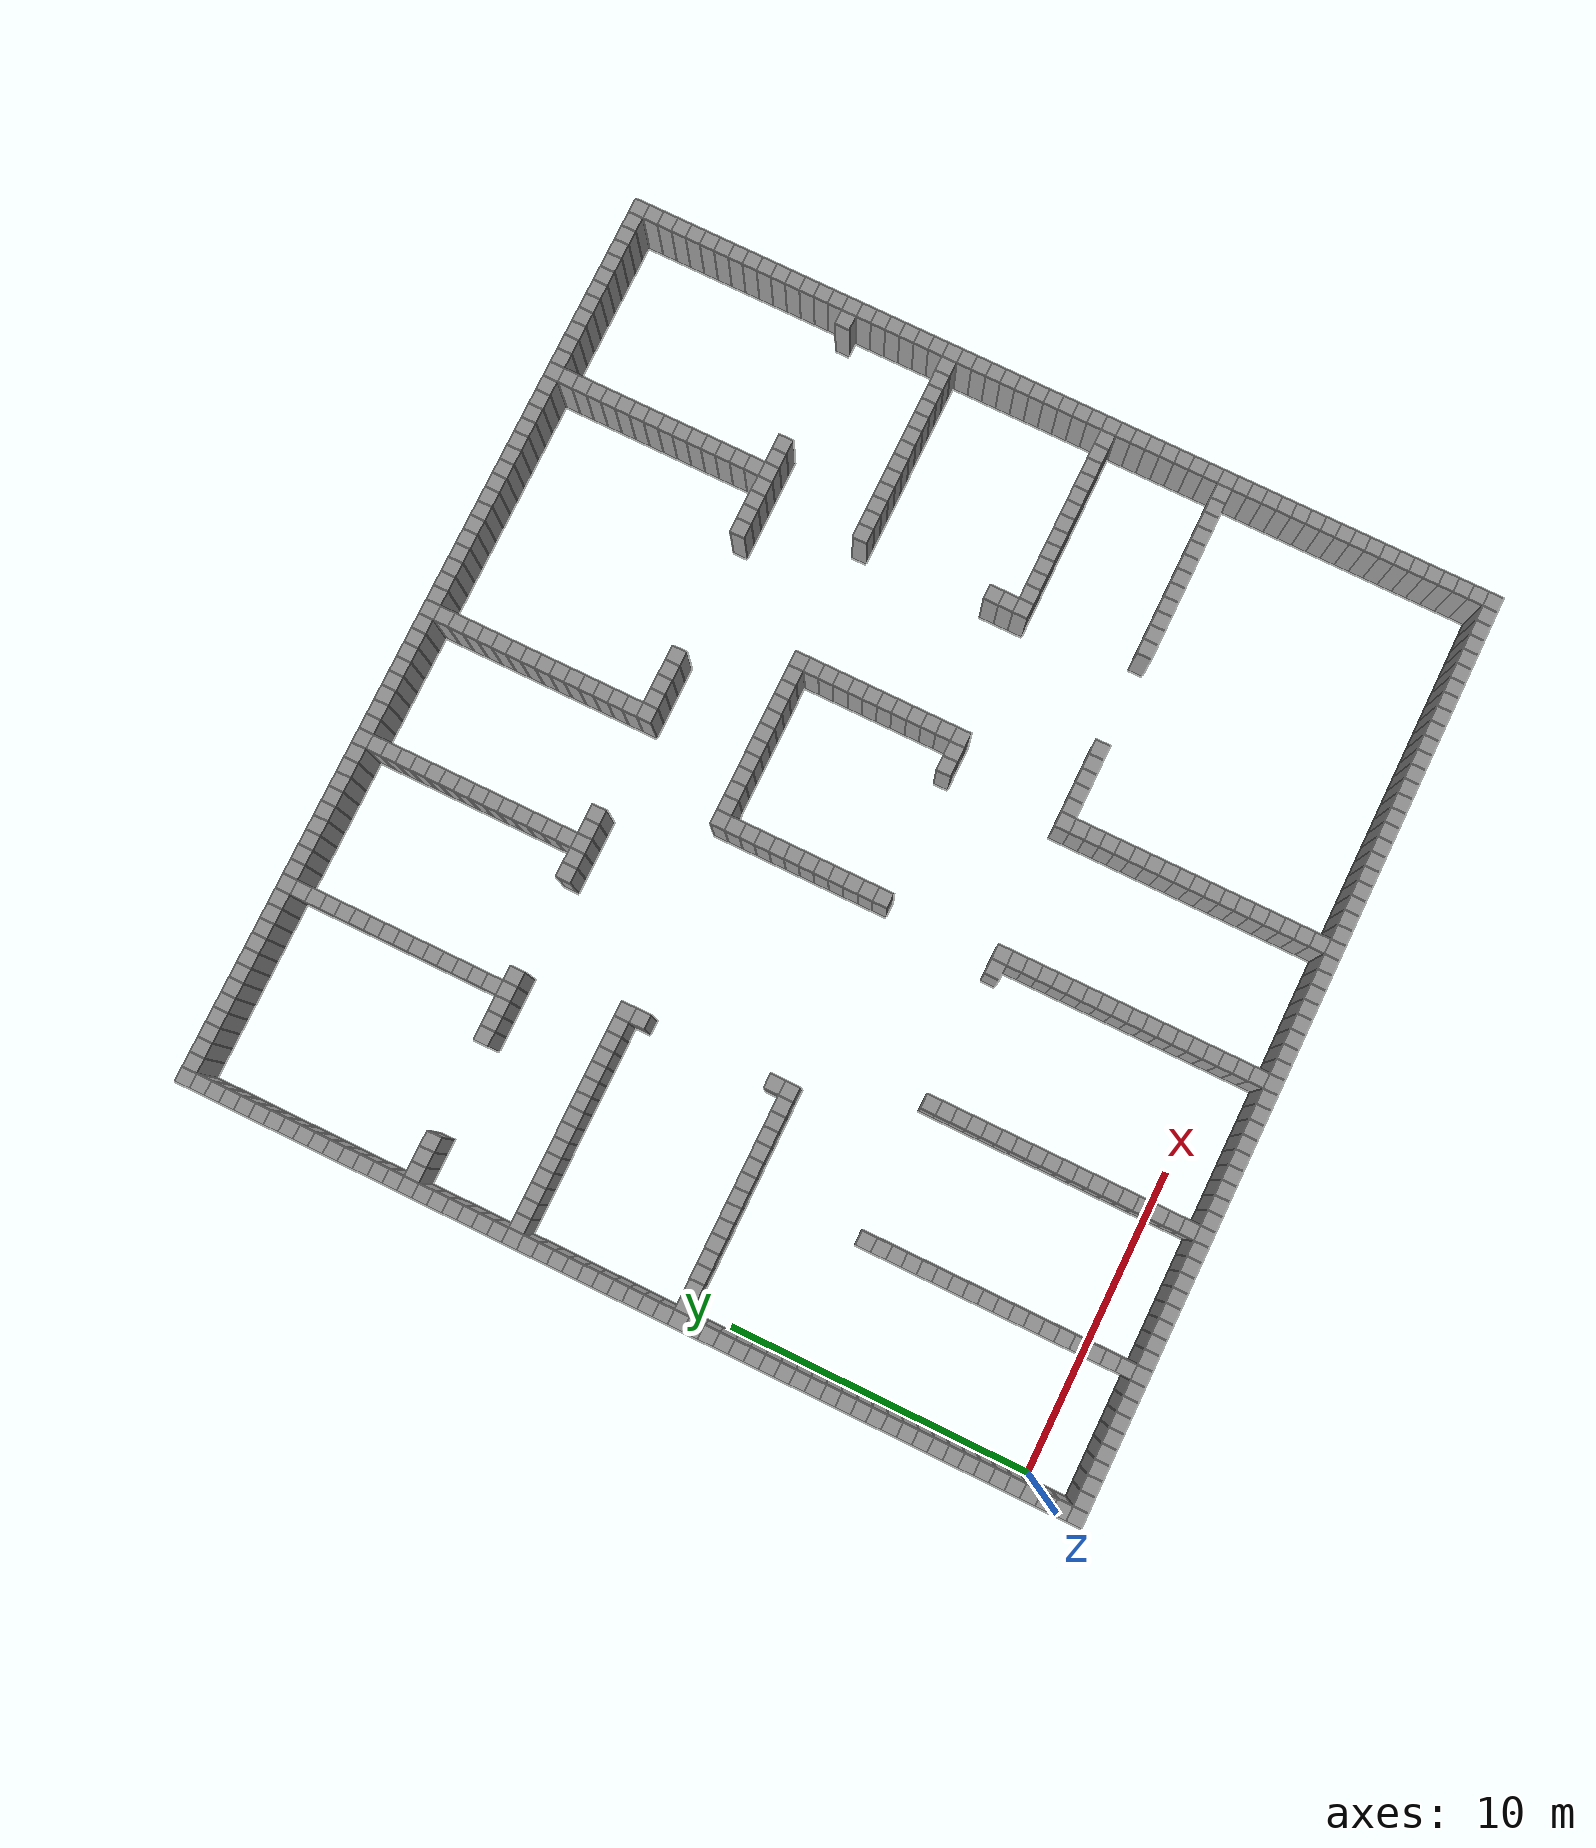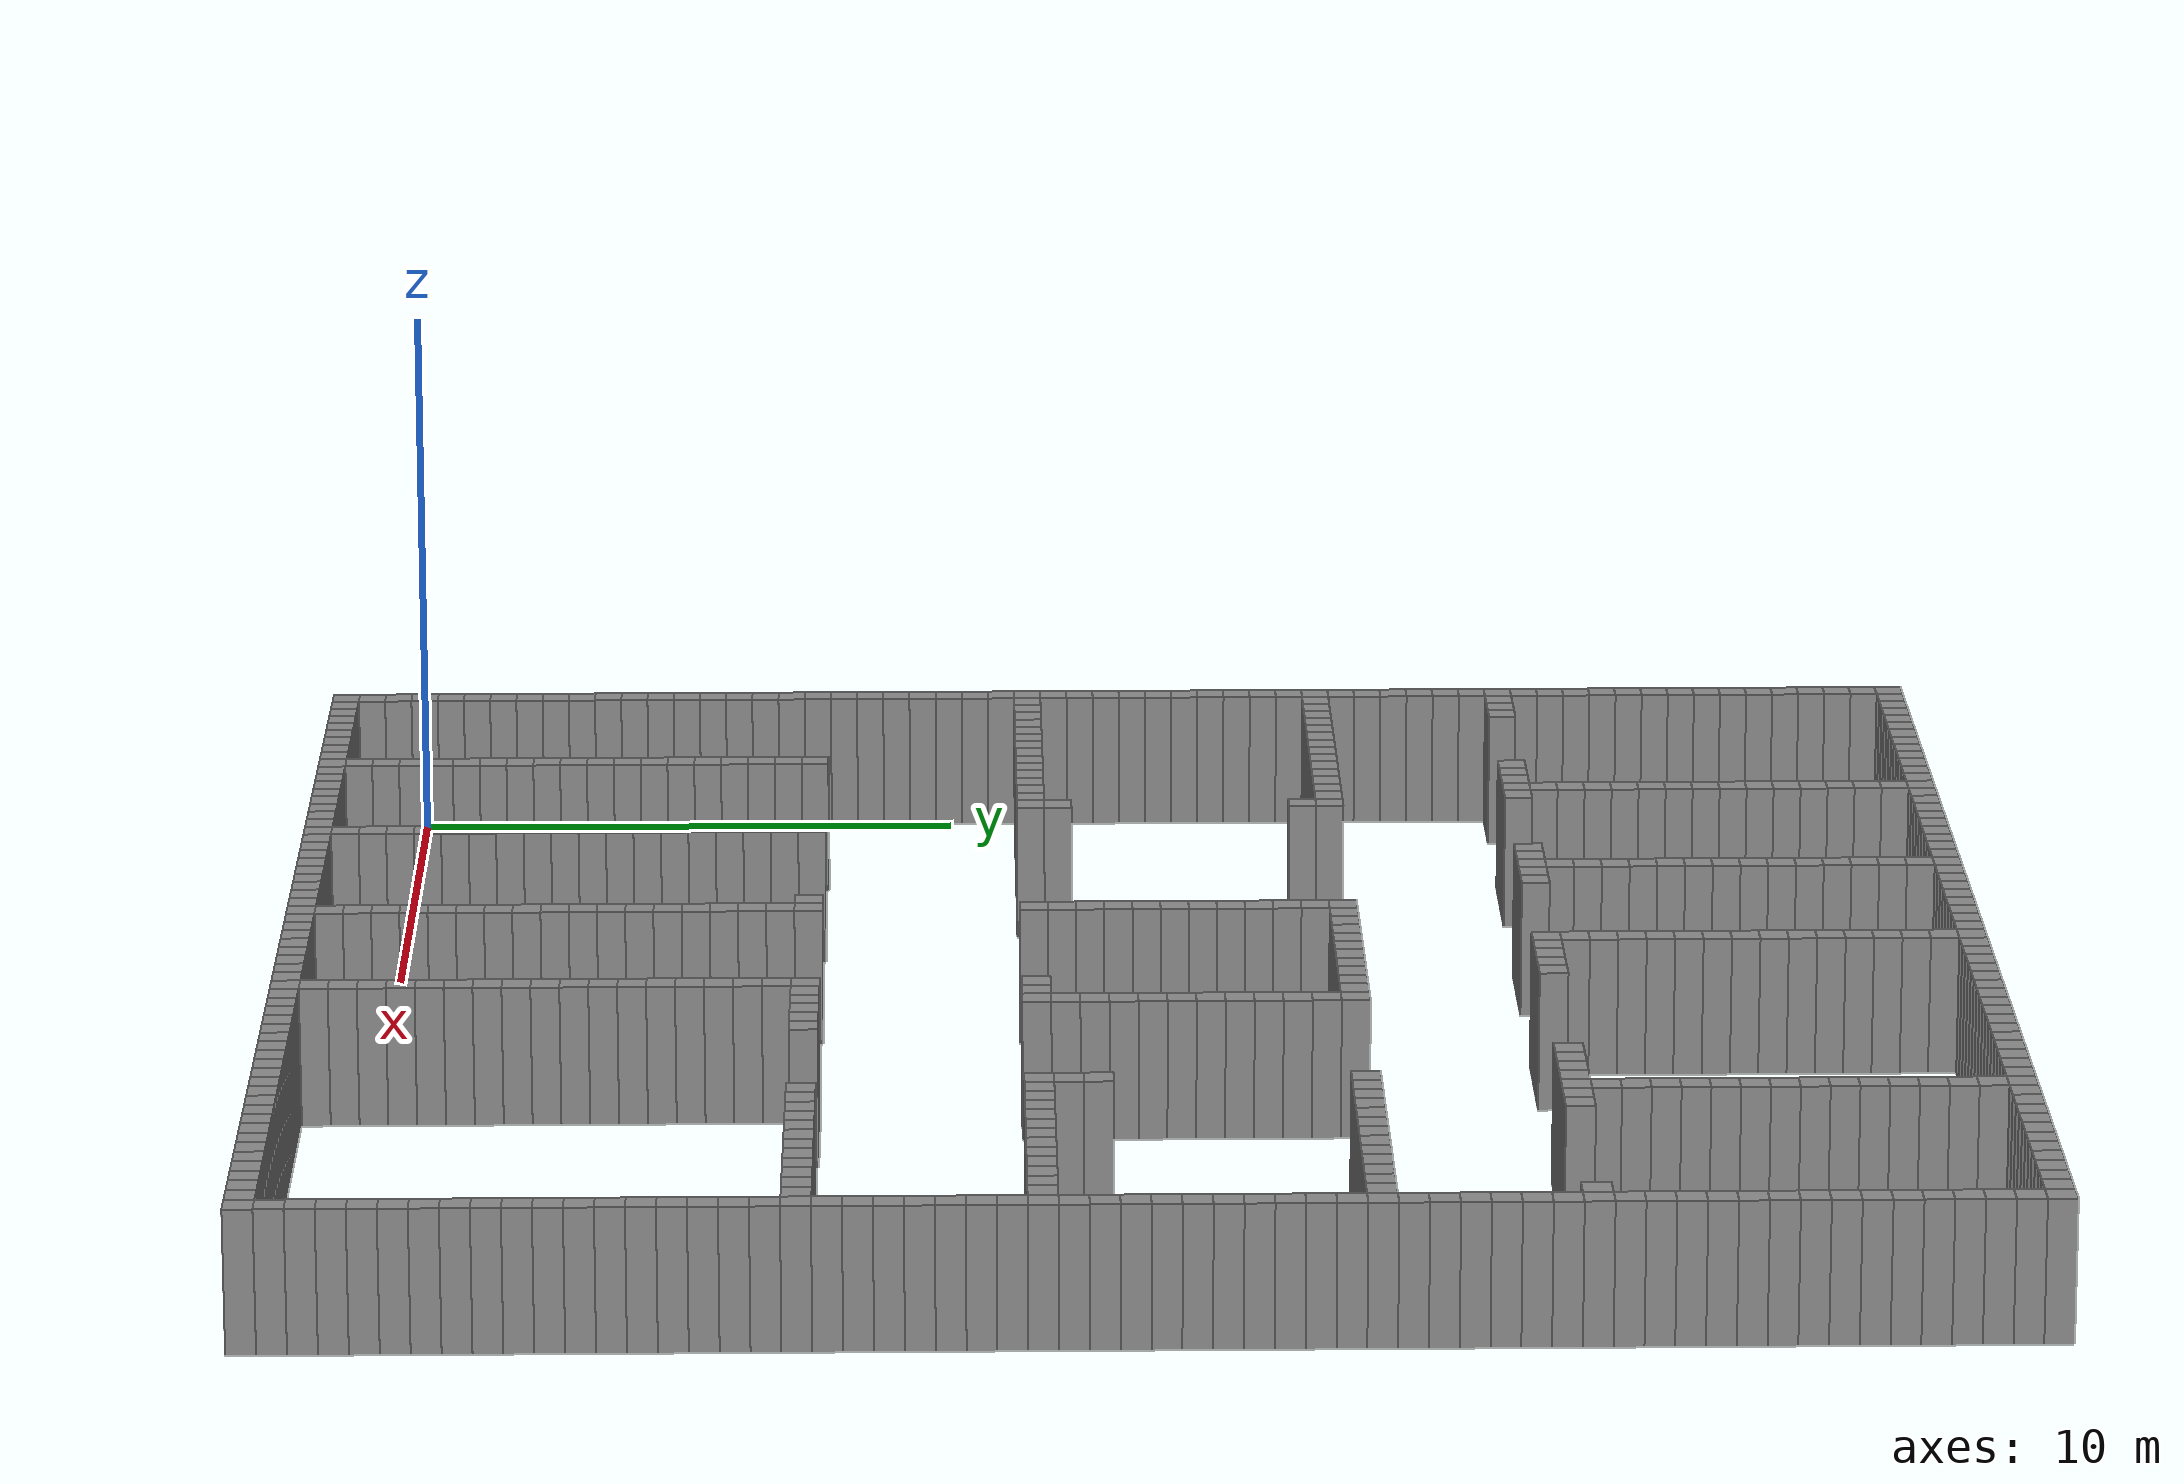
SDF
<?xml version='1.0'?>
<sdf version='1.7'>
  <model name='image1'>
    <pose>-0.375 -1.54 0 0 -0 0</pose>
    <link name='Wall_0'>
      <collision name='Wall_0_Collision'>
        <geometry>
          <box>
            <size>0.5 0.5 2.5</size>
          </box>
        </geometry>
        <pose>0 0 1.25 0 -0 0</pose>
      </collision>
      <visual name='Wall_0_Visual'>
        <pose>0 0 1.25 0 -0 0</pose>
        <geometry>
          <box>
            <size>0.5 0.5 2.5</size>
          </box>
        </geometry>
        <material>
          <script>
            <uri>file://media/materials/scripts/gazebo.material</uri>
            <name>Gazebo/Grey</name>
          </script>
          <ambient>1 1 1 1</ambient>
        </material>
        <meta>
          <layer>0</layer>
        </meta>
      </visual>
      <pose>0.0 0.0 0 0 -0 0</pose>
    </link>
    <link name='Wall_1'>
      <collision name='Wall_1_Collision'>
        <geometry>
          <box>
            <size>0.5 0.5 2.5</size>
          </box>
        </geometry>
        <pose>0 0 1.25 0 -0 0</pose>
      </collision>
      <visual name='Wall_1_Visual'>
        <pose>0 0 1.25 0 -0 0</pose>
        <geometry>
          <box>
            <size>0.5 0.5 2.5</size>
          </box>
        </geometry>
        <material>
          <script>
            <uri>file://media/materials/scripts/gazebo.material</uri>
            <name>Gazebo/Grey</name>
          </script>
          <ambient>1 1 1 1</ambient>
        </material>
        <meta>
          <layer>0</layer>
        </meta>
      </visual>
      <pose>0.0 0.5 0 0 -0 0</pose>
    </link>
    <link name='Wall_2'>
      <collision name='Wall_2_Collision'>
        <geometry>
          <box>
            <size>0.5 0.5 2.5</size>
          </box>
        </geometry>
        <pose>0 0 1.25 0 -0 0</pose>
      </collision>
      <visual name='Wall_2_Visual'>
        <pose>0 0 1.25 0 -0 0</pose>
        <geometry>
          <box>
            <size>0.5 0.5 2.5</size>
          </box>
        </geometry>
        <material>
          <script>
            <uri>file://media/materials/scripts/gazebo.material</uri>
            <name>Gazebo/Grey</name>
          </script>
          <ambient>1 1 1 1</ambient>
        </material>
        <meta>
          <layer>0</layer>
        </meta>
      </visual>
      <pose>0.0 1.0 0 0 -0 0</pose>
    </link>
    <link name='Wall_3'>
      <collision name='Wall_3_Collision'>
        <geometry>
          <box>
            <size>0.5 0.5 2.5</size>
          </box>
        </geometry>
        <pose>0 0 1.25 0 -0 0</pose>
      </collision>
      <visual name='Wall_3_Visual'>
        <pose>0 0 1.25 0 -0 0</pose>
        <geometry>
          <box>
            <size>0.5 0.5 2.5</size>
          </box>
        </geometry>
        <material>
          <script>
            <uri>file://media/materials/scripts/gazebo.material</uri>
            <name>Gazebo/Grey</name>
          </script>
          <ambient>1 1 1 1</ambient>
        </material>
        <meta>
          <layer>0</layer>
        </meta>
      </visual>
      <pose>0.0 1.5 0 0 -0 0</pose>
    </link>
    <link name='Wall_4'>
      <collision name='Wall_4_Collision'>
        <geometry>
          <box>
            <size>0.5 0.5 2.5</size>
          </box>
        </geometry>
        <pose>0 0 1.25 0 -0 0</pose>
      </collision>
      <visual name='Wall_4_Visual'>
        <pose>0 0 1.25 0 -0 0</pose>
        <geometry>
          <box>
            <size>0.5 0.5 2.5</size>
          </box>
        </geometry>
        <material>
          <script>
            <uri>file://media/materials/scripts/gazebo.material</uri>
            <name>Gazebo/Grey</name>
          </script>
          <ambient>1 1 1 1</ambient>
        </material>
        <meta>
          <layer>0</layer>
        </meta>
      </visual>
      <pose>0.0 2.0 0 0 -0 0</pose>
    </link>
    <link name='Wall_5'>
      <collision name='Wall_5_Collision'>
        <geometry>
          <box>
            <size>0.5 0.5 2.5</size>
          </box>
        </geometry>
        <pose>0 0 1.25 0 -0 0</pose>
      </collision>
      <visual name='Wall_5_Visual'>
        <pose>0 0 1.25 0 -0 0</pose>
        <geometry>
          <box>
            <size>0.5 0.5 2.5</size>
          </box>
        </geometry>
        <material>
          <script>
            <uri>file://media/materials/scripts/gazebo.material</uri>
            <name>Gazebo/Grey</name>
          </script>
          <ambient>1 1 1 1</ambient>
        </material>
        <meta>
          <layer>0</layer>
        </meta>
      </visual>
      <pose>0.0 2.5 0 0 -0 0</pose>
    </link>
    <link name='Wall_6'>
      <collision name='Wall_6_Collision'>
        <geometry>
          <box>
            <size>0.5 0.5 2.5</size>
          </box>
        </geometry>
        <pose>0 0 1.25 0 -0 0</pose>
      </collision>
      <visual name='Wall_6_Visual'>
        <pose>0 0 1.25 0 -0 0</pose>
        <geometry>
          <box>
            <size>0.5 0.5 2.5</size>
          </box>
        </geometry>
        <material>
          <script>
            <uri>file://media/materials/scripts/gazebo.material</uri>
            <name>Gazebo/Grey</name>
          </script>
          <ambient>1 1 1 1</ambient>
        </material>
        <meta>
          <layer>0</layer>
        </meta>
      </visual>
      <pose>0.0 3.0 0 0 -0 0</pose>
    </link>
    <link name='Wall_7'>
      <collision name='Wall_7_Collision'>
        <geometry>
          <box>
            <size>0.5 0.5 2.5</size>
          </box>
        </geometry>
        <pose>0 0 1.25 0 -0 0</pose>
      </collision>
      <visual name='Wall_7_Visual'>
        <pose>0 0 1.25 0 -0 0</pose>
        <geometry>
          <box>
            <size>0.5 0.5 2.5</size>
          </box>
        </geometry>
        <material>
          <script>
            <uri>file://media/materials/scripts/gazebo.material</uri>
            <name>Gazebo/Grey</name>
          </script>
          <ambient>1 1 1 1</ambient>
        </material>
        <meta>
          <layer>0</layer>
        </meta>
      </visual>
      <pose>0.0 3.5 0 0 -0 0</pose>
    </link>
    <link name='Wall_8'>
      <collision name='Wall_8_Collision'>
        <geometry>
          <box>
            <size>0.5 0.5 2.5</size>
          </box>
        </geometry>
        <pose>0 0 1.25 0 -0 0</pose>
      </collision>
      <visual name='Wall_8_Visual'>
        <pose>0 0 1.25 0 -0 0</pose>
        <geometry>
          <box>
            <size>0.5 0.5 2.5</size>
          </box>
        </geometry>
        <material>
          <script>
            <uri>file://media/materials/scripts/gazebo.material</uri>
            <name>Gazebo/Grey</name>
          </script>
          <ambient>1 1 1 1</ambient>
        </material>
        <meta>
          <layer>0</layer>
        </meta>
      </visual>
      <pose>0.0 4.0 0 0 -0 0</pose>
    </link>
    <link name='Wall_9'>
      <collision name='Wall_9_Collision'>
        <geometry>
          <box>
            <size>0.5 0.5 2.5</size>
          </box>
        </geometry>
        <pose>0 0 1.25 0 -0 0</pose>
      </collision>
      <visual name='Wall_9_Visual'>
        <pose>0 0 1.25 0 -0 0</pose>
        <geometry>
          <box>
            <size>0.5 0.5 2.5</size>
          </box>
        </geometry>
        <material>
          <script>
            <uri>file://media/materials/scripts/gazebo.material</uri>
            <name>Gazebo/Grey</name>
          </script>
          <ambient>1 1 1 1</ambient>
        </material>
        <meta>
          <layer>0</layer>
        </meta>
      </visual>
      <pose>0.0 4.5 0 0 -0 0</pose>
    </link>
    <link name='Wall_10'>
      <collision name='Wall_10_Collision'>
        <geometry>
          <box>
            <size>0.5 0.5 2.5</size>
          </box>
        </geometry>
        <pose>0 0 1.25 0 -0 0</pose>
      </collision>
      <visual name='Wall_10_Visual'>
        <pose>0 0 1.25 0 -0 0</pose>
        <geometry>
          <box>
            <size>0.5 0.5 2.5</size>
          </box>
        </geometry>
        <material>
          <script>
            <uri>file://media/materials/scripts/gazebo.material</uri>
            <name>Gazebo/Grey</name>
          </script>
          <ambient>1 1 1 1</ambient>
        </material>
        <meta>
          <layer>0</layer>
        </meta>
      </visual>
      <pose>0.0 5.0 0 0 -0 0</pose>
    </link>
    <link name='Wall_11'>
      <collision name='Wall_11_Collision'>
        <geometry>
          <box>
            <size>0.5 0.5 2.5</size>
          </box>
        </geometry>
        <pose>0 0 1.25 0 -0 0</pose>
      </collision>
      <visual name='Wall_11_Visual'>
        <pose>0 0 1.25 0 -0 0</pose>
        <geometry>
          <box>
            <size>0.5 0.5 2.5</size>
          </box>
        </geometry>
        <material>
          <script>
            <uri>file://media/materials/scripts/gazebo.material</uri>
            <name>Gazebo/Grey</name>
          </script>
          <ambient>1 1 1 1</ambient>
        </material>
        <meta>
          <layer>0</layer>
        </meta>
      </visual>
      <pose>0.0 5.5 0 0 -0 0</pose>
    </link>
    <link name='Wall_12'>
      <collision name='Wall_12_Collision'>
        <geometry>
          <box>
            <size>0.5 0.5 2.5</size>
          </box>
        </geometry>
        <pose>0 0 1.25 0 -0 0</pose>
      </collision>
      <visual name='Wall_12_Visual'>
        <pose>0 0 1.25 0 -0 0</pose>
        <geometry>
          <box>
            <size>0.5 0.5 2.5</size>
          </box>
        </geometry>
        <material>
          <script>
            <uri>file://media/materials/scripts/gazebo.material</uri>
            <name>Gazebo/Grey</name>
          </script>
          <ambient>1 1 1 1</ambient>
        </material>
        <meta>
          <layer>0</layer>
        </meta>
      </visual>
      <pose>0.0 6.0 0 0 -0 0</pose>
    </link>
    <link name='Wall_13'>
      <collision name='Wall_13_Collision'>
        <geometry>
          <box>
            <size>0.5 0.5 2.5</size>
          </box>
        </geometry>
        <pose>0 0 1.25 0 -0 0</pose>
      </collision>
      <visual name='Wall_13_Visual'>
        <pose>0 0 1.25 0 -0 0</pose>
        <geometry>
          <box>
            <size>0.5 0.5 2.5</size>
          </box>
        </geometry>
        <material>
          <script>
            <uri>file://media/materials/scripts/gazebo.material</uri>
            <name>Gazebo/Grey</name>
          </script>
          <ambient>1 1 1 1</ambient>
        </material>
        <meta>
          <layer>0</layer>
        </meta>
      </visual>
      <pose>0.0 6.5 0 0 -0 0</pose>
    </link>
    <link name='Wall_14'>
      <collision name='Wall_14_Collision'>
        <geometry>
          <box>
            <size>0.5 0.5 2.5</size>
          </box>
        </geometry>
        <pose>0 0 1.25 0 -0 0</pose>
      </collision>
      <visual name='Wall_14_Visual'>
        <pose>0 0 1.25 0 -0 0</pose>
        <geometry>
          <box>
            <size>0.5 0.5 2.5</size>
          </box>
        </geometry>
        <material>
          <script>
            <uri>file://media/materials/scripts/gazebo.material</uri>
            <name>Gazebo/Grey</name>
          </script>
          <ambient>1 1 1 1</ambient>
        </material>
        <meta>
          <layer>0</layer>
        </meta>
      </visual>
      <pose>0.0 7.0 0 0 -0 0</pose>
    </link>
    <link name='Wall_15'>
      <collision name='Wall_15_Collision'>
        <geometry>
          <box>
            <size>0.5 0.5 2.5</size>
          </box>
        </geometry>
        <pose>0 0 1.25 0 -0 0</pose>
      </collision>
      <visual name='Wall_15_Visual'>
        <pose>0 0 1.25 0 -0 0</pose>
        <geometry>
          <box>
            <size>0.5 0.5 2.5</size>
          </box>
        </geometry>
        <material>
          <script>
            <uri>file://media/materials/scripts/gazebo.material</uri>
            <name>Gazebo/Grey</name>
          </script>
          <ambient>1 1 1 1</ambient>
        </material>
        <meta>
          <layer>0</layer>
        </meta>
      </visual>
      <pose>0.0 7.5 0 0 -0 0</pose>
    </link>
    <link name='Wall_16'>
      <collision name='Wall_16_Collision'>
        <geometry>
          <box>
            <size>0.5 0.5 2.5</size>
          </box>
        </geometry>
        <pose>0 0 1.25 0 -0 0</pose>
      </collision>
      <visual name='Wall_16_Visual'>
        <pose>0 0 1.25 0 -0 0</pose>
        <geometry>
          <box>
            <size>0.5 0.5 2.5</size>
          </box>
        </geometry>
        <material>
          <script>
            <uri>file://media/materials/scripts/gazebo.material</uri>
            <name>Gazebo/Grey</name>
          </script>
          <ambient>1 1 1 1</ambient>
        </material>
        <meta>
          <layer>0</layer>
        </meta>
      </visual>
      <pose>0.0 8.0 0 0 -0 0</pose>
    </link>
    <link name='Wall_17'>
      <collision name='Wall_17_Collision'>
        <geometry>
          <box>
            <size>0.5 0.5 2.5</size>
          </box>
        </geometry>
        <pose>0 0 1.25 0 -0 0</pose>
      </collision>
      <visual name='Wall_17_Visual'>
        <pose>0 0 1.25 0 -0 0</pose>
        <geometry>
          <box>
            <size>0.5 0.5 2.5</size>
          </box>
        </geometry>
        <material>
          <script>
            <uri>file://media/materials/scripts/gazebo.material</uri>
            <name>Gazebo/Grey</name>
          </script>
          <ambient>1 1 1 1</ambient>
        </material>
        <meta>
          <layer>0</layer>
        </meta>
      </visual>
      <pose>0.0 8.5 0 0 -0 0</pose>
    </link>
    <link name='Wall_18'>
      <collision name='Wall_18_Collision'>
        <geometry>
          <box>
            <size>0.5 0.5 2.5</size>
          </box>
        </geometry>
        <pose>0 0 1.25 0 -0 0</pose>
      </collision>
      <visual name='Wall_18_Visual'>
        <pose>0 0 1.25 0 -0 0</pose>
        <geometry>
          <box>
            <size>0.5 0.5 2.5</size>
          </box>
        </geometry>
        <material>
          <script>
            <uri>file://media/materials/scripts/gazebo.material</uri>
            <name>Gazebo/Grey</name>
          </script>
          <ambient>1 1 1 1</ambient>
        </material>
        <meta>
          <layer>0</layer>
        </meta>
      </visual>
      <pose>0.0 9.0 0 0 -0 0</pose>
    </link>
    <link name='Wall_19'>
      <collision name='Wall_19_Collision'>
        <geometry>
          <box>
            <size>0.5 0.5 2.5</size>
          </box>
        </geometry>
        <pose>0 0 1.25 0 -0 0</pose>
      </collision>
      <visual name='Wall_19_Visual'>
        <pose>0 0 1.25 0 -0 0</pose>
        <geometry>
          <box>
            <size>0.5 0.5 2.5</size>
          </box>
        </geometry>
        <material>
          <script>
            <uri>file://media/materials/scripts/gazebo.material</uri>
            <name>Gazebo/Grey</name>
          </script>
          <ambient>1 1 1 1</ambient>
        </material>
        <meta>
          <layer>0</layer>
        </meta>
      </visual>
      <pose>0.0 9.5 0 0 -0 0</pose>
    </link>
    <link name='Wall_20'>
      <collision name='Wall_20_Collision'>
        <geometry>
          <box>
            <size>0.5 0.5 2.5</size>
          </box>
        </geometry>
        <pose>0 0 1.25 0 -0 0</pose>
      </collision>
      <visual name='Wall_20_Visual'>
        <pose>0 0 1.25 0 -0 0</pose>
        <geometry>
          <box>
            <size>0.5 0.5 2.5</size>
          </box>
        </geometry>
        <material>
          <script>
            <uri>file://media/materials/scripts/gazebo.material</uri>
            <name>Gazebo/Grey</name>
          </script>
          <ambient>1 1 1 1</ambient>
        </material>
        <meta>
          <layer>0</layer>
        </meta>
      </visual>
      <pose>0.0 10.0 0 0 -0 0</pose>
    </link>
    <link name='Wall_21'>
      <collision name='Wall_21_Collision'>
        <geometry>
          <box>
            <size>0.5 0.5 2.5</size>
          </box>
        </geometry>
        <pose>0 0 1.25 0 -0 0</pose>
      </collision>
      <visual name='Wall_21_Visual'>
        <pose>0 0 1.25 0 -0 0</pose>
        <geometry>
          <box>
            <size>0.5 0.5 2.5</size>
          </box>
        </geometry>
        <material>
          <script>
            <uri>file://media/materials/scripts/gazebo.material</uri>
            <name>Gazebo/Grey</name>
          </script>
          <ambient>1 1 1 1</ambient>
        </material>
        <meta>
          <layer>0</layer>
        </meta>
      </visual>
      <pose>0.0 10.5 0 0 -0 0</pose>
    </link>
    <link name='Wall_22'>
      <collision name='Wall_22_Collision'>
        <geometry>
          <box>
            <size>0.5 0.5 2.5</size>
          </box>
        </geometry>
        <pose>0 0 1.25 0 -0 0</pose>
      </collision>
      <visual name='Wall_22_Visual'>
        <pose>0 0 1.25 0 -0 0</pose>
        <geometry>
          <box>
            <size>0.5 0.5 2.5</size>
          </box>
        </geometry>
        <material>
          <script>
            <uri>file://media/materials/scripts/gazebo.material</uri>
            <name>Gazebo/Grey</name>
          </script>
          <ambient>1 1 1 1</ambient>
        </material>
        <meta>
          <layer>0</layer>
        </meta>
      </visual>
      <pose>0.0 11.0 0 0 -0 0</pose>
    </link>
    <link name='Wall_23'>
      <collision name='Wall_23_Collision'>
        <geometry>
          <box>
            <size>0.5 0.5 2.5</size>
          </box>
        </geometry>
        <pose>0 0 1.25 0 -0 0</pose>
      </collision>
      <visual name='Wall_23_Visual'>
        <pose>0 0 1.25 0 -0 0</pose>
        <geometry>
          <box>
            <size>0.5 0.5 2.5</size>
          </box>
        </geometry>
        <material>
          <script>
            <uri>file://media/materials/scripts/gazebo.material</uri>
            <name>Gazebo/Grey</name>
          </script>
          <ambient>1 1 1 1</ambient>
        </material>
        <meta>
          <layer>0</layer>
        </meta>
      </visual>
      <pose>0.0 11.5 0 0 -0 0</pose>
    </link>
    <link name='Wall_24'>
      <collision name='Wall_24_Collision'>
        <geometry>
          <box>
            <size>0.5 0.5 2.5</size>
          </box>
        </geometry>
        <pose>0 0 1.25 0 -0 0</pose>
      </collision>
      <visual name='Wall_24_Visual'>
        <pose>0 0 1.25 0 -0 0</pose>
        <geometry>
          <box>
            <size>0.5 0.5 2.5</size>
          </box>
        </geometry>
        <material>
          <script>
            <uri>file://media/materials/scripts/gazebo.material</uri>
            <name>Gazebo/Grey</name>
          </script>
          <ambient>1 1 1 1</ambient>
        </material>
        <meta>
          <layer>0</layer>
        </meta>
      </visual>
      <pose>0.0 12.0 0 0 -0 0</pose>
    </link>
    <link name='Wall_25'>
      <collision name='Wall_25_Collision'>
        <geometry>
          <box>
            <size>0.5 0.5 2.5</size>
          </box>
        </geometry>
        <pose>0 0 1.25 0 -0 0</pose>
      </collision>
      <visual name='Wall_25_Visual'>
        <pose>0 0 1.25 0 -0 0</pose>
        <geometry>
          <box>
            <size>0.5 0.5 2.5</size>
          </box>
        </geometry>
        <material>
          <script>
            <uri>file://media/materials/scripts/gazebo.material</uri>
            <name>Gazebo/Grey</name>
          </script>
          <ambient>1 1 1 1</ambient>
        </material>
        <meta>
          <layer>0</layer>
        </meta>
      </visual>
      <pose>0.0 12.5 0 0 -0 0</pose>
    </link>
    <link name='Wall_26'>
      <collision name='Wall_26_Collision'>
        <geometry>
          <box>
            <size>0.5 0.5 2.5</size>
          </box>
        </geometry>
        <pose>0 0 1.25 0 -0 0</pose>
      </collision>
      <visual name='Wall_26_Visual'>
        <pose>0 0 1.25 0 -0 0</pose>
        <geometry>
          <box>
            <size>0.5 0.5 2.5</size>
          </box>
        </geometry>
        <material>
          <script>
            <uri>file://media/materials/scripts/gazebo.material</uri>
            <name>Gazebo/Grey</name>
          </script>
          <ambient>1 1 1 1</ambient>
        </material>
        <meta>
          <layer>0</layer>
        </meta>
      </visual>
      <pose>0.0 13.0 0 0 -0 0</pose>
    </link>
    <link name='Wall_27'>
      <collision name='Wall_27_Collision'>
        <geometry>
          <box>
            <size>0.5 0.5 2.5</size>
          </box>
        </geometry>
        <pose>0 0 1.25 0 -0 0</pose>
      </collision>
      <visual name='Wall_27_Visual'>
        <pose>0 0 1.25 0 -0 0</pose>
        <geometry>
          <box>
            <size>0.5 0.5 2.5</size>
          </box>
        </geometry>
        <material>
          <script>
            <uri>file://media/materials/scripts/gazebo.material</uri>
            <name>Gazebo/Grey</name>
          </script>
          <ambient>1 1 1 1</ambient>
        </material>
        <meta>
          <layer>0</layer>
        </meta>
      </visual>
      <pose>0.0 13.5 0 0 -0 0</pose>
    </link>
    <link name='Wall_28'>
      <collision name='Wall_28_Collision'>
        <geometry>
          <box>
            <size>0.5 0.5 2.5</size>
          </box>
        </geometry>
        <pose>0 0 1.25 0 -0 0</pose>
      </collision>
      <visual name='Wall_28_Visual'>
        <pose>0 0 1.25 0 -0 0</pose>
        <geometry>
          <box>
            <size>0.5 0.5 2.5</size>
          </box>
        </geometry>
        <material>
          <script>
            <uri>file://media/materials/scripts/gazebo.material</uri>
            <name>Gazebo/Grey</name>
          </script>
          <ambient>1 1 1 1</ambient>
        </material>
        <meta>
          <layer>0</layer>
        </meta>
      </visual>
      <pose>0.0 14.0 0 0 -0 0</pose>
    </link>
    <link name='Wall_29'>
      <collision name='Wall_29_Collision'>
        <geometry>
          <box>
            <size>0.5 0.5 2.5</size>
          </box>
        </geometry>
        <pose>0 0 1.25 0 -0 0</pose>
      </collision>
      <visual name='Wall_29_Visual'>
        <pose>0 0 1.25 0 -0 0</pose>
        <geometry>
          <box>
            <size>0.5 0.5 2.5</size>
          </box>
        </geometry>
        <material>
          <script>
            <uri>file://media/materials/scripts/gazebo.material</uri>
            <name>Gazebo/Grey</name>
          </script>
          <ambient>1 1 1 1</ambient>
        </material>
        <meta>
          <layer>0</layer>
        </meta>
      </visual>
      <pose>0.0 14.5 0 0 -0 0</pose>
    </link>
    <link name='Wall_30'>
      <collision name='Wall_30_Collision'>
        <geometry>
          <box>
            <size>0.5 0.5 2.5</size>
          </box>
        </geometry>
        <pose>0 0 1.25 0 -0 0</pose>
      </collision>
      <visual name='Wall_30_Visual'>
        <pose>0 0 1.25 0 -0 0</pose>
        <geometry>
          <box>
            <size>0.5 0.5 2.5</size>
          </box>
        </geometry>
        <material>
          <script>
            <uri>file://media/materials/scripts/gazebo.material</uri>
            <name>Gazebo/Grey</name>
          </script>
          <ambient>1 1 1 1</ambient>
        </material>
        <meta>
          <layer>0</layer>
        </meta>
      </visual>
      <pose>0.0 15.0 0 0 -0 0</pose>
    </link>
    <link name='Wall_31'>
      <collision name='Wall_31_Collision'>
        <geometry>
          <box>
            <size>0.5 0.5 2.5</size>
          </box>
        </geometry>
        <pose>0 0 1.25 0 -0 0</pose>
      </collision>
      <visual name='Wall_31_Visual'>
        <pose>0 0 1.25 0 -0 0</pose>
        <geometry>
          <box>
            <size>0.5 0.5 2.5</size>
          </box>
        </geometry>
        <material>
          <script>
            <uri>file://media/materials/scripts/gazebo.material</uri>
            <name>Gazebo/Grey</name>
          </script>
          <ambient>1 1 1 1</ambient>
        </material>
        <meta>
          <layer>0</layer>
        </meta>
      </visual>
      <pose>0.0 15.5 0 0 -0 0</pose>
    </link>
    <link name='Wall_32'>
      <collision name='Wall_32_Collision'>
        <geometry>
          <box>
            <size>0.5 0.5 2.5</size>
          </box>
        </geometry>
        <pose>0 0 1.25 0 -0 0</pose>
      </collision>
      <visual name='Wall_32_Visual'>
        <pose>0 0 1.25 0 -0 0</pose>
        <geometry>
          <box>
            <size>0.5 0.5 2.5</size>
          </box>
        </geometry>
        <material>
          <script>
            <uri>file://media/materials/scripts/gazebo.material</uri>
            <name>Gazebo/Grey</name>
          </script>
          <ambient>1 1 1 1</ambient>
        </material>
        <meta>
          <layer>0</layer>
        </meta>
      </visual>
      <pose>0.0 16.0 0 0 -0 0</pose>
    </link>
    <link name='Wall_33'>
      <collision name='Wall_33_Collision'>
        <geometry>
          <box>
            <size>0.5 0.5 2.5</size>
          </box>
        </geometry>
        <pose>0 0 1.25 0 -0 0</pose>
      </collision>
      <visual name='Wall_33_Visual'>
        <pose>0 0 1.25 0 -0 0</pose>
        <geometry>
          <box>
            <size>0.5 0.5 2.5</size>
          </box>
        </geometry>
        <material>
          <script>
            <uri>file://media/materials/scripts/gazebo.material</uri>
            <name>Gazebo/Grey</name>
          </script>
          <ambient>1 1 1 1</ambient>
        </material>
        <meta>
          <layer>0</layer>
        </meta>
      </visual>
      <pose>0.0 16.5 0 0 -0 0</pose>
    </link>
    <link name='Wall_34'>
      <collision name='Wall_34_Collision'>
        <geometry>
          <box>
            <size>0.5 0.5 2.5</size>
          </box>
        </geometry>
        <pose>0 0 1.25 0 -0 0</pose>
      </collision>
      <visual name='Wall_34_Visual'>
        <pose>0 0 1.25 0 -0 0</pose>
        <geometry>
          <box>
            <size>0.5 0.5 2.5</size>
          </box>
        </geometry>
        <material>
          <script>
            <uri>file://media/materials/scripts/gazebo.material</uri>
            <name>Gazebo/Grey</name>
          </script>
          <ambient>1 1 1 1</ambient>
        </material>
        <meta>
          <layer>0</layer>
        </meta>
      </visual>
      <pose>0.0 17.0 0 0 -0 0</pose>
    </link>
    <link name='Wall_35'>
      <collision name='Wall_35_Collision'>
        <geometry>
          <box>
            <size>0.5 0.5 2.5</size>
          </box>
        </geometry>
        <pose>0 0 1.25 0 -0 0</pose>
      </collision>
      <visual name='Wall_35_Visual'>
        <pose>0 0 1.25 0 -0 0</pose>
        <geometry>
          <box>
            <size>0.5 0.5 2.5</size>
          </box>
        </geometry>
        <material>
          <script>
            <uri>file://media/materials/scripts/gazebo.material</uri>
            <name>Gazebo/Grey</name>
          </script>
          <ambient>1 1 1 1</ambient>
        </material>
        <meta>
          <layer>0</layer>
        </meta>
      </visual>
      <pose>0.0 17.5 0 0 -0 0</pose>
    </link>
    <link name='Wall_36'>
      <collision name='Wall_36_Collision'>
        <geometry>
          <box>
            <size>0.5 0.5 2.5</size>
          </box>
        </geometry>
        <pose>0 0 1.25 0 -0 0</pose>
      </collision>
      <visual name='Wall_36_Visual'>
        <pose>0 0 1.25 0 -0 0</pose>
        <geometry>
          <box>
            <size>0.5 0.5 2.5</size>
          </box>
        </geometry>
        <material>
          <script>
            <uri>file://media/materials/scripts/gazebo.material</uri>
            <name>Gazebo/Grey</name>
          </script>
          <ambient>1 1 1 1</ambient>
        </material>
        <meta>
          <layer>0</layer>
        </meta>
      </visual>
      <pose>0.0 18.0 0 0 -0 0</pose>
    </link>
    <link name='Wall_37'>
      <collision name='Wall_37_Collision'>
        <geometry>
          <box>
            <size>0.5 0.5 2.5</size>
          </box>
        </geometry>
        <pose>0 0 1.25 0 -0 0</pose>
      </collision>
      <visual name='Wall_37_Visual'>
        <pose>0 0 1.25 0 -0 0</pose>
        <geometry>
          <box>
            <size>0.5 0.5 2.5</size>
          </box>
        </geometry>
        <material>
          <script>
            <uri>file://media/materials/scripts/gazebo.material</uri>
            <name>Gazebo/Grey</name>
          </script>
          <ambient>1 1 1 1</ambient>
        </material>
        <meta>
          <layer>0</layer>
        </meta>
      </visual>
      <pose>0.0 18.5 0 0 -0 0</pose>
    </link>
    <link name='Wall_38'>
      <collision name='Wall_38_Collision'>
        <geometry>
          <box>
            <size>0.5 0.5 2.5</size>
          </box>
        </geometry>
        <pose>0 0 1.25 0 -0 0</pose>
      </collision>
      <visual name='Wall_38_Visual'>
        <pose>0 0 1.25 0 -0 0</pose>
        <geometry>
          <box>
            <size>0.5 0.5 2.5</size>
          </box>
        </geometry>
        <material>
          <script>
            <uri>file://media/materials/scripts/gazebo.material</uri>
            <name>Gazebo/Grey</name>
          </script>
          <ambient>1 1 1 1</ambient>
        </material>
        <meta>
          <layer>0</layer>
        </meta>
      </visual>
      <pose>0.0 19.0 0 0 -0 0</pose>
    </link>
    <link name='Wall_39'>
      <collision name='Wall_39_Collision'>
        <geometry>
          <box>
            <size>0.5 0.5 2.5</size>
          </box>
        </geometry>
        <pose>0 0 1.25 0 -0 0</pose>
      </collision>
      <visual name='Wall_39_Visual'>
        <pose>0 0 1.25 0 -0 0</pose>
        <geometry>
          <box>
            <size>0.5 0.5 2.5</size>
          </box>
        </geometry>
        <material>
          <script>
            <uri>file://media/materials/scripts/gazebo.material</uri>
            <name>Gazebo/Grey</name>
          </script>
          <ambient>1 1 1 1</ambient>
        </material>
        <meta>
          <layer>0</layer>
        </meta>
      </visual>
      <pose>0.0 19.5 0 0 -0 0</pose>
    </link>
    <link name='Wall_40'>
      <collision name='Wall_40_Collision'>
        <geometry>
          <box>
            <size>0.5 0.5 2.5</size>
          </box>
        </geometry>
        <pose>0 0 1.25 0 -0 0</pose>
      </collision>
      <visual name='Wall_40_Visual'>
        <pose>0 0 1.25 0 -0 0</pose>
        <geometry>
          <box>
            <size>0.5 0.5 2.5</size>
          </box>
        </geometry>
        <material>
          <script>
            <uri>file://media/materials/scripts/gazebo.material</uri>
            <name>Gazebo/Grey</name>
          </script>
          <ambient>1 1 1 1</ambient>
        </material>
        <meta>
          <layer>0</layer>
        </meta>
      </visual>
      <pose>0.0 20.0 0 0 -0 0</pose>
    </link>
    <link name='Wall_41'>
      <collision name='Wall_41_Collision'>
        <geometry>
          <box>
            <size>0.5 0.5 2.5</size>
          </box>
        </geometry>
        <pose>0 0 1.25 0 -0 0</pose>
      </collision>
      <visual name='Wall_41_Visual'>
        <pose>0 0 1.25 0 -0 0</pose>
        <geometry>
          <box>
            <size>0.5 0.5 2.5</size>
          </box>
        </geometry>
        <material>
          <script>
            <uri>file://media/materials/scripts/gazebo.material</uri>
            <name>Gazebo/Grey</name>
          </script>
          <ambient>1 1 1 1</ambient>
        </material>
        <meta>
          <layer>0</layer>
        </meta>
      </visual>
      <pose>0.0 20.5 0 0 -0 0</pose>
    </link>
    <link name='Wall_42'>
      <collision name='Wall_42_Collision'>
        <geometry>
          <box>
            <size>0.5 0.5 2.5</size>
          </box>
        </geometry>
        <pose>0 0 1.25 0 -0 0</pose>
      </collision>
      <visual name='Wall_42_Visual'>
        <pose>0 0 1.25 0 -0 0</pose>
        <geometry>
          <box>
            <size>0.5 0.5 2.5</size>
          </box>
        </geometry>
        <material>
          <script>
            <uri>file://media/materials/scripts/gazebo.material</uri>
            <name>Gazebo/Grey</name>
          </script>
          <ambient>1 1 1 1</ambient>
        </material>
        <meta>
          <layer>0</layer>
        </meta>
      </visual>
      <pose>0.0 21.0 0 0 -0 0</pose>
    </link>
    <link name='Wall_43'>
      <collision name='Wall_43_Collision'>
        <geometry>
          <box>
            <size>0.5 0.5 2.5</size>
          </box>
        </geometry>
        <pose>0 0 1.25 0 -0 0</pose>
      </collision>
      <visual name='Wall_43_Visual'>
        <pose>0 0 1.25 0 -0 0</pose>
        <geometry>
          <box>
            <size>0.5 0.5 2.5</size>
          </box>
        </geometry>
        <material>
          <script>
            <uri>file://media/materials/scripts/gazebo.material</uri>
            <name>Gazebo/Grey</name>
          </script>
          <ambient>1 1 1 1</ambient>
        </material>
        <meta>
          <layer>0</layer>
        </meta>
      </visual>
      <pose>0.0 21.5 0 0 -0 0</pose>
    </link>
    <link name='Wall_44'>
      <collision name='Wall_44_Collision'>
        <geometry>
          <box>
            <size>0.5 0.5 2.5</size>
          </box>
        </geometry>
        <pose>0 0 1.25 0 -0 0</pose>
      </collision>
      <visual name='Wall_44_Visual'>
        <pose>0 0 1.25 0 -0 0</pose>
        <geometry>
          <box>
            <size>0.5 0.5 2.5</size>
          </box>
        </geometry>
        <material>
          <script>
            <uri>file://media/materials/scripts/gazebo.material</uri>
            <name>Gazebo/Grey</name>
          </script>
          <ambient>1 1 1 1</ambient>
        </material>
        <meta>
          <layer>0</layer>
        </meta>
      </visual>
      <pose>0.0 22.0 0 0 -0 0</pose>
    </link>
    <link name='Wall_45'>
      <collision name='Wall_45_Collision'>
        <geometry>
          <box>
            <size>0.5 0.5 2.5</size>
          </box>
        </geometry>
        <pose>0 0 1.25 0 -0 0</pose>
      </collision>
      <visual name='Wall_45_Visual'>
        <pose>0 0 1.25 0 -0 0</pose>
        <geometry>
          <box>
            <size>0.5 0.5 2.5</size>
          </box>
        </geometry>
        <material>
          <script>
            <uri>file://media/materials/scripts/gazebo.material</uri>
            <name>Gazebo/Grey</name>
          </script>
          <ambient>1 1 1 1</ambient>
        </material>
        <meta>
          <layer>0</layer>
        </meta>
      </visual>
      <pose>0.0 22.5 0 0 -0 0</pose>
    </link>
    <link name='Wall_46'>
      <collision name='Wall_46_Collision'>
        <geometry>
          <box>
            <size>0.5 0.5 2.5</size>
          </box>
        </geometry>
        <pose>0 0 1.25 0 -0 0</pose>
      </collision>
      <visual name='Wall_46_Visual'>
        <pose>0 0 1.25 0 -0 0</pose>
        <geometry>
          <box>
            <size>0.5 0.5 2.5</size>
          </box>
        </geometry>
        <material>
          <script>
            <uri>file://media/materials/scripts/gazebo.material</uri>
            <name>Gazebo/Grey</name>
          </script>
          <ambient>1 1 1 1</ambient>
        </material>
        <meta>
          <layer>0</layer>
        </meta>
      </visual>
      <pose>0.0 23.0 0 0 -0 0</pose>
    </link>
    <link name='Wall_47'>
      <collision name='Wall_47_Collision'>
        <geometry>
          <box>
            <size>0.5 0.5 2.5</size>
          </box>
        </geometry>
        <pose>0 0 1.25 0 -0 0</pose>
      </collision>
      <visual name='Wall_47_Visual'>
        <pose>0 0 1.25 0 -0 0</pose>
        <geometry>
          <box>
            <size>0.5 0.5 2.5</size>
          </box>
        </geometry>
        <material>
          <script>
            <uri>file://media/materials/scripts/gazebo.material</uri>
            <name>Gazebo/Grey</name>
          </script>
          <ambient>1 1 1 1</ambient>
        </material>
        <meta>
          <layer>0</layer>
        </meta>
      </visual>
      <pose>0.0 23.5 0 0 -0 0</pose>
    </link>
    <link name='Wall_48'>
      <collision name='Wall_48_Collision'>
        <geometry>
          <box>
            <size>0.5 0.5 2.5</size>
          </box>
        </geometry>
        <pose>0 0 1.25 0 -0 0</pose>
      </collision>
      <visual name='Wall_48_Visual'>
        <pose>0 0 1.25 0 -0 0</pose>
        <geometry>
          <box>
            <size>0.5 0.5 2.5</size>
          </box>
        </geometry>
        <material>
          <script>
            <uri>file://media/materials/scripts/gazebo.material</uri>
            <name>Gazebo/Grey</name>
          </script>
          <ambient>1 1 1 1</ambient>
        </material>
        <meta>
          <layer>0</layer>
        </meta>
      </visual>
      <pose>0.0 24.0 0 0 -0 0</pose>
    </link>
    <link name='Wall_49'>
      <collision name='Wall_49_Collision'>
        <geometry>
          <box>
            <size>0.5 0.5 2.5</size>
          </box>
        </geometry>
        <pose>0 0 1.25 0 -0 0</pose>
      </collision>
      <visual name='Wall_49_Visual'>
        <pose>0 0 1.25 0 -0 0</pose>
        <geometry>
          <box>
            <size>0.5 0.5 2.5</size>
          </box>
        </geometry>
        <material>
          <script>
            <uri>file://media/materials/scripts/gazebo.material</uri>
            <name>Gazebo/Grey</name>
          </script>
          <ambient>1 1 1 1</ambient>
        </material>
        <meta>
          <layer>0</layer>
        </meta>
      </visual>
      <pose>0.0 24.5 0 0 -0 0</pose>
    </link>
    <link name='Wall_50'>
      <collision name='Wall_50_Collision'>
        <geometry>
          <box>
            <size>0.5 0.5 2.5</size>
          </box>
        </geometry>
        <pose>0 0 1.25 0 -0 0</pose>
      </collision>
      <visual name='Wall_50_Visual'>
        <pose>0 0 1.25 0 -0 0</pose>
        <geometry>
          <box>
            <size>0.5 0.5 2.5</size>
          </box>
        </geometry>
        <material>
          <script>
            <uri>file://media/materials/scripts/gazebo.material</uri>
            <name>Gazebo/Grey</name>
          </script>
          <ambient>1 1 1 1</ambient>
        </material>
        <meta>
          <layer>0</layer>
        </meta>
      </visual>
      <pose>0.0 25.0 0 0 -0 0</pose>
    </link>
    <link name='Wall_51'>
      <collision name='Wall_51_Collision'>
        <geometry>
          <box>
            <size>0.5 0.5 2.5</size>
          </box>
        </geometry>
        <pose>0 0 1.25 0 -0 0</pose>
      </collision>
      <visual name='Wall_51_Visual'>
        <pose>0 0 1.25 0 -0 0</pose>
        <geometry>
          <box>
            <size>0.5 0.5 2.5</size>
          </box>
        </geometry>
        <material>
          <script>
            <uri>file://media/materials/scripts/gazebo.material</uri>
            <name>Gazebo/Grey</name>
          </script>
          <ambient>1 1 1 1</ambient>
        </material>
        <meta>
          <layer>0</layer>
        </meta>
      </visual>
      <pose>0.0 25.5 0 0 -0 0</pose>
    </link>
    <link name='Wall_52'>
      <collision name='Wall_52_Collision'>
        <geometry>
          <box>
            <size>0.5 0.5 2.5</size>
          </box>
        </geometry>
        <pose>0 0 1.25 0 -0 0</pose>
      </collision>
      <visual name='Wall_52_Visual'>
        <pose>0 0 1.25 0 -0 0</pose>
        <geometry>
          <box>
            <size>0.5 0.5 2.5</size>
          </box>
        </geometry>
        <material>
          <script>
            <uri>file://media/materials/scripts/gazebo.material</uri>
            <name>Gazebo/Grey</name>
          </script>
          <ambient>1 1 1 1</ambient>
        </material>
        <meta>
          <layer>0</layer>
        </meta>
      </visual>
      <pose>0.0 26.0 0 0 -0 0</pose>
    </link>
    <link name='Wall_53'>
      <collision name='Wall_53_Collision'>
        <geometry>
          <box>
            <size>0.5 0.5 2.5</size>
          </box>
        </geometry>
        <pose>0 0 1.25 0 -0 0</pose>
      </collision>
      <visual name='Wall_53_Visual'>
        <pose>0 0 1.25 0 -0 0</pose>
        <geometry>
          <box>
            <size>0.5 0.5 2.5</size>
          </box>
        </geometry>
        <material>
          <script>
            <uri>file://media/materials/scripts/gazebo.material</uri>
            <name>Gazebo/Grey</name>
          </script>
          <ambient>1 1 1 1</ambient>
        </material>
        <meta>
          <layer>0</layer>
        </meta>
      </visual>
      <pose>0.0 26.5 0 0 -0 0</pose>
    </link>
    <link name='Wall_54'>
      <collision name='Wall_54_Collision'>
        <geometry>
          <box>
            <size>0.5 0.5 2.5</size>
          </box>
        </geometry>
        <pose>0 0 1.25 0 -0 0</pose>
      </collision>
      <visual name='Wall_54_Visual'>
        <pose>0 0 1.25 0 -0 0</pose>
        <geometry>
          <box>
            <size>0.5 0.5 2.5</size>
          </box>
        </geometry>
        <material>
          <script>
            <uri>file://media/materials/scripts/gazebo.material</uri>
            <name>Gazebo/Grey</name>
          </script>
          <ambient>1 1 1 1</ambient>
        </material>
        <meta>
          <layer>0</layer>
        </meta>
      </visual>
      <pose>0.0 27.0 0 0 -0 0</pose>
    </link>
    <link name='Wall_55'>
      <collision name='Wall_55_Collision'>
        <geometry>
          <box>
            <size>0.5 0.5 2.5</size>
          </box>
        </geometry>
        <pose>0 0 1.25 0 -0 0</pose>
      </collision>
      <visual name='Wall_55_Visual'>
        <pose>0 0 1.25 0 -0 0</pose>
        <geometry>
          <box>
            <size>0.5 0.5 2.5</size>
          </box>
        </geometry>
        <material>
          <script>
            <uri>file://media/materials/scripts/gazebo.material</uri>
            <name>Gazebo/Grey</name>
          </script>
          <ambient>1 1 1 1</ambient>
        </material>
        <meta>
          <layer>0</layer>
        </meta>
      </visual>
      <pose>0.0 27.5 0 0 -0 0</pose>
    </link>
    <link name='Wall_56'>
      <collision name='Wall_56_Collision'>
        <geometry>
          <box>
            <size>0.5 0.5 2.5</size>
          </box>
        </geometry>
        <pose>0 0 1.25 0 -0 0</pose>
      </collision>
      <visual name='Wall_56_Visual'>
        <pose>0 0 1.25 0 -0 0</pose>
        <geometry>
          <box>
            <size>0.5 0.5 2.5</size>
          </box>
        </geometry>
        <material>
          <script>
            <uri>file://media/materials/scripts/gazebo.material</uri>
            <name>Gazebo/Grey</name>
          </script>
          <ambient>1 1 1 1</ambient>
        </material>
        <meta>
          <layer>0</layer>
        </meta>
      </visual>
      <pose>0.0 28.0 0 0 -0 0</pose>
    </link>
    <link name='Wall_57'>
      <collision name='Wall_57_Collision'>
        <geometry>
          <box>
            <size>0.5 0.5 2.5</size>
          </box>
        </geometry>
        <pose>0 0 1.25 0 -0 0</pose>
      </collision>
      <visual name='Wall_57_Visual'>
        <pose>0 0 1.25 0 -0 0</pose>
        <geometry>
          <box>
            <size>0.5 0.5 2.5</size>
          </box>
        </geometry>
        <material>
          <script>
            <uri>file://media/materials/scripts/gazebo.material</uri>
            <name>Gazebo/Grey</name>
          </script>
          <ambient>1 1 1 1</ambient>
        </material>
        <meta>
          <layer>0</layer>
        </meta>
      </visual>
      <pose>0.0 28.5 0 0 -0 0</pose>
    </link>
    <link name='Wall_58'>
      <collision name='Wall_58_Collision'>
        <geometry>
          <box>
            <size>0.5 0.5 2.5</size>
          </box>
        </geometry>
        <pose>0 0 1.25 0 -0 0</pose>
      </collision>
      <visual name='Wall_58_Visual'>
        <pose>0 0 1.25 0 -0 0</pose>
        <geometry>
          <box>
            <size>0.5 0.5 2.5</size>
          </box>
        </geometry>
        <material>
          <script>
            <uri>file://media/materials/scripts/gazebo.material</uri>
            <name>Gazebo/Grey</name>
          </script>
          <ambient>1 1 1 1</ambient>
        </material>
        <meta>
          <layer>0</layer>
        </meta>
      </visual>
      <pose>0.0 29.0 0 0 -0 0</pose>
    </link>
    <link name='Wall_59'>
      <collision name='Wall_59_Collision'>
        <geometry>
          <box>
            <size>0.5 0.5 2.5</size>
          </box>
        </geometry>
        <pose>0 0 1.25 0 -0 0</pose>
      </collision>
      <visual name='Wall_59_Visual'>
        <pose>0 0 1.25 0 -0 0</pose>
        <geometry>
          <box>
            <size>0.5 0.5 2.5</size>
          </box>
        </geometry>
        <material>
          <script>
            <uri>file://media/materials/scripts/gazebo.material</uri>
            <name>Gazebo/Grey</name>
          </script>
          <ambient>1 1 1 1</ambient>
        </material>
        <meta>
          <layer>0</layer>
        </meta>
      </visual>
      <pose>0.0 29.5 0 0 -0 0</pose>
    </link>
    <link name='Wall_60'>
      <collision name='Wall_60_Collision'>
        <geometry>
          <box>
            <size>0.5 0.5 2.5</size>
          </box>
        </geometry>
        <pose>0 0 1.25 0 -0 0</pose>
      </collision>
      <visual name='Wall_60_Visual'>
        <pose>0 0 1.25 0 -0 0</pose>
        <geometry>
          <box>
            <size>0.5 0.5 2.5</size>
          </box>
        </geometry>
        <material>
          <script>
            <uri>file://media/materials/scripts/gazebo.material</uri>
            <name>Gazebo/Grey</name>
          </script>
          <ambient>1 1 1 1</ambient>
        </material>
        <meta>
          <layer>0</layer>
        </meta>
      </visual>
      <pose>0.5 0.0 0 0 -0 0</pose>
    </link>
    <link name='Wall_61'>
      <collision name='Wall_61_Collision'>
        <geometry>
          <box>
            <size>0.5 0.5 2.5</size>
          </box>
        </geometry>
        <pose>0 0 1.25 0 -0 0</pose>
      </collision>
      <visual name='Wall_61_Visual'>
        <pose>0 0 1.25 0 -0 0</pose>
        <geometry>
          <box>
            <size>0.5 0.5 2.5</size>
          </box>
        </geometry>
        <material>
          <script>
            <uri>file://media/materials/scripts/gazebo.material</uri>
            <name>Gazebo/Grey</name>
          </script>
          <ambient>1 1 1 1</ambient>
        </material>
        <meta>
          <layer>0</layer>
        </meta>
      </visual>
      <pose>0.5 13.0 0 0 -0 0</pose>
    </link>
    <link name='Wall_62'>
      <collision name='Wall_62_Collision'>
        <geometry>
          <box>
            <size>0.5 0.5 2.5</size>
          </box>
        </geometry>
        <pose>0 0 1.25 0 -0 0</pose>
      </collision>
      <visual name='Wall_62_Visual'>
        <pose>0 0 1.25 0 -0 0</pose>
        <geometry>
          <box>
            <size>0.5 0.5 2.5</size>
          </box>
        </geometry>
        <material>
          <script>
            <uri>file://media/materials/scripts/gazebo.material</uri>
            <name>Gazebo/Grey</name>
          </script>
          <ambient>1 1 1 1</ambient>
        </material>
        <meta>
          <layer>0</layer>
        </meta>
      </visual>
      <pose>0.5 18.5 0 0 -0 0</pose>
    </link>
    <link name='Wall_63'>
      <collision name='Wall_63_Collision'>
        <geometry>
          <box>
            <size>0.5 0.5 2.5</size>
          </box>
        </geometry>
        <pose>0 0 1.25 0 -0 0</pose>
      </collision>
      <visual name='Wall_63_Visual'>
        <pose>0 0 1.25 0 -0 0</pose>
        <geometry>
          <box>
            <size>0.5 0.5 2.5</size>
          </box>
        </geometry>
        <material>
          <script>
            <uri>file://media/materials/scripts/gazebo.material</uri>
            <name>Gazebo/Grey</name>
          </script>
          <ambient>1 1 1 1</ambient>
        </material>
        <meta>
          <layer>0</layer>
        </meta>
      </visual>
      <pose>0.5 22.0 0 0 -0 0</pose>
    </link>
    <link name='Wall_64'>
      <collision name='Wall_64_Collision'>
        <geometry>
          <box>
            <size>0.5 0.5 2.5</size>
          </box>
        </geometry>
        <pose>0 0 1.25 0 -0 0</pose>
      </collision>
      <visual name='Wall_64_Visual'>
        <pose>0 0 1.25 0 -0 0</pose>
        <geometry>
          <box>
            <size>0.5 0.5 2.5</size>
          </box>
        </geometry>
        <material>
          <script>
            <uri>file://media/materials/scripts/gazebo.material</uri>
            <name>Gazebo/Grey</name>
          </script>
          <ambient>1 1 1 1</ambient>
        </material>
        <meta>
          <layer>0</layer>
        </meta>
      </visual>
      <pose>0.5 29.5 0 0 -0 0</pose>
    </link>
    <link name='Wall_65'>
      <collision name='Wall_65_Collision'>
        <geometry>
          <box>
            <size>0.5 0.5 2.5</size>
          </box>
        </geometry>
        <pose>0 0 1.25 0 -0 0</pose>
      </collision>
      <visual name='Wall_65_Visual'>
        <pose>0 0 1.25 0 -0 0</pose>
        <geometry>
          <box>
            <size>0.5 0.5 2.5</size>
          </box>
        </geometry>
        <material>
          <script>
            <uri>file://media/materials/scripts/gazebo.material</uri>
            <name>Gazebo/Grey</name>
          </script>
          <ambient>1 1 1 1</ambient>
        </material>
        <meta>
          <layer>0</layer>
        </meta>
      </visual>
      <pose>1.0 0.0 0 0 -0 0</pose>
    </link>
    <link name='Wall_66'>
      <collision name='Wall_66_Collision'>
        <geometry>
          <box>
            <size>0.5 0.5 2.5</size>
          </box>
        </geometry>
        <pose>0 0 1.25 0 -0 0</pose>
      </collision>
      <visual name='Wall_66_Visual'>
        <pose>0 0 1.25 0 -0 0</pose>
        <geometry>
          <box>
            <size>0.5 0.5 2.5</size>
          </box>
        </geometry>
        <material>
          <script>
            <uri>file://media/materials/scripts/gazebo.material</uri>
            <name>Gazebo/Grey</name>
          </script>
          <ambient>1 1 1 1</ambient>
        </material>
        <meta>
          <layer>0</layer>
        </meta>
      </visual>
      <pose>1.0 13.0 0 0 -0 0</pose>
    </link>
    <link name='Wall_67'>
      <collision name='Wall_67_Collision'>
        <geometry>
          <box>
            <size>0.5 0.5 2.5</size>
          </box>
        </geometry>
        <pose>0 0 1.25 0 -0 0</pose>
      </collision>
      <visual name='Wall_67_Visual'>
        <pose>0 0 1.25 0 -0 0</pose>
        <geometry>
          <box>
            <size>0.5 0.5 2.5</size>
          </box>
        </geometry>
        <material>
          <script>
            <uri>file://media/materials/scripts/gazebo.material</uri>
            <name>Gazebo/Grey</name>
          </script>
          <ambient>1 1 1 1</ambient>
        </material>
        <meta>
          <layer>0</layer>
        </meta>
      </visual>
      <pose>1.0 18.5 0 0 -0 0</pose>
    </link>
    <link name='Wall_68'>
      <collision name='Wall_68_Collision'>
        <geometry>
          <box>
            <size>0.5 0.5 2.5</size>
          </box>
        </geometry>
        <pose>0 0 1.25 0 -0 0</pose>
      </collision>
      <visual name='Wall_68_Visual'>
        <pose>0 0 1.25 0 -0 0</pose>
        <geometry>
          <box>
            <size>0.5 0.5 2.5</size>
          </box>
        </geometry>
        <material>
          <script>
            <uri>file://media/materials/scripts/gazebo.material</uri>
            <name>Gazebo/Grey</name>
          </script>
          <ambient>1 1 1 1</ambient>
        </material>
        <meta>
          <layer>0</layer>
        </meta>
      </visual>
      <pose>1.0 22.0 0 0 -0 0</pose>
    </link>
    <link name='Wall_69'>
      <collision name='Wall_69_Collision'>
        <geometry>
          <box>
            <size>0.5 0.5 2.5</size>
          </box>
        </geometry>
        <pose>0 0 1.25 0 -0 0</pose>
      </collision>
      <visual name='Wall_69_Visual'>
        <pose>0 0 1.25 0 -0 0</pose>
        <geometry>
          <box>
            <size>0.5 0.5 2.5</size>
          </box>
        </geometry>
        <material>
          <script>
            <uri>file://media/materials/scripts/gazebo.material</uri>
            <name>Gazebo/Grey</name>
          </script>
          <ambient>1 1 1 1</ambient>
        </material>
        <meta>
          <layer>0</layer>
        </meta>
      </visual>
      <pose>1.0 29.5 0 0 -0 0</pose>
    </link>
    <link name='Wall_70'>
      <collision name='Wall_70_Collision'>
        <geometry>
          <box>
            <size>0.5 0.5 2.5</size>
          </box>
        </geometry>
        <pose>0 0 1.25 0 -0 0</pose>
      </collision>
      <visual name='Wall_70_Visual'>
        <pose>0 0 1.25 0 -0 0</pose>
        <geometry>
          <box>
            <size>0.5 0.5 2.5</size>
          </box>
        </geometry>
        <material>
          <script>
            <uri>file://media/materials/scripts/gazebo.material</uri>
            <name>Gazebo/Grey</name>
          </script>
          <ambient>1 1 1 1</ambient>
        </material>
        <meta>
          <layer>0</layer>
        </meta>
      </visual>
      <pose>1.5 0.0 0 0 -0 0</pose>
    </link>
    <link name='Wall_71'>
      <collision name='Wall_71_Collision'>
        <geometry>
          <box>
            <size>0.5 0.5 2.5</size>
          </box>
        </geometry>
        <pose>0 0 1.25 0 -0 0</pose>
      </collision>
      <visual name='Wall_71_Visual'>
        <pose>0 0 1.25 0 -0 0</pose>
        <geometry>
          <box>
            <size>0.5 0.5 2.5</size>
          </box>
        </geometry>
        <material>
          <script>
            <uri>file://media/materials/scripts/gazebo.material</uri>
            <name>Gazebo/Grey</name>
          </script>
          <ambient>1 1 1 1</ambient>
        </material>
        <meta>
          <layer>0</layer>
        </meta>
      </visual>
      <pose>1.5 13.0 0 0 -0 0</pose>
    </link>
    <link name='Wall_72'>
      <collision name='Wall_72_Collision'>
        <geometry>
          <box>
            <size>0.5 0.5 2.5</size>
          </box>
        </geometry>
        <pose>0 0 1.25 0 -0 0</pose>
      </collision>
      <visual name='Wall_72_Visual'>
        <pose>0 0 1.25 0 -0 0</pose>
        <geometry>
          <box>
            <size>0.5 0.5 2.5</size>
          </box>
        </geometry>
        <material>
          <script>
            <uri>file://media/materials/scripts/gazebo.material</uri>
            <name>Gazebo/Grey</name>
          </script>
          <ambient>1 1 1 1</ambient>
        </material>
        <meta>
          <layer>0</layer>
        </meta>
      </visual>
      <pose>1.5 18.5 0 0 -0 0</pose>
    </link>
    <link name='Wall_73'>
      <collision name='Wall_73_Collision'>
        <geometry>
          <box>
            <size>0.5 0.5 2.5</size>
          </box>
        </geometry>
        <pose>0 0 1.25 0 -0 0</pose>
      </collision>
      <visual name='Wall_73_Visual'>
        <pose>0 0 1.25 0 -0 0</pose>
        <geometry>
          <box>
            <size>0.5 0.5 2.5</size>
          </box>
        </geometry>
        <material>
          <script>
            <uri>file://media/materials/scripts/gazebo.material</uri>
            <name>Gazebo/Grey</name>
          </script>
          <ambient>1 1 1 1</ambient>
        </material>
        <meta>
          <layer>0</layer>
        </meta>
      </visual>
      <pose>1.5 22.0 0 0 -0 0</pose>
    </link>
    <link name='Wall_74'>
      <collision name='Wall_74_Collision'>
        <geometry>
          <box>
            <size>0.5 0.5 2.5</size>
          </box>
        </geometry>
        <pose>0 0 1.25 0 -0 0</pose>
      </collision>
      <visual name='Wall_74_Visual'>
        <pose>0 0 1.25 0 -0 0</pose>
        <geometry>
          <box>
            <size>0.5 0.5 2.5</size>
          </box>
        </geometry>
        <material>
          <script>
            <uri>file://media/materials/scripts/gazebo.material</uri>
            <name>Gazebo/Grey</name>
          </script>
          <ambient>1 1 1 1</ambient>
        </material>
        <meta>
          <layer>0</layer>
        </meta>
      </visual>
      <pose>1.5 29.5 0 0 -0 0</pose>
    </link>
    <link name='Wall_75'>
      <collision name='Wall_75_Collision'>
        <geometry>
          <box>
            <size>0.5 0.5 2.5</size>
          </box>
        </geometry>
        <pose>0 0 1.25 0 -0 0</pose>
      </collision>
      <visual name='Wall_75_Visual'>
        <pose>0 0 1.25 0 -0 0</pose>
        <geometry>
          <box>
            <size>0.5 0.5 2.5</size>
          </box>
        </geometry>
        <material>
          <script>
            <uri>file://media/materials/scripts/gazebo.material</uri>
            <name>Gazebo/Grey</name>
          </script>
          <ambient>1 1 1 1</ambient>
        </material>
        <meta>
          <layer>0</layer>
        </meta>
      </visual>
      <pose>2.0 0.0 0 0 -0 0</pose>
    </link>
    <link name='Wall_76'>
      <collision name='Wall_76_Collision'>
        <geometry>
          <box>
            <size>0.5 0.5 2.5</size>
          </box>
        </geometry>
        <pose>0 0 1.25 0 -0 0</pose>
      </collision>
      <visual name='Wall_76_Visual'>
        <pose>0 0 1.25 0 -0 0</pose>
        <geometry>
          <box>
            <size>0.5 0.5 2.5</size>
          </box>
        </geometry>
        <material>
          <script>
            <uri>file://media/materials/scripts/gazebo.material</uri>
            <name>Gazebo/Grey</name>
          </script>
          <ambient>1 1 1 1</ambient>
        </material>
        <meta>
          <layer>0</layer>
        </meta>
      </visual>
      <pose>2.0 13.0 0 0 -0 0</pose>
    </link>
    <link name='Wall_77'>
      <collision name='Wall_77_Collision'>
        <geometry>
          <box>
            <size>0.5 0.5 2.5</size>
          </box>
        </geometry>
        <pose>0 0 1.25 0 -0 0</pose>
      </collision>
      <visual name='Wall_77_Visual'>
        <pose>0 0 1.25 0 -0 0</pose>
        <geometry>
          <box>
            <size>0.5 0.5 2.5</size>
          </box>
        </geometry>
        <material>
          <script>
            <uri>file://media/materials/scripts/gazebo.material</uri>
            <name>Gazebo/Grey</name>
          </script>
          <ambient>1 1 1 1</ambient>
        </material>
        <meta>
          <layer>0</layer>
        </meta>
      </visual>
      <pose>2.0 18.5 0 0 -0 0</pose>
    </link>
    <link name='Wall_78'>
      <collision name='Wall_78_Collision'>
        <geometry>
          <box>
            <size>0.5 0.5 2.5</size>
          </box>
        </geometry>
        <pose>0 0 1.25 0 -0 0</pose>
      </collision>
      <visual name='Wall_78_Visual'>
        <pose>0 0 1.25 0 -0 0</pose>
        <geometry>
          <box>
            <size>0.5 0.5 2.5</size>
          </box>
        </geometry>
        <material>
          <script>
            <uri>file://media/materials/scripts/gazebo.material</uri>
            <name>Gazebo/Grey</name>
          </script>
          <ambient>1 1 1 1</ambient>
        </material>
        <meta>
          <layer>0</layer>
        </meta>
      </visual>
      <pose>2.0 29.5 0 0 -0 0</pose>
    </link>
    <link name='Wall_79'>
      <collision name='Wall_79_Collision'>
        <geometry>
          <box>
            <size>0.5 0.5 2.5</size>
          </box>
        </geometry>
        <pose>0 0 1.25 0 -0 0</pose>
      </collision>
      <visual name='Wall_79_Visual'>
        <pose>0 0 1.25 0 -0 0</pose>
        <geometry>
          <box>
            <size>0.5 0.5 2.5</size>
          </box>
        </geometry>
        <material>
          <script>
            <uri>file://media/materials/scripts/gazebo.material</uri>
            <name>Gazebo/Grey</name>
          </script>
          <ambient>1 1 1 1</ambient>
        </material>
        <meta>
          <layer>0</layer>
        </meta>
      </visual>
      <pose>2.5 0.0 0 0 -0 0</pose>
    </link>
    <link name='Wall_80'>
      <collision name='Wall_80_Collision'>
        <geometry>
          <box>
            <size>0.5 0.5 2.5</size>
          </box>
        </geometry>
        <pose>0 0 1.25 0 -0 0</pose>
      </collision>
      <visual name='Wall_80_Visual'>
        <pose>0 0 1.25 0 -0 0</pose>
        <geometry>
          <box>
            <size>0.5 0.5 2.5</size>
          </box>
        </geometry>
        <material>
          <script>
            <uri>file://media/materials/scripts/gazebo.material</uri>
            <name>Gazebo/Grey</name>
          </script>
          <ambient>1 1 1 1</ambient>
        </material>
        <meta>
          <layer>0</layer>
        </meta>
      </visual>
      <pose>2.5 13.0 0 0 -0 0</pose>
    </link>
    <link name='Wall_81'>
      <collision name='Wall_81_Collision'>
        <geometry>
          <box>
            <size>0.5 0.5 2.5</size>
          </box>
        </geometry>
        <pose>0 0 1.25 0 -0 0</pose>
      </collision>
      <visual name='Wall_81_Visual'>
        <pose>0 0 1.25 0 -0 0</pose>
        <geometry>
          <box>
            <size>0.5 0.5 2.5</size>
          </box>
        </geometry>
        <material>
          <script>
            <uri>file://media/materials/scripts/gazebo.material</uri>
            <name>Gazebo/Grey</name>
          </script>
          <ambient>1 1 1 1</ambient>
        </material>
        <meta>
          <layer>0</layer>
        </meta>
      </visual>
      <pose>2.5 18.5 0 0 -0 0</pose>
    </link>
    <link name='Wall_82'>
      <collision name='Wall_82_Collision'>
        <geometry>
          <box>
            <size>0.5 0.5 2.5</size>
          </box>
        </geometry>
        <pose>0 0 1.25 0 -0 0</pose>
      </collision>
      <visual name='Wall_82_Visual'>
        <pose>0 0 1.25 0 -0 0</pose>
        <geometry>
          <box>
            <size>0.5 0.5 2.5</size>
          </box>
        </geometry>
        <material>
          <script>
            <uri>file://media/materials/scripts/gazebo.material</uri>
            <name>Gazebo/Grey</name>
          </script>
          <ambient>1 1 1 1</ambient>
        </material>
        <meta>
          <layer>0</layer>
        </meta>
      </visual>
      <pose>2.5 29.5 0 0 -0 0</pose>
    </link>
    <link name='Wall_83'>
      <collision name='Wall_83_Collision'>
        <geometry>
          <box>
            <size>0.5 0.5 2.5</size>
          </box>
        </geometry>
        <pose>0 0 1.25 0 -0 0</pose>
      </collision>
      <visual name='Wall_83_Visual'>
        <pose>0 0 1.25 0 -0 0</pose>
        <geometry>
          <box>
            <size>0.5 0.5 2.5</size>
          </box>
        </geometry>
        <material>
          <script>
            <uri>file://media/materials/scripts/gazebo.material</uri>
            <name>Gazebo/Grey</name>
          </script>
          <ambient>1 1 1 1</ambient>
        </material>
        <meta>
          <layer>0</layer>
        </meta>
      </visual>
      <pose>3.0 0.0 0 0 -0 0</pose>
    </link>
    <link name='Wall_84'>
      <collision name='Wall_84_Collision'>
        <geometry>
          <box>
            <size>0.5 0.5 2.5</size>
          </box>
        </geometry>
        <pose>0 0 1.25 0 -0 0</pose>
      </collision>
      <visual name='Wall_84_Visual'>
        <pose>0 0 1.25 0 -0 0</pose>
        <geometry>
          <box>
            <size>0.5 0.5 2.5</size>
          </box>
        </geometry>
        <material>
          <script>
            <uri>file://media/materials/scripts/gazebo.material</uri>
            <name>Gazebo/Grey</name>
          </script>
          <ambient>1 1 1 1</ambient>
        </material>
        <meta>
          <layer>0</layer>
        </meta>
      </visual>
      <pose>3.0 13.0 0 0 -0 0</pose>
    </link>
    <link name='Wall_85'>
      <collision name='Wall_85_Collision'>
        <geometry>
          <box>
            <size>0.5 0.5 2.5</size>
          </box>
        </geometry>
        <pose>0 0 1.25 0 -0 0</pose>
      </collision>
      <visual name='Wall_85_Visual'>
        <pose>0 0 1.25 0 -0 0</pose>
        <geometry>
          <box>
            <size>0.5 0.5 2.5</size>
          </box>
        </geometry>
        <material>
          <script>
            <uri>file://media/materials/scripts/gazebo.material</uri>
            <name>Gazebo/Grey</name>
          </script>
          <ambient>1 1 1 1</ambient>
        </material>
        <meta>
          <layer>0</layer>
        </meta>
      </visual>
      <pose>3.0 18.5 0 0 -0 0</pose>
    </link>
    <link name='Wall_86'>
      <collision name='Wall_86_Collision'>
        <geometry>
          <box>
            <size>0.5 0.5 2.5</size>
          </box>
        </geometry>
        <pose>0 0 1.25 0 -0 0</pose>
      </collision>
      <visual name='Wall_86_Visual'>
        <pose>0 0 1.25 0 -0 0</pose>
        <geometry>
          <box>
            <size>0.5 0.5 2.5</size>
          </box>
        </geometry>
        <material>
          <script>
            <uri>file://media/materials/scripts/gazebo.material</uri>
            <name>Gazebo/Grey</name>
          </script>
          <ambient>1 1 1 1</ambient>
        </material>
        <meta>
          <layer>0</layer>
        </meta>
      </visual>
      <pose>3.0 29.5 0 0 -0 0</pose>
    </link>
    <link name='Wall_87'>
      <collision name='Wall_87_Collision'>
        <geometry>
          <box>
            <size>0.5 0.5 2.5</size>
          </box>
        </geometry>
        <pose>0 0 1.25 0 -0 0</pose>
      </collision>
      <visual name='Wall_87_Visual'>
        <pose>0 0 1.25 0 -0 0</pose>
        <geometry>
          <box>
            <size>0.5 0.5 2.5</size>
          </box>
        </geometry>
        <material>
          <script>
            <uri>file://media/materials/scripts/gazebo.material</uri>
            <name>Gazebo/Grey</name>
          </script>
          <ambient>1 1 1 1</ambient>
        </material>
        <meta>
          <layer>0</layer>
        </meta>
      </visual>
      <pose>3.5 0.0 0 0 -0 0</pose>
    </link>
    <link name='Wall_88'>
      <collision name='Wall_88_Collision'>
        <geometry>
          <box>
            <size>0.5 0.5 2.5</size>
          </box>
        </geometry>
        <pose>0 0 1.25 0 -0 0</pose>
      </collision>
      <visual name='Wall_88_Visual'>
        <pose>0 0 1.25 0 -0 0</pose>
        <geometry>
          <box>
            <size>0.5 0.5 2.5</size>
          </box>
        </geometry>
        <material>
          <script>
            <uri>file://media/materials/scripts/gazebo.material</uri>
            <name>Gazebo/Grey</name>
          </script>
          <ambient>1 1 1 1</ambient>
        </material>
        <meta>
          <layer>0</layer>
        </meta>
      </visual>
      <pose>3.5 13.0 0 0 -0 0</pose>
    </link>
    <link name='Wall_89'>
      <collision name='Wall_89_Collision'>
        <geometry>
          <box>
            <size>0.5 0.5 2.5</size>
          </box>
        </geometry>
        <pose>0 0 1.25 0 -0 0</pose>
      </collision>
      <visual name='Wall_89_Visual'>
        <pose>0 0 1.25 0 -0 0</pose>
        <geometry>
          <box>
            <size>0.5 0.5 2.5</size>
          </box>
        </geometry>
        <material>
          <script>
            <uri>file://media/materials/scripts/gazebo.material</uri>
            <name>Gazebo/Grey</name>
          </script>
          <ambient>1 1 1 1</ambient>
        </material>
        <meta>
          <layer>0</layer>
        </meta>
      </visual>
      <pose>3.5 18.5 0 0 -0 0</pose>
    </link>
    <link name='Wall_90'>
      <collision name='Wall_90_Collision'>
        <geometry>
          <box>
            <size>0.5 0.5 2.5</size>
          </box>
        </geometry>
        <pose>0 0 1.25 0 -0 0</pose>
      </collision>
      <visual name='Wall_90_Visual'>
        <pose>0 0 1.25 0 -0 0</pose>
        <geometry>
          <box>
            <size>0.5 0.5 2.5</size>
          </box>
        </geometry>
        <material>
          <script>
            <uri>file://media/materials/scripts/gazebo.material</uri>
            <name>Gazebo/Grey</name>
          </script>
          <ambient>1 1 1 1</ambient>
        </material>
        <meta>
          <layer>0</layer>
        </meta>
      </visual>
      <pose>3.5 29.5 0 0 -0 0</pose>
    </link>
    <link name='Wall_91'>
      <collision name='Wall_91_Collision'>
        <geometry>
          <box>
            <size>0.5 0.5 2.5</size>
          </box>
        </geometry>
        <pose>0 0 1.25 0 -0 0</pose>
      </collision>
      <visual name='Wall_91_Visual'>
        <pose>0 0 1.25 0 -0 0</pose>
        <geometry>
          <box>
            <size>0.5 0.5 2.5</size>
          </box>
        </geometry>
        <material>
          <script>
            <uri>file://media/materials/scripts/gazebo.material</uri>
            <name>Gazebo/Grey</name>
          </script>
          <ambient>1 1 1 1</ambient>
        </material>
        <meta>
          <layer>0</layer>
        </meta>
      </visual>
      <pose>4.0 0.0 0 0 -0 0</pose>
    </link>
    <link name='Wall_92'>
      <collision name='Wall_92_Collision'>
        <geometry>
          <box>
            <size>0.5 0.5 2.5</size>
          </box>
        </geometry>
        <pose>0 0 1.25 0 -0 0</pose>
      </collision>
      <visual name='Wall_92_Visual'>
        <pose>0 0 1.25 0 -0 0</pose>
        <geometry>
          <box>
            <size>0.5 0.5 2.5</size>
          </box>
        </geometry>
        <material>
          <script>
            <uri>file://media/materials/scripts/gazebo.material</uri>
            <name>Gazebo/Grey</name>
          </script>
          <ambient>1 1 1 1</ambient>
        </material>
        <meta>
          <layer>0</layer>
        </meta>
      </visual>
      <pose>4.0 13.0 0 0 -0 0</pose>
    </link>
    <link name='Wall_93'>
      <collision name='Wall_93_Collision'>
        <geometry>
          <box>
            <size>0.5 0.5 2.5</size>
          </box>
        </geometry>
        <pose>0 0 1.25 0 -0 0</pose>
      </collision>
      <visual name='Wall_93_Visual'>
        <pose>0 0 1.25 0 -0 0</pose>
        <geometry>
          <box>
            <size>0.5 0.5 2.5</size>
          </box>
        </geometry>
        <material>
          <script>
            <uri>file://media/materials/scripts/gazebo.material</uri>
            <name>Gazebo/Grey</name>
          </script>
          <ambient>1 1 1 1</ambient>
        </material>
        <meta>
          <layer>0</layer>
        </meta>
      </visual>
      <pose>4.0 18.5 0 0 -0 0</pose>
    </link>
    <link name='Wall_94'>
      <collision name='Wall_94_Collision'>
        <geometry>
          <box>
            <size>0.5 0.5 2.5</size>
          </box>
        </geometry>
        <pose>0 0 1.25 0 -0 0</pose>
      </collision>
      <visual name='Wall_94_Visual'>
        <pose>0 0 1.25 0 -0 0</pose>
        <geometry>
          <box>
            <size>0.5 0.5 2.5</size>
          </box>
        </geometry>
        <material>
          <script>
            <uri>file://media/materials/scripts/gazebo.material</uri>
            <name>Gazebo/Grey</name>
          </script>
          <ambient>1 1 1 1</ambient>
        </material>
        <meta>
          <layer>0</layer>
        </meta>
      </visual>
      <pose>4.0 29.5 0 0 -0 0</pose>
    </link>
    <link name='Wall_95'>
      <collision name='Wall_95_Collision'>
        <geometry>
          <box>
            <size>0.5 0.5 2.5</size>
          </box>
        </geometry>
        <pose>0 0 1.25 0 -0 0</pose>
      </collision>
      <visual name='Wall_95_Visual'>
        <pose>0 0 1.25 0 -0 0</pose>
        <geometry>
          <box>
            <size>0.5 0.5 2.5</size>
          </box>
        </geometry>
        <material>
          <script>
            <uri>file://media/materials/scripts/gazebo.material</uri>
            <name>Gazebo/Grey</name>
          </script>
          <ambient>1 1 1 1</ambient>
        </material>
        <meta>
          <layer>0</layer>
        </meta>
      </visual>
      <pose>4.5 0.0 0 0 -0 0</pose>
    </link>
    <link name='Wall_96'>
      <collision name='Wall_96_Collision'>
        <geometry>
          <box>
            <size>0.5 0.5 2.5</size>
          </box>
        </geometry>
        <pose>0 0 1.25 0 -0 0</pose>
      </collision>
      <visual name='Wall_96_Visual'>
        <pose>0 0 1.25 0 -0 0</pose>
        <geometry>
          <box>
            <size>0.5 0.5 2.5</size>
          </box>
        </geometry>
        <material>
          <script>
            <uri>file://media/materials/scripts/gazebo.material</uri>
            <name>Gazebo/Grey</name>
          </script>
          <ambient>1 1 1 1</ambient>
        </material>
        <meta>
          <layer>0</layer>
        </meta>
      </visual>
      <pose>4.5 0.5 0 0 -0 0</pose>
    </link>
    <link name='Wall_97'>
      <collision name='Wall_97_Collision'>
        <geometry>
          <box>
            <size>0.5 0.5 2.5</size>
          </box>
        </geometry>
        <pose>0 0 1.25 0 -0 0</pose>
      </collision>
      <visual name='Wall_97_Visual'>
        <pose>0 0 1.25 0 -0 0</pose>
        <geometry>
          <box>
            <size>0.5 0.5 2.5</size>
          </box>
        </geometry>
        <material>
          <script>
            <uri>file://media/materials/scripts/gazebo.material</uri>
            <name>Gazebo/Grey</name>
          </script>
          <ambient>1 1 1 1</ambient>
        </material>
        <meta>
          <layer>0</layer>
        </meta>
      </visual>
      <pose>4.5 1.0 0 0 -0 0</pose>
    </link>
    <link name='Wall_98'>
      <collision name='Wall_98_Collision'>
        <geometry>
          <box>
            <size>0.5 0.5 2.5</size>
          </box>
        </geometry>
        <pose>0 0 1.25 0 -0 0</pose>
      </collision>
      <visual name='Wall_98_Visual'>
        <pose>0 0 1.25 0 -0 0</pose>
        <geometry>
          <box>
            <size>0.5 0.5 2.5</size>
          </box>
        </geometry>
        <material>
          <script>
            <uri>file://media/materials/scripts/gazebo.material</uri>
            <name>Gazebo/Grey</name>
          </script>
          <ambient>1 1 1 1</ambient>
        </material>
        <meta>
          <layer>0</layer>
        </meta>
      </visual>
      <pose>4.5 1.5 0 0 -0 0</pose>
    </link>
    <link name='Wall_99'>
      <collision name='Wall_99_Collision'>
        <geometry>
          <box>
            <size>0.5 0.5 2.5</size>
          </box>
        </geometry>
        <pose>0 0 1.25 0 -0 0</pose>
      </collision>
      <visual name='Wall_99_Visual'>
        <pose>0 0 1.25 0 -0 0</pose>
        <geometry>
          <box>
            <size>0.5 0.5 2.5</size>
          </box>
        </geometry>
        <material>
          <script>
            <uri>file://media/materials/scripts/gazebo.material</uri>
            <name>Gazebo/Grey</name>
          </script>
          <ambient>1 1 1 1</ambient>
        </material>
        <meta>
          <layer>0</layer>
        </meta>
      </visual>
      <pose>4.5 2.0 0 0 -0 0</pose>
    </link>
    <link name='Wall_100'>
      <collision name='Wall_100_Collision'>
        <geometry>
          <box>
            <size>0.5 0.5 2.5</size>
          </box>
        </geometry>
        <pose>0 0 1.25 0 -0 0</pose>
      </collision>
      <visual name='Wall_100_Visual'>
        <pose>0 0 1.25 0 -0 0</pose>
        <geometry>
          <box>
            <size>0.5 0.5 2.5</size>
          </box>
        </geometry>
        <material>
          <script>
            <uri>file://media/materials/scripts/gazebo.material</uri>
            <name>Gazebo/Grey</name>
          </script>
          <ambient>1 1 1 1</ambient>
        </material>
        <meta>
          <layer>0</layer>
        </meta>
      </visual>
      <pose>4.5 2.5 0 0 -0 0</pose>
    </link>
    <link name='Wall_101'>
      <collision name='Wall_101_Collision'>
        <geometry>
          <box>
            <size>0.5 0.5 2.5</size>
          </box>
        </geometry>
        <pose>0 0 1.25 0 -0 0</pose>
      </collision>
      <visual name='Wall_101_Visual'>
        <pose>0 0 1.25 0 -0 0</pose>
        <geometry>
          <box>
            <size>0.5 0.5 2.5</size>
          </box>
        </geometry>
        <material>
          <script>
            <uri>file://media/materials/scripts/gazebo.material</uri>
            <name>Gazebo/Grey</name>
          </script>
          <ambient>1 1 1 1</ambient>
        </material>
        <meta>
          <layer>0</layer>
        </meta>
      </visual>
      <pose>4.5 3.0 0 0 -0 0</pose>
    </link>
    <link name='Wall_102'>
      <collision name='Wall_102_Collision'>
        <geometry>
          <box>
            <size>0.5 0.5 2.5</size>
          </box>
        </geometry>
        <pose>0 0 1.25 0 -0 0</pose>
      </collision>
      <visual name='Wall_102_Visual'>
        <pose>0 0 1.25 0 -0 0</pose>
        <geometry>
          <box>
            <size>0.5 0.5 2.5</size>
          </box>
        </geometry>
        <material>
          <script>
            <uri>file://media/materials/scripts/gazebo.material</uri>
            <name>Gazebo/Grey</name>
          </script>
          <ambient>1 1 1 1</ambient>
        </material>
        <meta>
          <layer>0</layer>
        </meta>
      </visual>
      <pose>4.5 3.5 0 0 -0 0</pose>
    </link>
    <link name='Wall_103'>
      <collision name='Wall_103_Collision'>
        <geometry>
          <box>
            <size>0.5 0.5 2.5</size>
          </box>
        </geometry>
        <pose>0 0 1.25 0 -0 0</pose>
      </collision>
      <visual name='Wall_103_Visual'>
        <pose>0 0 1.25 0 -0 0</pose>
        <geometry>
          <box>
            <size>0.5 0.5 2.5</size>
          </box>
        </geometry>
        <material>
          <script>
            <uri>file://media/materials/scripts/gazebo.material</uri>
            <name>Gazebo/Grey</name>
          </script>
          <ambient>1 1 1 1</ambient>
        </material>
        <meta>
          <layer>0</layer>
        </meta>
      </visual>
      <pose>4.5 4.0 0 0 -0 0</pose>
    </link>
    <link name='Wall_104'>
      <collision name='Wall_104_Collision'>
        <geometry>
          <box>
            <size>0.5 0.5 2.5</size>
          </box>
        </geometry>
        <pose>0 0 1.25 0 -0 0</pose>
      </collision>
      <visual name='Wall_104_Visual'>
        <pose>0 0 1.25 0 -0 0</pose>
        <geometry>
          <box>
            <size>0.5 0.5 2.5</size>
          </box>
        </geometry>
        <material>
          <script>
            <uri>file://media/materials/scripts/gazebo.material</uri>
            <name>Gazebo/Grey</name>
          </script>
          <ambient>1 1 1 1</ambient>
        </material>
        <meta>
          <layer>0</layer>
        </meta>
      </visual>
      <pose>4.5 4.5 0 0 -0 0</pose>
    </link>
    <link name='Wall_105'>
      <collision name='Wall_105_Collision'>
        <geometry>
          <box>
            <size>0.5 0.5 2.5</size>
          </box>
        </geometry>
        <pose>0 0 1.25 0 -0 0</pose>
      </collision>
      <visual name='Wall_105_Visual'>
        <pose>0 0 1.25 0 -0 0</pose>
        <geometry>
          <box>
            <size>0.5 0.5 2.5</size>
          </box>
        </geometry>
        <material>
          <script>
            <uri>file://media/materials/scripts/gazebo.material</uri>
            <name>Gazebo/Grey</name>
          </script>
          <ambient>1 1 1 1</ambient>
        </material>
        <meta>
          <layer>0</layer>
        </meta>
      </visual>
      <pose>4.5 5.0 0 0 -0 0</pose>
    </link>
    <link name='Wall_106'>
      <collision name='Wall_106_Collision'>
        <geometry>
          <box>
            <size>0.5 0.5 2.5</size>
          </box>
        </geometry>
        <pose>0 0 1.25 0 -0 0</pose>
      </collision>
      <visual name='Wall_106_Visual'>
        <pose>0 0 1.25 0 -0 0</pose>
        <geometry>
          <box>
            <size>0.5 0.5 2.5</size>
          </box>
        </geometry>
        <material>
          <script>
            <uri>file://media/materials/scripts/gazebo.material</uri>
            <name>Gazebo/Grey</name>
          </script>
          <ambient>1 1 1 1</ambient>
        </material>
        <meta>
          <layer>0</layer>
        </meta>
      </visual>
      <pose>4.5 5.5 0 0 -0 0</pose>
    </link>
    <link name='Wall_107'>
      <collision name='Wall_107_Collision'>
        <geometry>
          <box>
            <size>0.5 0.5 2.5</size>
          </box>
        </geometry>
        <pose>0 0 1.25 0 -0 0</pose>
      </collision>
      <visual name='Wall_107_Visual'>
        <pose>0 0 1.25 0 -0 0</pose>
        <geometry>
          <box>
            <size>0.5 0.5 2.5</size>
          </box>
        </geometry>
        <material>
          <script>
            <uri>file://media/materials/scripts/gazebo.material</uri>
            <name>Gazebo/Grey</name>
          </script>
          <ambient>1 1 1 1</ambient>
        </material>
        <meta>
          <layer>0</layer>
        </meta>
      </visual>
      <pose>4.5 6.0 0 0 -0 0</pose>
    </link>
    <link name='Wall_108'>
      <collision name='Wall_108_Collision'>
        <geometry>
          <box>
            <size>0.5 0.5 2.5</size>
          </box>
        </geometry>
        <pose>0 0 1.25 0 -0 0</pose>
      </collision>
      <visual name='Wall_108_Visual'>
        <pose>0 0 1.25 0 -0 0</pose>
        <geometry>
          <box>
            <size>0.5 0.5 2.5</size>
          </box>
        </geometry>
        <material>
          <script>
            <uri>file://media/materials/scripts/gazebo.material</uri>
            <name>Gazebo/Grey</name>
          </script>
          <ambient>1 1 1 1</ambient>
        </material>
        <meta>
          <layer>0</layer>
        </meta>
      </visual>
      <pose>4.5 6.5 0 0 -0 0</pose>
    </link>
    <link name='Wall_109'>
      <collision name='Wall_109_Collision'>
        <geometry>
          <box>
            <size>0.5 0.5 2.5</size>
          </box>
        </geometry>
        <pose>0 0 1.25 0 -0 0</pose>
      </collision>
      <visual name='Wall_109_Visual'>
        <pose>0 0 1.25 0 -0 0</pose>
        <geometry>
          <box>
            <size>0.5 0.5 2.5</size>
          </box>
        </geometry>
        <material>
          <script>
            <uri>file://media/materials/scripts/gazebo.material</uri>
            <name>Gazebo/Grey</name>
          </script>
          <ambient>1 1 1 1</ambient>
        </material>
        <meta>
          <layer>0</layer>
        </meta>
      </visual>
      <pose>4.5 7.0 0 0 -0 0</pose>
    </link>
    <link name='Wall_110'>
      <collision name='Wall_110_Collision'>
        <geometry>
          <box>
            <size>0.5 0.5 2.5</size>
          </box>
        </geometry>
        <pose>0 0 1.25 0 -0 0</pose>
      </collision>
      <visual name='Wall_110_Visual'>
        <pose>0 0 1.25 0 -0 0</pose>
        <geometry>
          <box>
            <size>0.5 0.5 2.5</size>
          </box>
        </geometry>
        <material>
          <script>
            <uri>file://media/materials/scripts/gazebo.material</uri>
            <name>Gazebo/Grey</name>
          </script>
          <ambient>1 1 1 1</ambient>
        </material>
        <meta>
          <layer>0</layer>
        </meta>
      </visual>
      <pose>4.5 7.5 0 0 -0 0</pose>
    </link>
    <link name='Wall_111'>
      <collision name='Wall_111_Collision'>
        <geometry>
          <box>
            <size>0.5 0.5 2.5</size>
          </box>
        </geometry>
        <pose>0 0 1.25 0 -0 0</pose>
      </collision>
      <visual name='Wall_111_Visual'>
        <pose>0 0 1.25 0 -0 0</pose>
        <geometry>
          <box>
            <size>0.5 0.5 2.5</size>
          </box>
        </geometry>
        <material>
          <script>
            <uri>file://media/materials/scripts/gazebo.material</uri>
            <name>Gazebo/Grey</name>
          </script>
          <ambient>1 1 1 1</ambient>
        </material>
        <meta>
          <layer>0</layer>
        </meta>
      </visual>
      <pose>4.5 8.0 0 0 -0 0</pose>
    </link>
    <link name='Wall_112'>
      <collision name='Wall_112_Collision'>
        <geometry>
          <box>
            <size>0.5 0.5 2.5</size>
          </box>
        </geometry>
        <pose>0 0 1.25 0 -0 0</pose>
      </collision>
      <visual name='Wall_112_Visual'>
        <pose>0 0 1.25 0 -0 0</pose>
        <geometry>
          <box>
            <size>0.5 0.5 2.5</size>
          </box>
        </geometry>
        <material>
          <script>
            <uri>file://media/materials/scripts/gazebo.material</uri>
            <name>Gazebo/Grey</name>
          </script>
          <ambient>1 1 1 1</ambient>
        </material>
        <meta>
          <layer>0</layer>
        </meta>
      </visual>
      <pose>4.5 8.5 0 0 -0 0</pose>
    </link>
    <link name='Wall_113'>
      <collision name='Wall_113_Collision'>
        <geometry>
          <box>
            <size>0.5 0.5 2.5</size>
          </box>
        </geometry>
        <pose>0 0 1.25 0 -0 0</pose>
      </collision>
      <visual name='Wall_113_Visual'>
        <pose>0 0 1.25 0 -0 0</pose>
        <geometry>
          <box>
            <size>0.5 0.5 2.5</size>
          </box>
        </geometry>
        <material>
          <script>
            <uri>file://media/materials/scripts/gazebo.material</uri>
            <name>Gazebo/Grey</name>
          </script>
          <ambient>1 1 1 1</ambient>
        </material>
        <meta>
          <layer>0</layer>
        </meta>
      </visual>
      <pose>4.5 9.0 0 0 -0 0</pose>
    </link>
    <link name='Wall_114'>
      <collision name='Wall_114_Collision'>
        <geometry>
          <box>
            <size>0.5 0.5 2.5</size>
          </box>
        </geometry>
        <pose>0 0 1.25 0 -0 0</pose>
      </collision>
      <visual name='Wall_114_Visual'>
        <pose>0 0 1.25 0 -0 0</pose>
        <geometry>
          <box>
            <size>0.5 0.5 2.5</size>
          </box>
        </geometry>
        <material>
          <script>
            <uri>file://media/materials/scripts/gazebo.material</uri>
            <name>Gazebo/Grey</name>
          </script>
          <ambient>1 1 1 1</ambient>
        </material>
        <meta>
          <layer>0</layer>
        </meta>
      </visual>
      <pose>4.5 13.0 0 0 -0 0</pose>
    </link>
    <link name='Wall_115'>
      <collision name='Wall_115_Collision'>
        <geometry>
          <box>
            <size>0.5 0.5 2.5</size>
          </box>
        </geometry>
        <pose>0 0 1.25 0 -0 0</pose>
      </collision>
      <visual name='Wall_115_Visual'>
        <pose>0 0 1.25 0 -0 0</pose>
        <geometry>
          <box>
            <size>0.5 0.5 2.5</size>
          </box>
        </geometry>
        <material>
          <script>
            <uri>file://media/materials/scripts/gazebo.material</uri>
            <name>Gazebo/Grey</name>
          </script>
          <ambient>1 1 1 1</ambient>
        </material>
        <meta>
          <layer>0</layer>
        </meta>
      </visual>
      <pose>4.5 18.5 0 0 -0 0</pose>
    </link>
    <link name='Wall_116'>
      <collision name='Wall_116_Collision'>
        <geometry>
          <box>
            <size>0.5 0.5 2.5</size>
          </box>
        </geometry>
        <pose>0 0 1.25 0 -0 0</pose>
      </collision>
      <visual name='Wall_116_Visual'>
        <pose>0 0 1.25 0 -0 0</pose>
        <geometry>
          <box>
            <size>0.5 0.5 2.5</size>
          </box>
        </geometry>
        <material>
          <script>
            <uri>file://media/materials/scripts/gazebo.material</uri>
            <name>Gazebo/Grey</name>
          </script>
          <ambient>1 1 1 1</ambient>
        </material>
        <meta>
          <layer>0</layer>
        </meta>
      </visual>
      <pose>4.5 29.5 0 0 -0 0</pose>
    </link>
    <link name='Wall_117'>
      <collision name='Wall_117_Collision'>
        <geometry>
          <box>
            <size>0.5 0.5 2.5</size>
          </box>
        </geometry>
        <pose>0 0 1.25 0 -0 0</pose>
      </collision>
      <visual name='Wall_117_Visual'>
        <pose>0 0 1.25 0 -0 0</pose>
        <geometry>
          <box>
            <size>0.5 0.5 2.5</size>
          </box>
        </geometry>
        <material>
          <script>
            <uri>file://media/materials/scripts/gazebo.material</uri>
            <name>Gazebo/Grey</name>
          </script>
          <ambient>1 1 1 1</ambient>
        </material>
        <meta>
          <layer>0</layer>
        </meta>
      </visual>
      <pose>5.0 0.0 0 0 -0 0</pose>
    </link>
    <link name='Wall_118'>
      <collision name='Wall_118_Collision'>
        <geometry>
          <box>
            <size>0.5 0.5 2.5</size>
          </box>
        </geometry>
        <pose>0 0 1.25 0 -0 0</pose>
      </collision>
      <visual name='Wall_118_Visual'>
        <pose>0 0 1.25 0 -0 0</pose>
        <geometry>
          <box>
            <size>0.5 0.5 2.5</size>
          </box>
        </geometry>
        <material>
          <script>
            <uri>file://media/materials/scripts/gazebo.material</uri>
            <name>Gazebo/Grey</name>
          </script>
          <ambient>1 1 1 1</ambient>
        </material>
        <meta>
          <layer>0</layer>
        </meta>
      </visual>
      <pose>5.0 13.0 0 0 -0 0</pose>
    </link>
    <link name='Wall_119'>
      <collision name='Wall_119_Collision'>
        <geometry>
          <box>
            <size>0.5 0.5 2.5</size>
          </box>
        </geometry>
        <pose>0 0 1.25 0 -0 0</pose>
      </collision>
      <visual name='Wall_119_Visual'>
        <pose>0 0 1.25 0 -0 0</pose>
        <geometry>
          <box>
            <size>0.5 0.5 2.5</size>
          </box>
        </geometry>
        <material>
          <script>
            <uri>file://media/materials/scripts/gazebo.material</uri>
            <name>Gazebo/Grey</name>
          </script>
          <ambient>1 1 1 1</ambient>
        </material>
        <meta>
          <layer>0</layer>
        </meta>
      </visual>
      <pose>5.0 18.5 0 0 -0 0</pose>
    </link>
    <link name='Wall_120'>
      <collision name='Wall_120_Collision'>
        <geometry>
          <box>
            <size>0.5 0.5 2.5</size>
          </box>
        </geometry>
        <pose>0 0 1.25 0 -0 0</pose>
      </collision>
      <visual name='Wall_120_Visual'>
        <pose>0 0 1.25 0 -0 0</pose>
        <geometry>
          <box>
            <size>0.5 0.5 2.5</size>
          </box>
        </geometry>
        <material>
          <script>
            <uri>file://media/materials/scripts/gazebo.material</uri>
            <name>Gazebo/Grey</name>
          </script>
          <ambient>1 1 1 1</ambient>
        </material>
        <meta>
          <layer>0</layer>
        </meta>
      </visual>
      <pose>5.0 22.0 0 0 -0 0</pose>
    </link>
    <link name='Wall_121'>
      <collision name='Wall_121_Collision'>
        <geometry>
          <box>
            <size>0.5 0.5 2.5</size>
          </box>
        </geometry>
        <pose>0 0 1.25 0 -0 0</pose>
      </collision>
      <visual name='Wall_121_Visual'>
        <pose>0 0 1.25 0 -0 0</pose>
        <geometry>
          <box>
            <size>0.5 0.5 2.5</size>
          </box>
        </geometry>
        <material>
          <script>
            <uri>file://media/materials/scripts/gazebo.material</uri>
            <name>Gazebo/Grey</name>
          </script>
          <ambient>1 1 1 1</ambient>
        </material>
        <meta>
          <layer>0</layer>
        </meta>
      </visual>
      <pose>5.0 29.5 0 0 -0 0</pose>
    </link>
    <link name='Wall_122'>
      <collision name='Wall_122_Collision'>
        <geometry>
          <box>
            <size>0.5 0.5 2.5</size>
          </box>
        </geometry>
        <pose>0 0 1.25 0 -0 0</pose>
      </collision>
      <visual name='Wall_122_Visual'>
        <pose>0 0 1.25 0 -0 0</pose>
        <geometry>
          <box>
            <size>0.5 0.5 2.5</size>
          </box>
        </geometry>
        <material>
          <script>
            <uri>file://media/materials/scripts/gazebo.material</uri>
            <name>Gazebo/Grey</name>
          </script>
          <ambient>1 1 1 1</ambient>
        </material>
        <meta>
          <layer>0</layer>
        </meta>
      </visual>
      <pose>5.5 0.0 0 0 -0 0</pose>
    </link>
    <link name='Wall_123'>
      <collision name='Wall_123_Collision'>
        <geometry>
          <box>
            <size>0.5 0.5 2.5</size>
          </box>
        </geometry>
        <pose>0 0 1.25 0 -0 0</pose>
      </collision>
      <visual name='Wall_123_Visual'>
        <pose>0 0 1.25 0 -0 0</pose>
        <geometry>
          <box>
            <size>0.5 0.5 2.5</size>
          </box>
        </geometry>
        <material>
          <script>
            <uri>file://media/materials/scripts/gazebo.material</uri>
            <name>Gazebo/Grey</name>
          </script>
          <ambient>1 1 1 1</ambient>
        </material>
        <meta>
          <layer>0</layer>
        </meta>
      </visual>
      <pose>5.5 13.0 0 0 -0 0</pose>
    </link>
    <link name='Wall_124'>
      <collision name='Wall_124_Collision'>
        <geometry>
          <box>
            <size>0.5 0.5 2.5</size>
          </box>
        </geometry>
        <pose>0 0 1.25 0 -0 0</pose>
      </collision>
      <visual name='Wall_124_Visual'>
        <pose>0 0 1.25 0 -0 0</pose>
        <geometry>
          <box>
            <size>0.5 0.5 2.5</size>
          </box>
        </geometry>
        <material>
          <script>
            <uri>file://media/materials/scripts/gazebo.material</uri>
            <name>Gazebo/Grey</name>
          </script>
          <ambient>1 1 1 1</ambient>
        </material>
        <meta>
          <layer>0</layer>
        </meta>
      </visual>
      <pose>5.5 18.5 0 0 -0 0</pose>
    </link>
    <link name='Wall_125'>
      <collision name='Wall_125_Collision'>
        <geometry>
          <box>
            <size>0.5 0.5 2.5</size>
          </box>
        </geometry>
        <pose>0 0 1.25 0 -0 0</pose>
      </collision>
      <visual name='Wall_125_Visual'>
        <pose>0 0 1.25 0 -0 0</pose>
        <geometry>
          <box>
            <size>0.5 0.5 2.5</size>
          </box>
        </geometry>
        <material>
          <script>
            <uri>file://media/materials/scripts/gazebo.material</uri>
            <name>Gazebo/Grey</name>
          </script>
          <ambient>1 1 1 1</ambient>
        </material>
        <meta>
          <layer>0</layer>
        </meta>
      </visual>
      <pose>5.5 22.0 0 0 -0 0</pose>
    </link>
    <link name='Wall_126'>
      <collision name='Wall_126_Collision'>
        <geometry>
          <box>
            <size>0.5 0.5 2.5</size>
          </box>
        </geometry>
        <pose>0 0 1.25 0 -0 0</pose>
      </collision>
      <visual name='Wall_126_Visual'>
        <pose>0 0 1.25 0 -0 0</pose>
        <geometry>
          <box>
            <size>0.5 0.5 2.5</size>
          </box>
        </geometry>
        <material>
          <script>
            <uri>file://media/materials/scripts/gazebo.material</uri>
            <name>Gazebo/Grey</name>
          </script>
          <ambient>1 1 1 1</ambient>
        </material>
        <meta>
          <layer>0</layer>
        </meta>
      </visual>
      <pose>5.5 29.5 0 0 -0 0</pose>
    </link>
    <link name='Wall_127'>
      <collision name='Wall_127_Collision'>
        <geometry>
          <box>
            <size>0.5 0.5 2.5</size>
          </box>
        </geometry>
        <pose>0 0 1.25 0 -0 0</pose>
      </collision>
      <visual name='Wall_127_Visual'>
        <pose>0 0 1.25 0 -0 0</pose>
        <geometry>
          <box>
            <size>0.5 0.5 2.5</size>
          </box>
        </geometry>
        <material>
          <script>
            <uri>file://media/materials/scripts/gazebo.material</uri>
            <name>Gazebo/Grey</name>
          </script>
          <ambient>1 1 1 1</ambient>
        </material>
        <meta>
          <layer>0</layer>
        </meta>
      </visual>
      <pose>6.0 0.0 0 0 -0 0</pose>
    </link>
    <link name='Wall_128'>
      <collision name='Wall_128_Collision'>
        <geometry>
          <box>
            <size>0.5 0.5 2.5</size>
          </box>
        </geometry>
        <pose>0 0 1.25 0 -0 0</pose>
      </collision>
      <visual name='Wall_128_Visual'>
        <pose>0 0 1.25 0 -0 0</pose>
        <geometry>
          <box>
            <size>0.5 0.5 2.5</size>
          </box>
        </geometry>
        <material>
          <script>
            <uri>file://media/materials/scripts/gazebo.material</uri>
            <name>Gazebo/Grey</name>
          </script>
          <ambient>1 1 1 1</ambient>
        </material>
        <meta>
          <layer>0</layer>
        </meta>
      </visual>
      <pose>6.0 13.0 0 0 -0 0</pose>
    </link>
    <link name='Wall_129'>
      <collision name='Wall_129_Collision'>
        <geometry>
          <box>
            <size>0.5 0.5 2.5</size>
          </box>
        </geometry>
        <pose>0 0 1.25 0 -0 0</pose>
      </collision>
      <visual name='Wall_129_Visual'>
        <pose>0 0 1.25 0 -0 0</pose>
        <geometry>
          <box>
            <size>0.5 0.5 2.5</size>
          </box>
        </geometry>
        <material>
          <script>
            <uri>file://media/materials/scripts/gazebo.material</uri>
            <name>Gazebo/Grey</name>
          </script>
          <ambient>1 1 1 1</ambient>
        </material>
        <meta>
          <layer>0</layer>
        </meta>
      </visual>
      <pose>6.0 18.5 0 0 -0 0</pose>
    </link>
    <link name='Wall_130'>
      <collision name='Wall_130_Collision'>
        <geometry>
          <box>
            <size>0.5 0.5 2.5</size>
          </box>
        </geometry>
        <pose>0 0 1.25 0 -0 0</pose>
      </collision>
      <visual name='Wall_130_Visual'>
        <pose>0 0 1.25 0 -0 0</pose>
        <geometry>
          <box>
            <size>0.5 0.5 2.5</size>
          </box>
        </geometry>
        <material>
          <script>
            <uri>file://media/materials/scripts/gazebo.material</uri>
            <name>Gazebo/Grey</name>
          </script>
          <ambient>1 1 1 1</ambient>
        </material>
        <meta>
          <layer>0</layer>
        </meta>
      </visual>
      <pose>6.0 22.0 0 0 -0 0</pose>
    </link>
    <link name='Wall_131'>
      <collision name='Wall_131_Collision'>
        <geometry>
          <box>
            <size>0.5 0.5 2.5</size>
          </box>
        </geometry>
        <pose>0 0 1.25 0 -0 0</pose>
      </collision>
      <visual name='Wall_131_Visual'>
        <pose>0 0 1.25 0 -0 0</pose>
        <geometry>
          <box>
            <size>0.5 0.5 2.5</size>
          </box>
        </geometry>
        <material>
          <script>
            <uri>file://media/materials/scripts/gazebo.material</uri>
            <name>Gazebo/Grey</name>
          </script>
          <ambient>1 1 1 1</ambient>
        </material>
        <meta>
          <layer>0</layer>
        </meta>
      </visual>
      <pose>6.0 29.5 0 0 -0 0</pose>
    </link>
    <link name='Wall_132'>
      <collision name='Wall_132_Collision'>
        <geometry>
          <box>
            <size>0.5 0.5 2.5</size>
          </box>
        </geometry>
        <pose>0 0 1.25 0 -0 0</pose>
      </collision>
      <visual name='Wall_132_Visual'>
        <pose>0 0 1.25 0 -0 0</pose>
        <geometry>
          <box>
            <size>0.5 0.5 2.5</size>
          </box>
        </geometry>
        <material>
          <script>
            <uri>file://media/materials/scripts/gazebo.material</uri>
            <name>Gazebo/Grey</name>
          </script>
          <ambient>1 1 1 1</ambient>
        </material>
        <meta>
          <layer>0</layer>
        </meta>
      </visual>
      <pose>6.5 0.0 0 0 -0 0</pose>
    </link>
    <link name='Wall_133'>
      <collision name='Wall_133_Collision'>
        <geometry>
          <box>
            <size>0.5 0.5 2.5</size>
          </box>
        </geometry>
        <pose>0 0 1.25 0 -0 0</pose>
      </collision>
      <visual name='Wall_133_Visual'>
        <pose>0 0 1.25 0 -0 0</pose>
        <geometry>
          <box>
            <size>0.5 0.5 2.5</size>
          </box>
        </geometry>
        <material>
          <script>
            <uri>file://media/materials/scripts/gazebo.material</uri>
            <name>Gazebo/Grey</name>
          </script>
          <ambient>1 1 1 1</ambient>
        </material>
        <meta>
          <layer>0</layer>
        </meta>
      </visual>
      <pose>6.5 13.0 0 0 -0 0</pose>
    </link>
    <link name='Wall_134'>
      <collision name='Wall_134_Collision'>
        <geometry>
          <box>
            <size>0.5 0.5 2.5</size>
          </box>
        </geometry>
        <pose>0 0 1.25 0 -0 0</pose>
      </collision>
      <visual name='Wall_134_Visual'>
        <pose>0 0 1.25 0 -0 0</pose>
        <geometry>
          <box>
            <size>0.5 0.5 2.5</size>
          </box>
        </geometry>
        <material>
          <script>
            <uri>file://media/materials/scripts/gazebo.material</uri>
            <name>Gazebo/Grey</name>
          </script>
          <ambient>1 1 1 1</ambient>
        </material>
        <meta>
          <layer>0</layer>
        </meta>
      </visual>
      <pose>6.5 18.5 0 0 -0 0</pose>
    </link>
    <link name='Wall_135'>
      <collision name='Wall_135_Collision'>
        <geometry>
          <box>
            <size>0.5 0.5 2.5</size>
          </box>
        </geometry>
        <pose>0 0 1.25 0 -0 0</pose>
      </collision>
      <visual name='Wall_135_Visual'>
        <pose>0 0 1.25 0 -0 0</pose>
        <geometry>
          <box>
            <size>0.5 0.5 2.5</size>
          </box>
        </geometry>
        <material>
          <script>
            <uri>file://media/materials/scripts/gazebo.material</uri>
            <name>Gazebo/Grey</name>
          </script>
          <ambient>1 1 1 1</ambient>
        </material>
        <meta>
          <layer>0</layer>
        </meta>
      </visual>
      <pose>6.5 22.0 0 0 -0 0</pose>
    </link>
    <link name='Wall_136'>
      <collision name='Wall_136_Collision'>
        <geometry>
          <box>
            <size>0.5 0.5 2.5</size>
          </box>
        </geometry>
        <pose>0 0 1.25 0 -0 0</pose>
      </collision>
      <visual name='Wall_136_Visual'>
        <pose>0 0 1.25 0 -0 0</pose>
        <geometry>
          <box>
            <size>0.5 0.5 2.5</size>
          </box>
        </geometry>
        <material>
          <script>
            <uri>file://media/materials/scripts/gazebo.material</uri>
            <name>Gazebo/Grey</name>
          </script>
          <ambient>1 1 1 1</ambient>
        </material>
        <meta>
          <layer>0</layer>
        </meta>
      </visual>
      <pose>6.5 22.5 0 0 -0 0</pose>
    </link>
    <link name='Wall_137'>
      <collision name='Wall_137_Collision'>
        <geometry>
          <box>
            <size>0.5 0.5 2.5</size>
          </box>
        </geometry>
        <pose>0 0 1.25 0 -0 0</pose>
      </collision>
      <visual name='Wall_137_Visual'>
        <pose>0 0 1.25 0 -0 0</pose>
        <geometry>
          <box>
            <size>0.5 0.5 2.5</size>
          </box>
        </geometry>
        <material>
          <script>
            <uri>file://media/materials/scripts/gazebo.material</uri>
            <name>Gazebo/Grey</name>
          </script>
          <ambient>1 1 1 1</ambient>
        </material>
        <meta>
          <layer>0</layer>
        </meta>
      </visual>
      <pose>6.5 23.0 0 0 -0 0</pose>
    </link>
    <link name='Wall_138'>
      <collision name='Wall_138_Collision'>
        <geometry>
          <box>
            <size>0.5 0.5 2.5</size>
          </box>
        </geometry>
        <pose>0 0 1.25 0 -0 0</pose>
      </collision>
      <visual name='Wall_138_Visual'>
        <pose>0 0 1.25 0 -0 0</pose>
        <geometry>
          <box>
            <size>0.5 0.5 2.5</size>
          </box>
        </geometry>
        <material>
          <script>
            <uri>file://media/materials/scripts/gazebo.material</uri>
            <name>Gazebo/Grey</name>
          </script>
          <ambient>1 1 1 1</ambient>
        </material>
        <meta>
          <layer>0</layer>
        </meta>
      </visual>
      <pose>6.5 23.5 0 0 -0 0</pose>
    </link>
    <link name='Wall_139'>
      <collision name='Wall_139_Collision'>
        <geometry>
          <box>
            <size>0.5 0.5 2.5</size>
          </box>
        </geometry>
        <pose>0 0 1.25 0 -0 0</pose>
      </collision>
      <visual name='Wall_139_Visual'>
        <pose>0 0 1.25 0 -0 0</pose>
        <geometry>
          <box>
            <size>0.5 0.5 2.5</size>
          </box>
        </geometry>
        <material>
          <script>
            <uri>file://media/materials/scripts/gazebo.material</uri>
            <name>Gazebo/Grey</name>
          </script>
          <ambient>1 1 1 1</ambient>
        </material>
        <meta>
          <layer>0</layer>
        </meta>
      </visual>
      <pose>6.5 24.0 0 0 -0 0</pose>
    </link>
    <link name='Wall_140'>
      <collision name='Wall_140_Collision'>
        <geometry>
          <box>
            <size>0.5 0.5 2.5</size>
          </box>
        </geometry>
        <pose>0 0 1.25 0 -0 0</pose>
      </collision>
      <visual name='Wall_140_Visual'>
        <pose>0 0 1.25 0 -0 0</pose>
        <geometry>
          <box>
            <size>0.5 0.5 2.5</size>
          </box>
        </geometry>
        <material>
          <script>
            <uri>file://media/materials/scripts/gazebo.material</uri>
            <name>Gazebo/Grey</name>
          </script>
          <ambient>1 1 1 1</ambient>
        </material>
        <meta>
          <layer>0</layer>
        </meta>
      </visual>
      <pose>6.5 24.5 0 0 -0 0</pose>
    </link>
    <link name='Wall_141'>
      <collision name='Wall_141_Collision'>
        <geometry>
          <box>
            <size>0.5 0.5 2.5</size>
          </box>
        </geometry>
        <pose>0 0 1.25 0 -0 0</pose>
      </collision>
      <visual name='Wall_141_Visual'>
        <pose>0 0 1.25 0 -0 0</pose>
        <geometry>
          <box>
            <size>0.5 0.5 2.5</size>
          </box>
        </geometry>
        <material>
          <script>
            <uri>file://media/materials/scripts/gazebo.material</uri>
            <name>Gazebo/Grey</name>
          </script>
          <ambient>1 1 1 1</ambient>
        </material>
        <meta>
          <layer>0</layer>
        </meta>
      </visual>
      <pose>6.5 25.0 0 0 -0 0</pose>
    </link>
    <link name='Wall_142'>
      <collision name='Wall_142_Collision'>
        <geometry>
          <box>
            <size>0.5 0.5 2.5</size>
          </box>
        </geometry>
        <pose>0 0 1.25 0 -0 0</pose>
      </collision>
      <visual name='Wall_142_Visual'>
        <pose>0 0 1.25 0 -0 0</pose>
        <geometry>
          <box>
            <size>0.5 0.5 2.5</size>
          </box>
        </geometry>
        <material>
          <script>
            <uri>file://media/materials/scripts/gazebo.material</uri>
            <name>Gazebo/Grey</name>
          </script>
          <ambient>1 1 1 1</ambient>
        </material>
        <meta>
          <layer>0</layer>
        </meta>
      </visual>
      <pose>6.5 25.5 0 0 -0 0</pose>
    </link>
    <link name='Wall_143'>
      <collision name='Wall_143_Collision'>
        <geometry>
          <box>
            <size>0.5 0.5 2.5</size>
          </box>
        </geometry>
        <pose>0 0 1.25 0 -0 0</pose>
      </collision>
      <visual name='Wall_143_Visual'>
        <pose>0 0 1.25 0 -0 0</pose>
        <geometry>
          <box>
            <size>0.5 0.5 2.5</size>
          </box>
        </geometry>
        <material>
          <script>
            <uri>file://media/materials/scripts/gazebo.material</uri>
            <name>Gazebo/Grey</name>
          </script>
          <ambient>1 1 1 1</ambient>
        </material>
        <meta>
          <layer>0</layer>
        </meta>
      </visual>
      <pose>6.5 26.0 0 0 -0 0</pose>
    </link>
    <link name='Wall_144'>
      <collision name='Wall_144_Collision'>
        <geometry>
          <box>
            <size>0.5 0.5 2.5</size>
          </box>
        </geometry>
        <pose>0 0 1.25 0 -0 0</pose>
      </collision>
      <visual name='Wall_144_Visual'>
        <pose>0 0 1.25 0 -0 0</pose>
        <geometry>
          <box>
            <size>0.5 0.5 2.5</size>
          </box>
        </geometry>
        <material>
          <script>
            <uri>file://media/materials/scripts/gazebo.material</uri>
            <name>Gazebo/Grey</name>
          </script>
          <ambient>1 1 1 1</ambient>
        </material>
        <meta>
          <layer>0</layer>
        </meta>
      </visual>
      <pose>6.5 26.5 0 0 -0 0</pose>
    </link>
    <link name='Wall_145'>
      <collision name='Wall_145_Collision'>
        <geometry>
          <box>
            <size>0.5 0.5 2.5</size>
          </box>
        </geometry>
        <pose>0 0 1.25 0 -0 0</pose>
      </collision>
      <visual name='Wall_145_Visual'>
        <pose>0 0 1.25 0 -0 0</pose>
        <geometry>
          <box>
            <size>0.5 0.5 2.5</size>
          </box>
        </geometry>
        <material>
          <script>
            <uri>file://media/materials/scripts/gazebo.material</uri>
            <name>Gazebo/Grey</name>
          </script>
          <ambient>1 1 1 1</ambient>
        </material>
        <meta>
          <layer>0</layer>
        </meta>
      </visual>
      <pose>6.5 27.0 0 0 -0 0</pose>
    </link>
    <link name='Wall_146'>
      <collision name='Wall_146_Collision'>
        <geometry>
          <box>
            <size>0.5 0.5 2.5</size>
          </box>
        </geometry>
        <pose>0 0 1.25 0 -0 0</pose>
      </collision>
      <visual name='Wall_146_Visual'>
        <pose>0 0 1.25 0 -0 0</pose>
        <geometry>
          <box>
            <size>0.5 0.5 2.5</size>
          </box>
        </geometry>
        <material>
          <script>
            <uri>file://media/materials/scripts/gazebo.material</uri>
            <name>Gazebo/Grey</name>
          </script>
          <ambient>1 1 1 1</ambient>
        </material>
        <meta>
          <layer>0</layer>
        </meta>
      </visual>
      <pose>6.5 27.5 0 0 -0 0</pose>
    </link>
    <link name='Wall_147'>
      <collision name='Wall_147_Collision'>
        <geometry>
          <box>
            <size>0.5 0.5 2.5</size>
          </box>
        </geometry>
        <pose>0 0 1.25 0 -0 0</pose>
      </collision>
      <visual name='Wall_147_Visual'>
        <pose>0 0 1.25 0 -0 0</pose>
        <geometry>
          <box>
            <size>0.5 0.5 2.5</size>
          </box>
        </geometry>
        <material>
          <script>
            <uri>file://media/materials/scripts/gazebo.material</uri>
            <name>Gazebo/Grey</name>
          </script>
          <ambient>1 1 1 1</ambient>
        </material>
        <meta>
          <layer>0</layer>
        </meta>
      </visual>
      <pose>6.5 28.0 0 0 -0 0</pose>
    </link>
    <link name='Wall_148'>
      <collision name='Wall_148_Collision'>
        <geometry>
          <box>
            <size>0.5 0.5 2.5</size>
          </box>
        </geometry>
        <pose>0 0 1.25 0 -0 0</pose>
      </collision>
      <visual name='Wall_148_Visual'>
        <pose>0 0 1.25 0 -0 0</pose>
        <geometry>
          <box>
            <size>0.5 0.5 2.5</size>
          </box>
        </geometry>
        <material>
          <script>
            <uri>file://media/materials/scripts/gazebo.material</uri>
            <name>Gazebo/Grey</name>
          </script>
          <ambient>1 1 1 1</ambient>
        </material>
        <meta>
          <layer>0</layer>
        </meta>
      </visual>
      <pose>6.5 28.5 0 0 -0 0</pose>
    </link>
    <link name='Wall_149'>
      <collision name='Wall_149_Collision'>
        <geometry>
          <box>
            <size>0.5 0.5 2.5</size>
          </box>
        </geometry>
        <pose>0 0 1.25 0 -0 0</pose>
      </collision>
      <visual name='Wall_149_Visual'>
        <pose>0 0 1.25 0 -0 0</pose>
        <geometry>
          <box>
            <size>0.5 0.5 2.5</size>
          </box>
        </geometry>
        <material>
          <script>
            <uri>file://media/materials/scripts/gazebo.material</uri>
            <name>Gazebo/Grey</name>
          </script>
          <ambient>1 1 1 1</ambient>
        </material>
        <meta>
          <layer>0</layer>
        </meta>
      </visual>
      <pose>6.5 29.0 0 0 -0 0</pose>
    </link>
    <link name='Wall_150'>
      <collision name='Wall_150_Collision'>
        <geometry>
          <box>
            <size>0.5 0.5 2.5</size>
          </box>
        </geometry>
        <pose>0 0 1.25 0 -0 0</pose>
      </collision>
      <visual name='Wall_150_Visual'>
        <pose>0 0 1.25 0 -0 0</pose>
        <geometry>
          <box>
            <size>0.5 0.5 2.5</size>
          </box>
        </geometry>
        <material>
          <script>
            <uri>file://media/materials/scripts/gazebo.material</uri>
            <name>Gazebo/Grey</name>
          </script>
          <ambient>1 1 1 1</ambient>
        </material>
        <meta>
          <layer>0</layer>
        </meta>
      </visual>
      <pose>6.5 29.5 0 0 -0 0</pose>
    </link>
    <link name='Wall_151'>
      <collision name='Wall_151_Collision'>
        <geometry>
          <box>
            <size>0.5 0.5 2.5</size>
          </box>
        </geometry>
        <pose>0 0 1.25 0 -0 0</pose>
      </collision>
      <visual name='Wall_151_Visual'>
        <pose>0 0 1.25 0 -0 0</pose>
        <geometry>
          <box>
            <size>0.5 0.5 2.5</size>
          </box>
        </geometry>
        <material>
          <script>
            <uri>file://media/materials/scripts/gazebo.material</uri>
            <name>Gazebo/Grey</name>
          </script>
          <ambient>1 1 1 1</ambient>
        </material>
        <meta>
          <layer>0</layer>
        </meta>
      </visual>
      <pose>7.0 0.0 0 0 -0 0</pose>
    </link>
    <link name='Wall_152'>
      <collision name='Wall_152_Collision'>
        <geometry>
          <box>
            <size>0.5 0.5 2.5</size>
          </box>
        </geometry>
        <pose>0 0 1.25 0 -0 0</pose>
      </collision>
      <visual name='Wall_152_Visual'>
        <pose>0 0 1.25 0 -0 0</pose>
        <geometry>
          <box>
            <size>0.5 0.5 2.5</size>
          </box>
        </geometry>
        <material>
          <script>
            <uri>file://media/materials/scripts/gazebo.material</uri>
            <name>Gazebo/Grey</name>
          </script>
          <ambient>1 1 1 1</ambient>
        </material>
        <meta>
          <layer>0</layer>
        </meta>
      </visual>
      <pose>7.0 13.0 0 0 -0 0</pose>
    </link>
    <link name='Wall_153'>
      <collision name='Wall_153_Collision'>
        <geometry>
          <box>
            <size>0.5 0.5 2.5</size>
          </box>
        </geometry>
        <pose>0 0 1.25 0 -0 0</pose>
      </collision>
      <visual name='Wall_153_Visual'>
        <pose>0 0 1.25 0 -0 0</pose>
        <geometry>
          <box>
            <size>0.5 0.5 2.5</size>
          </box>
        </geometry>
        <material>
          <script>
            <uri>file://media/materials/scripts/gazebo.material</uri>
            <name>Gazebo/Grey</name>
          </script>
          <ambient>1 1 1 1</ambient>
        </material>
        <meta>
          <layer>0</layer>
        </meta>
      </visual>
      <pose>7.0 18.5 0 0 -0 0</pose>
    </link>
    <link name='Wall_154'>
      <collision name='Wall_154_Collision'>
        <geometry>
          <box>
            <size>0.5 0.5 2.5</size>
          </box>
        </geometry>
        <pose>0 0 1.25 0 -0 0</pose>
      </collision>
      <visual name='Wall_154_Visual'>
        <pose>0 0 1.25 0 -0 0</pose>
        <geometry>
          <box>
            <size>0.5 0.5 2.5</size>
          </box>
        </geometry>
        <material>
          <script>
            <uri>file://media/materials/scripts/gazebo.material</uri>
            <name>Gazebo/Grey</name>
          </script>
          <ambient>1 1 1 1</ambient>
        </material>
        <meta>
          <layer>0</layer>
        </meta>
      </visual>
      <pose>7.0 22.0 0 0 -0 0</pose>
    </link>
    <link name='Wall_155'>
      <collision name='Wall_155_Collision'>
        <geometry>
          <box>
            <size>0.5 0.5 2.5</size>
          </box>
        </geometry>
        <pose>0 0 1.25 0 -0 0</pose>
      </collision>
      <visual name='Wall_155_Visual'>
        <pose>0 0 1.25 0 -0 0</pose>
        <geometry>
          <box>
            <size>0.5 0.5 2.5</size>
          </box>
        </geometry>
        <material>
          <script>
            <uri>file://media/materials/scripts/gazebo.material</uri>
            <name>Gazebo/Grey</name>
          </script>
          <ambient>1 1 1 1</ambient>
        </material>
        <meta>
          <layer>0</layer>
        </meta>
      </visual>
      <pose>7.0 29.5 0 0 -0 0</pose>
    </link>
    <link name='Wall_156'>
      <collision name='Wall_156_Collision'>
        <geometry>
          <box>
            <size>0.5 0.5 2.5</size>
          </box>
        </geometry>
        <pose>0 0 1.25 0 -0 0</pose>
      </collision>
      <visual name='Wall_156_Visual'>
        <pose>0 0 1.25 0 -0 0</pose>
        <geometry>
          <box>
            <size>0.5 0.5 2.5</size>
          </box>
        </geometry>
        <material>
          <script>
            <uri>file://media/materials/scripts/gazebo.material</uri>
            <name>Gazebo/Grey</name>
          </script>
          <ambient>1 1 1 1</ambient>
        </material>
        <meta>
          <layer>0</layer>
        </meta>
      </visual>
      <pose>7.5 0.0 0 0 -0 0</pose>
    </link>
    <link name='Wall_157'>
      <collision name='Wall_157_Collision'>
        <geometry>
          <box>
            <size>0.5 0.5 2.5</size>
          </box>
        </geometry>
        <pose>0 0 1.25 0 -0 0</pose>
      </collision>
      <visual name='Wall_157_Visual'>
        <pose>0 0 1.25 0 -0 0</pose>
        <geometry>
          <box>
            <size>0.5 0.5 2.5</size>
          </box>
        </geometry>
        <material>
          <script>
            <uri>file://media/materials/scripts/gazebo.material</uri>
            <name>Gazebo/Grey</name>
          </script>
          <ambient>1 1 1 1</ambient>
        </material>
        <meta>
          <layer>0</layer>
        </meta>
      </visual>
      <pose>7.5 13.0 0 0 -0 0</pose>
    </link>
    <link name='Wall_158'>
      <collision name='Wall_158_Collision'>
        <geometry>
          <box>
            <size>0.5 0.5 2.5</size>
          </box>
        </geometry>
        <pose>0 0 1.25 0 -0 0</pose>
      </collision>
      <visual name='Wall_158_Visual'>
        <pose>0 0 1.25 0 -0 0</pose>
        <geometry>
          <box>
            <size>0.5 0.5 2.5</size>
          </box>
        </geometry>
        <material>
          <script>
            <uri>file://media/materials/scripts/gazebo.material</uri>
            <name>Gazebo/Grey</name>
          </script>
          <ambient>1 1 1 1</ambient>
        </material>
        <meta>
          <layer>0</layer>
        </meta>
      </visual>
      <pose>7.5 13.5 0 0 -0 0</pose>
    </link>
    <link name='Wall_159'>
      <collision name='Wall_159_Collision'>
        <geometry>
          <box>
            <size>0.5 0.5 2.5</size>
          </box>
        </geometry>
        <pose>0 0 1.25 0 -0 0</pose>
      </collision>
      <visual name='Wall_159_Visual'>
        <pose>0 0 1.25 0 -0 0</pose>
        <geometry>
          <box>
            <size>0.5 0.5 2.5</size>
          </box>
        </geometry>
        <material>
          <script>
            <uri>file://media/materials/scripts/gazebo.material</uri>
            <name>Gazebo/Grey</name>
          </script>
          <ambient>1 1 1 1</ambient>
        </material>
        <meta>
          <layer>0</layer>
        </meta>
      </visual>
      <pose>7.5 18.0 0 0 -0 0</pose>
    </link>
    <link name='Wall_160'>
      <collision name='Wall_160_Collision'>
        <geometry>
          <box>
            <size>0.5 0.5 2.5</size>
          </box>
        </geometry>
        <pose>0 0 1.25 0 -0 0</pose>
      </collision>
      <visual name='Wall_160_Visual'>
        <pose>0 0 1.25 0 -0 0</pose>
        <geometry>
          <box>
            <size>0.5 0.5 2.5</size>
          </box>
        </geometry>
        <material>
          <script>
            <uri>file://media/materials/scripts/gazebo.material</uri>
            <name>Gazebo/Grey</name>
          </script>
          <ambient>1 1 1 1</ambient>
        </material>
        <meta>
          <layer>0</layer>
        </meta>
      </visual>
      <pose>7.5 18.5 0 0 -0 0</pose>
    </link>
    <link name='Wall_161'>
      <collision name='Wall_161_Collision'>
        <geometry>
          <box>
            <size>0.5 0.5 2.5</size>
          </box>
        </geometry>
        <pose>0 0 1.25 0 -0 0</pose>
      </collision>
      <visual name='Wall_161_Visual'>
        <pose>0 0 1.25 0 -0 0</pose>
        <geometry>
          <box>
            <size>0.5 0.5 2.5</size>
          </box>
        </geometry>
        <material>
          <script>
            <uri>file://media/materials/scripts/gazebo.material</uri>
            <name>Gazebo/Grey</name>
          </script>
          <ambient>1 1 1 1</ambient>
        </material>
        <meta>
          <layer>0</layer>
        </meta>
      </visual>
      <pose>7.5 29.5 0 0 -0 0</pose>
    </link>
    <link name='Wall_162'>
      <collision name='Wall_162_Collision'>
        <geometry>
          <box>
            <size>0.5 0.5 2.5</size>
          </box>
        </geometry>
        <pose>0 0 1.25 0 -0 0</pose>
      </collision>
      <visual name='Wall_162_Visual'>
        <pose>0 0 1.25 0 -0 0</pose>
        <geometry>
          <box>
            <size>0.5 0.5 2.5</size>
          </box>
        </geometry>
        <material>
          <script>
            <uri>file://media/materials/scripts/gazebo.material</uri>
            <name>Gazebo/Grey</name>
          </script>
          <ambient>1 1 1 1</ambient>
        </material>
        <meta>
          <layer>0</layer>
        </meta>
      </visual>
      <pose>8.0 0.0 0 0 -0 0</pose>
    </link>
    <link name='Wall_163'>
      <collision name='Wall_163_Collision'>
        <geometry>
          <box>
            <size>0.5 0.5 2.5</size>
          </box>
        </geometry>
        <pose>0 0 1.25 0 -0 0</pose>
      </collision>
      <visual name='Wall_163_Visual'>
        <pose>0 0 1.25 0 -0 0</pose>
        <geometry>
          <box>
            <size>0.5 0.5 2.5</size>
          </box>
        </geometry>
        <material>
          <script>
            <uri>file://media/materials/scripts/gazebo.material</uri>
            <name>Gazebo/Grey</name>
          </script>
          <ambient>1 1 1 1</ambient>
        </material>
        <meta>
          <layer>0</layer>
        </meta>
      </visual>
      <pose>8.0 29.5 0 0 -0 0</pose>
    </link>
    <link name='Wall_164'>
      <collision name='Wall_164_Collision'>
        <geometry>
          <box>
            <size>0.5 0.5 2.5</size>
          </box>
        </geometry>
        <pose>0 0 1.25 0 -0 0</pose>
      </collision>
      <visual name='Wall_164_Visual'>
        <pose>0 0 1.25 0 -0 0</pose>
        <geometry>
          <box>
            <size>0.5 0.5 2.5</size>
          </box>
        </geometry>
        <material>
          <script>
            <uri>file://media/materials/scripts/gazebo.material</uri>
            <name>Gazebo/Grey</name>
          </script>
          <ambient>1 1 1 1</ambient>
        </material>
        <meta>
          <layer>0</layer>
        </meta>
      </visual>
      <pose>8.5 0.0 0 0 -0 0</pose>
    </link>
    <link name='Wall_165'>
      <collision name='Wall_165_Collision'>
        <geometry>
          <box>
            <size>0.5 0.5 2.5</size>
          </box>
        </geometry>
        <pose>0 0 1.25 0 -0 0</pose>
      </collision>
      <visual name='Wall_165_Visual'>
        <pose>0 0 1.25 0 -0 0</pose>
        <geometry>
          <box>
            <size>0.5 0.5 2.5</size>
          </box>
        </geometry>
        <material>
          <script>
            <uri>file://media/materials/scripts/gazebo.material</uri>
            <name>Gazebo/Grey</name>
          </script>
          <ambient>1 1 1 1</ambient>
        </material>
        <meta>
          <layer>0</layer>
        </meta>
      </visual>
      <pose>8.5 29.5 0 0 -0 0</pose>
    </link>
    <link name='Wall_166'>
      <collision name='Wall_166_Collision'>
        <geometry>
          <box>
            <size>0.5 0.5 2.5</size>
          </box>
        </geometry>
        <pose>0 0 1.25 0 -0 0</pose>
      </collision>
      <visual name='Wall_166_Visual'>
        <pose>0 0 1.25 0 -0 0</pose>
        <geometry>
          <box>
            <size>0.5 0.5 2.5</size>
          </box>
        </geometry>
        <material>
          <script>
            <uri>file://media/materials/scripts/gazebo.material</uri>
            <name>Gazebo/Grey</name>
          </script>
          <ambient>1 1 1 1</ambient>
        </material>
        <meta>
          <layer>0</layer>
        </meta>
      </visual>
      <pose>9.0 0.0 0 0 -0 0</pose>
    </link>
    <link name='Wall_167'>
      <collision name='Wall_167_Collision'>
        <geometry>
          <box>
            <size>0.5 0.5 2.5</size>
          </box>
        </geometry>
        <pose>0 0 1.25 0 -0 0</pose>
      </collision>
      <visual name='Wall_167_Visual'>
        <pose>0 0 1.25 0 -0 0</pose>
        <geometry>
          <box>
            <size>0.5 0.5 2.5</size>
          </box>
        </geometry>
        <material>
          <script>
            <uri>file://media/materials/scripts/gazebo.material</uri>
            <name>Gazebo/Grey</name>
          </script>
          <ambient>1 1 1 1</ambient>
        </material>
        <meta>
          <layer>0</layer>
        </meta>
      </visual>
      <pose>9.0 0.5 0 0 -0 0</pose>
    </link>
    <link name='Wall_168'>
      <collision name='Wall_168_Collision'>
        <geometry>
          <box>
            <size>0.5 0.5 2.5</size>
          </box>
        </geometry>
        <pose>0 0 1.25 0 -0 0</pose>
      </collision>
      <visual name='Wall_168_Visual'>
        <pose>0 0 1.25 0 -0 0</pose>
        <geometry>
          <box>
            <size>0.5 0.5 2.5</size>
          </box>
        </geometry>
        <material>
          <script>
            <uri>file://media/materials/scripts/gazebo.material</uri>
            <name>Gazebo/Grey</name>
          </script>
          <ambient>1 1 1 1</ambient>
        </material>
        <meta>
          <layer>0</layer>
        </meta>
      </visual>
      <pose>9.0 1.0 0 0 -0 0</pose>
    </link>
    <link name='Wall_169'>
      <collision name='Wall_169_Collision'>
        <geometry>
          <box>
            <size>0.5 0.5 2.5</size>
          </box>
        </geometry>
        <pose>0 0 1.25 0 -0 0</pose>
      </collision>
      <visual name='Wall_169_Visual'>
        <pose>0 0 1.25 0 -0 0</pose>
        <geometry>
          <box>
            <size>0.5 0.5 2.5</size>
          </box>
        </geometry>
        <material>
          <script>
            <uri>file://media/materials/scripts/gazebo.material</uri>
            <name>Gazebo/Grey</name>
          </script>
          <ambient>1 1 1 1</ambient>
        </material>
        <meta>
          <layer>0</layer>
        </meta>
      </visual>
      <pose>9.0 1.5 0 0 -0 0</pose>
    </link>
    <link name='Wall_170'>
      <collision name='Wall_170_Collision'>
        <geometry>
          <box>
            <size>0.5 0.5 2.5</size>
          </box>
        </geometry>
        <pose>0 0 1.25 0 -0 0</pose>
      </collision>
      <visual name='Wall_170_Visual'>
        <pose>0 0 1.25 0 -0 0</pose>
        <geometry>
          <box>
            <size>0.5 0.5 2.5</size>
          </box>
        </geometry>
        <material>
          <script>
            <uri>file://media/materials/scripts/gazebo.material</uri>
            <name>Gazebo/Grey</name>
          </script>
          <ambient>1 1 1 1</ambient>
        </material>
        <meta>
          <layer>0</layer>
        </meta>
      </visual>
      <pose>9.0 2.0 0 0 -0 0</pose>
    </link>
    <link name='Wall_171'>
      <collision name='Wall_171_Collision'>
        <geometry>
          <box>
            <size>0.5 0.5 2.5</size>
          </box>
        </geometry>
        <pose>0 0 1.25 0 -0 0</pose>
      </collision>
      <visual name='Wall_171_Visual'>
        <pose>0 0 1.25 0 -0 0</pose>
        <geometry>
          <box>
            <size>0.5 0.5 2.5</size>
          </box>
        </geometry>
        <material>
          <script>
            <uri>file://media/materials/scripts/gazebo.material</uri>
            <name>Gazebo/Grey</name>
          </script>
          <ambient>1 1 1 1</ambient>
        </material>
        <meta>
          <layer>0</layer>
        </meta>
      </visual>
      <pose>9.0 2.5 0 0 -0 0</pose>
    </link>
    <link name='Wall_172'>
      <collision name='Wall_172_Collision'>
        <geometry>
          <box>
            <size>0.5 0.5 2.5</size>
          </box>
        </geometry>
        <pose>0 0 1.25 0 -0 0</pose>
      </collision>
      <visual name='Wall_172_Visual'>
        <pose>0 0 1.25 0 -0 0</pose>
        <geometry>
          <box>
            <size>0.5 0.5 2.5</size>
          </box>
        </geometry>
        <material>
          <script>
            <uri>file://media/materials/scripts/gazebo.material</uri>
            <name>Gazebo/Grey</name>
          </script>
          <ambient>1 1 1 1</ambient>
        </material>
        <meta>
          <layer>0</layer>
        </meta>
      </visual>
      <pose>9.0 3.0 0 0 -0 0</pose>
    </link>
    <link name='Wall_173'>
      <collision name='Wall_173_Collision'>
        <geometry>
          <box>
            <size>0.5 0.5 2.5</size>
          </box>
        </geometry>
        <pose>0 0 1.25 0 -0 0</pose>
      </collision>
      <visual name='Wall_173_Visual'>
        <pose>0 0 1.25 0 -0 0</pose>
        <geometry>
          <box>
            <size>0.5 0.5 2.5</size>
          </box>
        </geometry>
        <material>
          <script>
            <uri>file://media/materials/scripts/gazebo.material</uri>
            <name>Gazebo/Grey</name>
          </script>
          <ambient>1 1 1 1</ambient>
        </material>
        <meta>
          <layer>0</layer>
        </meta>
      </visual>
      <pose>9.0 3.5 0 0 -0 0</pose>
    </link>
    <link name='Wall_174'>
      <collision name='Wall_174_Collision'>
        <geometry>
          <box>
            <size>0.5 0.5 2.5</size>
          </box>
        </geometry>
        <pose>0 0 1.25 0 -0 0</pose>
      </collision>
      <visual name='Wall_174_Visual'>
        <pose>0 0 1.25 0 -0 0</pose>
        <geometry>
          <box>
            <size>0.5 0.5 2.5</size>
          </box>
        </geometry>
        <material>
          <script>
            <uri>file://media/materials/scripts/gazebo.material</uri>
            <name>Gazebo/Grey</name>
          </script>
          <ambient>1 1 1 1</ambient>
        </material>
        <meta>
          <layer>0</layer>
        </meta>
      </visual>
      <pose>9.0 4.0 0 0 -0 0</pose>
    </link>
    <link name='Wall_175'>
      <collision name='Wall_175_Collision'>
        <geometry>
          <box>
            <size>0.5 0.5 2.5</size>
          </box>
        </geometry>
        <pose>0 0 1.25 0 -0 0</pose>
      </collision>
      <visual name='Wall_175_Visual'>
        <pose>0 0 1.25 0 -0 0</pose>
        <geometry>
          <box>
            <size>0.5 0.5 2.5</size>
          </box>
        </geometry>
        <material>
          <script>
            <uri>file://media/materials/scripts/gazebo.material</uri>
            <name>Gazebo/Grey</name>
          </script>
          <ambient>1 1 1 1</ambient>
        </material>
        <meta>
          <layer>0</layer>
        </meta>
      </visual>
      <pose>9.0 4.5 0 0 -0 0</pose>
    </link>
    <link name='Wall_176'>
      <collision name='Wall_176_Collision'>
        <geometry>
          <box>
            <size>0.5 0.5 2.5</size>
          </box>
        </geometry>
        <pose>0 0 1.25 0 -0 0</pose>
      </collision>
      <visual name='Wall_176_Visual'>
        <pose>0 0 1.25 0 -0 0</pose>
        <geometry>
          <box>
            <size>0.5 0.5 2.5</size>
          </box>
        </geometry>
        <material>
          <script>
            <uri>file://media/materials/scripts/gazebo.material</uri>
            <name>Gazebo/Grey</name>
          </script>
          <ambient>1 1 1 1</ambient>
        </material>
        <meta>
          <layer>0</layer>
        </meta>
      </visual>
      <pose>9.0 5.0 0 0 -0 0</pose>
    </link>
    <link name='Wall_177'>
      <collision name='Wall_177_Collision'>
        <geometry>
          <box>
            <size>0.5 0.5 2.5</size>
          </box>
        </geometry>
        <pose>0 0 1.25 0 -0 0</pose>
      </collision>
      <visual name='Wall_177_Visual'>
        <pose>0 0 1.25 0 -0 0</pose>
        <geometry>
          <box>
            <size>0.5 0.5 2.5</size>
          </box>
        </geometry>
        <material>
          <script>
            <uri>file://media/materials/scripts/gazebo.material</uri>
            <name>Gazebo/Grey</name>
          </script>
          <ambient>1 1 1 1</ambient>
        </material>
        <meta>
          <layer>0</layer>
        </meta>
      </visual>
      <pose>9.0 5.5 0 0 -0 0</pose>
    </link>
    <link name='Wall_178'>
      <collision name='Wall_178_Collision'>
        <geometry>
          <box>
            <size>0.5 0.5 2.5</size>
          </box>
        </geometry>
        <pose>0 0 1.25 0 -0 0</pose>
      </collision>
      <visual name='Wall_178_Visual'>
        <pose>0 0 1.25 0 -0 0</pose>
        <geometry>
          <box>
            <size>0.5 0.5 2.5</size>
          </box>
        </geometry>
        <material>
          <script>
            <uri>file://media/materials/scripts/gazebo.material</uri>
            <name>Gazebo/Grey</name>
          </script>
          <ambient>1 1 1 1</ambient>
        </material>
        <meta>
          <layer>0</layer>
        </meta>
      </visual>
      <pose>9.0 6.0 0 0 -0 0</pose>
    </link>
    <link name='Wall_179'>
      <collision name='Wall_179_Collision'>
        <geometry>
          <box>
            <size>0.5 0.5 2.5</size>
          </box>
        </geometry>
        <pose>0 0 1.25 0 -0 0</pose>
      </collision>
      <visual name='Wall_179_Visual'>
        <pose>0 0 1.25 0 -0 0</pose>
        <geometry>
          <box>
            <size>0.5 0.5 2.5</size>
          </box>
        </geometry>
        <material>
          <script>
            <uri>file://media/materials/scripts/gazebo.material</uri>
            <name>Gazebo/Grey</name>
          </script>
          <ambient>1 1 1 1</ambient>
        </material>
        <meta>
          <layer>0</layer>
        </meta>
      </visual>
      <pose>9.0 6.5 0 0 -0 0</pose>
    </link>
    <link name='Wall_180'>
      <collision name='Wall_180_Collision'>
        <geometry>
          <box>
            <size>0.5 0.5 2.5</size>
          </box>
        </geometry>
        <pose>0 0 1.25 0 -0 0</pose>
      </collision>
      <visual name='Wall_180_Visual'>
        <pose>0 0 1.25 0 -0 0</pose>
        <geometry>
          <box>
            <size>0.5 0.5 2.5</size>
          </box>
        </geometry>
        <material>
          <script>
            <uri>file://media/materials/scripts/gazebo.material</uri>
            <name>Gazebo/Grey</name>
          </script>
          <ambient>1 1 1 1</ambient>
        </material>
        <meta>
          <layer>0</layer>
        </meta>
      </visual>
      <pose>9.0 7.0 0 0 -0 0</pose>
    </link>
    <link name='Wall_181'>
      <collision name='Wall_181_Collision'>
        <geometry>
          <box>
            <size>0.5 0.5 2.5</size>
          </box>
        </geometry>
        <pose>0 0 1.25 0 -0 0</pose>
      </collision>
      <visual name='Wall_181_Visual'>
        <pose>0 0 1.25 0 -0 0</pose>
        <geometry>
          <box>
            <size>0.5 0.5 2.5</size>
          </box>
        </geometry>
        <material>
          <script>
            <uri>file://media/materials/scripts/gazebo.material</uri>
            <name>Gazebo/Grey</name>
          </script>
          <ambient>1 1 1 1</ambient>
        </material>
        <meta>
          <layer>0</layer>
        </meta>
      </visual>
      <pose>9.0 7.5 0 0 -0 0</pose>
    </link>
    <link name='Wall_182'>
      <collision name='Wall_182_Collision'>
        <geometry>
          <box>
            <size>0.5 0.5 2.5</size>
          </box>
        </geometry>
        <pose>0 0 1.25 0 -0 0</pose>
      </collision>
      <visual name='Wall_182_Visual'>
        <pose>0 0 1.25 0 -0 0</pose>
        <geometry>
          <box>
            <size>0.5 0.5 2.5</size>
          </box>
        </geometry>
        <material>
          <script>
            <uri>file://media/materials/scripts/gazebo.material</uri>
            <name>Gazebo/Grey</name>
          </script>
          <ambient>1 1 1 1</ambient>
        </material>
        <meta>
          <layer>0</layer>
        </meta>
      </visual>
      <pose>9.0 8.0 0 0 -0 0</pose>
    </link>
    <link name='Wall_183'>
      <collision name='Wall_183_Collision'>
        <geometry>
          <box>
            <size>0.5 0.5 2.5</size>
          </box>
        </geometry>
        <pose>0 0 1.25 0 -0 0</pose>
      </collision>
      <visual name='Wall_183_Visual'>
        <pose>0 0 1.25 0 -0 0</pose>
        <geometry>
          <box>
            <size>0.5 0.5 2.5</size>
          </box>
        </geometry>
        <material>
          <script>
            <uri>file://media/materials/scripts/gazebo.material</uri>
            <name>Gazebo/Grey</name>
          </script>
          <ambient>1 1 1 1</ambient>
        </material>
        <meta>
          <layer>0</layer>
        </meta>
      </visual>
      <pose>9.0 8.5 0 0 -0 0</pose>
    </link>
    <link name='Wall_184'>
      <collision name='Wall_184_Collision'>
        <geometry>
          <box>
            <size>0.5 0.5 2.5</size>
          </box>
        </geometry>
        <pose>0 0 1.25 0 -0 0</pose>
      </collision>
      <visual name='Wall_184_Visual'>
        <pose>0 0 1.25 0 -0 0</pose>
        <geometry>
          <box>
            <size>0.5 0.5 2.5</size>
          </box>
        </geometry>
        <material>
          <script>
            <uri>file://media/materials/scripts/gazebo.material</uri>
            <name>Gazebo/Grey</name>
          </script>
          <ambient>1 1 1 1</ambient>
        </material>
        <meta>
          <layer>0</layer>
        </meta>
      </visual>
      <pose>9.0 9.0 0 0 -0 0</pose>
    </link>
    <link name='Wall_185'>
      <collision name='Wall_185_Collision'>
        <geometry>
          <box>
            <size>0.5 0.5 2.5</size>
          </box>
        </geometry>
        <pose>0 0 1.25 0 -0 0</pose>
      </collision>
      <visual name='Wall_185_Visual'>
        <pose>0 0 1.25 0 -0 0</pose>
        <geometry>
          <box>
            <size>0.5 0.5 2.5</size>
          </box>
        </geometry>
        <material>
          <script>
            <uri>file://media/materials/scripts/gazebo.material</uri>
            <name>Gazebo/Grey</name>
          </script>
          <ambient>1 1 1 1</ambient>
        </material>
        <meta>
          <layer>0</layer>
        </meta>
      </visual>
      <pose>9.0 29.5 0 0 -0 0</pose>
    </link>
    <link name='Wall_186'>
      <collision name='Wall_186_Collision'>
        <geometry>
          <box>
            <size>0.5 0.5 2.5</size>
          </box>
        </geometry>
        <pose>0 0 1.25 0 -0 0</pose>
      </collision>
      <visual name='Wall_186_Visual'>
        <pose>0 0 1.25 0 -0 0</pose>
        <geometry>
          <box>
            <size>0.5 0.5 2.5</size>
          </box>
        </geometry>
        <material>
          <script>
            <uri>file://media/materials/scripts/gazebo.material</uri>
            <name>Gazebo/Grey</name>
          </script>
          <ambient>1 1 1 1</ambient>
        </material>
        <meta>
          <layer>0</layer>
        </meta>
      </visual>
      <pose>9.5 0.0 0 0 -0 0</pose>
    </link>
    <link name='Wall_187'>
      <collision name='Wall_187_Collision'>
        <geometry>
          <box>
            <size>0.5 0.5 2.5</size>
          </box>
        </geometry>
        <pose>0 0 1.25 0 -0 0</pose>
      </collision>
      <visual name='Wall_187_Visual'>
        <pose>0 0 1.25 0 -0 0</pose>
        <geometry>
          <box>
            <size>0.5 0.5 2.5</size>
          </box>
        </geometry>
        <material>
          <script>
            <uri>file://media/materials/scripts/gazebo.material</uri>
            <name>Gazebo/Grey</name>
          </script>
          <ambient>1 1 1 1</ambient>
        </material>
        <meta>
          <layer>0</layer>
        </meta>
      </visual>
      <pose>9.5 29.5 0 0 -0 0</pose>
    </link>
    <link name='Wall_188'>
      <collision name='Wall_188_Collision'>
        <geometry>
          <box>
            <size>0.5 0.5 2.5</size>
          </box>
        </geometry>
        <pose>0 0 1.25 0 -0 0</pose>
      </collision>
      <visual name='Wall_188_Visual'>
        <pose>0 0 1.25 0 -0 0</pose>
        <geometry>
          <box>
            <size>0.5 0.5 2.5</size>
          </box>
        </geometry>
        <material>
          <script>
            <uri>file://media/materials/scripts/gazebo.material</uri>
            <name>Gazebo/Grey</name>
          </script>
          <ambient>1 1 1 1</ambient>
        </material>
        <meta>
          <layer>0</layer>
        </meta>
      </visual>
      <pose>10.0 0.0 0 0 -0 0</pose>
    </link>
    <link name='Wall_189'>
      <collision name='Wall_189_Collision'>
        <geometry>
          <box>
            <size>0.5 0.5 2.5</size>
          </box>
        </geometry>
        <pose>0 0 1.25 0 -0 0</pose>
      </collision>
      <visual name='Wall_189_Visual'>
        <pose>0 0 1.25 0 -0 0</pose>
        <geometry>
          <box>
            <size>0.5 0.5 2.5</size>
          </box>
        </geometry>
        <material>
          <script>
            <uri>file://media/materials/scripts/gazebo.material</uri>
            <name>Gazebo/Grey</name>
          </script>
          <ambient>1 1 1 1</ambient>
        </material>
        <meta>
          <layer>0</layer>
        </meta>
      </visual>
      <pose>10.0 29.5 0 0 -0 0</pose>
    </link>
    <link name='Wall_190'>
      <collision name='Wall_190_Collision'>
        <geometry>
          <box>
            <size>0.5 0.5 2.5</size>
          </box>
        </geometry>
        <pose>0 0 1.25 0 -0 0</pose>
      </collision>
      <visual name='Wall_190_Visual'>
        <pose>0 0 1.25 0 -0 0</pose>
        <geometry>
          <box>
            <size>0.5 0.5 2.5</size>
          </box>
        </geometry>
        <material>
          <script>
            <uri>file://media/materials/scripts/gazebo.material</uri>
            <name>Gazebo/Grey</name>
          </script>
          <ambient>1 1 1 1</ambient>
        </material>
        <meta>
          <layer>0</layer>
        </meta>
      </visual>
      <pose>10.5 0.0 0 0 -0 0</pose>
    </link>
    <link name='Wall_191'>
      <collision name='Wall_191_Collision'>
        <geometry>
          <box>
            <size>0.5 0.5 2.5</size>
          </box>
        </geometry>
        <pose>0 0 1.25 0 -0 0</pose>
      </collision>
      <visual name='Wall_191_Visual'>
        <pose>0 0 1.25 0 -0 0</pose>
        <geometry>
          <box>
            <size>0.5 0.5 2.5</size>
          </box>
        </geometry>
        <material>
          <script>
            <uri>file://media/materials/scripts/gazebo.material</uri>
            <name>Gazebo/Grey</name>
          </script>
          <ambient>1 1 1 1</ambient>
        </material>
        <meta>
          <layer>0</layer>
        </meta>
      </visual>
      <pose>10.5 22.0 0 0 -0 0</pose>
    </link>
    <link name='Wall_192'>
      <collision name='Wall_192_Collision'>
        <geometry>
          <box>
            <size>0.5 0.5 2.5</size>
          </box>
        </geometry>
        <pose>0 0 1.25 0 -0 0</pose>
      </collision>
      <visual name='Wall_192_Visual'>
        <pose>0 0 1.25 0 -0 0</pose>
        <geometry>
          <box>
            <size>0.5 0.5 2.5</size>
          </box>
        </geometry>
        <material>
          <script>
            <uri>file://media/materials/scripts/gazebo.material</uri>
            <name>Gazebo/Grey</name>
          </script>
          <ambient>1 1 1 1</ambient>
        </material>
        <meta>
          <layer>0</layer>
        </meta>
      </visual>
      <pose>10.5 29.5 0 0 -0 0</pose>
    </link>
    <link name='Wall_193'>
      <collision name='Wall_193_Collision'>
        <geometry>
          <box>
            <size>0.5 0.5 2.5</size>
          </box>
        </geometry>
        <pose>0 0 1.25 0 -0 0</pose>
      </collision>
      <visual name='Wall_193_Visual'>
        <pose>0 0 1.25 0 -0 0</pose>
        <geometry>
          <box>
            <size>0.5 0.5 2.5</size>
          </box>
        </geometry>
        <material>
          <script>
            <uri>file://media/materials/scripts/gazebo.material</uri>
            <name>Gazebo/Grey</name>
          </script>
          <ambient>1 1 1 1</ambient>
        </material>
        <meta>
          <layer>0</layer>
        </meta>
      </visual>
      <pose>11.0 0.0 0 0 -0 0</pose>
    </link>
    <link name='Wall_194'>
      <collision name='Wall_194_Collision'>
        <geometry>
          <box>
            <size>0.5 0.5 2.5</size>
          </box>
        </geometry>
        <pose>0 0 1.25 0 -0 0</pose>
      </collision>
      <visual name='Wall_194_Visual'>
        <pose>0 0 1.25 0 -0 0</pose>
        <geometry>
          <box>
            <size>0.5 0.5 2.5</size>
          </box>
        </geometry>
        <material>
          <script>
            <uri>file://media/materials/scripts/gazebo.material</uri>
            <name>Gazebo/Grey</name>
          </script>
          <ambient>1 1 1 1</ambient>
        </material>
        <meta>
          <layer>0</layer>
        </meta>
      </visual>
      <pose>11.0 22.0 0 0 -0 0</pose>
    </link>
    <link name='Wall_195'>
      <collision name='Wall_195_Collision'>
        <geometry>
          <box>
            <size>0.5 0.5 2.5</size>
          </box>
        </geometry>
        <pose>0 0 1.25 0 -0 0</pose>
      </collision>
      <visual name='Wall_195_Visual'>
        <pose>0 0 1.25 0 -0 0</pose>
        <geometry>
          <box>
            <size>0.5 0.5 2.5</size>
          </box>
        </geometry>
        <material>
          <script>
            <uri>file://media/materials/scripts/gazebo.material</uri>
            <name>Gazebo/Grey</name>
          </script>
          <ambient>1 1 1 1</ambient>
        </material>
        <meta>
          <layer>0</layer>
        </meta>
      </visual>
      <pose>11.0 29.5 0 0 -0 0</pose>
    </link>
    <link name='Wall_196'>
      <collision name='Wall_196_Collision'>
        <geometry>
          <box>
            <size>0.5 0.5 2.5</size>
          </box>
        </geometry>
        <pose>0 0 1.25 0 -0 0</pose>
      </collision>
      <visual name='Wall_196_Visual'>
        <pose>0 0 1.25 0 -0 0</pose>
        <geometry>
          <box>
            <size>0.5 0.5 2.5</size>
          </box>
        </geometry>
        <material>
          <script>
            <uri>file://media/materials/scripts/gazebo.material</uri>
            <name>Gazebo/Grey</name>
          </script>
          <ambient>1 1 1 1</ambient>
        </material>
        <meta>
          <layer>0</layer>
        </meta>
      </visual>
      <pose>11.5 0.0 0 0 -0 0</pose>
    </link>
    <link name='Wall_197'>
      <collision name='Wall_197_Collision'>
        <geometry>
          <box>
            <size>0.5 0.5 2.5</size>
          </box>
        </geometry>
        <pose>0 0 1.25 0 -0 0</pose>
      </collision>
      <visual name='Wall_197_Visual'>
        <pose>0 0 1.25 0 -0 0</pose>
        <geometry>
          <box>
            <size>0.5 0.5 2.5</size>
          </box>
        </geometry>
        <material>
          <script>
            <uri>file://media/materials/scripts/gazebo.material</uri>
            <name>Gazebo/Grey</name>
          </script>
          <ambient>1 1 1 1</ambient>
        </material>
        <meta>
          <layer>0</layer>
        </meta>
      </visual>
      <pose>11.5 22.0 0 0 -0 0</pose>
    </link>
    <link name='Wall_198'>
      <collision name='Wall_198_Collision'>
        <geometry>
          <box>
            <size>0.5 0.5 2.5</size>
          </box>
        </geometry>
        <pose>0 0 1.25 0 -0 0</pose>
      </collision>
      <visual name='Wall_198_Visual'>
        <pose>0 0 1.25 0 -0 0</pose>
        <geometry>
          <box>
            <size>0.5 0.5 2.5</size>
          </box>
        </geometry>
        <material>
          <script>
            <uri>file://media/materials/scripts/gazebo.material</uri>
            <name>Gazebo/Grey</name>
          </script>
          <ambient>1 1 1 1</ambient>
        </material>
        <meta>
          <layer>0</layer>
        </meta>
      </visual>
      <pose>11.5 22.5 0 0 -0 0</pose>
    </link>
    <link name='Wall_199'>
      <collision name='Wall_199_Collision'>
        <geometry>
          <box>
            <size>0.5 0.5 2.5</size>
          </box>
        </geometry>
        <pose>0 0 1.25 0 -0 0</pose>
      </collision>
      <visual name='Wall_199_Visual'>
        <pose>0 0 1.25 0 -0 0</pose>
        <geometry>
          <box>
            <size>0.5 0.5 2.5</size>
          </box>
        </geometry>
        <material>
          <script>
            <uri>file://media/materials/scripts/gazebo.material</uri>
            <name>Gazebo/Grey</name>
          </script>
          <ambient>1 1 1 1</ambient>
        </material>
        <meta>
          <layer>0</layer>
        </meta>
      </visual>
      <pose>11.5 23.0 0 0 -0 0</pose>
    </link>
    <link name='Wall_200'>
      <collision name='Wall_200_Collision'>
        <geometry>
          <box>
            <size>0.5 0.5 2.5</size>
          </box>
        </geometry>
        <pose>0 0 1.25 0 -0 0</pose>
      </collision>
      <visual name='Wall_200_Visual'>
        <pose>0 0 1.25 0 -0 0</pose>
        <geometry>
          <box>
            <size>0.5 0.5 2.5</size>
          </box>
        </geometry>
        <material>
          <script>
            <uri>file://media/materials/scripts/gazebo.material</uri>
            <name>Gazebo/Grey</name>
          </script>
          <ambient>1 1 1 1</ambient>
        </material>
        <meta>
          <layer>0</layer>
        </meta>
      </visual>
      <pose>11.5 23.5 0 0 -0 0</pose>
    </link>
    <link name='Wall_201'>
      <collision name='Wall_201_Collision'>
        <geometry>
          <box>
            <size>0.5 0.5 2.5</size>
          </box>
        </geometry>
        <pose>0 0 1.25 0 -0 0</pose>
      </collision>
      <visual name='Wall_201_Visual'>
        <pose>0 0 1.25 0 -0 0</pose>
        <geometry>
          <box>
            <size>0.5 0.5 2.5</size>
          </box>
        </geometry>
        <material>
          <script>
            <uri>file://media/materials/scripts/gazebo.material</uri>
            <name>Gazebo/Grey</name>
          </script>
          <ambient>1 1 1 1</ambient>
        </material>
        <meta>
          <layer>0</layer>
        </meta>
      </visual>
      <pose>11.5 24.0 0 0 -0 0</pose>
    </link>
    <link name='Wall_202'>
      <collision name='Wall_202_Collision'>
        <geometry>
          <box>
            <size>0.5 0.5 2.5</size>
          </box>
        </geometry>
        <pose>0 0 1.25 0 -0 0</pose>
      </collision>
      <visual name='Wall_202_Visual'>
        <pose>0 0 1.25 0 -0 0</pose>
        <geometry>
          <box>
            <size>0.5 0.5 2.5</size>
          </box>
        </geometry>
        <material>
          <script>
            <uri>file://media/materials/scripts/gazebo.material</uri>
            <name>Gazebo/Grey</name>
          </script>
          <ambient>1 1 1 1</ambient>
        </material>
        <meta>
          <layer>0</layer>
        </meta>
      </visual>
      <pose>11.5 24.5 0 0 -0 0</pose>
    </link>
    <link name='Wall_203'>
      <collision name='Wall_203_Collision'>
        <geometry>
          <box>
            <size>0.5 0.5 2.5</size>
          </box>
        </geometry>
        <pose>0 0 1.25 0 -0 0</pose>
      </collision>
      <visual name='Wall_203_Visual'>
        <pose>0 0 1.25 0 -0 0</pose>
        <geometry>
          <box>
            <size>0.5 0.5 2.5</size>
          </box>
        </geometry>
        <material>
          <script>
            <uri>file://media/materials/scripts/gazebo.material</uri>
            <name>Gazebo/Grey</name>
          </script>
          <ambient>1 1 1 1</ambient>
        </material>
        <meta>
          <layer>0</layer>
        </meta>
      </visual>
      <pose>11.5 25.0 0 0 -0 0</pose>
    </link>
    <link name='Wall_204'>
      <collision name='Wall_204_Collision'>
        <geometry>
          <box>
            <size>0.5 0.5 2.5</size>
          </box>
        </geometry>
        <pose>0 0 1.25 0 -0 0</pose>
      </collision>
      <visual name='Wall_204_Visual'>
        <pose>0 0 1.25 0 -0 0</pose>
        <geometry>
          <box>
            <size>0.5 0.5 2.5</size>
          </box>
        </geometry>
        <material>
          <script>
            <uri>file://media/materials/scripts/gazebo.material</uri>
            <name>Gazebo/Grey</name>
          </script>
          <ambient>1 1 1 1</ambient>
        </material>
        <meta>
          <layer>0</layer>
        </meta>
      </visual>
      <pose>11.5 25.5 0 0 -0 0</pose>
    </link>
    <link name='Wall_205'>
      <collision name='Wall_205_Collision'>
        <geometry>
          <box>
            <size>0.5 0.5 2.5</size>
          </box>
        </geometry>
        <pose>0 0 1.25 0 -0 0</pose>
      </collision>
      <visual name='Wall_205_Visual'>
        <pose>0 0 1.25 0 -0 0</pose>
        <geometry>
          <box>
            <size>0.5 0.5 2.5</size>
          </box>
        </geometry>
        <material>
          <script>
            <uri>file://media/materials/scripts/gazebo.material</uri>
            <name>Gazebo/Grey</name>
          </script>
          <ambient>1 1 1 1</ambient>
        </material>
        <meta>
          <layer>0</layer>
        </meta>
      </visual>
      <pose>11.5 26.0 0 0 -0 0</pose>
    </link>
    <link name='Wall_206'>
      <collision name='Wall_206_Collision'>
        <geometry>
          <box>
            <size>0.5 0.5 2.5</size>
          </box>
        </geometry>
        <pose>0 0 1.25 0 -0 0</pose>
      </collision>
      <visual name='Wall_206_Visual'>
        <pose>0 0 1.25 0 -0 0</pose>
        <geometry>
          <box>
            <size>0.5 0.5 2.5</size>
          </box>
        </geometry>
        <material>
          <script>
            <uri>file://media/materials/scripts/gazebo.material</uri>
            <name>Gazebo/Grey</name>
          </script>
          <ambient>1 1 1 1</ambient>
        </material>
        <meta>
          <layer>0</layer>
        </meta>
      </visual>
      <pose>11.5 26.5 0 0 -0 0</pose>
    </link>
    <link name='Wall_207'>
      <collision name='Wall_207_Collision'>
        <geometry>
          <box>
            <size>0.5 0.5 2.5</size>
          </box>
        </geometry>
        <pose>0 0 1.25 0 -0 0</pose>
      </collision>
      <visual name='Wall_207_Visual'>
        <pose>0 0 1.25 0 -0 0</pose>
        <geometry>
          <box>
            <size>0.5 0.5 2.5</size>
          </box>
        </geometry>
        <material>
          <script>
            <uri>file://media/materials/scripts/gazebo.material</uri>
            <name>Gazebo/Grey</name>
          </script>
          <ambient>1 1 1 1</ambient>
        </material>
        <meta>
          <layer>0</layer>
        </meta>
      </visual>
      <pose>11.5 27.0 0 0 -0 0</pose>
    </link>
    <link name='Wall_208'>
      <collision name='Wall_208_Collision'>
        <geometry>
          <box>
            <size>0.5 0.5 2.5</size>
          </box>
        </geometry>
        <pose>0 0 1.25 0 -0 0</pose>
      </collision>
      <visual name='Wall_208_Visual'>
        <pose>0 0 1.25 0 -0 0</pose>
        <geometry>
          <box>
            <size>0.5 0.5 2.5</size>
          </box>
        </geometry>
        <material>
          <script>
            <uri>file://media/materials/scripts/gazebo.material</uri>
            <name>Gazebo/Grey</name>
          </script>
          <ambient>1 1 1 1</ambient>
        </material>
        <meta>
          <layer>0</layer>
        </meta>
      </visual>
      <pose>11.5 27.5 0 0 -0 0</pose>
    </link>
    <link name='Wall_209'>
      <collision name='Wall_209_Collision'>
        <geometry>
          <box>
            <size>0.5 0.5 2.5</size>
          </box>
        </geometry>
        <pose>0 0 1.25 0 -0 0</pose>
      </collision>
      <visual name='Wall_209_Visual'>
        <pose>0 0 1.25 0 -0 0</pose>
        <geometry>
          <box>
            <size>0.5 0.5 2.5</size>
          </box>
        </geometry>
        <material>
          <script>
            <uri>file://media/materials/scripts/gazebo.material</uri>
            <name>Gazebo/Grey</name>
          </script>
          <ambient>1 1 1 1</ambient>
        </material>
        <meta>
          <layer>0</layer>
        </meta>
      </visual>
      <pose>11.5 28.0 0 0 -0 0</pose>
    </link>
    <link name='Wall_210'>
      <collision name='Wall_210_Collision'>
        <geometry>
          <box>
            <size>0.5 0.5 2.5</size>
          </box>
        </geometry>
        <pose>0 0 1.25 0 -0 0</pose>
      </collision>
      <visual name='Wall_210_Visual'>
        <pose>0 0 1.25 0 -0 0</pose>
        <geometry>
          <box>
            <size>0.5 0.5 2.5</size>
          </box>
        </geometry>
        <material>
          <script>
            <uri>file://media/materials/scripts/gazebo.material</uri>
            <name>Gazebo/Grey</name>
          </script>
          <ambient>1 1 1 1</ambient>
        </material>
        <meta>
          <layer>0</layer>
        </meta>
      </visual>
      <pose>11.5 28.5 0 0 -0 0</pose>
    </link>
    <link name='Wall_211'>
      <collision name='Wall_211_Collision'>
        <geometry>
          <box>
            <size>0.5 0.5 2.5</size>
          </box>
        </geometry>
        <pose>0 0 1.25 0 -0 0</pose>
      </collision>
      <visual name='Wall_211_Visual'>
        <pose>0 0 1.25 0 -0 0</pose>
        <geometry>
          <box>
            <size>0.5 0.5 2.5</size>
          </box>
        </geometry>
        <material>
          <script>
            <uri>file://media/materials/scripts/gazebo.material</uri>
            <name>Gazebo/Grey</name>
          </script>
          <ambient>1 1 1 1</ambient>
        </material>
        <meta>
          <layer>0</layer>
        </meta>
      </visual>
      <pose>11.5 29.0 0 0 -0 0</pose>
    </link>
    <link name='Wall_212'>
      <collision name='Wall_212_Collision'>
        <geometry>
          <box>
            <size>0.5 0.5 2.5</size>
          </box>
        </geometry>
        <pose>0 0 1.25 0 -0 0</pose>
      </collision>
      <visual name='Wall_212_Visual'>
        <pose>0 0 1.25 0 -0 0</pose>
        <geometry>
          <box>
            <size>0.5 0.5 2.5</size>
          </box>
        </geometry>
        <material>
          <script>
            <uri>file://media/materials/scripts/gazebo.material</uri>
            <name>Gazebo/Grey</name>
          </script>
          <ambient>1 1 1 1</ambient>
        </material>
        <meta>
          <layer>0</layer>
        </meta>
      </visual>
      <pose>11.5 29.5 0 0 -0 0</pose>
    </link>
    <link name='Wall_213'>
      <collision name='Wall_213_Collision'>
        <geometry>
          <box>
            <size>0.5 0.5 2.5</size>
          </box>
        </geometry>
        <pose>0 0 1.25 0 -0 0</pose>
      </collision>
      <visual name='Wall_213_Visual'>
        <pose>0 0 1.25 0 -0 0</pose>
        <geometry>
          <box>
            <size>0.5 0.5 2.5</size>
          </box>
        </geometry>
        <material>
          <script>
            <uri>file://media/materials/scripts/gazebo.material</uri>
            <name>Gazebo/Grey</name>
          </script>
          <ambient>1 1 1 1</ambient>
        </material>
        <meta>
          <layer>0</layer>
        </meta>
      </visual>
      <pose>12.0 0.0 0 0 -0 0</pose>
    </link>
    <link name='Wall_214'>
      <collision name='Wall_214_Collision'>
        <geometry>
          <box>
            <size>0.5 0.5 2.5</size>
          </box>
        </geometry>
        <pose>0 0 1.25 0 -0 0</pose>
      </collision>
      <visual name='Wall_214_Visual'>
        <pose>0 0 1.25 0 -0 0</pose>
        <geometry>
          <box>
            <size>0.5 0.5 2.5</size>
          </box>
        </geometry>
        <material>
          <script>
            <uri>file://media/materials/scripts/gazebo.material</uri>
            <name>Gazebo/Grey</name>
          </script>
          <ambient>1 1 1 1</ambient>
        </material>
        <meta>
          <layer>0</layer>
        </meta>
      </visual>
      <pose>12.0 22.0 0 0 -0 0</pose>
    </link>
    <link name='Wall_215'>
      <collision name='Wall_215_Collision'>
        <geometry>
          <box>
            <size>0.5 0.5 2.5</size>
          </box>
        </geometry>
        <pose>0 0 1.25 0 -0 0</pose>
      </collision>
      <visual name='Wall_215_Visual'>
        <pose>0 0 1.25 0 -0 0</pose>
        <geometry>
          <box>
            <size>0.5 0.5 2.5</size>
          </box>
        </geometry>
        <material>
          <script>
            <uri>file://media/materials/scripts/gazebo.material</uri>
            <name>Gazebo/Grey</name>
          </script>
          <ambient>1 1 1 1</ambient>
        </material>
        <meta>
          <layer>0</layer>
        </meta>
      </visual>
      <pose>12.0 29.5 0 0 -0 0</pose>
    </link>
    <link name='Wall_216'>
      <collision name='Wall_216_Collision'>
        <geometry>
          <box>
            <size>0.5 0.5 2.5</size>
          </box>
        </geometry>
        <pose>0 0 1.25 0 -0 0</pose>
      </collision>
      <visual name='Wall_216_Visual'>
        <pose>0 0 1.25 0 -0 0</pose>
        <geometry>
          <box>
            <size>0.5 0.5 2.5</size>
          </box>
        </geometry>
        <material>
          <script>
            <uri>file://media/materials/scripts/gazebo.material</uri>
            <name>Gazebo/Grey</name>
          </script>
          <ambient>1 1 1 1</ambient>
        </material>
        <meta>
          <layer>0</layer>
        </meta>
      </visual>
      <pose>12.5 0.0 0 0 -0 0</pose>
    </link>
    <link name='Wall_217'>
      <collision name='Wall_217_Collision'>
        <geometry>
          <box>
            <size>0.5 0.5 2.5</size>
          </box>
        </geometry>
        <pose>0 0 1.25 0 -0 0</pose>
      </collision>
      <visual name='Wall_217_Visual'>
        <pose>0 0 1.25 0 -0 0</pose>
        <geometry>
          <box>
            <size>0.5 0.5 2.5</size>
          </box>
        </geometry>
        <material>
          <script>
            <uri>file://media/materials/scripts/gazebo.material</uri>
            <name>Gazebo/Grey</name>
          </script>
          <ambient>1 1 1 1</ambient>
        </material>
        <meta>
          <layer>0</layer>
        </meta>
      </visual>
      <pose>12.5 22.0 0 0 -0 0</pose>
    </link>
    <link name='Wall_218'>
      <collision name='Wall_218_Collision'>
        <geometry>
          <box>
            <size>0.5 0.5 2.5</size>
          </box>
        </geometry>
        <pose>0 0 1.25 0 -0 0</pose>
      </collision>
      <visual name='Wall_218_Visual'>
        <pose>0 0 1.25 0 -0 0</pose>
        <geometry>
          <box>
            <size>0.5 0.5 2.5</size>
          </box>
        </geometry>
        <material>
          <script>
            <uri>file://media/materials/scripts/gazebo.material</uri>
            <name>Gazebo/Grey</name>
          </script>
          <ambient>1 1 1 1</ambient>
        </material>
        <meta>
          <layer>0</layer>
        </meta>
      </visual>
      <pose>12.5 29.5 0 0 -0 0</pose>
    </link>
    <link name='Wall_219'>
      <collision name='Wall_219_Collision'>
        <geometry>
          <box>
            <size>0.5 0.5 2.5</size>
          </box>
        </geometry>
        <pose>0 0 1.25 0 -0 0</pose>
      </collision>
      <visual name='Wall_219_Visual'>
        <pose>0 0 1.25 0 -0 0</pose>
        <geometry>
          <box>
            <size>0.5 0.5 2.5</size>
          </box>
        </geometry>
        <material>
          <script>
            <uri>file://media/materials/scripts/gazebo.material</uri>
            <name>Gazebo/Grey</name>
          </script>
          <ambient>1 1 1 1</ambient>
        </material>
        <meta>
          <layer>0</layer>
        </meta>
      </visual>
      <pose>13.0 0.0 0 0 -0 0</pose>
    </link>
    <link name='Wall_220'>
      <collision name='Wall_220_Collision'>
        <geometry>
          <box>
            <size>0.5 0.5 2.5</size>
          </box>
        </geometry>
        <pose>0 0 1.25 0 -0 0</pose>
      </collision>
      <visual name='Wall_220_Visual'>
        <pose>0 0 1.25 0 -0 0</pose>
        <geometry>
          <box>
            <size>0.5 0.5 2.5</size>
          </box>
        </geometry>
        <material>
          <script>
            <uri>file://media/materials/scripts/gazebo.material</uri>
            <name>Gazebo/Grey</name>
          </script>
          <ambient>1 1 1 1</ambient>
        </material>
        <meta>
          <layer>0</layer>
        </meta>
      </visual>
      <pose>13.0 29.5 0 0 -0 0</pose>
    </link>
    <link name='Wall_221'>
      <collision name='Wall_221_Collision'>
        <geometry>
          <box>
            <size>0.5 0.5 2.5</size>
          </box>
        </geometry>
        <pose>0 0 1.25 0 -0 0</pose>
      </collision>
      <visual name='Wall_221_Visual'>
        <pose>0 0 1.25 0 -0 0</pose>
        <geometry>
          <box>
            <size>0.5 0.5 2.5</size>
          </box>
        </geometry>
        <material>
          <script>
            <uri>file://media/materials/scripts/gazebo.material</uri>
            <name>Gazebo/Grey</name>
          </script>
          <ambient>1 1 1 1</ambient>
        </material>
        <meta>
          <layer>0</layer>
        </meta>
      </visual>
      <pose>13.5 0.0 0 0 -0 0</pose>
    </link>
    <link name='Wall_222'>
      <collision name='Wall_222_Collision'>
        <geometry>
          <box>
            <size>0.5 0.5 2.5</size>
          </box>
        </geometry>
        <pose>0 0 1.25 0 -0 0</pose>
      </collision>
      <visual name='Wall_222_Visual'>
        <pose>0 0 1.25 0 -0 0</pose>
        <geometry>
          <box>
            <size>0.5 0.5 2.5</size>
          </box>
        </geometry>
        <material>
          <script>
            <uri>file://media/materials/scripts/gazebo.material</uri>
            <name>Gazebo/Grey</name>
          </script>
          <ambient>1 1 1 1</ambient>
        </material>
        <meta>
          <layer>0</layer>
        </meta>
      </visual>
      <pose>13.5 9.0 0 0 -0 0</pose>
    </link>
    <link name='Wall_223'>
      <collision name='Wall_223_Collision'>
        <geometry>
          <box>
            <size>0.5 0.5 2.5</size>
          </box>
        </geometry>
        <pose>0 0 1.25 0 -0 0</pose>
      </collision>
      <visual name='Wall_223_Visual'>
        <pose>0 0 1.25 0 -0 0</pose>
        <geometry>
          <box>
            <size>0.5 0.5 2.5</size>
          </box>
        </geometry>
        <material>
          <script>
            <uri>file://media/materials/scripts/gazebo.material</uri>
            <name>Gazebo/Grey</name>
          </script>
          <ambient>1 1 1 1</ambient>
        </material>
        <meta>
          <layer>0</layer>
        </meta>
      </visual>
      <pose>13.5 29.5 0 0 -0 0</pose>
    </link>
    <link name='Wall_224'>
      <collision name='Wall_224_Collision'>
        <geometry>
          <box>
            <size>0.5 0.5 2.5</size>
          </box>
        </geometry>
        <pose>0 0 1.25 0 -0 0</pose>
      </collision>
      <visual name='Wall_224_Visual'>
        <pose>0 0 1.25 0 -0 0</pose>
        <geometry>
          <box>
            <size>0.5 0.5 2.5</size>
          </box>
        </geometry>
        <material>
          <script>
            <uri>file://media/materials/scripts/gazebo.material</uri>
            <name>Gazebo/Grey</name>
          </script>
          <ambient>1 1 1 1</ambient>
        </material>
        <meta>
          <layer>0</layer>
        </meta>
      </visual>
      <pose>14.0 0.0 0 0 -0 0</pose>
    </link>
    <link name='Wall_225'>
      <collision name='Wall_225_Collision'>
        <geometry>
          <box>
            <size>0.5 0.5 2.5</size>
          </box>
        </geometry>
        <pose>0 0 1.25 0 -0 0</pose>
      </collision>
      <visual name='Wall_225_Visual'>
        <pose>0 0 1.25 0 -0 0</pose>
        <geometry>
          <box>
            <size>0.5 0.5 2.5</size>
          </box>
        </geometry>
        <material>
          <script>
            <uri>file://media/materials/scripts/gazebo.material</uri>
            <name>Gazebo/Grey</name>
          </script>
          <ambient>1 1 1 1</ambient>
        </material>
        <meta>
          <layer>0</layer>
        </meta>
      </visual>
      <pose>14.0 0.5 0 0 -0 0</pose>
    </link>
    <link name='Wall_226'>
      <collision name='Wall_226_Collision'>
        <geometry>
          <box>
            <size>0.5 0.5 2.5</size>
          </box>
        </geometry>
        <pose>0 0 1.25 0 -0 0</pose>
      </collision>
      <visual name='Wall_226_Visual'>
        <pose>0 0 1.25 0 -0 0</pose>
        <geometry>
          <box>
            <size>0.5 0.5 2.5</size>
          </box>
        </geometry>
        <material>
          <script>
            <uri>file://media/materials/scripts/gazebo.material</uri>
            <name>Gazebo/Grey</name>
          </script>
          <ambient>1 1 1 1</ambient>
        </material>
        <meta>
          <layer>0</layer>
        </meta>
      </visual>
      <pose>14.0 1.0 0 0 -0 0</pose>
    </link>
    <link name='Wall_227'>
      <collision name='Wall_227_Collision'>
        <geometry>
          <box>
            <size>0.5 0.5 2.5</size>
          </box>
        </geometry>
        <pose>0 0 1.25 0 -0 0</pose>
      </collision>
      <visual name='Wall_227_Visual'>
        <pose>0 0 1.25 0 -0 0</pose>
        <geometry>
          <box>
            <size>0.5 0.5 2.5</size>
          </box>
        </geometry>
        <material>
          <script>
            <uri>file://media/materials/scripts/gazebo.material</uri>
            <name>Gazebo/Grey</name>
          </script>
          <ambient>1 1 1 1</ambient>
        </material>
        <meta>
          <layer>0</layer>
        </meta>
      </visual>
      <pose>14.0 1.5 0 0 -0 0</pose>
    </link>
    <link name='Wall_228'>
      <collision name='Wall_228_Collision'>
        <geometry>
          <box>
            <size>0.5 0.5 2.5</size>
          </box>
        </geometry>
        <pose>0 0 1.25 0 -0 0</pose>
      </collision>
      <visual name='Wall_228_Visual'>
        <pose>0 0 1.25 0 -0 0</pose>
        <geometry>
          <box>
            <size>0.5 0.5 2.5</size>
          </box>
        </geometry>
        <material>
          <script>
            <uri>file://media/materials/scripts/gazebo.material</uri>
            <name>Gazebo/Grey</name>
          </script>
          <ambient>1 1 1 1</ambient>
        </material>
        <meta>
          <layer>0</layer>
        </meta>
      </visual>
      <pose>14.0 2.0 0 0 -0 0</pose>
    </link>
    <link name='Wall_229'>
      <collision name='Wall_229_Collision'>
        <geometry>
          <box>
            <size>0.5 0.5 2.5</size>
          </box>
        </geometry>
        <pose>0 0 1.25 0 -0 0</pose>
      </collision>
      <visual name='Wall_229_Visual'>
        <pose>0 0 1.25 0 -0 0</pose>
        <geometry>
          <box>
            <size>0.5 0.5 2.5</size>
          </box>
        </geometry>
        <material>
          <script>
            <uri>file://media/materials/scripts/gazebo.material</uri>
            <name>Gazebo/Grey</name>
          </script>
          <ambient>1 1 1 1</ambient>
        </material>
        <meta>
          <layer>0</layer>
        </meta>
      </visual>
      <pose>14.0 2.5 0 0 -0 0</pose>
    </link>
    <link name='Wall_230'>
      <collision name='Wall_230_Collision'>
        <geometry>
          <box>
            <size>0.5 0.5 2.5</size>
          </box>
        </geometry>
        <pose>0 0 1.25 0 -0 0</pose>
      </collision>
      <visual name='Wall_230_Visual'>
        <pose>0 0 1.25 0 -0 0</pose>
        <geometry>
          <box>
            <size>0.5 0.5 2.5</size>
          </box>
        </geometry>
        <material>
          <script>
            <uri>file://media/materials/scripts/gazebo.material</uri>
            <name>Gazebo/Grey</name>
          </script>
          <ambient>1 1 1 1</ambient>
        </material>
        <meta>
          <layer>0</layer>
        </meta>
      </visual>
      <pose>14.0 3.0 0 0 -0 0</pose>
    </link>
    <link name='Wall_231'>
      <collision name='Wall_231_Collision'>
        <geometry>
          <box>
            <size>0.5 0.5 2.5</size>
          </box>
        </geometry>
        <pose>0 0 1.25 0 -0 0</pose>
      </collision>
      <visual name='Wall_231_Visual'>
        <pose>0 0 1.25 0 -0 0</pose>
        <geometry>
          <box>
            <size>0.5 0.5 2.5</size>
          </box>
        </geometry>
        <material>
          <script>
            <uri>file://media/materials/scripts/gazebo.material</uri>
            <name>Gazebo/Grey</name>
          </script>
          <ambient>1 1 1 1</ambient>
        </material>
        <meta>
          <layer>0</layer>
        </meta>
      </visual>
      <pose>14.0 3.5 0 0 -0 0</pose>
    </link>
    <link name='Wall_232'>
      <collision name='Wall_232_Collision'>
        <geometry>
          <box>
            <size>0.5 0.5 2.5</size>
          </box>
        </geometry>
        <pose>0 0 1.25 0 -0 0</pose>
      </collision>
      <visual name='Wall_232_Visual'>
        <pose>0 0 1.25 0 -0 0</pose>
        <geometry>
          <box>
            <size>0.5 0.5 2.5</size>
          </box>
        </geometry>
        <material>
          <script>
            <uri>file://media/materials/scripts/gazebo.material</uri>
            <name>Gazebo/Grey</name>
          </script>
          <ambient>1 1 1 1</ambient>
        </material>
        <meta>
          <layer>0</layer>
        </meta>
      </visual>
      <pose>14.0 4.0 0 0 -0 0</pose>
    </link>
    <link name='Wall_233'>
      <collision name='Wall_233_Collision'>
        <geometry>
          <box>
            <size>0.5 0.5 2.5</size>
          </box>
        </geometry>
        <pose>0 0 1.25 0 -0 0</pose>
      </collision>
      <visual name='Wall_233_Visual'>
        <pose>0 0 1.25 0 -0 0</pose>
        <geometry>
          <box>
            <size>0.5 0.5 2.5</size>
          </box>
        </geometry>
        <material>
          <script>
            <uri>file://media/materials/scripts/gazebo.material</uri>
            <name>Gazebo/Grey</name>
          </script>
          <ambient>1 1 1 1</ambient>
        </material>
        <meta>
          <layer>0</layer>
        </meta>
      </visual>
      <pose>14.0 4.5 0 0 -0 0</pose>
    </link>
    <link name='Wall_234'>
      <collision name='Wall_234_Collision'>
        <geometry>
          <box>
            <size>0.5 0.5 2.5</size>
          </box>
        </geometry>
        <pose>0 0 1.25 0 -0 0</pose>
      </collision>
      <visual name='Wall_234_Visual'>
        <pose>0 0 1.25 0 -0 0</pose>
        <geometry>
          <box>
            <size>0.5 0.5 2.5</size>
          </box>
        </geometry>
        <material>
          <script>
            <uri>file://media/materials/scripts/gazebo.material</uri>
            <name>Gazebo/Grey</name>
          </script>
          <ambient>1 1 1 1</ambient>
        </material>
        <meta>
          <layer>0</layer>
        </meta>
      </visual>
      <pose>14.0 5.0 0 0 -0 0</pose>
    </link>
    <link name='Wall_235'>
      <collision name='Wall_235_Collision'>
        <geometry>
          <box>
            <size>0.5 0.5 2.5</size>
          </box>
        </geometry>
        <pose>0 0 1.25 0 -0 0</pose>
      </collision>
      <visual name='Wall_235_Visual'>
        <pose>0 0 1.25 0 -0 0</pose>
        <geometry>
          <box>
            <size>0.5 0.5 2.5</size>
          </box>
        </geometry>
        <material>
          <script>
            <uri>file://media/materials/scripts/gazebo.material</uri>
            <name>Gazebo/Grey</name>
          </script>
          <ambient>1 1 1 1</ambient>
        </material>
        <meta>
          <layer>0</layer>
        </meta>
      </visual>
      <pose>14.0 5.5 0 0 -0 0</pose>
    </link>
    <link name='Wall_236'>
      <collision name='Wall_236_Collision'>
        <geometry>
          <box>
            <size>0.5 0.5 2.5</size>
          </box>
        </geometry>
        <pose>0 0 1.25 0 -0 0</pose>
      </collision>
      <visual name='Wall_236_Visual'>
        <pose>0 0 1.25 0 -0 0</pose>
        <geometry>
          <box>
            <size>0.5 0.5 2.5</size>
          </box>
        </geometry>
        <material>
          <script>
            <uri>file://media/materials/scripts/gazebo.material</uri>
            <name>Gazebo/Grey</name>
          </script>
          <ambient>1 1 1 1</ambient>
        </material>
        <meta>
          <layer>0</layer>
        </meta>
      </visual>
      <pose>14.0 6.0 0 0 -0 0</pose>
    </link>
    <link name='Wall_237'>
      <collision name='Wall_237_Collision'>
        <geometry>
          <box>
            <size>0.5 0.5 2.5</size>
          </box>
        </geometry>
        <pose>0 0 1.25 0 -0 0</pose>
      </collision>
      <visual name='Wall_237_Visual'>
        <pose>0 0 1.25 0 -0 0</pose>
        <geometry>
          <box>
            <size>0.5 0.5 2.5</size>
          </box>
        </geometry>
        <material>
          <script>
            <uri>file://media/materials/scripts/gazebo.material</uri>
            <name>Gazebo/Grey</name>
          </script>
          <ambient>1 1 1 1</ambient>
        </material>
        <meta>
          <layer>0</layer>
        </meta>
      </visual>
      <pose>14.0 6.5 0 0 -0 0</pose>
    </link>
    <link name='Wall_238'>
      <collision name='Wall_238_Collision'>
        <geometry>
          <box>
            <size>0.5 0.5 2.5</size>
          </box>
        </geometry>
        <pose>0 0 1.25 0 -0 0</pose>
      </collision>
      <visual name='Wall_238_Visual'>
        <pose>0 0 1.25 0 -0 0</pose>
        <geometry>
          <box>
            <size>0.5 0.5 2.5</size>
          </box>
        </geometry>
        <material>
          <script>
            <uri>file://media/materials/scripts/gazebo.material</uri>
            <name>Gazebo/Grey</name>
          </script>
          <ambient>1 1 1 1</ambient>
        </material>
        <meta>
          <layer>0</layer>
        </meta>
      </visual>
      <pose>14.0 7.0 0 0 -0 0</pose>
    </link>
    <link name='Wall_239'>
      <collision name='Wall_239_Collision'>
        <geometry>
          <box>
            <size>0.5 0.5 2.5</size>
          </box>
        </geometry>
        <pose>0 0 1.25 0 -0 0</pose>
      </collision>
      <visual name='Wall_239_Visual'>
        <pose>0 0 1.25 0 -0 0</pose>
        <geometry>
          <box>
            <size>0.5 0.5 2.5</size>
          </box>
        </geometry>
        <material>
          <script>
            <uri>file://media/materials/scripts/gazebo.material</uri>
            <name>Gazebo/Grey</name>
          </script>
          <ambient>1 1 1 1</ambient>
        </material>
        <meta>
          <layer>0</layer>
        </meta>
      </visual>
      <pose>14.0 7.5 0 0 -0 0</pose>
    </link>
    <link name='Wall_240'>
      <collision name='Wall_240_Collision'>
        <geometry>
          <box>
            <size>0.5 0.5 2.5</size>
          </box>
        </geometry>
        <pose>0 0 1.25 0 -0 0</pose>
      </collision>
      <visual name='Wall_240_Visual'>
        <pose>0 0 1.25 0 -0 0</pose>
        <geometry>
          <box>
            <size>0.5 0.5 2.5</size>
          </box>
        </geometry>
        <material>
          <script>
            <uri>file://media/materials/scripts/gazebo.material</uri>
            <name>Gazebo/Grey</name>
          </script>
          <ambient>1 1 1 1</ambient>
        </material>
        <meta>
          <layer>0</layer>
        </meta>
      </visual>
      <pose>14.0 8.0 0 0 -0 0</pose>
    </link>
    <link name='Wall_241'>
      <collision name='Wall_241_Collision'>
        <geometry>
          <box>
            <size>0.5 0.5 2.5</size>
          </box>
        </geometry>
        <pose>0 0 1.25 0 -0 0</pose>
      </collision>
      <visual name='Wall_241_Visual'>
        <pose>0 0 1.25 0 -0 0</pose>
        <geometry>
          <box>
            <size>0.5 0.5 2.5</size>
          </box>
        </geometry>
        <material>
          <script>
            <uri>file://media/materials/scripts/gazebo.material</uri>
            <name>Gazebo/Grey</name>
          </script>
          <ambient>1 1 1 1</ambient>
        </material>
        <meta>
          <layer>0</layer>
        </meta>
      </visual>
      <pose>14.0 8.5 0 0 -0 0</pose>
    </link>
    <link name='Wall_242'>
      <collision name='Wall_242_Collision'>
        <geometry>
          <box>
            <size>0.5 0.5 2.5</size>
          </box>
        </geometry>
        <pose>0 0 1.25 0 -0 0</pose>
      </collision>
      <visual name='Wall_242_Visual'>
        <pose>0 0 1.25 0 -0 0</pose>
        <geometry>
          <box>
            <size>0.5 0.5 2.5</size>
          </box>
        </geometry>
        <material>
          <script>
            <uri>file://media/materials/scripts/gazebo.material</uri>
            <name>Gazebo/Grey</name>
          </script>
          <ambient>1 1 1 1</ambient>
        </material>
        <meta>
          <layer>0</layer>
        </meta>
      </visual>
      <pose>14.0 9.0 0 0 -0 0</pose>
    </link>
    <link name='Wall_243'>
      <collision name='Wall_243_Collision'>
        <geometry>
          <box>
            <size>0.5 0.5 2.5</size>
          </box>
        </geometry>
        <pose>0 0 1.25 0 -0 0</pose>
      </collision>
      <visual name='Wall_243_Visual'>
        <pose>0 0 1.25 0 -0 0</pose>
        <geometry>
          <box>
            <size>0.5 0.5 2.5</size>
          </box>
        </geometry>
        <material>
          <script>
            <uri>file://media/materials/scripts/gazebo.material</uri>
            <name>Gazebo/Grey</name>
          </script>
          <ambient>1 1 1 1</ambient>
        </material>
        <meta>
          <layer>0</layer>
        </meta>
      </visual>
      <pose>14.0 13.0 0 0 -0 0</pose>
    </link>
    <link name='Wall_244'>
      <collision name='Wall_244_Collision'>
        <geometry>
          <box>
            <size>0.5 0.5 2.5</size>
          </box>
        </geometry>
        <pose>0 0 1.25 0 -0 0</pose>
      </collision>
      <visual name='Wall_244_Visual'>
        <pose>0 0 1.25 0 -0 0</pose>
        <geometry>
          <box>
            <size>0.5 0.5 2.5</size>
          </box>
        </geometry>
        <material>
          <script>
            <uri>file://media/materials/scripts/gazebo.material</uri>
            <name>Gazebo/Grey</name>
          </script>
          <ambient>1 1 1 1</ambient>
        </material>
        <meta>
          <layer>0</layer>
        </meta>
      </visual>
      <pose>14.0 13.5 0 0 -0 0</pose>
    </link>
    <link name='Wall_245'>
      <collision name='Wall_245_Collision'>
        <geometry>
          <box>
            <size>0.5 0.5 2.5</size>
          </box>
        </geometry>
        <pose>0 0 1.25 0 -0 0</pose>
      </collision>
      <visual name='Wall_245_Visual'>
        <pose>0 0 1.25 0 -0 0</pose>
        <geometry>
          <box>
            <size>0.5 0.5 2.5</size>
          </box>
        </geometry>
        <material>
          <script>
            <uri>file://media/materials/scripts/gazebo.material</uri>
            <name>Gazebo/Grey</name>
          </script>
          <ambient>1 1 1 1</ambient>
        </material>
        <meta>
          <layer>0</layer>
        </meta>
      </visual>
      <pose>14.0 14.0 0 0 -0 0</pose>
    </link>
    <link name='Wall_246'>
      <collision name='Wall_246_Collision'>
        <geometry>
          <box>
            <size>0.5 0.5 2.5</size>
          </box>
        </geometry>
        <pose>0 0 1.25 0 -0 0</pose>
      </collision>
      <visual name='Wall_246_Visual'>
        <pose>0 0 1.25 0 -0 0</pose>
        <geometry>
          <box>
            <size>0.5 0.5 2.5</size>
          </box>
        </geometry>
        <material>
          <script>
            <uri>file://media/materials/scripts/gazebo.material</uri>
            <name>Gazebo/Grey</name>
          </script>
          <ambient>1 1 1 1</ambient>
        </material>
        <meta>
          <layer>0</layer>
        </meta>
      </visual>
      <pose>14.0 14.5 0 0 -0 0</pose>
    </link>
    <link name='Wall_247'>
      <collision name='Wall_247_Collision'>
        <geometry>
          <box>
            <size>0.5 0.5 2.5</size>
          </box>
        </geometry>
        <pose>0 0 1.25 0 -0 0</pose>
      </collision>
      <visual name='Wall_247_Visual'>
        <pose>0 0 1.25 0 -0 0</pose>
        <geometry>
          <box>
            <size>0.5 0.5 2.5</size>
          </box>
        </geometry>
        <material>
          <script>
            <uri>file://media/materials/scripts/gazebo.material</uri>
            <name>Gazebo/Grey</name>
          </script>
          <ambient>1 1 1 1</ambient>
        </material>
        <meta>
          <layer>0</layer>
        </meta>
      </visual>
      <pose>14.0 15.0 0 0 -0 0</pose>
    </link>
    <link name='Wall_248'>
      <collision name='Wall_248_Collision'>
        <geometry>
          <box>
            <size>0.5 0.5 2.5</size>
          </box>
        </geometry>
        <pose>0 0 1.25 0 -0 0</pose>
      </collision>
      <visual name='Wall_248_Visual'>
        <pose>0 0 1.25 0 -0 0</pose>
        <geometry>
          <box>
            <size>0.5 0.5 2.5</size>
          </box>
        </geometry>
        <material>
          <script>
            <uri>file://media/materials/scripts/gazebo.material</uri>
            <name>Gazebo/Grey</name>
          </script>
          <ambient>1 1 1 1</ambient>
        </material>
        <meta>
          <layer>0</layer>
        </meta>
      </visual>
      <pose>14.0 15.5 0 0 -0 0</pose>
    </link>
    <link name='Wall_249'>
      <collision name='Wall_249_Collision'>
        <geometry>
          <box>
            <size>0.5 0.5 2.5</size>
          </box>
        </geometry>
        <pose>0 0 1.25 0 -0 0</pose>
      </collision>
      <visual name='Wall_249_Visual'>
        <pose>0 0 1.25 0 -0 0</pose>
        <geometry>
          <box>
            <size>0.5 0.5 2.5</size>
          </box>
        </geometry>
        <material>
          <script>
            <uri>file://media/materials/scripts/gazebo.material</uri>
            <name>Gazebo/Grey</name>
          </script>
          <ambient>1 1 1 1</ambient>
        </material>
        <meta>
          <layer>0</layer>
        </meta>
      </visual>
      <pose>14.0 16.0 0 0 -0 0</pose>
    </link>
    <link name='Wall_250'>
      <collision name='Wall_250_Collision'>
        <geometry>
          <box>
            <size>0.5 0.5 2.5</size>
          </box>
        </geometry>
        <pose>0 0 1.25 0 -0 0</pose>
      </collision>
      <visual name='Wall_250_Visual'>
        <pose>0 0 1.25 0 -0 0</pose>
        <geometry>
          <box>
            <size>0.5 0.5 2.5</size>
          </box>
        </geometry>
        <material>
          <script>
            <uri>file://media/materials/scripts/gazebo.material</uri>
            <name>Gazebo/Grey</name>
          </script>
          <ambient>1 1 1 1</ambient>
        </material>
        <meta>
          <layer>0</layer>
        </meta>
      </visual>
      <pose>14.0 16.5 0 0 -0 0</pose>
    </link>
    <link name='Wall_251'>
      <collision name='Wall_251_Collision'>
        <geometry>
          <box>
            <size>0.5 0.5 2.5</size>
          </box>
        </geometry>
        <pose>0 0 1.25 0 -0 0</pose>
      </collision>
      <visual name='Wall_251_Visual'>
        <pose>0 0 1.25 0 -0 0</pose>
        <geometry>
          <box>
            <size>0.5 0.5 2.5</size>
          </box>
        </geometry>
        <material>
          <script>
            <uri>file://media/materials/scripts/gazebo.material</uri>
            <name>Gazebo/Grey</name>
          </script>
          <ambient>1 1 1 1</ambient>
        </material>
        <meta>
          <layer>0</layer>
        </meta>
      </visual>
      <pose>14.0 17.0 0 0 -0 0</pose>
    </link>
    <link name='Wall_252'>
      <collision name='Wall_252_Collision'>
        <geometry>
          <box>
            <size>0.5 0.5 2.5</size>
          </box>
        </geometry>
        <pose>0 0 1.25 0 -0 0</pose>
      </collision>
      <visual name='Wall_252_Visual'>
        <pose>0 0 1.25 0 -0 0</pose>
        <geometry>
          <box>
            <size>0.5 0.5 2.5</size>
          </box>
        </geometry>
        <material>
          <script>
            <uri>file://media/materials/scripts/gazebo.material</uri>
            <name>Gazebo/Grey</name>
          </script>
          <ambient>1 1 1 1</ambient>
        </material>
        <meta>
          <layer>0</layer>
        </meta>
      </visual>
      <pose>14.0 17.5 0 0 -0 0</pose>
    </link>
    <link name='Wall_253'>
      <collision name='Wall_253_Collision'>
        <geometry>
          <box>
            <size>0.5 0.5 2.5</size>
          </box>
        </geometry>
        <pose>0 0 1.25 0 -0 0</pose>
      </collision>
      <visual name='Wall_253_Visual'>
        <pose>0 0 1.25 0 -0 0</pose>
        <geometry>
          <box>
            <size>0.5 0.5 2.5</size>
          </box>
        </geometry>
        <material>
          <script>
            <uri>file://media/materials/scripts/gazebo.material</uri>
            <name>Gazebo/Grey</name>
          </script>
          <ambient>1 1 1 1</ambient>
        </material>
        <meta>
          <layer>0</layer>
        </meta>
      </visual>
      <pose>14.0 18.0 0 0 -0 0</pose>
    </link>
    <link name='Wall_254'>
      <collision name='Wall_254_Collision'>
        <geometry>
          <box>
            <size>0.5 0.5 2.5</size>
          </box>
        </geometry>
        <pose>0 0 1.25 0 -0 0</pose>
      </collision>
      <visual name='Wall_254_Visual'>
        <pose>0 0 1.25 0 -0 0</pose>
        <geometry>
          <box>
            <size>0.5 0.5 2.5</size>
          </box>
        </geometry>
        <material>
          <script>
            <uri>file://media/materials/scripts/gazebo.material</uri>
            <name>Gazebo/Grey</name>
          </script>
          <ambient>1 1 1 1</ambient>
        </material>
        <meta>
          <layer>0</layer>
        </meta>
      </visual>
      <pose>14.0 18.5 0 0 -0 0</pose>
    </link>
    <link name='Wall_255'>
      <collision name='Wall_255_Collision'>
        <geometry>
          <box>
            <size>0.5 0.5 2.5</size>
          </box>
        </geometry>
        <pose>0 0 1.25 0 -0 0</pose>
      </collision>
      <visual name='Wall_255_Visual'>
        <pose>0 0 1.25 0 -0 0</pose>
        <geometry>
          <box>
            <size>0.5 0.5 2.5</size>
          </box>
        </geometry>
        <material>
          <script>
            <uri>file://media/materials/scripts/gazebo.material</uri>
            <name>Gazebo/Grey</name>
          </script>
          <ambient>1 1 1 1</ambient>
        </material>
        <meta>
          <layer>0</layer>
        </meta>
      </visual>
      <pose>14.0 29.5 0 0 -0 0</pose>
    </link>
    <link name='Wall_256'>
      <collision name='Wall_256_Collision'>
        <geometry>
          <box>
            <size>0.5 0.5 2.5</size>
          </box>
        </geometry>
        <pose>0 0 1.25 0 -0 0</pose>
      </collision>
      <visual name='Wall_256_Visual'>
        <pose>0 0 1.25 0 -0 0</pose>
        <geometry>
          <box>
            <size>0.5 0.5 2.5</size>
          </box>
        </geometry>
        <material>
          <script>
            <uri>file://media/materials/scripts/gazebo.material</uri>
            <name>Gazebo/Grey</name>
          </script>
          <ambient>1 1 1 1</ambient>
        </material>
        <meta>
          <layer>0</layer>
        </meta>
      </visual>
      <pose>14.5 0.0 0 0 -0 0</pose>
    </link>
    <link name='Wall_257'>
      <collision name='Wall_257_Collision'>
        <geometry>
          <box>
            <size>0.5 0.5 2.5</size>
          </box>
        </geometry>
        <pose>0 0 1.25 0 -0 0</pose>
      </collision>
      <visual name='Wall_257_Visual'>
        <pose>0 0 1.25 0 -0 0</pose>
        <geometry>
          <box>
            <size>0.5 0.5 2.5</size>
          </box>
        </geometry>
        <material>
          <script>
            <uri>file://media/materials/scripts/gazebo.material</uri>
            <name>Gazebo/Grey</name>
          </script>
          <ambient>1 1 1 1</ambient>
        </material>
        <meta>
          <layer>0</layer>
        </meta>
      </visual>
      <pose>14.5 18.5 0 0 -0 0</pose>
    </link>
    <link name='Wall_258'>
      <collision name='Wall_258_Collision'>
        <geometry>
          <box>
            <size>0.5 0.5 2.5</size>
          </box>
        </geometry>
        <pose>0 0 1.25 0 -0 0</pose>
      </collision>
      <visual name='Wall_258_Visual'>
        <pose>0 0 1.25 0 -0 0</pose>
        <geometry>
          <box>
            <size>0.5 0.5 2.5</size>
          </box>
        </geometry>
        <material>
          <script>
            <uri>file://media/materials/scripts/gazebo.material</uri>
            <name>Gazebo/Grey</name>
          </script>
          <ambient>1 1 1 1</ambient>
        </material>
        <meta>
          <layer>0</layer>
        </meta>
      </visual>
      <pose>14.5 29.5 0 0 -0 0</pose>
    </link>
    <link name='Wall_259'>
      <collision name='Wall_259_Collision'>
        <geometry>
          <box>
            <size>0.5 0.5 2.5</size>
          </box>
        </geometry>
        <pose>0 0 1.25 0 -0 0</pose>
      </collision>
      <visual name='Wall_259_Visual'>
        <pose>0 0 1.25 0 -0 0</pose>
        <geometry>
          <box>
            <size>0.5 0.5 2.5</size>
          </box>
        </geometry>
        <material>
          <script>
            <uri>file://media/materials/scripts/gazebo.material</uri>
            <name>Gazebo/Grey</name>
          </script>
          <ambient>1 1 1 1</ambient>
        </material>
        <meta>
          <layer>0</layer>
        </meta>
      </visual>
      <pose>15.0 0.0 0 0 -0 0</pose>
    </link>
    <link name='Wall_260'>
      <collision name='Wall_260_Collision'>
        <geometry>
          <box>
            <size>0.5 0.5 2.5</size>
          </box>
        </geometry>
        <pose>0 0 1.25 0 -0 0</pose>
      </collision>
      <visual name='Wall_260_Visual'>
        <pose>0 0 1.25 0 -0 0</pose>
        <geometry>
          <box>
            <size>0.5 0.5 2.5</size>
          </box>
        </geometry>
        <material>
          <script>
            <uri>file://media/materials/scripts/gazebo.material</uri>
            <name>Gazebo/Grey</name>
          </script>
          <ambient>1 1 1 1</ambient>
        </material>
        <meta>
          <layer>0</layer>
        </meta>
      </visual>
      <pose>15.0 18.5 0 0 -0 0</pose>
    </link>
    <link name='Wall_261'>
      <collision name='Wall_261_Collision'>
        <geometry>
          <box>
            <size>0.5 0.5 2.5</size>
          </box>
        </geometry>
        <pose>0 0 1.25 0 -0 0</pose>
      </collision>
      <visual name='Wall_261_Visual'>
        <pose>0 0 1.25 0 -0 0</pose>
        <geometry>
          <box>
            <size>0.5 0.5 2.5</size>
          </box>
        </geometry>
        <material>
          <script>
            <uri>file://media/materials/scripts/gazebo.material</uri>
            <name>Gazebo/Grey</name>
          </script>
          <ambient>1 1 1 1</ambient>
        </material>
        <meta>
          <layer>0</layer>
        </meta>
      </visual>
      <pose>15.0 29.5 0 0 -0 0</pose>
    </link>
    <link name='Wall_262'>
      <collision name='Wall_262_Collision'>
        <geometry>
          <box>
            <size>0.5 0.5 2.5</size>
          </box>
        </geometry>
        <pose>0 0 1.25 0 -0 0</pose>
      </collision>
      <visual name='Wall_262_Visual'>
        <pose>0 0 1.25 0 -0 0</pose>
        <geometry>
          <box>
            <size>0.5 0.5 2.5</size>
          </box>
        </geometry>
        <material>
          <script>
            <uri>file://media/materials/scripts/gazebo.material</uri>
            <name>Gazebo/Grey</name>
          </script>
          <ambient>1 1 1 1</ambient>
        </material>
        <meta>
          <layer>0</layer>
        </meta>
      </visual>
      <pose>15.5 0.0 0 0 -0 0</pose>
    </link>
    <link name='Wall_263'>
      <collision name='Wall_263_Collision'>
        <geometry>
          <box>
            <size>0.5 0.5 2.5</size>
          </box>
        </geometry>
        <pose>0 0 1.25 0 -0 0</pose>
      </collision>
      <visual name='Wall_263_Visual'>
        <pose>0 0 1.25 0 -0 0</pose>
        <geometry>
          <box>
            <size>0.5 0.5 2.5</size>
          </box>
        </geometry>
        <material>
          <script>
            <uri>file://media/materials/scripts/gazebo.material</uri>
            <name>Gazebo/Grey</name>
          </script>
          <ambient>1 1 1 1</ambient>
        </material>
        <meta>
          <layer>0</layer>
        </meta>
      </visual>
      <pose>15.5 18.5 0 0 -0 0</pose>
    </link>
    <link name='Wall_264'>
      <collision name='Wall_264_Collision'>
        <geometry>
          <box>
            <size>0.5 0.5 2.5</size>
          </box>
        </geometry>
        <pose>0 0 1.25 0 -0 0</pose>
      </collision>
      <visual name='Wall_264_Visual'>
        <pose>0 0 1.25 0 -0 0</pose>
        <geometry>
          <box>
            <size>0.5 0.5 2.5</size>
          </box>
        </geometry>
        <material>
          <script>
            <uri>file://media/materials/scripts/gazebo.material</uri>
            <name>Gazebo/Grey</name>
          </script>
          <ambient>1 1 1 1</ambient>
        </material>
        <meta>
          <layer>0</layer>
        </meta>
      </visual>
      <pose>15.5 29.5 0 0 -0 0</pose>
    </link>
    <link name='Wall_265'>
      <collision name='Wall_265_Collision'>
        <geometry>
          <box>
            <size>0.5 0.5 2.5</size>
          </box>
        </geometry>
        <pose>0 0 1.25 0 -0 0</pose>
      </collision>
      <visual name='Wall_265_Visual'>
        <pose>0 0 1.25 0 -0 0</pose>
        <geometry>
          <box>
            <size>0.5 0.5 2.5</size>
          </box>
        </geometry>
        <material>
          <script>
            <uri>file://media/materials/scripts/gazebo.material</uri>
            <name>Gazebo/Grey</name>
          </script>
          <ambient>1 1 1 1</ambient>
        </material>
        <meta>
          <layer>0</layer>
        </meta>
      </visual>
      <pose>16.0 0.0 0 0 -0 0</pose>
    </link>
    <link name='Wall_266'>
      <collision name='Wall_266_Collision'>
        <geometry>
          <box>
            <size>0.5 0.5 2.5</size>
          </box>
        </geometry>
        <pose>0 0 1.25 0 -0 0</pose>
      </collision>
      <visual name='Wall_266_Visual'>
        <pose>0 0 1.25 0 -0 0</pose>
        <geometry>
          <box>
            <size>0.5 0.5 2.5</size>
          </box>
        </geometry>
        <material>
          <script>
            <uri>file://media/materials/scripts/gazebo.material</uri>
            <name>Gazebo/Grey</name>
          </script>
          <ambient>1 1 1 1</ambient>
        </material>
        <meta>
          <layer>0</layer>
        </meta>
      </visual>
      <pose>16.0 18.5 0 0 -0 0</pose>
    </link>
    <link name='Wall_267'>
      <collision name='Wall_267_Collision'>
        <geometry>
          <box>
            <size>0.5 0.5 2.5</size>
          </box>
        </geometry>
        <pose>0 0 1.25 0 -0 0</pose>
      </collision>
      <visual name='Wall_267_Visual'>
        <pose>0 0 1.25 0 -0 0</pose>
        <geometry>
          <box>
            <size>0.5 0.5 2.5</size>
          </box>
        </geometry>
        <material>
          <script>
            <uri>file://media/materials/scripts/gazebo.material</uri>
            <name>Gazebo/Grey</name>
          </script>
          <ambient>1 1 1 1</ambient>
        </material>
        <meta>
          <layer>0</layer>
        </meta>
      </visual>
      <pose>16.0 22.0 0 0 -0 0</pose>
    </link>
    <link name='Wall_268'>
      <collision name='Wall_268_Collision'>
        <geometry>
          <box>
            <size>0.5 0.5 2.5</size>
          </box>
        </geometry>
        <pose>0 0 1.25 0 -0 0</pose>
      </collision>
      <visual name='Wall_268_Visual'>
        <pose>0 0 1.25 0 -0 0</pose>
        <geometry>
          <box>
            <size>0.5 0.5 2.5</size>
          </box>
        </geometry>
        <material>
          <script>
            <uri>file://media/materials/scripts/gazebo.material</uri>
            <name>Gazebo/Grey</name>
          </script>
          <ambient>1 1 1 1</ambient>
        </material>
        <meta>
          <layer>0</layer>
        </meta>
      </visual>
      <pose>16.0 22.5 0 0 -0 0</pose>
    </link>
    <link name='Wall_269'>
      <collision name='Wall_269_Collision'>
        <geometry>
          <box>
            <size>0.5 0.5 2.5</size>
          </box>
        </geometry>
        <pose>0 0 1.25 0 -0 0</pose>
      </collision>
      <visual name='Wall_269_Visual'>
        <pose>0 0 1.25 0 -0 0</pose>
        <geometry>
          <box>
            <size>0.5 0.5 2.5</size>
          </box>
        </geometry>
        <material>
          <script>
            <uri>file://media/materials/scripts/gazebo.material</uri>
            <name>Gazebo/Grey</name>
          </script>
          <ambient>1 1 1 1</ambient>
        </material>
        <meta>
          <layer>0</layer>
        </meta>
      </visual>
      <pose>16.0 23.0 0 0 -0 0</pose>
    </link>
    <link name='Wall_270'>
      <collision name='Wall_270_Collision'>
        <geometry>
          <box>
            <size>0.5 0.5 2.5</size>
          </box>
        </geometry>
        <pose>0 0 1.25 0 -0 0</pose>
      </collision>
      <visual name='Wall_270_Visual'>
        <pose>0 0 1.25 0 -0 0</pose>
        <geometry>
          <box>
            <size>0.5 0.5 2.5</size>
          </box>
        </geometry>
        <material>
          <script>
            <uri>file://media/materials/scripts/gazebo.material</uri>
            <name>Gazebo/Grey</name>
          </script>
          <ambient>1 1 1 1</ambient>
        </material>
        <meta>
          <layer>0</layer>
        </meta>
      </visual>
      <pose>16.0 23.5 0 0 -0 0</pose>
    </link>
    <link name='Wall_271'>
      <collision name='Wall_271_Collision'>
        <geometry>
          <box>
            <size>0.5 0.5 2.5</size>
          </box>
        </geometry>
        <pose>0 0 1.25 0 -0 0</pose>
      </collision>
      <visual name='Wall_271_Visual'>
        <pose>0 0 1.25 0 -0 0</pose>
        <geometry>
          <box>
            <size>0.5 0.5 2.5</size>
          </box>
        </geometry>
        <material>
          <script>
            <uri>file://media/materials/scripts/gazebo.material</uri>
            <name>Gazebo/Grey</name>
          </script>
          <ambient>1 1 1 1</ambient>
        </material>
        <meta>
          <layer>0</layer>
        </meta>
      </visual>
      <pose>16.0 24.0 0 0 -0 0</pose>
    </link>
    <link name='Wall_272'>
      <collision name='Wall_272_Collision'>
        <geometry>
          <box>
            <size>0.5 0.5 2.5</size>
          </box>
        </geometry>
        <pose>0 0 1.25 0 -0 0</pose>
      </collision>
      <visual name='Wall_272_Visual'>
        <pose>0 0 1.25 0 -0 0</pose>
        <geometry>
          <box>
            <size>0.5 0.5 2.5</size>
          </box>
        </geometry>
        <material>
          <script>
            <uri>file://media/materials/scripts/gazebo.material</uri>
            <name>Gazebo/Grey</name>
          </script>
          <ambient>1 1 1 1</ambient>
        </material>
        <meta>
          <layer>0</layer>
        </meta>
      </visual>
      <pose>16.0 24.5 0 0 -0 0</pose>
    </link>
    <link name='Wall_273'>
      <collision name='Wall_273_Collision'>
        <geometry>
          <box>
            <size>0.5 0.5 2.5</size>
          </box>
        </geometry>
        <pose>0 0 1.25 0 -0 0</pose>
      </collision>
      <visual name='Wall_273_Visual'>
        <pose>0 0 1.25 0 -0 0</pose>
        <geometry>
          <box>
            <size>0.5 0.5 2.5</size>
          </box>
        </geometry>
        <material>
          <script>
            <uri>file://media/materials/scripts/gazebo.material</uri>
            <name>Gazebo/Grey</name>
          </script>
          <ambient>1 1 1 1</ambient>
        </material>
        <meta>
          <layer>0</layer>
        </meta>
      </visual>
      <pose>16.0 25.0 0 0 -0 0</pose>
    </link>
    <link name='Wall_274'>
      <collision name='Wall_274_Collision'>
        <geometry>
          <box>
            <size>0.5 0.5 2.5</size>
          </box>
        </geometry>
        <pose>0 0 1.25 0 -0 0</pose>
      </collision>
      <visual name='Wall_274_Visual'>
        <pose>0 0 1.25 0 -0 0</pose>
        <geometry>
          <box>
            <size>0.5 0.5 2.5</size>
          </box>
        </geometry>
        <material>
          <script>
            <uri>file://media/materials/scripts/gazebo.material</uri>
            <name>Gazebo/Grey</name>
          </script>
          <ambient>1 1 1 1</ambient>
        </material>
        <meta>
          <layer>0</layer>
        </meta>
      </visual>
      <pose>16.0 25.5 0 0 -0 0</pose>
    </link>
    <link name='Wall_275'>
      <collision name='Wall_275_Collision'>
        <geometry>
          <box>
            <size>0.5 0.5 2.5</size>
          </box>
        </geometry>
        <pose>0 0 1.25 0 -0 0</pose>
      </collision>
      <visual name='Wall_275_Visual'>
        <pose>0 0 1.25 0 -0 0</pose>
        <geometry>
          <box>
            <size>0.5 0.5 2.5</size>
          </box>
        </geometry>
        <material>
          <script>
            <uri>file://media/materials/scripts/gazebo.material</uri>
            <name>Gazebo/Grey</name>
          </script>
          <ambient>1 1 1 1</ambient>
        </material>
        <meta>
          <layer>0</layer>
        </meta>
      </visual>
      <pose>16.0 26.0 0 0 -0 0</pose>
    </link>
    <link name='Wall_276'>
      <collision name='Wall_276_Collision'>
        <geometry>
          <box>
            <size>0.5 0.5 2.5</size>
          </box>
        </geometry>
        <pose>0 0 1.25 0 -0 0</pose>
      </collision>
      <visual name='Wall_276_Visual'>
        <pose>0 0 1.25 0 -0 0</pose>
        <geometry>
          <box>
            <size>0.5 0.5 2.5</size>
          </box>
        </geometry>
        <material>
          <script>
            <uri>file://media/materials/scripts/gazebo.material</uri>
            <name>Gazebo/Grey</name>
          </script>
          <ambient>1 1 1 1</ambient>
        </material>
        <meta>
          <layer>0</layer>
        </meta>
      </visual>
      <pose>16.0 26.5 0 0 -0 0</pose>
    </link>
    <link name='Wall_277'>
      <collision name='Wall_277_Collision'>
        <geometry>
          <box>
            <size>0.5 0.5 2.5</size>
          </box>
        </geometry>
        <pose>0 0 1.25 0 -0 0</pose>
      </collision>
      <visual name='Wall_277_Visual'>
        <pose>0 0 1.25 0 -0 0</pose>
        <geometry>
          <box>
            <size>0.5 0.5 2.5</size>
          </box>
        </geometry>
        <material>
          <script>
            <uri>file://media/materials/scripts/gazebo.material</uri>
            <name>Gazebo/Grey</name>
          </script>
          <ambient>1 1 1 1</ambient>
        </material>
        <meta>
          <layer>0</layer>
        </meta>
      </visual>
      <pose>16.0 27.0 0 0 -0 0</pose>
    </link>
    <link name='Wall_278'>
      <collision name='Wall_278_Collision'>
        <geometry>
          <box>
            <size>0.5 0.5 2.5</size>
          </box>
        </geometry>
        <pose>0 0 1.25 0 -0 0</pose>
      </collision>
      <visual name='Wall_278_Visual'>
        <pose>0 0 1.25 0 -0 0</pose>
        <geometry>
          <box>
            <size>0.5 0.5 2.5</size>
          </box>
        </geometry>
        <material>
          <script>
            <uri>file://media/materials/scripts/gazebo.material</uri>
            <name>Gazebo/Grey</name>
          </script>
          <ambient>1 1 1 1</ambient>
        </material>
        <meta>
          <layer>0</layer>
        </meta>
      </visual>
      <pose>16.0 27.5 0 0 -0 0</pose>
    </link>
    <link name='Wall_279'>
      <collision name='Wall_279_Collision'>
        <geometry>
          <box>
            <size>0.5 0.5 2.5</size>
          </box>
        </geometry>
        <pose>0 0 1.25 0 -0 0</pose>
      </collision>
      <visual name='Wall_279_Visual'>
        <pose>0 0 1.25 0 -0 0</pose>
        <geometry>
          <box>
            <size>0.5 0.5 2.5</size>
          </box>
        </geometry>
        <material>
          <script>
            <uri>file://media/materials/scripts/gazebo.material</uri>
            <name>Gazebo/Grey</name>
          </script>
          <ambient>1 1 1 1</ambient>
        </material>
        <meta>
          <layer>0</layer>
        </meta>
      </visual>
      <pose>16.0 28.0 0 0 -0 0</pose>
    </link>
    <link name='Wall_280'>
      <collision name='Wall_280_Collision'>
        <geometry>
          <box>
            <size>0.5 0.5 2.5</size>
          </box>
        </geometry>
        <pose>0 0 1.25 0 -0 0</pose>
      </collision>
      <visual name='Wall_280_Visual'>
        <pose>0 0 1.25 0 -0 0</pose>
        <geometry>
          <box>
            <size>0.5 0.5 2.5</size>
          </box>
        </geometry>
        <material>
          <script>
            <uri>file://media/materials/scripts/gazebo.material</uri>
            <name>Gazebo/Grey</name>
          </script>
          <ambient>1 1 1 1</ambient>
        </material>
        <meta>
          <layer>0</layer>
        </meta>
      </visual>
      <pose>16.0 28.5 0 0 -0 0</pose>
    </link>
    <link name='Wall_281'>
      <collision name='Wall_281_Collision'>
        <geometry>
          <box>
            <size>0.5 0.5 2.5</size>
          </box>
        </geometry>
        <pose>0 0 1.25 0 -0 0</pose>
      </collision>
      <visual name='Wall_281_Visual'>
        <pose>0 0 1.25 0 -0 0</pose>
        <geometry>
          <box>
            <size>0.5 0.5 2.5</size>
          </box>
        </geometry>
        <material>
          <script>
            <uri>file://media/materials/scripts/gazebo.material</uri>
            <name>Gazebo/Grey</name>
          </script>
          <ambient>1 1 1 1</ambient>
        </material>
        <meta>
          <layer>0</layer>
        </meta>
      </visual>
      <pose>16.0 29.0 0 0 -0 0</pose>
    </link>
    <link name='Wall_282'>
      <collision name='Wall_282_Collision'>
        <geometry>
          <box>
            <size>0.5 0.5 2.5</size>
          </box>
        </geometry>
        <pose>0 0 1.25 0 -0 0</pose>
      </collision>
      <visual name='Wall_282_Visual'>
        <pose>0 0 1.25 0 -0 0</pose>
        <geometry>
          <box>
            <size>0.5 0.5 2.5</size>
          </box>
        </geometry>
        <material>
          <script>
            <uri>file://media/materials/scripts/gazebo.material</uri>
            <name>Gazebo/Grey</name>
          </script>
          <ambient>1 1 1 1</ambient>
        </material>
        <meta>
          <layer>0</layer>
        </meta>
      </visual>
      <pose>16.0 29.5 0 0 -0 0</pose>
    </link>
    <link name='Wall_283'>
      <collision name='Wall_283_Collision'>
        <geometry>
          <box>
            <size>0.5 0.5 2.5</size>
          </box>
        </geometry>
        <pose>0 0 1.25 0 -0 0</pose>
      </collision>
      <visual name='Wall_283_Visual'>
        <pose>0 0 1.25 0 -0 0</pose>
        <geometry>
          <box>
            <size>0.5 0.5 2.5</size>
          </box>
        </geometry>
        <material>
          <script>
            <uri>file://media/materials/scripts/gazebo.material</uri>
            <name>Gazebo/Grey</name>
          </script>
          <ambient>1 1 1 1</ambient>
        </material>
        <meta>
          <layer>0</layer>
        </meta>
      </visual>
      <pose>16.5 0.0 0 0 -0 0</pose>
    </link>
    <link name='Wall_284'>
      <collision name='Wall_284_Collision'>
        <geometry>
          <box>
            <size>0.5 0.5 2.5</size>
          </box>
        </geometry>
        <pose>0 0 1.25 0 -0 0</pose>
      </collision>
      <visual name='Wall_284_Visual'>
        <pose>0 0 1.25 0 -0 0</pose>
        <geometry>
          <box>
            <size>0.5 0.5 2.5</size>
          </box>
        </geometry>
        <material>
          <script>
            <uri>file://media/materials/scripts/gazebo.material</uri>
            <name>Gazebo/Grey</name>
          </script>
          <ambient>1 1 1 1</ambient>
        </material>
        <meta>
          <layer>0</layer>
        </meta>
      </visual>
      <pose>16.5 18.5 0 0 -0 0</pose>
    </link>
    <link name='Wall_285'>
      <collision name='Wall_285_Collision'>
        <geometry>
          <box>
            <size>0.5 0.5 2.5</size>
          </box>
        </geometry>
        <pose>0 0 1.25 0 -0 0</pose>
      </collision>
      <visual name='Wall_285_Visual'>
        <pose>0 0 1.25 0 -0 0</pose>
        <geometry>
          <box>
            <size>0.5 0.5 2.5</size>
          </box>
        </geometry>
        <material>
          <script>
            <uri>file://media/materials/scripts/gazebo.material</uri>
            <name>Gazebo/Grey</name>
          </script>
          <ambient>1 1 1 1</ambient>
        </material>
        <meta>
          <layer>0</layer>
        </meta>
      </visual>
      <pose>16.5 22.0 0 0 -0 0</pose>
    </link>
    <link name='Wall_286'>
      <collision name='Wall_286_Collision'>
        <geometry>
          <box>
            <size>0.5 0.5 2.5</size>
          </box>
        </geometry>
        <pose>0 0 1.25 0 -0 0</pose>
      </collision>
      <visual name='Wall_286_Visual'>
        <pose>0 0 1.25 0 -0 0</pose>
        <geometry>
          <box>
            <size>0.5 0.5 2.5</size>
          </box>
        </geometry>
        <material>
          <script>
            <uri>file://media/materials/scripts/gazebo.material</uri>
            <name>Gazebo/Grey</name>
          </script>
          <ambient>1 1 1 1</ambient>
        </material>
        <meta>
          <layer>0</layer>
        </meta>
      </visual>
      <pose>16.5 29.5 0 0 -0 0</pose>
    </link>
    <link name='Wall_287'>
      <collision name='Wall_287_Collision'>
        <geometry>
          <box>
            <size>0.5 0.5 2.5</size>
          </box>
        </geometry>
        <pose>0 0 1.25 0 -0 0</pose>
      </collision>
      <visual name='Wall_287_Visual'>
        <pose>0 0 1.25 0 -0 0</pose>
        <geometry>
          <box>
            <size>0.5 0.5 2.5</size>
          </box>
        </geometry>
        <material>
          <script>
            <uri>file://media/materials/scripts/gazebo.material</uri>
            <name>Gazebo/Grey</name>
          </script>
          <ambient>1 1 1 1</ambient>
        </material>
        <meta>
          <layer>0</layer>
        </meta>
      </visual>
      <pose>17.0 0.0 0 0 -0 0</pose>
    </link>
    <link name='Wall_288'>
      <collision name='Wall_288_Collision'>
        <geometry>
          <box>
            <size>0.5 0.5 2.5</size>
          </box>
        </geometry>
        <pose>0 0 1.25 0 -0 0</pose>
      </collision>
      <visual name='Wall_288_Visual'>
        <pose>0 0 1.25 0 -0 0</pose>
        <geometry>
          <box>
            <size>0.5 0.5 2.5</size>
          </box>
        </geometry>
        <material>
          <script>
            <uri>file://media/materials/scripts/gazebo.material</uri>
            <name>Gazebo/Grey</name>
          </script>
          <ambient>1 1 1 1</ambient>
        </material>
        <meta>
          <layer>0</layer>
        </meta>
      </visual>
      <pose>17.0 18.5 0 0 -0 0</pose>
    </link>
    <link name='Wall_289'>
      <collision name='Wall_289_Collision'>
        <geometry>
          <box>
            <size>0.5 0.5 2.5</size>
          </box>
        </geometry>
        <pose>0 0 1.25 0 -0 0</pose>
      </collision>
      <visual name='Wall_289_Visual'>
        <pose>0 0 1.25 0 -0 0</pose>
        <geometry>
          <box>
            <size>0.5 0.5 2.5</size>
          </box>
        </geometry>
        <material>
          <script>
            <uri>file://media/materials/scripts/gazebo.material</uri>
            <name>Gazebo/Grey</name>
          </script>
          <ambient>1 1 1 1</ambient>
        </material>
        <meta>
          <layer>0</layer>
        </meta>
      </visual>
      <pose>17.0 22.0 0 0 -0 0</pose>
    </link>
    <link name='Wall_290'>
      <collision name='Wall_290_Collision'>
        <geometry>
          <box>
            <size>0.5 0.5 2.5</size>
          </box>
        </geometry>
        <pose>0 0 1.25 0 -0 0</pose>
      </collision>
      <visual name='Wall_290_Visual'>
        <pose>0 0 1.25 0 -0 0</pose>
        <geometry>
          <box>
            <size>0.5 0.5 2.5</size>
          </box>
        </geometry>
        <material>
          <script>
            <uri>file://media/materials/scripts/gazebo.material</uri>
            <name>Gazebo/Grey</name>
          </script>
          <ambient>1 1 1 1</ambient>
        </material>
        <meta>
          <layer>0</layer>
        </meta>
      </visual>
      <pose>17.0 29.5 0 0 -0 0</pose>
    </link>
    <link name='Wall_291'>
      <collision name='Wall_291_Collision'>
        <geometry>
          <box>
            <size>0.5 0.5 2.5</size>
          </box>
        </geometry>
        <pose>0 0 1.25 0 -0 0</pose>
      </collision>
      <visual name='Wall_291_Visual'>
        <pose>0 0 1.25 0 -0 0</pose>
        <geometry>
          <box>
            <size>0.5 0.5 2.5</size>
          </box>
        </geometry>
        <material>
          <script>
            <uri>file://media/materials/scripts/gazebo.material</uri>
            <name>Gazebo/Grey</name>
          </script>
          <ambient>1 1 1 1</ambient>
        </material>
        <meta>
          <layer>0</layer>
        </meta>
      </visual>
      <pose>17.5 0.0 0 0 -0 0</pose>
    </link>
    <link name='Wall_292'>
      <collision name='Wall_292_Collision'>
        <geometry>
          <box>
            <size>0.5 0.5 2.5</size>
          </box>
        </geometry>
        <pose>0 0 1.25 0 -0 0</pose>
      </collision>
      <visual name='Wall_292_Visual'>
        <pose>0 0 1.25 0 -0 0</pose>
        <geometry>
          <box>
            <size>0.5 0.5 2.5</size>
          </box>
        </geometry>
        <material>
          <script>
            <uri>file://media/materials/scripts/gazebo.material</uri>
            <name>Gazebo/Grey</name>
          </script>
          <ambient>1 1 1 1</ambient>
        </material>
        <meta>
          <layer>0</layer>
        </meta>
      </visual>
      <pose>17.5 18.5 0 0 -0 0</pose>
    </link>
    <link name='Wall_293'>
      <collision name='Wall_293_Collision'>
        <geometry>
          <box>
            <size>0.5 0.5 2.5</size>
          </box>
        </geometry>
        <pose>0 0 1.25 0 -0 0</pose>
      </collision>
      <visual name='Wall_293_Visual'>
        <pose>0 0 1.25 0 -0 0</pose>
        <geometry>
          <box>
            <size>0.5 0.5 2.5</size>
          </box>
        </geometry>
        <material>
          <script>
            <uri>file://media/materials/scripts/gazebo.material</uri>
            <name>Gazebo/Grey</name>
          </script>
          <ambient>1 1 1 1</ambient>
        </material>
        <meta>
          <layer>0</layer>
        </meta>
      </visual>
      <pose>17.5 22.0 0 0 -0 0</pose>
    </link>
    <link name='Wall_294'>
      <collision name='Wall_294_Collision'>
        <geometry>
          <box>
            <size>0.5 0.5 2.5</size>
          </box>
        </geometry>
        <pose>0 0 1.25 0 -0 0</pose>
      </collision>
      <visual name='Wall_294_Visual'>
        <pose>0 0 1.25 0 -0 0</pose>
        <geometry>
          <box>
            <size>0.5 0.5 2.5</size>
          </box>
        </geometry>
        <material>
          <script>
            <uri>file://media/materials/scripts/gazebo.material</uri>
            <name>Gazebo/Grey</name>
          </script>
          <ambient>1 1 1 1</ambient>
        </material>
        <meta>
          <layer>0</layer>
        </meta>
      </visual>
      <pose>17.5 29.5 0 0 -0 0</pose>
    </link>
    <link name='Wall_295'>
      <collision name='Wall_295_Collision'>
        <geometry>
          <box>
            <size>0.5 0.5 2.5</size>
          </box>
        </geometry>
        <pose>0 0 1.25 0 -0 0</pose>
      </collision>
      <visual name='Wall_295_Visual'>
        <pose>0 0 1.25 0 -0 0</pose>
        <geometry>
          <box>
            <size>0.5 0.5 2.5</size>
          </box>
        </geometry>
        <material>
          <script>
            <uri>file://media/materials/scripts/gazebo.material</uri>
            <name>Gazebo/Grey</name>
          </script>
          <ambient>1 1 1 1</ambient>
        </material>
        <meta>
          <layer>0</layer>
        </meta>
      </visual>
      <pose>18.0 0.0 0 0 -0 0</pose>
    </link>
    <link name='Wall_296'>
      <collision name='Wall_296_Collision'>
        <geometry>
          <box>
            <size>0.5 0.5 2.5</size>
          </box>
        </geometry>
        <pose>0 0 1.25 0 -0 0</pose>
      </collision>
      <visual name='Wall_296_Visual'>
        <pose>0 0 1.25 0 -0 0</pose>
        <geometry>
          <box>
            <size>0.5 0.5 2.5</size>
          </box>
        </geometry>
        <material>
          <script>
            <uri>file://media/materials/scripts/gazebo.material</uri>
            <name>Gazebo/Grey</name>
          </script>
          <ambient>1 1 1 1</ambient>
        </material>
        <meta>
          <layer>0</layer>
        </meta>
      </visual>
      <pose>18.0 18.5 0 0 -0 0</pose>
    </link>
    <link name='Wall_297'>
      <collision name='Wall_297_Collision'>
        <geometry>
          <box>
            <size>0.5 0.5 2.5</size>
          </box>
        </geometry>
        <pose>0 0 1.25 0 -0 0</pose>
      </collision>
      <visual name='Wall_297_Visual'>
        <pose>0 0 1.25 0 -0 0</pose>
        <geometry>
          <box>
            <size>0.5 0.5 2.5</size>
          </box>
        </geometry>
        <material>
          <script>
            <uri>file://media/materials/scripts/gazebo.material</uri>
            <name>Gazebo/Grey</name>
          </script>
          <ambient>1 1 1 1</ambient>
        </material>
        <meta>
          <layer>0</layer>
        </meta>
      </visual>
      <pose>18.0 22.0 0 0 -0 0</pose>
    </link>
    <link name='Wall_298'>
      <collision name='Wall_298_Collision'>
        <geometry>
          <box>
            <size>0.5 0.5 2.5</size>
          </box>
        </geometry>
        <pose>0 0 1.25 0 -0 0</pose>
      </collision>
      <visual name='Wall_298_Visual'>
        <pose>0 0 1.25 0 -0 0</pose>
        <geometry>
          <box>
            <size>0.5 0.5 2.5</size>
          </box>
        </geometry>
        <material>
          <script>
            <uri>file://media/materials/scripts/gazebo.material</uri>
            <name>Gazebo/Grey</name>
          </script>
          <ambient>1 1 1 1</ambient>
        </material>
        <meta>
          <layer>0</layer>
        </meta>
      </visual>
      <pose>18.0 29.5 0 0 -0 0</pose>
    </link>
    <link name='Wall_299'>
      <collision name='Wall_299_Collision'>
        <geometry>
          <box>
            <size>0.5 0.5 2.5</size>
          </box>
        </geometry>
        <pose>0 0 1.25 0 -0 0</pose>
      </collision>
      <visual name='Wall_299_Visual'>
        <pose>0 0 1.25 0 -0 0</pose>
        <geometry>
          <box>
            <size>0.5 0.5 2.5</size>
          </box>
        </geometry>
        <material>
          <script>
            <uri>file://media/materials/scripts/gazebo.material</uri>
            <name>Gazebo/Grey</name>
          </script>
          <ambient>1 1 1 1</ambient>
        </material>
        <meta>
          <layer>0</layer>
        </meta>
      </visual>
      <pose>18.5 0.0 0 0 -0 0</pose>
    </link>
    <link name='Wall_300'>
      <collision name='Wall_300_Collision'>
        <geometry>
          <box>
            <size>0.5 0.5 2.5</size>
          </box>
        </geometry>
        <pose>0 0 1.25 0 -0 0</pose>
      </collision>
      <visual name='Wall_300_Visual'>
        <pose>0 0 1.25 0 -0 0</pose>
        <geometry>
          <box>
            <size>0.5 0.5 2.5</size>
          </box>
        </geometry>
        <material>
          <script>
            <uri>file://media/materials/scripts/gazebo.material</uri>
            <name>Gazebo/Grey</name>
          </script>
          <ambient>1 1 1 1</ambient>
        </material>
        <meta>
          <layer>0</layer>
        </meta>
      </visual>
      <pose>18.5 0.5 0 0 -0 0</pose>
    </link>
    <link name='Wall_301'>
      <collision name='Wall_301_Collision'>
        <geometry>
          <box>
            <size>0.5 0.5 2.5</size>
          </box>
        </geometry>
        <pose>0 0 1.25 0 -0 0</pose>
      </collision>
      <visual name='Wall_301_Visual'>
        <pose>0 0 1.25 0 -0 0</pose>
        <geometry>
          <box>
            <size>0.5 0.5 2.5</size>
          </box>
        </geometry>
        <material>
          <script>
            <uri>file://media/materials/scripts/gazebo.material</uri>
            <name>Gazebo/Grey</name>
          </script>
          <ambient>1 1 1 1</ambient>
        </material>
        <meta>
          <layer>0</layer>
        </meta>
      </visual>
      <pose>18.5 1.0 0 0 -0 0</pose>
    </link>
    <link name='Wall_302'>
      <collision name='Wall_302_Collision'>
        <geometry>
          <box>
            <size>0.5 0.5 2.5</size>
          </box>
        </geometry>
        <pose>0 0 1.25 0 -0 0</pose>
      </collision>
      <visual name='Wall_302_Visual'>
        <pose>0 0 1.25 0 -0 0</pose>
        <geometry>
          <box>
            <size>0.5 0.5 2.5</size>
          </box>
        </geometry>
        <material>
          <script>
            <uri>file://media/materials/scripts/gazebo.material</uri>
            <name>Gazebo/Grey</name>
          </script>
          <ambient>1 1 1 1</ambient>
        </material>
        <meta>
          <layer>0</layer>
        </meta>
      </visual>
      <pose>18.5 1.5 0 0 -0 0</pose>
    </link>
    <link name='Wall_303'>
      <collision name='Wall_303_Collision'>
        <geometry>
          <box>
            <size>0.5 0.5 2.5</size>
          </box>
        </geometry>
        <pose>0 0 1.25 0 -0 0</pose>
      </collision>
      <visual name='Wall_303_Visual'>
        <pose>0 0 1.25 0 -0 0</pose>
        <geometry>
          <box>
            <size>0.5 0.5 2.5</size>
          </box>
        </geometry>
        <material>
          <script>
            <uri>file://media/materials/scripts/gazebo.material</uri>
            <name>Gazebo/Grey</name>
          </script>
          <ambient>1 1 1 1</ambient>
        </material>
        <meta>
          <layer>0</layer>
        </meta>
      </visual>
      <pose>18.5 2.0 0 0 -0 0</pose>
    </link>
    <link name='Wall_304'>
      <collision name='Wall_304_Collision'>
        <geometry>
          <box>
            <size>0.5 0.5 2.5</size>
          </box>
        </geometry>
        <pose>0 0 1.25 0 -0 0</pose>
      </collision>
      <visual name='Wall_304_Visual'>
        <pose>0 0 1.25 0 -0 0</pose>
        <geometry>
          <box>
            <size>0.5 0.5 2.5</size>
          </box>
        </geometry>
        <material>
          <script>
            <uri>file://media/materials/scripts/gazebo.material</uri>
            <name>Gazebo/Grey</name>
          </script>
          <ambient>1 1 1 1</ambient>
        </material>
        <meta>
          <layer>0</layer>
        </meta>
      </visual>
      <pose>18.5 2.5 0 0 -0 0</pose>
    </link>
    <link name='Wall_305'>
      <collision name='Wall_305_Collision'>
        <geometry>
          <box>
            <size>0.5 0.5 2.5</size>
          </box>
        </geometry>
        <pose>0 0 1.25 0 -0 0</pose>
      </collision>
      <visual name='Wall_305_Visual'>
        <pose>0 0 1.25 0 -0 0</pose>
        <geometry>
          <box>
            <size>0.5 0.5 2.5</size>
          </box>
        </geometry>
        <material>
          <script>
            <uri>file://media/materials/scripts/gazebo.material</uri>
            <name>Gazebo/Grey</name>
          </script>
          <ambient>1 1 1 1</ambient>
        </material>
        <meta>
          <layer>0</layer>
        </meta>
      </visual>
      <pose>18.5 3.0 0 0 -0 0</pose>
    </link>
    <link name='Wall_306'>
      <collision name='Wall_306_Collision'>
        <geometry>
          <box>
            <size>0.5 0.5 2.5</size>
          </box>
        </geometry>
        <pose>0 0 1.25 0 -0 0</pose>
      </collision>
      <visual name='Wall_306_Visual'>
        <pose>0 0 1.25 0 -0 0</pose>
        <geometry>
          <box>
            <size>0.5 0.5 2.5</size>
          </box>
        </geometry>
        <material>
          <script>
            <uri>file://media/materials/scripts/gazebo.material</uri>
            <name>Gazebo/Grey</name>
          </script>
          <ambient>1 1 1 1</ambient>
        </material>
        <meta>
          <layer>0</layer>
        </meta>
      </visual>
      <pose>18.5 3.5 0 0 -0 0</pose>
    </link>
    <link name='Wall_307'>
      <collision name='Wall_307_Collision'>
        <geometry>
          <box>
            <size>0.5 0.5 2.5</size>
          </box>
        </geometry>
        <pose>0 0 1.25 0 -0 0</pose>
      </collision>
      <visual name='Wall_307_Visual'>
        <pose>0 0 1.25 0 -0 0</pose>
        <geometry>
          <box>
            <size>0.5 0.5 2.5</size>
          </box>
        </geometry>
        <material>
          <script>
            <uri>file://media/materials/scripts/gazebo.material</uri>
            <name>Gazebo/Grey</name>
          </script>
          <ambient>1 1 1 1</ambient>
        </material>
        <meta>
          <layer>0</layer>
        </meta>
      </visual>
      <pose>18.5 4.0 0 0 -0 0</pose>
    </link>
    <link name='Wall_308'>
      <collision name='Wall_308_Collision'>
        <geometry>
          <box>
            <size>0.5 0.5 2.5</size>
          </box>
        </geometry>
        <pose>0 0 1.25 0 -0 0</pose>
      </collision>
      <visual name='Wall_308_Visual'>
        <pose>0 0 1.25 0 -0 0</pose>
        <geometry>
          <box>
            <size>0.5 0.5 2.5</size>
          </box>
        </geometry>
        <material>
          <script>
            <uri>file://media/materials/scripts/gazebo.material</uri>
            <name>Gazebo/Grey</name>
          </script>
          <ambient>1 1 1 1</ambient>
        </material>
        <meta>
          <layer>0</layer>
        </meta>
      </visual>
      <pose>18.5 4.5 0 0 -0 0</pose>
    </link>
    <link name='Wall_309'>
      <collision name='Wall_309_Collision'>
        <geometry>
          <box>
            <size>0.5 0.5 2.5</size>
          </box>
        </geometry>
        <pose>0 0 1.25 0 -0 0</pose>
      </collision>
      <visual name='Wall_309_Visual'>
        <pose>0 0 1.25 0 -0 0</pose>
        <geometry>
          <box>
            <size>0.5 0.5 2.5</size>
          </box>
        </geometry>
        <material>
          <script>
            <uri>file://media/materials/scripts/gazebo.material</uri>
            <name>Gazebo/Grey</name>
          </script>
          <ambient>1 1 1 1</ambient>
        </material>
        <meta>
          <layer>0</layer>
        </meta>
      </visual>
      <pose>18.5 5.0 0 0 -0 0</pose>
    </link>
    <link name='Wall_310'>
      <collision name='Wall_310_Collision'>
        <geometry>
          <box>
            <size>0.5 0.5 2.5</size>
          </box>
        </geometry>
        <pose>0 0 1.25 0 -0 0</pose>
      </collision>
      <visual name='Wall_310_Visual'>
        <pose>0 0 1.25 0 -0 0</pose>
        <geometry>
          <box>
            <size>0.5 0.5 2.5</size>
          </box>
        </geometry>
        <material>
          <script>
            <uri>file://media/materials/scripts/gazebo.material</uri>
            <name>Gazebo/Grey</name>
          </script>
          <ambient>1 1 1 1</ambient>
        </material>
        <meta>
          <layer>0</layer>
        </meta>
      </visual>
      <pose>18.5 5.5 0 0 -0 0</pose>
    </link>
    <link name='Wall_311'>
      <collision name='Wall_311_Collision'>
        <geometry>
          <box>
            <size>0.5 0.5 2.5</size>
          </box>
        </geometry>
        <pose>0 0 1.25 0 -0 0</pose>
      </collision>
      <visual name='Wall_311_Visual'>
        <pose>0 0 1.25 0 -0 0</pose>
        <geometry>
          <box>
            <size>0.5 0.5 2.5</size>
          </box>
        </geometry>
        <material>
          <script>
            <uri>file://media/materials/scripts/gazebo.material</uri>
            <name>Gazebo/Grey</name>
          </script>
          <ambient>1 1 1 1</ambient>
        </material>
        <meta>
          <layer>0</layer>
        </meta>
      </visual>
      <pose>18.5 6.0 0 0 -0 0</pose>
    </link>
    <link name='Wall_312'>
      <collision name='Wall_312_Collision'>
        <geometry>
          <box>
            <size>0.5 0.5 2.5</size>
          </box>
        </geometry>
        <pose>0 0 1.25 0 -0 0</pose>
      </collision>
      <visual name='Wall_312_Visual'>
        <pose>0 0 1.25 0 -0 0</pose>
        <geometry>
          <box>
            <size>0.5 0.5 2.5</size>
          </box>
        </geometry>
        <material>
          <script>
            <uri>file://media/materials/scripts/gazebo.material</uri>
            <name>Gazebo/Grey</name>
          </script>
          <ambient>1 1 1 1</ambient>
        </material>
        <meta>
          <layer>0</layer>
        </meta>
      </visual>
      <pose>18.5 6.5 0 0 -0 0</pose>
    </link>
    <link name='Wall_313'>
      <collision name='Wall_313_Collision'>
        <geometry>
          <box>
            <size>0.5 0.5 2.5</size>
          </box>
        </geometry>
        <pose>0 0 1.25 0 -0 0</pose>
      </collision>
      <visual name='Wall_313_Visual'>
        <pose>0 0 1.25 0 -0 0</pose>
        <geometry>
          <box>
            <size>0.5 0.5 2.5</size>
          </box>
        </geometry>
        <material>
          <script>
            <uri>file://media/materials/scripts/gazebo.material</uri>
            <name>Gazebo/Grey</name>
          </script>
          <ambient>1 1 1 1</ambient>
        </material>
        <meta>
          <layer>0</layer>
        </meta>
      </visual>
      <pose>18.5 7.0 0 0 -0 0</pose>
    </link>
    <link name='Wall_314'>
      <collision name='Wall_314_Collision'>
        <geometry>
          <box>
            <size>0.5 0.5 2.5</size>
          </box>
        </geometry>
        <pose>0 0 1.25 0 -0 0</pose>
      </collision>
      <visual name='Wall_314_Visual'>
        <pose>0 0 1.25 0 -0 0</pose>
        <geometry>
          <box>
            <size>0.5 0.5 2.5</size>
          </box>
        </geometry>
        <material>
          <script>
            <uri>file://media/materials/scripts/gazebo.material</uri>
            <name>Gazebo/Grey</name>
          </script>
          <ambient>1 1 1 1</ambient>
        </material>
        <meta>
          <layer>0</layer>
        </meta>
      </visual>
      <pose>18.5 7.5 0 0 -0 0</pose>
    </link>
    <link name='Wall_315'>
      <collision name='Wall_315_Collision'>
        <geometry>
          <box>
            <size>0.5 0.5 2.5</size>
          </box>
        </geometry>
        <pose>0 0 1.25 0 -0 0</pose>
      </collision>
      <visual name='Wall_315_Visual'>
        <pose>0 0 1.25 0 -0 0</pose>
        <geometry>
          <box>
            <size>0.5 0.5 2.5</size>
          </box>
        </geometry>
        <material>
          <script>
            <uri>file://media/materials/scripts/gazebo.material</uri>
            <name>Gazebo/Grey</name>
          </script>
          <ambient>1 1 1 1</ambient>
        </material>
        <meta>
          <layer>0</layer>
        </meta>
      </visual>
      <pose>18.5 8.0 0 0 -0 0</pose>
    </link>
    <link name='Wall_316'>
      <collision name='Wall_316_Collision'>
        <geometry>
          <box>
            <size>0.5 0.5 2.5</size>
          </box>
        </geometry>
        <pose>0 0 1.25 0 -0 0</pose>
      </collision>
      <visual name='Wall_316_Visual'>
        <pose>0 0 1.25 0 -0 0</pose>
        <geometry>
          <box>
            <size>0.5 0.5 2.5</size>
          </box>
        </geometry>
        <material>
          <script>
            <uri>file://media/materials/scripts/gazebo.material</uri>
            <name>Gazebo/Grey</name>
          </script>
          <ambient>1 1 1 1</ambient>
        </material>
        <meta>
          <layer>0</layer>
        </meta>
      </visual>
      <pose>18.5 8.5 0 0 -0 0</pose>
    </link>
    <link name='Wall_317'>
      <collision name='Wall_317_Collision'>
        <geometry>
          <box>
            <size>0.5 0.5 2.5</size>
          </box>
        </geometry>
        <pose>0 0 1.25 0 -0 0</pose>
      </collision>
      <visual name='Wall_317_Visual'>
        <pose>0 0 1.25 0 -0 0</pose>
        <geometry>
          <box>
            <size>0.5 0.5 2.5</size>
          </box>
        </geometry>
        <material>
          <script>
            <uri>file://media/materials/scripts/gazebo.material</uri>
            <name>Gazebo/Grey</name>
          </script>
          <ambient>1 1 1 1</ambient>
        </material>
        <meta>
          <layer>0</layer>
        </meta>
      </visual>
      <pose>18.5 9.0 0 0 -0 0</pose>
    </link>
    <link name='Wall_318'>
      <collision name='Wall_318_Collision'>
        <geometry>
          <box>
            <size>0.5 0.5 2.5</size>
          </box>
        </geometry>
        <pose>0 0 1.25 0 -0 0</pose>
      </collision>
      <visual name='Wall_318_Visual'>
        <pose>0 0 1.25 0 -0 0</pose>
        <geometry>
          <box>
            <size>0.5 0.5 2.5</size>
          </box>
        </geometry>
        <material>
          <script>
            <uri>file://media/materials/scripts/gazebo.material</uri>
            <name>Gazebo/Grey</name>
          </script>
          <ambient>1 1 1 1</ambient>
        </material>
        <meta>
          <layer>0</layer>
        </meta>
      </visual>
      <pose>18.5 13.0 0 0 -0 0</pose>
    </link>
    <link name='Wall_319'>
      <collision name='Wall_319_Collision'>
        <geometry>
          <box>
            <size>0.5 0.5 2.5</size>
          </box>
        </geometry>
        <pose>0 0 1.25 0 -0 0</pose>
      </collision>
      <visual name='Wall_319_Visual'>
        <pose>0 0 1.25 0 -0 0</pose>
        <geometry>
          <box>
            <size>0.5 0.5 2.5</size>
          </box>
        </geometry>
        <material>
          <script>
            <uri>file://media/materials/scripts/gazebo.material</uri>
            <name>Gazebo/Grey</name>
          </script>
          <ambient>1 1 1 1</ambient>
        </material>
        <meta>
          <layer>0</layer>
        </meta>
      </visual>
      <pose>18.5 18.5 0 0 -0 0</pose>
    </link>
    <link name='Wall_320'>
      <collision name='Wall_320_Collision'>
        <geometry>
          <box>
            <size>0.5 0.5 2.5</size>
          </box>
        </geometry>
        <pose>0 0 1.25 0 -0 0</pose>
      </collision>
      <visual name='Wall_320_Visual'>
        <pose>0 0 1.25 0 -0 0</pose>
        <geometry>
          <box>
            <size>0.5 0.5 2.5</size>
          </box>
        </geometry>
        <material>
          <script>
            <uri>file://media/materials/scripts/gazebo.material</uri>
            <name>Gazebo/Grey</name>
          </script>
          <ambient>1 1 1 1</ambient>
        </material>
        <meta>
          <layer>0</layer>
        </meta>
      </visual>
      <pose>18.5 29.5 0 0 -0 0</pose>
    </link>
    <link name='Wall_321'>
      <collision name='Wall_321_Collision'>
        <geometry>
          <box>
            <size>0.5 0.5 2.5</size>
          </box>
        </geometry>
        <pose>0 0 1.25 0 -0 0</pose>
      </collision>
      <visual name='Wall_321_Visual'>
        <pose>0 0 1.25 0 -0 0</pose>
        <geometry>
          <box>
            <size>0.5 0.5 2.5</size>
          </box>
        </geometry>
        <material>
          <script>
            <uri>file://media/materials/scripts/gazebo.material</uri>
            <name>Gazebo/Grey</name>
          </script>
          <ambient>1 1 1 1</ambient>
        </material>
        <meta>
          <layer>0</layer>
        </meta>
      </visual>
      <pose>19.0 0.0 0 0 -0 0</pose>
    </link>
    <link name='Wall_322'>
      <collision name='Wall_322_Collision'>
        <geometry>
          <box>
            <size>0.5 0.5 2.5</size>
          </box>
        </geometry>
        <pose>0 0 1.25 0 -0 0</pose>
      </collision>
      <visual name='Wall_322_Visual'>
        <pose>0 0 1.25 0 -0 0</pose>
        <geometry>
          <box>
            <size>0.5 0.5 2.5</size>
          </box>
        </geometry>
        <material>
          <script>
            <uri>file://media/materials/scripts/gazebo.material</uri>
            <name>Gazebo/Grey</name>
          </script>
          <ambient>1 1 1 1</ambient>
        </material>
        <meta>
          <layer>0</layer>
        </meta>
      </visual>
      <pose>19.0 9.0 0 0 -0 0</pose>
    </link>
    <link name='Wall_323'>
      <collision name='Wall_323_Collision'>
        <geometry>
          <box>
            <size>0.5 0.5 2.5</size>
          </box>
        </geometry>
        <pose>0 0 1.25 0 -0 0</pose>
      </collision>
      <visual name='Wall_323_Visual'>
        <pose>0 0 1.25 0 -0 0</pose>
        <geometry>
          <box>
            <size>0.5 0.5 2.5</size>
          </box>
        </geometry>
        <material>
          <script>
            <uri>file://media/materials/scripts/gazebo.material</uri>
            <name>Gazebo/Grey</name>
          </script>
          <ambient>1 1 1 1</ambient>
        </material>
        <meta>
          <layer>0</layer>
        </meta>
      </visual>
      <pose>19.0 13.0 0 0 -0 0</pose>
    </link>
    <link name='Wall_324'>
      <collision name='Wall_324_Collision'>
        <geometry>
          <box>
            <size>0.5 0.5 2.5</size>
          </box>
        </geometry>
        <pose>0 0 1.25 0 -0 0</pose>
      </collision>
      <visual name='Wall_324_Visual'>
        <pose>0 0 1.25 0 -0 0</pose>
        <geometry>
          <box>
            <size>0.5 0.5 2.5</size>
          </box>
        </geometry>
        <material>
          <script>
            <uri>file://media/materials/scripts/gazebo.material</uri>
            <name>Gazebo/Grey</name>
          </script>
          <ambient>1 1 1 1</ambient>
        </material>
        <meta>
          <layer>0</layer>
        </meta>
      </visual>
      <pose>19.0 18.5 0 0 -0 0</pose>
    </link>
    <link name='Wall_325'>
      <collision name='Wall_325_Collision'>
        <geometry>
          <box>
            <size>0.5 0.5 2.5</size>
          </box>
        </geometry>
        <pose>0 0 1.25 0 -0 0</pose>
      </collision>
      <visual name='Wall_325_Visual'>
        <pose>0 0 1.25 0 -0 0</pose>
        <geometry>
          <box>
            <size>0.5 0.5 2.5</size>
          </box>
        </geometry>
        <material>
          <script>
            <uri>file://media/materials/scripts/gazebo.material</uri>
            <name>Gazebo/Grey</name>
          </script>
          <ambient>1 1 1 1</ambient>
        </material>
        <meta>
          <layer>0</layer>
        </meta>
      </visual>
      <pose>19.0 29.5 0 0 -0 0</pose>
    </link>
    <link name='Wall_326'>
      <collision name='Wall_326_Collision'>
        <geometry>
          <box>
            <size>0.5 0.5 2.5</size>
          </box>
        </geometry>
        <pose>0 0 1.25 0 -0 0</pose>
      </collision>
      <visual name='Wall_326_Visual'>
        <pose>0 0 1.25 0 -0 0</pose>
        <geometry>
          <box>
            <size>0.5 0.5 2.5</size>
          </box>
        </geometry>
        <material>
          <script>
            <uri>file://media/materials/scripts/gazebo.material</uri>
            <name>Gazebo/Grey</name>
          </script>
          <ambient>1 1 1 1</ambient>
        </material>
        <meta>
          <layer>0</layer>
        </meta>
      </visual>
      <pose>19.5 0.0 0 0 -0 0</pose>
    </link>
    <link name='Wall_327'>
      <collision name='Wall_327_Collision'>
        <geometry>
          <box>
            <size>0.5 0.5 2.5</size>
          </box>
        </geometry>
        <pose>0 0 1.25 0 -0 0</pose>
      </collision>
      <visual name='Wall_327_Visual'>
        <pose>0 0 1.25 0 -0 0</pose>
        <geometry>
          <box>
            <size>0.5 0.5 2.5</size>
          </box>
        </geometry>
        <material>
          <script>
            <uri>file://media/materials/scripts/gazebo.material</uri>
            <name>Gazebo/Grey</name>
          </script>
          <ambient>1 1 1 1</ambient>
        </material>
        <meta>
          <layer>0</layer>
        </meta>
      </visual>
      <pose>19.5 9.0 0 0 -0 0</pose>
    </link>
    <link name='Wall_328'>
      <collision name='Wall_328_Collision'>
        <geometry>
          <box>
            <size>0.5 0.5 2.5</size>
          </box>
        </geometry>
        <pose>0 0 1.25 0 -0 0</pose>
      </collision>
      <visual name='Wall_328_Visual'>
        <pose>0 0 1.25 0 -0 0</pose>
        <geometry>
          <box>
            <size>0.5 0.5 2.5</size>
          </box>
        </geometry>
        <material>
          <script>
            <uri>file://media/materials/scripts/gazebo.material</uri>
            <name>Gazebo/Grey</name>
          </script>
          <ambient>1 1 1 1</ambient>
        </material>
        <meta>
          <layer>0</layer>
        </meta>
      </visual>
      <pose>19.5 13.0 0 0 -0 0</pose>
    </link>
    <link name='Wall_329'>
      <collision name='Wall_329_Collision'>
        <geometry>
          <box>
            <size>0.5 0.5 2.5</size>
          </box>
        </geometry>
        <pose>0 0 1.25 0 -0 0</pose>
      </collision>
      <visual name='Wall_329_Visual'>
        <pose>0 0 1.25 0 -0 0</pose>
        <geometry>
          <box>
            <size>0.5 0.5 2.5</size>
          </box>
        </geometry>
        <material>
          <script>
            <uri>file://media/materials/scripts/gazebo.material</uri>
            <name>Gazebo/Grey</name>
          </script>
          <ambient>1 1 1 1</ambient>
        </material>
        <meta>
          <layer>0</layer>
        </meta>
      </visual>
      <pose>19.5 13.5 0 0 -0 0</pose>
    </link>
    <link name='Wall_330'>
      <collision name='Wall_330_Collision'>
        <geometry>
          <box>
            <size>0.5 0.5 2.5</size>
          </box>
        </geometry>
        <pose>0 0 1.25 0 -0 0</pose>
      </collision>
      <visual name='Wall_330_Visual'>
        <pose>0 0 1.25 0 -0 0</pose>
        <geometry>
          <box>
            <size>0.5 0.5 2.5</size>
          </box>
        </geometry>
        <material>
          <script>
            <uri>file://media/materials/scripts/gazebo.material</uri>
            <name>Gazebo/Grey</name>
          </script>
          <ambient>1 1 1 1</ambient>
        </material>
        <meta>
          <layer>0</layer>
        </meta>
      </visual>
      <pose>19.5 14.0 0 0 -0 0</pose>
    </link>
    <link name='Wall_331'>
      <collision name='Wall_331_Collision'>
        <geometry>
          <box>
            <size>0.5 0.5 2.5</size>
          </box>
        </geometry>
        <pose>0 0 1.25 0 -0 0</pose>
      </collision>
      <visual name='Wall_331_Visual'>
        <pose>0 0 1.25 0 -0 0</pose>
        <geometry>
          <box>
            <size>0.5 0.5 2.5</size>
          </box>
        </geometry>
        <material>
          <script>
            <uri>file://media/materials/scripts/gazebo.material</uri>
            <name>Gazebo/Grey</name>
          </script>
          <ambient>1 1 1 1</ambient>
        </material>
        <meta>
          <layer>0</layer>
        </meta>
      </visual>
      <pose>19.5 14.5 0 0 -0 0</pose>
    </link>
    <link name='Wall_332'>
      <collision name='Wall_332_Collision'>
        <geometry>
          <box>
            <size>0.5 0.5 2.5</size>
          </box>
        </geometry>
        <pose>0 0 1.25 0 -0 0</pose>
      </collision>
      <visual name='Wall_332_Visual'>
        <pose>0 0 1.25 0 -0 0</pose>
        <geometry>
          <box>
            <size>0.5 0.5 2.5</size>
          </box>
        </geometry>
        <material>
          <script>
            <uri>file://media/materials/scripts/gazebo.material</uri>
            <name>Gazebo/Grey</name>
          </script>
          <ambient>1 1 1 1</ambient>
        </material>
        <meta>
          <layer>0</layer>
        </meta>
      </visual>
      <pose>19.5 15.0 0 0 -0 0</pose>
    </link>
    <link name='Wall_333'>
      <collision name='Wall_333_Collision'>
        <geometry>
          <box>
            <size>0.5 0.5 2.5</size>
          </box>
        </geometry>
        <pose>0 0 1.25 0 -0 0</pose>
      </collision>
      <visual name='Wall_333_Visual'>
        <pose>0 0 1.25 0 -0 0</pose>
        <geometry>
          <box>
            <size>0.5 0.5 2.5</size>
          </box>
        </geometry>
        <material>
          <script>
            <uri>file://media/materials/scripts/gazebo.material</uri>
            <name>Gazebo/Grey</name>
          </script>
          <ambient>1 1 1 1</ambient>
        </material>
        <meta>
          <layer>0</layer>
        </meta>
      </visual>
      <pose>19.5 15.5 0 0 -0 0</pose>
    </link>
    <link name='Wall_334'>
      <collision name='Wall_334_Collision'>
        <geometry>
          <box>
            <size>0.5 0.5 2.5</size>
          </box>
        </geometry>
        <pose>0 0 1.25 0 -0 0</pose>
      </collision>
      <visual name='Wall_334_Visual'>
        <pose>0 0 1.25 0 -0 0</pose>
        <geometry>
          <box>
            <size>0.5 0.5 2.5</size>
          </box>
        </geometry>
        <material>
          <script>
            <uri>file://media/materials/scripts/gazebo.material</uri>
            <name>Gazebo/Grey</name>
          </script>
          <ambient>1 1 1 1</ambient>
        </material>
        <meta>
          <layer>0</layer>
        </meta>
      </visual>
      <pose>19.5 16.0 0 0 -0 0</pose>
    </link>
    <link name='Wall_335'>
      <collision name='Wall_335_Collision'>
        <geometry>
          <box>
            <size>0.5 0.5 2.5</size>
          </box>
        </geometry>
        <pose>0 0 1.25 0 -0 0</pose>
      </collision>
      <visual name='Wall_335_Visual'>
        <pose>0 0 1.25 0 -0 0</pose>
        <geometry>
          <box>
            <size>0.5 0.5 2.5</size>
          </box>
        </geometry>
        <material>
          <script>
            <uri>file://media/materials/scripts/gazebo.material</uri>
            <name>Gazebo/Grey</name>
          </script>
          <ambient>1 1 1 1</ambient>
        </material>
        <meta>
          <layer>0</layer>
        </meta>
      </visual>
      <pose>19.5 16.5 0 0 -0 0</pose>
    </link>
    <link name='Wall_336'>
      <collision name='Wall_336_Collision'>
        <geometry>
          <box>
            <size>0.5 0.5 2.5</size>
          </box>
        </geometry>
        <pose>0 0 1.25 0 -0 0</pose>
      </collision>
      <visual name='Wall_336_Visual'>
        <pose>0 0 1.25 0 -0 0</pose>
        <geometry>
          <box>
            <size>0.5 0.5 2.5</size>
          </box>
        </geometry>
        <material>
          <script>
            <uri>file://media/materials/scripts/gazebo.material</uri>
            <name>Gazebo/Grey</name>
          </script>
          <ambient>1 1 1 1</ambient>
        </material>
        <meta>
          <layer>0</layer>
        </meta>
      </visual>
      <pose>19.5 17.0 0 0 -0 0</pose>
    </link>
    <link name='Wall_337'>
      <collision name='Wall_337_Collision'>
        <geometry>
          <box>
            <size>0.5 0.5 2.5</size>
          </box>
        </geometry>
        <pose>0 0 1.25 0 -0 0</pose>
      </collision>
      <visual name='Wall_337_Visual'>
        <pose>0 0 1.25 0 -0 0</pose>
        <geometry>
          <box>
            <size>0.5 0.5 2.5</size>
          </box>
        </geometry>
        <material>
          <script>
            <uri>file://media/materials/scripts/gazebo.material</uri>
            <name>Gazebo/Grey</name>
          </script>
          <ambient>1 1 1 1</ambient>
        </material>
        <meta>
          <layer>0</layer>
        </meta>
      </visual>
      <pose>19.5 17.5 0 0 -0 0</pose>
    </link>
    <link name='Wall_338'>
      <collision name='Wall_338_Collision'>
        <geometry>
          <box>
            <size>0.5 0.5 2.5</size>
          </box>
        </geometry>
        <pose>0 0 1.25 0 -0 0</pose>
      </collision>
      <visual name='Wall_338_Visual'>
        <pose>0 0 1.25 0 -0 0</pose>
        <geometry>
          <box>
            <size>0.5 0.5 2.5</size>
          </box>
        </geometry>
        <material>
          <script>
            <uri>file://media/materials/scripts/gazebo.material</uri>
            <name>Gazebo/Grey</name>
          </script>
          <ambient>1 1 1 1</ambient>
        </material>
        <meta>
          <layer>0</layer>
        </meta>
      </visual>
      <pose>19.5 18.0 0 0 -0 0</pose>
    </link>
    <link name='Wall_339'>
      <collision name='Wall_339_Collision'>
        <geometry>
          <box>
            <size>0.5 0.5 2.5</size>
          </box>
        </geometry>
        <pose>0 0 1.25 0 -0 0</pose>
      </collision>
      <visual name='Wall_339_Visual'>
        <pose>0 0 1.25 0 -0 0</pose>
        <geometry>
          <box>
            <size>0.5 0.5 2.5</size>
          </box>
        </geometry>
        <material>
          <script>
            <uri>file://media/materials/scripts/gazebo.material</uri>
            <name>Gazebo/Grey</name>
          </script>
          <ambient>1 1 1 1</ambient>
        </material>
        <meta>
          <layer>0</layer>
        </meta>
      </visual>
      <pose>19.5 18.5 0 0 -0 0</pose>
    </link>
    <link name='Wall_340'>
      <collision name='Wall_340_Collision'>
        <geometry>
          <box>
            <size>0.5 0.5 2.5</size>
          </box>
        </geometry>
        <pose>0 0 1.25 0 -0 0</pose>
      </collision>
      <visual name='Wall_340_Visual'>
        <pose>0 0 1.25 0 -0 0</pose>
        <geometry>
          <box>
            <size>0.5 0.5 2.5</size>
          </box>
        </geometry>
        <material>
          <script>
            <uri>file://media/materials/scripts/gazebo.material</uri>
            <name>Gazebo/Grey</name>
          </script>
          <ambient>1 1 1 1</ambient>
        </material>
        <meta>
          <layer>0</layer>
        </meta>
      </visual>
      <pose>19.5 29.5 0 0 -0 0</pose>
    </link>
    <link name='Wall_341'>
      <collision name='Wall_341_Collision'>
        <geometry>
          <box>
            <size>0.5 0.5 2.5</size>
          </box>
        </geometry>
        <pose>0 0 1.25 0 -0 0</pose>
      </collision>
      <visual name='Wall_341_Visual'>
        <pose>0 0 1.25 0 -0 0</pose>
        <geometry>
          <box>
            <size>0.5 0.5 2.5</size>
          </box>
        </geometry>
        <material>
          <script>
            <uri>file://media/materials/scripts/gazebo.material</uri>
            <name>Gazebo/Grey</name>
          </script>
          <ambient>1 1 1 1</ambient>
        </material>
        <meta>
          <layer>0</layer>
        </meta>
      </visual>
      <pose>20.0 0.0 0 0 -0 0</pose>
    </link>
    <link name='Wall_342'>
      <collision name='Wall_342_Collision'>
        <geometry>
          <box>
            <size>0.5 0.5 2.5</size>
          </box>
        </geometry>
        <pose>0 0 1.25 0 -0 0</pose>
      </collision>
      <visual name='Wall_342_Visual'>
        <pose>0 0 1.25 0 -0 0</pose>
        <geometry>
          <box>
            <size>0.5 0.5 2.5</size>
          </box>
        </geometry>
        <material>
          <script>
            <uri>file://media/materials/scripts/gazebo.material</uri>
            <name>Gazebo/Grey</name>
          </script>
          <ambient>1 1 1 1</ambient>
        </material>
        <meta>
          <layer>0</layer>
        </meta>
      </visual>
      <pose>20.0 9.0 0 0 -0 0</pose>
    </link>
    <link name='Wall_343'>
      <collision name='Wall_343_Collision'>
        <geometry>
          <box>
            <size>0.5 0.5 2.5</size>
          </box>
        </geometry>
        <pose>0 0 1.25 0 -0 0</pose>
      </collision>
      <visual name='Wall_343_Visual'>
        <pose>0 0 1.25 0 -0 0</pose>
        <geometry>
          <box>
            <size>0.5 0.5 2.5</size>
          </box>
        </geometry>
        <material>
          <script>
            <uri>file://media/materials/scripts/gazebo.material</uri>
            <name>Gazebo/Grey</name>
          </script>
          <ambient>1 1 1 1</ambient>
        </material>
        <meta>
          <layer>0</layer>
        </meta>
      </visual>
      <pose>20.0 29.5 0 0 -0 0</pose>
    </link>
    <link name='Wall_344'>
      <collision name='Wall_344_Collision'>
        <geometry>
          <box>
            <size>0.5 0.5 2.5</size>
          </box>
        </geometry>
        <pose>0 0 1.25 0 -0 0</pose>
      </collision>
      <visual name='Wall_344_Visual'>
        <pose>0 0 1.25 0 -0 0</pose>
        <geometry>
          <box>
            <size>0.5 0.5 2.5</size>
          </box>
        </geometry>
        <material>
          <script>
            <uri>file://media/materials/scripts/gazebo.material</uri>
            <name>Gazebo/Grey</name>
          </script>
          <ambient>1 1 1 1</ambient>
        </material>
        <meta>
          <layer>0</layer>
        </meta>
      </visual>
      <pose>20.5 0.0 0 0 -0 0</pose>
    </link>
    <link name='Wall_345'>
      <collision name='Wall_345_Collision'>
        <geometry>
          <box>
            <size>0.5 0.5 2.5</size>
          </box>
        </geometry>
        <pose>0 0 1.25 0 -0 0</pose>
      </collision>
      <visual name='Wall_345_Visual'>
        <pose>0 0 1.25 0 -0 0</pose>
        <geometry>
          <box>
            <size>0.5 0.5 2.5</size>
          </box>
        </geometry>
        <material>
          <script>
            <uri>file://media/materials/scripts/gazebo.material</uri>
            <name>Gazebo/Grey</name>
          </script>
          <ambient>1 1 1 1</ambient>
        </material>
        <meta>
          <layer>0</layer>
        </meta>
      </visual>
      <pose>20.5 9.0 0 0 -0 0</pose>
    </link>
    <link name='Wall_346'>
      <collision name='Wall_346_Collision'>
        <geometry>
          <box>
            <size>0.5 0.5 2.5</size>
          </box>
        </geometry>
        <pose>0 0 1.25 0 -0 0</pose>
      </collision>
      <visual name='Wall_346_Visual'>
        <pose>0 0 1.25 0 -0 0</pose>
        <geometry>
          <box>
            <size>0.5 0.5 2.5</size>
          </box>
        </geometry>
        <material>
          <script>
            <uri>file://media/materials/scripts/gazebo.material</uri>
            <name>Gazebo/Grey</name>
          </script>
          <ambient>1 1 1 1</ambient>
        </material>
        <meta>
          <layer>0</layer>
        </meta>
      </visual>
      <pose>20.5 29.5 0 0 -0 0</pose>
    </link>
    <link name='Wall_347'>
      <collision name='Wall_347_Collision'>
        <geometry>
          <box>
            <size>0.5 0.5 2.5</size>
          </box>
        </geometry>
        <pose>0 0 1.25 0 -0 0</pose>
      </collision>
      <visual name='Wall_347_Visual'>
        <pose>0 0 1.25 0 -0 0</pose>
        <geometry>
          <box>
            <size>0.5 0.5 2.5</size>
          </box>
        </geometry>
        <material>
          <script>
            <uri>file://media/materials/scripts/gazebo.material</uri>
            <name>Gazebo/Grey</name>
          </script>
          <ambient>1 1 1 1</ambient>
        </material>
        <meta>
          <layer>0</layer>
        </meta>
      </visual>
      <pose>21.0 0.0 0 0 -0 0</pose>
    </link>
    <link name='Wall_348'>
      <collision name='Wall_348_Collision'>
        <geometry>
          <box>
            <size>0.5 0.5 2.5</size>
          </box>
        </geometry>
        <pose>0 0 1.25 0 -0 0</pose>
      </collision>
      <visual name='Wall_348_Visual'>
        <pose>0 0 1.25 0 -0 0</pose>
        <geometry>
          <box>
            <size>0.5 0.5 2.5</size>
          </box>
        </geometry>
        <material>
          <script>
            <uri>file://media/materials/scripts/gazebo.material</uri>
            <name>Gazebo/Grey</name>
          </script>
          <ambient>1 1 1 1</ambient>
        </material>
        <meta>
          <layer>0</layer>
        </meta>
      </visual>
      <pose>21.0 9.0 0 0 -0 0</pose>
    </link>
    <link name='Wall_349'>
      <collision name='Wall_349_Collision'>
        <geometry>
          <box>
            <size>0.5 0.5 2.5</size>
          </box>
        </geometry>
        <pose>0 0 1.25 0 -0 0</pose>
      </collision>
      <visual name='Wall_349_Visual'>
        <pose>0 0 1.25 0 -0 0</pose>
        <geometry>
          <box>
            <size>0.5 0.5 2.5</size>
          </box>
        </geometry>
        <material>
          <script>
            <uri>file://media/materials/scripts/gazebo.material</uri>
            <name>Gazebo/Grey</name>
          </script>
          <ambient>1 1 1 1</ambient>
        </material>
        <meta>
          <layer>0</layer>
        </meta>
      </visual>
      <pose>21.0 29.5 0 0 -0 0</pose>
    </link>
    <link name='Wall_350'>
      <collision name='Wall_350_Collision'>
        <geometry>
          <box>
            <size>0.5 0.5 2.5</size>
          </box>
        </geometry>
        <pose>0 0 1.25 0 -0 0</pose>
      </collision>
      <visual name='Wall_350_Visual'>
        <pose>0 0 1.25 0 -0 0</pose>
        <geometry>
          <box>
            <size>0.5 0.5 2.5</size>
          </box>
        </geometry>
        <material>
          <script>
            <uri>file://media/materials/scripts/gazebo.material</uri>
            <name>Gazebo/Grey</name>
          </script>
          <ambient>1 1 1 1</ambient>
        </material>
        <meta>
          <layer>0</layer>
        </meta>
      </visual>
      <pose>21.5 0.0 0 0 -0 0</pose>
    </link>
    <link name='Wall_351'>
      <collision name='Wall_351_Collision'>
        <geometry>
          <box>
            <size>0.5 0.5 2.5</size>
          </box>
        </geometry>
        <pose>0 0 1.25 0 -0 0</pose>
      </collision>
      <visual name='Wall_351_Visual'>
        <pose>0 0 1.25 0 -0 0</pose>
        <geometry>
          <box>
            <size>0.5 0.5 2.5</size>
          </box>
        </geometry>
        <material>
          <script>
            <uri>file://media/materials/scripts/gazebo.material</uri>
            <name>Gazebo/Grey</name>
          </script>
          <ambient>1 1 1 1</ambient>
        </material>
        <meta>
          <layer>0</layer>
        </meta>
      </visual>
      <pose>21.5 29.5 0 0 -0 0</pose>
    </link>
    <link name='Wall_352'>
      <collision name='Wall_352_Collision'>
        <geometry>
          <box>
            <size>0.5 0.5 2.5</size>
          </box>
        </geometry>
        <pose>0 0 1.25 0 -0 0</pose>
      </collision>
      <visual name='Wall_352_Visual'>
        <pose>0 0 1.25 0 -0 0</pose>
        <geometry>
          <box>
            <size>0.5 0.5 2.5</size>
          </box>
        </geometry>
        <material>
          <script>
            <uri>file://media/materials/scripts/gazebo.material</uri>
            <name>Gazebo/Grey</name>
          </script>
          <ambient>1 1 1 1</ambient>
        </material>
        <meta>
          <layer>0</layer>
        </meta>
      </visual>
      <pose>22.0 0.0 0 0 -0 0</pose>
    </link>
    <link name='Wall_353'>
      <collision name='Wall_353_Collision'>
        <geometry>
          <box>
            <size>0.5 0.5 2.5</size>
          </box>
        </geometry>
        <pose>0 0 1.25 0 -0 0</pose>
      </collision>
      <visual name='Wall_353_Visual'>
        <pose>0 0 1.25 0 -0 0</pose>
        <geometry>
          <box>
            <size>0.5 0.5 2.5</size>
          </box>
        </geometry>
        <material>
          <script>
            <uri>file://media/materials/scripts/gazebo.material</uri>
            <name>Gazebo/Grey</name>
          </script>
          <ambient>1 1 1 1</ambient>
        </material>
        <meta>
          <layer>0</layer>
        </meta>
      </visual>
      <pose>22.0 29.5 0 0 -0 0</pose>
    </link>
    <link name='Wall_354'>
      <collision name='Wall_354_Collision'>
        <geometry>
          <box>
            <size>0.5 0.5 2.5</size>
          </box>
        </geometry>
        <pose>0 0 1.25 0 -0 0</pose>
      </collision>
      <visual name='Wall_354_Visual'>
        <pose>0 0 1.25 0 -0 0</pose>
        <geometry>
          <box>
            <size>0.5 0.5 2.5</size>
          </box>
        </geometry>
        <material>
          <script>
            <uri>file://media/materials/scripts/gazebo.material</uri>
            <name>Gazebo/Grey</name>
          </script>
          <ambient>1 1 1 1</ambient>
        </material>
        <meta>
          <layer>0</layer>
        </meta>
      </visual>
      <pose>22.5 0.0 0 0 -0 0</pose>
    </link>
    <link name='Wall_355'>
      <collision name='Wall_355_Collision'>
        <geometry>
          <box>
            <size>0.5 0.5 2.5</size>
          </box>
        </geometry>
        <pose>0 0 1.25 0 -0 0</pose>
      </collision>
      <visual name='Wall_355_Visual'>
        <pose>0 0 1.25 0 -0 0</pose>
        <geometry>
          <box>
            <size>0.5 0.5 2.5</size>
          </box>
        </geometry>
        <material>
          <script>
            <uri>file://media/materials/scripts/gazebo.material</uri>
            <name>Gazebo/Grey</name>
          </script>
          <ambient>1 1 1 1</ambient>
        </material>
        <meta>
          <layer>0</layer>
        </meta>
      </visual>
      <pose>22.5 22.0 0 0 -0 0</pose>
    </link>
    <link name='Wall_356'>
      <collision name='Wall_356_Collision'>
        <geometry>
          <box>
            <size>0.5 0.5 2.5</size>
          </box>
        </geometry>
        <pose>0 0 1.25 0 -0 0</pose>
      </collision>
      <visual name='Wall_356_Visual'>
        <pose>0 0 1.25 0 -0 0</pose>
        <geometry>
          <box>
            <size>0.5 0.5 2.5</size>
          </box>
        </geometry>
        <material>
          <script>
            <uri>file://media/materials/scripts/gazebo.material</uri>
            <name>Gazebo/Grey</name>
          </script>
          <ambient>1 1 1 1</ambient>
        </material>
        <meta>
          <layer>0</layer>
        </meta>
      </visual>
      <pose>22.5 29.5 0 0 -0 0</pose>
    </link>
    <link name='Wall_357'>
      <collision name='Wall_357_Collision'>
        <geometry>
          <box>
            <size>0.5 0.5 2.5</size>
          </box>
        </geometry>
        <pose>0 0 1.25 0 -0 0</pose>
      </collision>
      <visual name='Wall_357_Visual'>
        <pose>0 0 1.25 0 -0 0</pose>
        <geometry>
          <box>
            <size>0.5 0.5 2.5</size>
          </box>
        </geometry>
        <material>
          <script>
            <uri>file://media/materials/scripts/gazebo.material</uri>
            <name>Gazebo/Grey</name>
          </script>
          <ambient>1 1 1 1</ambient>
        </material>
        <meta>
          <layer>0</layer>
        </meta>
      </visual>
      <pose>23.0 0.0 0 0 -0 0</pose>
    </link>
    <link name='Wall_358'>
      <collision name='Wall_358_Collision'>
        <geometry>
          <box>
            <size>0.5 0.5 2.5</size>
          </box>
        </geometry>
        <pose>0 0 1.25 0 -0 0</pose>
      </collision>
      <visual name='Wall_358_Visual'>
        <pose>0 0 1.25 0 -0 0</pose>
        <geometry>
          <box>
            <size>0.5 0.5 2.5</size>
          </box>
        </geometry>
        <material>
          <script>
            <uri>file://media/materials/scripts/gazebo.material</uri>
            <name>Gazebo/Grey</name>
          </script>
          <ambient>1 1 1 1</ambient>
        </material>
        <meta>
          <layer>0</layer>
        </meta>
      </visual>
      <pose>23.0 22.0 0 0 -0 0</pose>
    </link>
    <link name='Wall_359'>
      <collision name='Wall_359_Collision'>
        <geometry>
          <box>
            <size>0.5 0.5 2.5</size>
          </box>
        </geometry>
        <pose>0 0 1.25 0 -0 0</pose>
      </collision>
      <visual name='Wall_359_Visual'>
        <pose>0 0 1.25 0 -0 0</pose>
        <geometry>
          <box>
            <size>0.5 0.5 2.5</size>
          </box>
        </geometry>
        <material>
          <script>
            <uri>file://media/materials/scripts/gazebo.material</uri>
            <name>Gazebo/Grey</name>
          </script>
          <ambient>1 1 1 1</ambient>
        </material>
        <meta>
          <layer>0</layer>
        </meta>
      </visual>
      <pose>23.0 29.5 0 0 -0 0</pose>
    </link>
    <link name='Wall_360'>
      <collision name='Wall_360_Collision'>
        <geometry>
          <box>
            <size>0.5 0.5 2.5</size>
          </box>
        </geometry>
        <pose>0 0 1.25 0 -0 0</pose>
      </collision>
      <visual name='Wall_360_Visual'>
        <pose>0 0 1.25 0 -0 0</pose>
        <geometry>
          <box>
            <size>0.5 0.5 2.5</size>
          </box>
        </geometry>
        <material>
          <script>
            <uri>file://media/materials/scripts/gazebo.material</uri>
            <name>Gazebo/Grey</name>
          </script>
          <ambient>1 1 1 1</ambient>
        </material>
        <meta>
          <layer>0</layer>
        </meta>
      </visual>
      <pose>23.5 0.0 0 0 -0 0</pose>
    </link>
    <link name='Wall_361'>
      <collision name='Wall_361_Collision'>
        <geometry>
          <box>
            <size>0.5 0.5 2.5</size>
          </box>
        </geometry>
        <pose>0 0 1.25 0 -0 0</pose>
      </collision>
      <visual name='Wall_361_Visual'>
        <pose>0 0 1.25 0 -0 0</pose>
        <geometry>
          <box>
            <size>0.5 0.5 2.5</size>
          </box>
        </geometry>
        <material>
          <script>
            <uri>file://media/materials/scripts/gazebo.material</uri>
            <name>Gazebo/Grey</name>
          </script>
          <ambient>1 1 1 1</ambient>
        </material>
        <meta>
          <layer>0</layer>
        </meta>
      </visual>
      <pose>23.5 22.0 0 0 -0 0</pose>
    </link>
    <link name='Wall_362'>
      <collision name='Wall_362_Collision'>
        <geometry>
          <box>
            <size>0.5 0.5 2.5</size>
          </box>
        </geometry>
        <pose>0 0 1.25 0 -0 0</pose>
      </collision>
      <visual name='Wall_362_Visual'>
        <pose>0 0 1.25 0 -0 0</pose>
        <geometry>
          <box>
            <size>0.5 0.5 2.5</size>
          </box>
        </geometry>
        <material>
          <script>
            <uri>file://media/materials/scripts/gazebo.material</uri>
            <name>Gazebo/Grey</name>
          </script>
          <ambient>1 1 1 1</ambient>
        </material>
        <meta>
          <layer>0</layer>
        </meta>
      </visual>
      <pose>23.5 29.5 0 0 -0 0</pose>
    </link>
    <link name='Wall_363'>
      <collision name='Wall_363_Collision'>
        <geometry>
          <box>
            <size>0.5 0.5 2.5</size>
          </box>
        </geometry>
        <pose>0 0 1.25 0 -0 0</pose>
      </collision>
      <visual name='Wall_363_Visual'>
        <pose>0 0 1.25 0 -0 0</pose>
        <geometry>
          <box>
            <size>0.5 0.5 2.5</size>
          </box>
        </geometry>
        <material>
          <script>
            <uri>file://media/materials/scripts/gazebo.material</uri>
            <name>Gazebo/Grey</name>
          </script>
          <ambient>1 1 1 1</ambient>
        </material>
        <meta>
          <layer>0</layer>
        </meta>
      </visual>
      <pose>24.0 0.0 0 0 -0 0</pose>
    </link>
    <link name='Wall_364'>
      <collision name='Wall_364_Collision'>
        <geometry>
          <box>
            <size>0.5 0.5 2.5</size>
          </box>
        </geometry>
        <pose>0 0 1.25 0 -0 0</pose>
      </collision>
      <visual name='Wall_364_Visual'>
        <pose>0 0 1.25 0 -0 0</pose>
        <geometry>
          <box>
            <size>0.5 0.5 2.5</size>
          </box>
        </geometry>
        <material>
          <script>
            <uri>file://media/materials/scripts/gazebo.material</uri>
            <name>Gazebo/Grey</name>
          </script>
          <ambient>1 1 1 1</ambient>
        </material>
        <meta>
          <layer>0</layer>
        </meta>
      </visual>
      <pose>24.0 13.0 0 0 -0 0</pose>
    </link>
    <link name='Wall_365'>
      <collision name='Wall_365_Collision'>
        <geometry>
          <box>
            <size>0.5 0.5 2.5</size>
          </box>
        </geometry>
        <pose>0 0 1.25 0 -0 0</pose>
      </collision>
      <visual name='Wall_365_Visual'>
        <pose>0 0 1.25 0 -0 0</pose>
        <geometry>
          <box>
            <size>0.5 0.5 2.5</size>
          </box>
        </geometry>
        <material>
          <script>
            <uri>file://media/materials/scripts/gazebo.material</uri>
            <name>Gazebo/Grey</name>
          </script>
          <ambient>1 1 1 1</ambient>
        </material>
        <meta>
          <layer>0</layer>
        </meta>
      </visual>
      <pose>24.0 13.5 0 0 -0 0</pose>
    </link>
    <link name='Wall_366'>
      <collision name='Wall_366_Collision'>
        <geometry>
          <box>
            <size>0.5 0.5 2.5</size>
          </box>
        </geometry>
        <pose>0 0 1.25 0 -0 0</pose>
      </collision>
      <visual name='Wall_366_Visual'>
        <pose>0 0 1.25 0 -0 0</pose>
        <geometry>
          <box>
            <size>0.5 0.5 2.5</size>
          </box>
        </geometry>
        <material>
          <script>
            <uri>file://media/materials/scripts/gazebo.material</uri>
            <name>Gazebo/Grey</name>
          </script>
          <ambient>1 1 1 1</ambient>
        </material>
        <meta>
          <layer>0</layer>
        </meta>
      </visual>
      <pose>24.0 14.0 0 0 -0 0</pose>
    </link>
    <link name='Wall_367'>
      <collision name='Wall_367_Collision'>
        <geometry>
          <box>
            <size>0.5 0.5 2.5</size>
          </box>
        </geometry>
        <pose>0 0 1.25 0 -0 0</pose>
      </collision>
      <visual name='Wall_367_Visual'>
        <pose>0 0 1.25 0 -0 0</pose>
        <geometry>
          <box>
            <size>0.5 0.5 2.5</size>
          </box>
        </geometry>
        <material>
          <script>
            <uri>file://media/materials/scripts/gazebo.material</uri>
            <name>Gazebo/Grey</name>
          </script>
          <ambient>1 1 1 1</ambient>
        </material>
        <meta>
          <layer>0</layer>
        </meta>
      </visual>
      <pose>24.0 18.5 0 0 -0 0</pose>
    </link>
    <link name='Wall_368'>
      <collision name='Wall_368_Collision'>
        <geometry>
          <box>
            <size>0.5 0.5 2.5</size>
          </box>
        </geometry>
        <pose>0 0 1.25 0 -0 0</pose>
      </collision>
      <visual name='Wall_368_Visual'>
        <pose>0 0 1.25 0 -0 0</pose>
        <geometry>
          <box>
            <size>0.5 0.5 2.5</size>
          </box>
        </geometry>
        <material>
          <script>
            <uri>file://media/materials/scripts/gazebo.material</uri>
            <name>Gazebo/Grey</name>
          </script>
          <ambient>1 1 1 1</ambient>
        </material>
        <meta>
          <layer>0</layer>
        </meta>
      </visual>
      <pose>24.0 22.0 0 0 -0 0</pose>
    </link>
    <link name='Wall_369'>
      <collision name='Wall_369_Collision'>
        <geometry>
          <box>
            <size>0.5 0.5 2.5</size>
          </box>
        </geometry>
        <pose>0 0 1.25 0 -0 0</pose>
      </collision>
      <visual name='Wall_369_Visual'>
        <pose>0 0 1.25 0 -0 0</pose>
        <geometry>
          <box>
            <size>0.5 0.5 2.5</size>
          </box>
        </geometry>
        <material>
          <script>
            <uri>file://media/materials/scripts/gazebo.material</uri>
            <name>Gazebo/Grey</name>
          </script>
          <ambient>1 1 1 1</ambient>
        </material>
        <meta>
          <layer>0</layer>
        </meta>
      </visual>
      <pose>24.0 29.5 0 0 -0 0</pose>
    </link>
    <link name='Wall_370'>
      <collision name='Wall_370_Collision'>
        <geometry>
          <box>
            <size>0.5 0.5 2.5</size>
          </box>
        </geometry>
        <pose>0 0 1.25 0 -0 0</pose>
      </collision>
      <visual name='Wall_370_Visual'>
        <pose>0 0 1.25 0 -0 0</pose>
        <geometry>
          <box>
            <size>0.5 0.5 2.5</size>
          </box>
        </geometry>
        <material>
          <script>
            <uri>file://media/materials/scripts/gazebo.material</uri>
            <name>Gazebo/Grey</name>
          </script>
          <ambient>1 1 1 1</ambient>
        </material>
        <meta>
          <layer>0</layer>
        </meta>
      </visual>
      <pose>24.5 0.0 0 0 -0 0</pose>
    </link>
    <link name='Wall_371'>
      <collision name='Wall_371_Collision'>
        <geometry>
          <box>
            <size>0.5 0.5 2.5</size>
          </box>
        </geometry>
        <pose>0 0 1.25 0 -0 0</pose>
      </collision>
      <visual name='Wall_371_Visual'>
        <pose>0 0 1.25 0 -0 0</pose>
        <geometry>
          <box>
            <size>0.5 0.5 2.5</size>
          </box>
        </geometry>
        <material>
          <script>
            <uri>file://media/materials/scripts/gazebo.material</uri>
            <name>Gazebo/Grey</name>
          </script>
          <ambient>1 1 1 1</ambient>
        </material>
        <meta>
          <layer>0</layer>
        </meta>
      </visual>
      <pose>24.5 9.0 0 0 -0 0</pose>
    </link>
    <link name='Wall_372'>
      <collision name='Wall_372_Collision'>
        <geometry>
          <box>
            <size>0.5 0.5 2.5</size>
          </box>
        </geometry>
        <pose>0 0 1.25 0 -0 0</pose>
      </collision>
      <visual name='Wall_372_Visual'>
        <pose>0 0 1.25 0 -0 0</pose>
        <geometry>
          <box>
            <size>0.5 0.5 2.5</size>
          </box>
        </geometry>
        <material>
          <script>
            <uri>file://media/materials/scripts/gazebo.material</uri>
            <name>Gazebo/Grey</name>
          </script>
          <ambient>1 1 1 1</ambient>
        </material>
        <meta>
          <layer>0</layer>
        </meta>
      </visual>
      <pose>24.5 13.0 0 0 -0 0</pose>
    </link>
    <link name='Wall_373'>
      <collision name='Wall_373_Collision'>
        <geometry>
          <box>
            <size>0.5 0.5 2.5</size>
          </box>
        </geometry>
        <pose>0 0 1.25 0 -0 0</pose>
      </collision>
      <visual name='Wall_373_Visual'>
        <pose>0 0 1.25 0 -0 0</pose>
        <geometry>
          <box>
            <size>0.5 0.5 2.5</size>
          </box>
        </geometry>
        <material>
          <script>
            <uri>file://media/materials/scripts/gazebo.material</uri>
            <name>Gazebo/Grey</name>
          </script>
          <ambient>1 1 1 1</ambient>
        </material>
        <meta>
          <layer>0</layer>
        </meta>
      </visual>
      <pose>24.5 18.5 0 0 -0 0</pose>
    </link>
    <link name='Wall_374'>
      <collision name='Wall_374_Collision'>
        <geometry>
          <box>
            <size>0.5 0.5 2.5</size>
          </box>
        </geometry>
        <pose>0 0 1.25 0 -0 0</pose>
      </collision>
      <visual name='Wall_374_Visual'>
        <pose>0 0 1.25 0 -0 0</pose>
        <geometry>
          <box>
            <size>0.5 0.5 2.5</size>
          </box>
        </geometry>
        <material>
          <script>
            <uri>file://media/materials/scripts/gazebo.material</uri>
            <name>Gazebo/Grey</name>
          </script>
          <ambient>1 1 1 1</ambient>
        </material>
        <meta>
          <layer>0</layer>
        </meta>
      </visual>
      <pose>24.5 22.0 0 0 -0 0</pose>
    </link>
    <link name='Wall_375'>
      <collision name='Wall_375_Collision'>
        <geometry>
          <box>
            <size>0.5 0.5 2.5</size>
          </box>
        </geometry>
        <pose>0 0 1.25 0 -0 0</pose>
      </collision>
      <visual name='Wall_375_Visual'>
        <pose>0 0 1.25 0 -0 0</pose>
        <geometry>
          <box>
            <size>0.5 0.5 2.5</size>
          </box>
        </geometry>
        <material>
          <script>
            <uri>file://media/materials/scripts/gazebo.material</uri>
            <name>Gazebo/Grey</name>
          </script>
          <ambient>1 1 1 1</ambient>
        </material>
        <meta>
          <layer>0</layer>
        </meta>
      </visual>
      <pose>24.5 22.5 0 0 -0 0</pose>
    </link>
    <link name='Wall_376'>
      <collision name='Wall_376_Collision'>
        <geometry>
          <box>
            <size>0.5 0.5 2.5</size>
          </box>
        </geometry>
        <pose>0 0 1.25 0 -0 0</pose>
      </collision>
      <visual name='Wall_376_Visual'>
        <pose>0 0 1.25 0 -0 0</pose>
        <geometry>
          <box>
            <size>0.5 0.5 2.5</size>
          </box>
        </geometry>
        <material>
          <script>
            <uri>file://media/materials/scripts/gazebo.material</uri>
            <name>Gazebo/Grey</name>
          </script>
          <ambient>1 1 1 1</ambient>
        </material>
        <meta>
          <layer>0</layer>
        </meta>
      </visual>
      <pose>24.5 23.0 0 0 -0 0</pose>
    </link>
    <link name='Wall_377'>
      <collision name='Wall_377_Collision'>
        <geometry>
          <box>
            <size>0.5 0.5 2.5</size>
          </box>
        </geometry>
        <pose>0 0 1.25 0 -0 0</pose>
      </collision>
      <visual name='Wall_377_Visual'>
        <pose>0 0 1.25 0 -0 0</pose>
        <geometry>
          <box>
            <size>0.5 0.5 2.5</size>
          </box>
        </geometry>
        <material>
          <script>
            <uri>file://media/materials/scripts/gazebo.material</uri>
            <name>Gazebo/Grey</name>
          </script>
          <ambient>1 1 1 1</ambient>
        </material>
        <meta>
          <layer>0</layer>
        </meta>
      </visual>
      <pose>24.5 23.5 0 0 -0 0</pose>
    </link>
    <link name='Wall_378'>
      <collision name='Wall_378_Collision'>
        <geometry>
          <box>
            <size>0.5 0.5 2.5</size>
          </box>
        </geometry>
        <pose>0 0 1.25 0 -0 0</pose>
      </collision>
      <visual name='Wall_378_Visual'>
        <pose>0 0 1.25 0 -0 0</pose>
        <geometry>
          <box>
            <size>0.5 0.5 2.5</size>
          </box>
        </geometry>
        <material>
          <script>
            <uri>file://media/materials/scripts/gazebo.material</uri>
            <name>Gazebo/Grey</name>
          </script>
          <ambient>1 1 1 1</ambient>
        </material>
        <meta>
          <layer>0</layer>
        </meta>
      </visual>
      <pose>24.5 24.0 0 0 -0 0</pose>
    </link>
    <link name='Wall_379'>
      <collision name='Wall_379_Collision'>
        <geometry>
          <box>
            <size>0.5 0.5 2.5</size>
          </box>
        </geometry>
        <pose>0 0 1.25 0 -0 0</pose>
      </collision>
      <visual name='Wall_379_Visual'>
        <pose>0 0 1.25 0 -0 0</pose>
        <geometry>
          <box>
            <size>0.5 0.5 2.5</size>
          </box>
        </geometry>
        <material>
          <script>
            <uri>file://media/materials/scripts/gazebo.material</uri>
            <name>Gazebo/Grey</name>
          </script>
          <ambient>1 1 1 1</ambient>
        </material>
        <meta>
          <layer>0</layer>
        </meta>
      </visual>
      <pose>24.5 24.5 0 0 -0 0</pose>
    </link>
    <link name='Wall_380'>
      <collision name='Wall_380_Collision'>
        <geometry>
          <box>
            <size>0.5 0.5 2.5</size>
          </box>
        </geometry>
        <pose>0 0 1.25 0 -0 0</pose>
      </collision>
      <visual name='Wall_380_Visual'>
        <pose>0 0 1.25 0 -0 0</pose>
        <geometry>
          <box>
            <size>0.5 0.5 2.5</size>
          </box>
        </geometry>
        <material>
          <script>
            <uri>file://media/materials/scripts/gazebo.material</uri>
            <name>Gazebo/Grey</name>
          </script>
          <ambient>1 1 1 1</ambient>
        </material>
        <meta>
          <layer>0</layer>
        </meta>
      </visual>
      <pose>24.5 25.0 0 0 -0 0</pose>
    </link>
    <link name='Wall_381'>
      <collision name='Wall_381_Collision'>
        <geometry>
          <box>
            <size>0.5 0.5 2.5</size>
          </box>
        </geometry>
        <pose>0 0 1.25 0 -0 0</pose>
      </collision>
      <visual name='Wall_381_Visual'>
        <pose>0 0 1.25 0 -0 0</pose>
        <geometry>
          <box>
            <size>0.5 0.5 2.5</size>
          </box>
        </geometry>
        <material>
          <script>
            <uri>file://media/materials/scripts/gazebo.material</uri>
            <name>Gazebo/Grey</name>
          </script>
          <ambient>1 1 1 1</ambient>
        </material>
        <meta>
          <layer>0</layer>
        </meta>
      </visual>
      <pose>24.5 25.5 0 0 -0 0</pose>
    </link>
    <link name='Wall_382'>
      <collision name='Wall_382_Collision'>
        <geometry>
          <box>
            <size>0.5 0.5 2.5</size>
          </box>
        </geometry>
        <pose>0 0 1.25 0 -0 0</pose>
      </collision>
      <visual name='Wall_382_Visual'>
        <pose>0 0 1.25 0 -0 0</pose>
        <geometry>
          <box>
            <size>0.5 0.5 2.5</size>
          </box>
        </geometry>
        <material>
          <script>
            <uri>file://media/materials/scripts/gazebo.material</uri>
            <name>Gazebo/Grey</name>
          </script>
          <ambient>1 1 1 1</ambient>
        </material>
        <meta>
          <layer>0</layer>
        </meta>
      </visual>
      <pose>24.5 26.0 0 0 -0 0</pose>
    </link>
    <link name='Wall_383'>
      <collision name='Wall_383_Collision'>
        <geometry>
          <box>
            <size>0.5 0.5 2.5</size>
          </box>
        </geometry>
        <pose>0 0 1.25 0 -0 0</pose>
      </collision>
      <visual name='Wall_383_Visual'>
        <pose>0 0 1.25 0 -0 0</pose>
        <geometry>
          <box>
            <size>0.5 0.5 2.5</size>
          </box>
        </geometry>
        <material>
          <script>
            <uri>file://media/materials/scripts/gazebo.material</uri>
            <name>Gazebo/Grey</name>
          </script>
          <ambient>1 1 1 1</ambient>
        </material>
        <meta>
          <layer>0</layer>
        </meta>
      </visual>
      <pose>24.5 26.5 0 0 -0 0</pose>
    </link>
    <link name='Wall_384'>
      <collision name='Wall_384_Collision'>
        <geometry>
          <box>
            <size>0.5 0.5 2.5</size>
          </box>
        </geometry>
        <pose>0 0 1.25 0 -0 0</pose>
      </collision>
      <visual name='Wall_384_Visual'>
        <pose>0 0 1.25 0 -0 0</pose>
        <geometry>
          <box>
            <size>0.5 0.5 2.5</size>
          </box>
        </geometry>
        <material>
          <script>
            <uri>file://media/materials/scripts/gazebo.material</uri>
            <name>Gazebo/Grey</name>
          </script>
          <ambient>1 1 1 1</ambient>
        </material>
        <meta>
          <layer>0</layer>
        </meta>
      </visual>
      <pose>24.5 27.0 0 0 -0 0</pose>
    </link>
    <link name='Wall_385'>
      <collision name='Wall_385_Collision'>
        <geometry>
          <box>
            <size>0.5 0.5 2.5</size>
          </box>
        </geometry>
        <pose>0 0 1.25 0 -0 0</pose>
      </collision>
      <visual name='Wall_385_Visual'>
        <pose>0 0 1.25 0 -0 0</pose>
        <geometry>
          <box>
            <size>0.5 0.5 2.5</size>
          </box>
        </geometry>
        <material>
          <script>
            <uri>file://media/materials/scripts/gazebo.material</uri>
            <name>Gazebo/Grey</name>
          </script>
          <ambient>1 1 1 1</ambient>
        </material>
        <meta>
          <layer>0</layer>
        </meta>
      </visual>
      <pose>24.5 27.5 0 0 -0 0</pose>
    </link>
    <link name='Wall_386'>
      <collision name='Wall_386_Collision'>
        <geometry>
          <box>
            <size>0.5 0.5 2.5</size>
          </box>
        </geometry>
        <pose>0 0 1.25 0 -0 0</pose>
      </collision>
      <visual name='Wall_386_Visual'>
        <pose>0 0 1.25 0 -0 0</pose>
        <geometry>
          <box>
            <size>0.5 0.5 2.5</size>
          </box>
        </geometry>
        <material>
          <script>
            <uri>file://media/materials/scripts/gazebo.material</uri>
            <name>Gazebo/Grey</name>
          </script>
          <ambient>1 1 1 1</ambient>
        </material>
        <meta>
          <layer>0</layer>
        </meta>
      </visual>
      <pose>24.5 28.0 0 0 -0 0</pose>
    </link>
    <link name='Wall_387'>
      <collision name='Wall_387_Collision'>
        <geometry>
          <box>
            <size>0.5 0.5 2.5</size>
          </box>
        </geometry>
        <pose>0 0 1.25 0 -0 0</pose>
      </collision>
      <visual name='Wall_387_Visual'>
        <pose>0 0 1.25 0 -0 0</pose>
        <geometry>
          <box>
            <size>0.5 0.5 2.5</size>
          </box>
        </geometry>
        <material>
          <script>
            <uri>file://media/materials/scripts/gazebo.material</uri>
            <name>Gazebo/Grey</name>
          </script>
          <ambient>1 1 1 1</ambient>
        </material>
        <meta>
          <layer>0</layer>
        </meta>
      </visual>
      <pose>24.5 28.5 0 0 -0 0</pose>
    </link>
    <link name='Wall_388'>
      <collision name='Wall_388_Collision'>
        <geometry>
          <box>
            <size>0.5 0.5 2.5</size>
          </box>
        </geometry>
        <pose>0 0 1.25 0 -0 0</pose>
      </collision>
      <visual name='Wall_388_Visual'>
        <pose>0 0 1.25 0 -0 0</pose>
        <geometry>
          <box>
            <size>0.5 0.5 2.5</size>
          </box>
        </geometry>
        <material>
          <script>
            <uri>file://media/materials/scripts/gazebo.material</uri>
            <name>Gazebo/Grey</name>
          </script>
          <ambient>1 1 1 1</ambient>
        </material>
        <meta>
          <layer>0</layer>
        </meta>
      </visual>
      <pose>24.5 29.0 0 0 -0 0</pose>
    </link>
    <link name='Wall_389'>
      <collision name='Wall_389_Collision'>
        <geometry>
          <box>
            <size>0.5 0.5 2.5</size>
          </box>
        </geometry>
        <pose>0 0 1.25 0 -0 0</pose>
      </collision>
      <visual name='Wall_389_Visual'>
        <pose>0 0 1.25 0 -0 0</pose>
        <geometry>
          <box>
            <size>0.5 0.5 2.5</size>
          </box>
        </geometry>
        <material>
          <script>
            <uri>file://media/materials/scripts/gazebo.material</uri>
            <name>Gazebo/Grey</name>
          </script>
          <ambient>1 1 1 1</ambient>
        </material>
        <meta>
          <layer>0</layer>
        </meta>
      </visual>
      <pose>24.5 29.5 0 0 -0 0</pose>
    </link>
    <link name='Wall_390'>
      <collision name='Wall_390_Collision'>
        <geometry>
          <box>
            <size>0.5 0.5 2.5</size>
          </box>
        </geometry>
        <pose>0 0 1.25 0 -0 0</pose>
      </collision>
      <visual name='Wall_390_Visual'>
        <pose>0 0 1.25 0 -0 0</pose>
        <geometry>
          <box>
            <size>0.5 0.5 2.5</size>
          </box>
        </geometry>
        <material>
          <script>
            <uri>file://media/materials/scripts/gazebo.material</uri>
            <name>Gazebo/Grey</name>
          </script>
          <ambient>1 1 1 1</ambient>
        </material>
        <meta>
          <layer>0</layer>
        </meta>
      </visual>
      <pose>25.0 0.0 0 0 -0 0</pose>
    </link>
    <link name='Wall_391'>
      <collision name='Wall_391_Collision'>
        <geometry>
          <box>
            <size>0.5 0.5 2.5</size>
          </box>
        </geometry>
        <pose>0 0 1.25 0 -0 0</pose>
      </collision>
      <visual name='Wall_391_Visual'>
        <pose>0 0 1.25 0 -0 0</pose>
        <geometry>
          <box>
            <size>0.5 0.5 2.5</size>
          </box>
        </geometry>
        <material>
          <script>
            <uri>file://media/materials/scripts/gazebo.material</uri>
            <name>Gazebo/Grey</name>
          </script>
          <ambient>1 1 1 1</ambient>
        </material>
        <meta>
          <layer>0</layer>
        </meta>
      </visual>
      <pose>25.0 9.0 0 0 -0 0</pose>
    </link>
    <link name='Wall_392'>
      <collision name='Wall_392_Collision'>
        <geometry>
          <box>
            <size>0.5 0.5 2.5</size>
          </box>
        </geometry>
        <pose>0 0 1.25 0 -0 0</pose>
      </collision>
      <visual name='Wall_392_Visual'>
        <pose>0 0 1.25 0 -0 0</pose>
        <geometry>
          <box>
            <size>0.5 0.5 2.5</size>
          </box>
        </geometry>
        <material>
          <script>
            <uri>file://media/materials/scripts/gazebo.material</uri>
            <name>Gazebo/Grey</name>
          </script>
          <ambient>1 1 1 1</ambient>
        </material>
        <meta>
          <layer>0</layer>
        </meta>
      </visual>
      <pose>25.0 13.0 0 0 -0 0</pose>
    </link>
    <link name='Wall_393'>
      <collision name='Wall_393_Collision'>
        <geometry>
          <box>
            <size>0.5 0.5 2.5</size>
          </box>
        </geometry>
        <pose>0 0 1.25 0 -0 0</pose>
      </collision>
      <visual name='Wall_393_Visual'>
        <pose>0 0 1.25 0 -0 0</pose>
        <geometry>
          <box>
            <size>0.5 0.5 2.5</size>
          </box>
        </geometry>
        <material>
          <script>
            <uri>file://media/materials/scripts/gazebo.material</uri>
            <name>Gazebo/Grey</name>
          </script>
          <ambient>1 1 1 1</ambient>
        </material>
        <meta>
          <layer>0</layer>
        </meta>
      </visual>
      <pose>25.0 18.5 0 0 -0 0</pose>
    </link>
    <link name='Wall_394'>
      <collision name='Wall_394_Collision'>
        <geometry>
          <box>
            <size>0.5 0.5 2.5</size>
          </box>
        </geometry>
        <pose>0 0 1.25 0 -0 0</pose>
      </collision>
      <visual name='Wall_394_Visual'>
        <pose>0 0 1.25 0 -0 0</pose>
        <geometry>
          <box>
            <size>0.5 0.5 2.5</size>
          </box>
        </geometry>
        <material>
          <script>
            <uri>file://media/materials/scripts/gazebo.material</uri>
            <name>Gazebo/Grey</name>
          </script>
          <ambient>1 1 1 1</ambient>
        </material>
        <meta>
          <layer>0</layer>
        </meta>
      </visual>
      <pose>25.0 22.0 0 0 -0 0</pose>
    </link>
    <link name='Wall_395'>
      <collision name='Wall_395_Collision'>
        <geometry>
          <box>
            <size>0.5 0.5 2.5</size>
          </box>
        </geometry>
        <pose>0 0 1.25 0 -0 0</pose>
      </collision>
      <visual name='Wall_395_Visual'>
        <pose>0 0 1.25 0 -0 0</pose>
        <geometry>
          <box>
            <size>0.5 0.5 2.5</size>
          </box>
        </geometry>
        <material>
          <script>
            <uri>file://media/materials/scripts/gazebo.material</uri>
            <name>Gazebo/Grey</name>
          </script>
          <ambient>1 1 1 1</ambient>
        </material>
        <meta>
          <layer>0</layer>
        </meta>
      </visual>
      <pose>25.0 29.5 0 0 -0 0</pose>
    </link>
    <link name='Wall_396'>
      <collision name='Wall_396_Collision'>
        <geometry>
          <box>
            <size>0.5 0.5 2.5</size>
          </box>
        </geometry>
        <pose>0 0 1.25 0 -0 0</pose>
      </collision>
      <visual name='Wall_396_Visual'>
        <pose>0 0 1.25 0 -0 0</pose>
        <geometry>
          <box>
            <size>0.5 0.5 2.5</size>
          </box>
        </geometry>
        <material>
          <script>
            <uri>file://media/materials/scripts/gazebo.material</uri>
            <name>Gazebo/Grey</name>
          </script>
          <ambient>1 1 1 1</ambient>
        </material>
        <meta>
          <layer>0</layer>
        </meta>
      </visual>
      <pose>25.5 0.0 0 0 -0 0</pose>
    </link>
    <link name='Wall_397'>
      <collision name='Wall_397_Collision'>
        <geometry>
          <box>
            <size>0.5 0.5 2.5</size>
          </box>
        </geometry>
        <pose>0 0 1.25 0 -0 0</pose>
      </collision>
      <visual name='Wall_397_Visual'>
        <pose>0 0 1.25 0 -0 0</pose>
        <geometry>
          <box>
            <size>0.5 0.5 2.5</size>
          </box>
        </geometry>
        <material>
          <script>
            <uri>file://media/materials/scripts/gazebo.material</uri>
            <name>Gazebo/Grey</name>
          </script>
          <ambient>1 1 1 1</ambient>
        </material>
        <meta>
          <layer>0</layer>
        </meta>
      </visual>
      <pose>25.5 9.0 0 0 -0 0</pose>
    </link>
    <link name='Wall_398'>
      <collision name='Wall_398_Collision'>
        <geometry>
          <box>
            <size>0.5 0.5 2.5</size>
          </box>
        </geometry>
        <pose>0 0 1.25 0 -0 0</pose>
      </collision>
      <visual name='Wall_398_Visual'>
        <pose>0 0 1.25 0 -0 0</pose>
        <geometry>
          <box>
            <size>0.5 0.5 2.5</size>
          </box>
        </geometry>
        <material>
          <script>
            <uri>file://media/materials/scripts/gazebo.material</uri>
            <name>Gazebo/Grey</name>
          </script>
          <ambient>1 1 1 1</ambient>
        </material>
        <meta>
          <layer>0</layer>
        </meta>
      </visual>
      <pose>25.5 13.0 0 0 -0 0</pose>
    </link>
    <link name='Wall_399'>
      <collision name='Wall_399_Collision'>
        <geometry>
          <box>
            <size>0.5 0.5 2.5</size>
          </box>
        </geometry>
        <pose>0 0 1.25 0 -0 0</pose>
      </collision>
      <visual name='Wall_399_Visual'>
        <pose>0 0 1.25 0 -0 0</pose>
        <geometry>
          <box>
            <size>0.5 0.5 2.5</size>
          </box>
        </geometry>
        <material>
          <script>
            <uri>file://media/materials/scripts/gazebo.material</uri>
            <name>Gazebo/Grey</name>
          </script>
          <ambient>1 1 1 1</ambient>
        </material>
        <meta>
          <layer>0</layer>
        </meta>
      </visual>
      <pose>25.5 18.5 0 0 -0 0</pose>
    </link>
    <link name='Wall_400'>
      <collision name='Wall_400_Collision'>
        <geometry>
          <box>
            <size>0.5 0.5 2.5</size>
          </box>
        </geometry>
        <pose>0 0 1.25 0 -0 0</pose>
      </collision>
      <visual name='Wall_400_Visual'>
        <pose>0 0 1.25 0 -0 0</pose>
        <geometry>
          <box>
            <size>0.5 0.5 2.5</size>
          </box>
        </geometry>
        <material>
          <script>
            <uri>file://media/materials/scripts/gazebo.material</uri>
            <name>Gazebo/Grey</name>
          </script>
          <ambient>1 1 1 1</ambient>
        </material>
        <meta>
          <layer>0</layer>
        </meta>
      </visual>
      <pose>25.5 22.0 0 0 -0 0</pose>
    </link>
    <link name='Wall_401'>
      <collision name='Wall_401_Collision'>
        <geometry>
          <box>
            <size>0.5 0.5 2.5</size>
          </box>
        </geometry>
        <pose>0 0 1.25 0 -0 0</pose>
      </collision>
      <visual name='Wall_401_Visual'>
        <pose>0 0 1.25 0 -0 0</pose>
        <geometry>
          <box>
            <size>0.5 0.5 2.5</size>
          </box>
        </geometry>
        <material>
          <script>
            <uri>file://media/materials/scripts/gazebo.material</uri>
            <name>Gazebo/Grey</name>
          </script>
          <ambient>1 1 1 1</ambient>
        </material>
        <meta>
          <layer>0</layer>
        </meta>
      </visual>
      <pose>25.5 29.5 0 0 -0 0</pose>
    </link>
    <link name='Wall_402'>
      <collision name='Wall_402_Collision'>
        <geometry>
          <box>
            <size>0.5 0.5 2.5</size>
          </box>
        </geometry>
        <pose>0 0 1.25 0 -0 0</pose>
      </collision>
      <visual name='Wall_402_Visual'>
        <pose>0 0 1.25 0 -0 0</pose>
        <geometry>
          <box>
            <size>0.5 0.5 2.5</size>
          </box>
        </geometry>
        <material>
          <script>
            <uri>file://media/materials/scripts/gazebo.material</uri>
            <name>Gazebo/Grey</name>
          </script>
          <ambient>1 1 1 1</ambient>
        </material>
        <meta>
          <layer>0</layer>
        </meta>
      </visual>
      <pose>26.0 0.0 0 0 -0 0</pose>
    </link>
    <link name='Wall_403'>
      <collision name='Wall_403_Collision'>
        <geometry>
          <box>
            <size>0.5 0.5 2.5</size>
          </box>
        </geometry>
        <pose>0 0 1.25 0 -0 0</pose>
      </collision>
      <visual name='Wall_403_Visual'>
        <pose>0 0 1.25 0 -0 0</pose>
        <geometry>
          <box>
            <size>0.5 0.5 2.5</size>
          </box>
        </geometry>
        <material>
          <script>
            <uri>file://media/materials/scripts/gazebo.material</uri>
            <name>Gazebo/Grey</name>
          </script>
          <ambient>1 1 1 1</ambient>
        </material>
        <meta>
          <layer>0</layer>
        </meta>
      </visual>
      <pose>26.0 9.0 0 0 -0 0</pose>
    </link>
    <link name='Wall_404'>
      <collision name='Wall_404_Collision'>
        <geometry>
          <box>
            <size>0.5 0.5 2.5</size>
          </box>
        </geometry>
        <pose>0 0 1.25 0 -0 0</pose>
      </collision>
      <visual name='Wall_404_Visual'>
        <pose>0 0 1.25 0 -0 0</pose>
        <geometry>
          <box>
            <size>0.5 0.5 2.5</size>
          </box>
        </geometry>
        <material>
          <script>
            <uri>file://media/materials/scripts/gazebo.material</uri>
            <name>Gazebo/Grey</name>
          </script>
          <ambient>1 1 1 1</ambient>
        </material>
        <meta>
          <layer>0</layer>
        </meta>
      </visual>
      <pose>26.0 13.0 0 0 -0 0</pose>
    </link>
    <link name='Wall_405'>
      <collision name='Wall_405_Collision'>
        <geometry>
          <box>
            <size>0.5 0.5 2.5</size>
          </box>
        </geometry>
        <pose>0 0 1.25 0 -0 0</pose>
      </collision>
      <visual name='Wall_405_Visual'>
        <pose>0 0 1.25 0 -0 0</pose>
        <geometry>
          <box>
            <size>0.5 0.5 2.5</size>
          </box>
        </geometry>
        <material>
          <script>
            <uri>file://media/materials/scripts/gazebo.material</uri>
            <name>Gazebo/Grey</name>
          </script>
          <ambient>1 1 1 1</ambient>
        </material>
        <meta>
          <layer>0</layer>
        </meta>
      </visual>
      <pose>26.0 18.5 0 0 -0 0</pose>
    </link>
    <link name='Wall_406'>
      <collision name='Wall_406_Collision'>
        <geometry>
          <box>
            <size>0.5 0.5 2.5</size>
          </box>
        </geometry>
        <pose>0 0 1.25 0 -0 0</pose>
      </collision>
      <visual name='Wall_406_Visual'>
        <pose>0 0 1.25 0 -0 0</pose>
        <geometry>
          <box>
            <size>0.5 0.5 2.5</size>
          </box>
        </geometry>
        <material>
          <script>
            <uri>file://media/materials/scripts/gazebo.material</uri>
            <name>Gazebo/Grey</name>
          </script>
          <ambient>1 1 1 1</ambient>
        </material>
        <meta>
          <layer>0</layer>
        </meta>
      </visual>
      <pose>26.0 29.5 0 0 -0 0</pose>
    </link>
    <link name='Wall_407'>
      <collision name='Wall_407_Collision'>
        <geometry>
          <box>
            <size>0.5 0.5 2.5</size>
          </box>
        </geometry>
        <pose>0 0 1.25 0 -0 0</pose>
      </collision>
      <visual name='Wall_407_Visual'>
        <pose>0 0 1.25 0 -0 0</pose>
        <geometry>
          <box>
            <size>0.5 0.5 2.5</size>
          </box>
        </geometry>
        <material>
          <script>
            <uri>file://media/materials/scripts/gazebo.material</uri>
            <name>Gazebo/Grey</name>
          </script>
          <ambient>1 1 1 1</ambient>
        </material>
        <meta>
          <layer>0</layer>
        </meta>
      </visual>
      <pose>26.5 0.0 0 0 -0 0</pose>
    </link>
    <link name='Wall_408'>
      <collision name='Wall_408_Collision'>
        <geometry>
          <box>
            <size>0.5 0.5 2.5</size>
          </box>
        </geometry>
        <pose>0 0 1.25 0 -0 0</pose>
      </collision>
      <visual name='Wall_408_Visual'>
        <pose>0 0 1.25 0 -0 0</pose>
        <geometry>
          <box>
            <size>0.5 0.5 2.5</size>
          </box>
        </geometry>
        <material>
          <script>
            <uri>file://media/materials/scripts/gazebo.material</uri>
            <name>Gazebo/Grey</name>
          </script>
          <ambient>1 1 1 1</ambient>
        </material>
        <meta>
          <layer>0</layer>
        </meta>
      </visual>
      <pose>26.5 9.0 0 0 -0 0</pose>
    </link>
    <link name='Wall_409'>
      <collision name='Wall_409_Collision'>
        <geometry>
          <box>
            <size>0.5 0.5 2.5</size>
          </box>
        </geometry>
        <pose>0 0 1.25 0 -0 0</pose>
      </collision>
      <visual name='Wall_409_Visual'>
        <pose>0 0 1.25 0 -0 0</pose>
        <geometry>
          <box>
            <size>0.5 0.5 2.5</size>
          </box>
        </geometry>
        <material>
          <script>
            <uri>file://media/materials/scripts/gazebo.material</uri>
            <name>Gazebo/Grey</name>
          </script>
          <ambient>1 1 1 1</ambient>
        </material>
        <meta>
          <layer>0</layer>
        </meta>
      </visual>
      <pose>26.5 13.0 0 0 -0 0</pose>
    </link>
    <link name='Wall_410'>
      <collision name='Wall_410_Collision'>
        <geometry>
          <box>
            <size>0.5 0.5 2.5</size>
          </box>
        </geometry>
        <pose>0 0 1.25 0 -0 0</pose>
      </collision>
      <visual name='Wall_410_Visual'>
        <pose>0 0 1.25 0 -0 0</pose>
        <geometry>
          <box>
            <size>0.5 0.5 2.5</size>
          </box>
        </geometry>
        <material>
          <script>
            <uri>file://media/materials/scripts/gazebo.material</uri>
            <name>Gazebo/Grey</name>
          </script>
          <ambient>1 1 1 1</ambient>
        </material>
        <meta>
          <layer>0</layer>
        </meta>
      </visual>
      <pose>26.5 18.5 0 0 -0 0</pose>
    </link>
    <link name='Wall_411'>
      <collision name='Wall_411_Collision'>
        <geometry>
          <box>
            <size>0.5 0.5 2.5</size>
          </box>
        </geometry>
        <pose>0 0 1.25 0 -0 0</pose>
      </collision>
      <visual name='Wall_411_Visual'>
        <pose>0 0 1.25 0 -0 0</pose>
        <geometry>
          <box>
            <size>0.5 0.5 2.5</size>
          </box>
        </geometry>
        <material>
          <script>
            <uri>file://media/materials/scripts/gazebo.material</uri>
            <name>Gazebo/Grey</name>
          </script>
          <ambient>1 1 1 1</ambient>
        </material>
        <meta>
          <layer>0</layer>
        </meta>
      </visual>
      <pose>26.5 29.5 0 0 -0 0</pose>
    </link>
    <link name='Wall_412'>
      <collision name='Wall_412_Collision'>
        <geometry>
          <box>
            <size>0.5 0.5 2.5</size>
          </box>
        </geometry>
        <pose>0 0 1.25 0 -0 0</pose>
      </collision>
      <visual name='Wall_412_Visual'>
        <pose>0 0 1.25 0 -0 0</pose>
        <geometry>
          <box>
            <size>0.5 0.5 2.5</size>
          </box>
        </geometry>
        <material>
          <script>
            <uri>file://media/materials/scripts/gazebo.material</uri>
            <name>Gazebo/Grey</name>
          </script>
          <ambient>1 1 1 1</ambient>
        </material>
        <meta>
          <layer>0</layer>
        </meta>
      </visual>
      <pose>27.0 0.0 0 0 -0 0</pose>
    </link>
    <link name='Wall_413'>
      <collision name='Wall_413_Collision'>
        <geometry>
          <box>
            <size>0.5 0.5 2.5</size>
          </box>
        </geometry>
        <pose>0 0 1.25 0 -0 0</pose>
      </collision>
      <visual name='Wall_413_Visual'>
        <pose>0 0 1.25 0 -0 0</pose>
        <geometry>
          <box>
            <size>0.5 0.5 2.5</size>
          </box>
        </geometry>
        <material>
          <script>
            <uri>file://media/materials/scripts/gazebo.material</uri>
            <name>Gazebo/Grey</name>
          </script>
          <ambient>1 1 1 1</ambient>
        </material>
        <meta>
          <layer>0</layer>
        </meta>
      </visual>
      <pose>27.0 9.0 0 0 -0 0</pose>
    </link>
    <link name='Wall_414'>
      <collision name='Wall_414_Collision'>
        <geometry>
          <box>
            <size>0.5 0.5 2.5</size>
          </box>
        </geometry>
        <pose>0 0 1.25 0 -0 0</pose>
      </collision>
      <visual name='Wall_414_Visual'>
        <pose>0 0 1.25 0 -0 0</pose>
        <geometry>
          <box>
            <size>0.5 0.5 2.5</size>
          </box>
        </geometry>
        <material>
          <script>
            <uri>file://media/materials/scripts/gazebo.material</uri>
            <name>Gazebo/Grey</name>
          </script>
          <ambient>1 1 1 1</ambient>
        </material>
        <meta>
          <layer>0</layer>
        </meta>
      </visual>
      <pose>27.0 13.0 0 0 -0 0</pose>
    </link>
    <link name='Wall_415'>
      <collision name='Wall_415_Collision'>
        <geometry>
          <box>
            <size>0.5 0.5 2.5</size>
          </box>
        </geometry>
        <pose>0 0 1.25 0 -0 0</pose>
      </collision>
      <visual name='Wall_415_Visual'>
        <pose>0 0 1.25 0 -0 0</pose>
        <geometry>
          <box>
            <size>0.5 0.5 2.5</size>
          </box>
        </geometry>
        <material>
          <script>
            <uri>file://media/materials/scripts/gazebo.material</uri>
            <name>Gazebo/Grey</name>
          </script>
          <ambient>1 1 1 1</ambient>
        </material>
        <meta>
          <layer>0</layer>
        </meta>
      </visual>
      <pose>27.0 18.5 0 0 -0 0</pose>
    </link>
    <link name='Wall_416'>
      <collision name='Wall_416_Collision'>
        <geometry>
          <box>
            <size>0.5 0.5 2.5</size>
          </box>
        </geometry>
        <pose>0 0 1.25 0 -0 0</pose>
      </collision>
      <visual name='Wall_416_Visual'>
        <pose>0 0 1.25 0 -0 0</pose>
        <geometry>
          <box>
            <size>0.5 0.5 2.5</size>
          </box>
        </geometry>
        <material>
          <script>
            <uri>file://media/materials/scripts/gazebo.material</uri>
            <name>Gazebo/Grey</name>
          </script>
          <ambient>1 1 1 1</ambient>
        </material>
        <meta>
          <layer>0</layer>
        </meta>
      </visual>
      <pose>27.0 29.5 0 0 -0 0</pose>
    </link>
    <link name='Wall_417'>
      <collision name='Wall_417_Collision'>
        <geometry>
          <box>
            <size>0.5 0.5 2.5</size>
          </box>
        </geometry>
        <pose>0 0 1.25 0 -0 0</pose>
      </collision>
      <visual name='Wall_417_Visual'>
        <pose>0 0 1.25 0 -0 0</pose>
        <geometry>
          <box>
            <size>0.5 0.5 2.5</size>
          </box>
        </geometry>
        <material>
          <script>
            <uri>file://media/materials/scripts/gazebo.material</uri>
            <name>Gazebo/Grey</name>
          </script>
          <ambient>1 1 1 1</ambient>
        </material>
        <meta>
          <layer>0</layer>
        </meta>
      </visual>
      <pose>27.5 0.0 0 0 -0 0</pose>
    </link>
    <link name='Wall_418'>
      <collision name='Wall_418_Collision'>
        <geometry>
          <box>
            <size>0.5 0.5 2.5</size>
          </box>
        </geometry>
        <pose>0 0 1.25 0 -0 0</pose>
      </collision>
      <visual name='Wall_418_Visual'>
        <pose>0 0 1.25 0 -0 0</pose>
        <geometry>
          <box>
            <size>0.5 0.5 2.5</size>
          </box>
        </geometry>
        <material>
          <script>
            <uri>file://media/materials/scripts/gazebo.material</uri>
            <name>Gazebo/Grey</name>
          </script>
          <ambient>1 1 1 1</ambient>
        </material>
        <meta>
          <layer>0</layer>
        </meta>
      </visual>
      <pose>27.5 9.0 0 0 -0 0</pose>
    </link>
    <link name='Wall_419'>
      <collision name='Wall_419_Collision'>
        <geometry>
          <box>
            <size>0.5 0.5 2.5</size>
          </box>
        </geometry>
        <pose>0 0 1.25 0 -0 0</pose>
      </collision>
      <visual name='Wall_419_Visual'>
        <pose>0 0 1.25 0 -0 0</pose>
        <geometry>
          <box>
            <size>0.5 0.5 2.5</size>
          </box>
        </geometry>
        <material>
          <script>
            <uri>file://media/materials/scripts/gazebo.material</uri>
            <name>Gazebo/Grey</name>
          </script>
          <ambient>1 1 1 1</ambient>
        </material>
        <meta>
          <layer>0</layer>
        </meta>
      </visual>
      <pose>27.5 13.0 0 0 -0 0</pose>
    </link>
    <link name='Wall_420'>
      <collision name='Wall_420_Collision'>
        <geometry>
          <box>
            <size>0.5 0.5 2.5</size>
          </box>
        </geometry>
        <pose>0 0 1.25 0 -0 0</pose>
      </collision>
      <visual name='Wall_420_Visual'>
        <pose>0 0 1.25 0 -0 0</pose>
        <geometry>
          <box>
            <size>0.5 0.5 2.5</size>
          </box>
        </geometry>
        <material>
          <script>
            <uri>file://media/materials/scripts/gazebo.material</uri>
            <name>Gazebo/Grey</name>
          </script>
          <ambient>1 1 1 1</ambient>
        </material>
        <meta>
          <layer>0</layer>
        </meta>
      </visual>
      <pose>27.5 18.5 0 0 -0 0</pose>
    </link>
    <link name='Wall_421'>
      <collision name='Wall_421_Collision'>
        <geometry>
          <box>
            <size>0.5 0.5 2.5</size>
          </box>
        </geometry>
        <pose>0 0 1.25 0 -0 0</pose>
      </collision>
      <visual name='Wall_421_Visual'>
        <pose>0 0 1.25 0 -0 0</pose>
        <geometry>
          <box>
            <size>0.5 0.5 2.5</size>
          </box>
        </geometry>
        <material>
          <script>
            <uri>file://media/materials/scripts/gazebo.material</uri>
            <name>Gazebo/Grey</name>
          </script>
          <ambient>1 1 1 1</ambient>
        </material>
        <meta>
          <layer>0</layer>
        </meta>
      </visual>
      <pose>27.5 29.5 0 0 -0 0</pose>
    </link>
    <link name='Wall_422'>
      <collision name='Wall_422_Collision'>
        <geometry>
          <box>
            <size>0.5 0.5 2.5</size>
          </box>
        </geometry>
        <pose>0 0 1.25 0 -0 0</pose>
      </collision>
      <visual name='Wall_422_Visual'>
        <pose>0 0 1.25 0 -0 0</pose>
        <geometry>
          <box>
            <size>0.5 0.5 2.5</size>
          </box>
        </geometry>
        <material>
          <script>
            <uri>file://media/materials/scripts/gazebo.material</uri>
            <name>Gazebo/Grey</name>
          </script>
          <ambient>1 1 1 1</ambient>
        </material>
        <meta>
          <layer>0</layer>
        </meta>
      </visual>
      <pose>28.0 0.0 0 0 -0 0</pose>
    </link>
    <link name='Wall_423'>
      <collision name='Wall_423_Collision'>
        <geometry>
          <box>
            <size>0.5 0.5 2.5</size>
          </box>
        </geometry>
        <pose>0 0 1.25 0 -0 0</pose>
      </collision>
      <visual name='Wall_423_Visual'>
        <pose>0 0 1.25 0 -0 0</pose>
        <geometry>
          <box>
            <size>0.5 0.5 2.5</size>
          </box>
        </geometry>
        <material>
          <script>
            <uri>file://media/materials/scripts/gazebo.material</uri>
            <name>Gazebo/Grey</name>
          </script>
          <ambient>1 1 1 1</ambient>
        </material>
        <meta>
          <layer>0</layer>
        </meta>
      </visual>
      <pose>28.0 9.0 0 0 -0 0</pose>
    </link>
    <link name='Wall_424'>
      <collision name='Wall_424_Collision'>
        <geometry>
          <box>
            <size>0.5 0.5 2.5</size>
          </box>
        </geometry>
        <pose>0 0 1.25 0 -0 0</pose>
      </collision>
      <visual name='Wall_424_Visual'>
        <pose>0 0 1.25 0 -0 0</pose>
        <geometry>
          <box>
            <size>0.5 0.5 2.5</size>
          </box>
        </geometry>
        <material>
          <script>
            <uri>file://media/materials/scripts/gazebo.material</uri>
            <name>Gazebo/Grey</name>
          </script>
          <ambient>1 1 1 1</ambient>
        </material>
        <meta>
          <layer>0</layer>
        </meta>
      </visual>
      <pose>28.0 13.0 0 0 -0 0</pose>
    </link>
    <link name='Wall_425'>
      <collision name='Wall_425_Collision'>
        <geometry>
          <box>
            <size>0.5 0.5 2.5</size>
          </box>
        </geometry>
        <pose>0 0 1.25 0 -0 0</pose>
      </collision>
      <visual name='Wall_425_Visual'>
        <pose>0 0 1.25 0 -0 0</pose>
        <geometry>
          <box>
            <size>0.5 0.5 2.5</size>
          </box>
        </geometry>
        <material>
          <script>
            <uri>file://media/materials/scripts/gazebo.material</uri>
            <name>Gazebo/Grey</name>
          </script>
          <ambient>1 1 1 1</ambient>
        </material>
        <meta>
          <layer>0</layer>
        </meta>
      </visual>
      <pose>28.0 18.5 0 0 -0 0</pose>
    </link>
    <link name='Wall_426'>
      <collision name='Wall_426_Collision'>
        <geometry>
          <box>
            <size>0.5 0.5 2.5</size>
          </box>
        </geometry>
        <pose>0 0 1.25 0 -0 0</pose>
      </collision>
      <visual name='Wall_426_Visual'>
        <pose>0 0 1.25 0 -0 0</pose>
        <geometry>
          <box>
            <size>0.5 0.5 2.5</size>
          </box>
        </geometry>
        <material>
          <script>
            <uri>file://media/materials/scripts/gazebo.material</uri>
            <name>Gazebo/Grey</name>
          </script>
          <ambient>1 1 1 1</ambient>
        </material>
        <meta>
          <layer>0</layer>
        </meta>
      </visual>
      <pose>28.0 29.5 0 0 -0 0</pose>
    </link>
    <link name='Wall_427'>
      <collision name='Wall_427_Collision'>
        <geometry>
          <box>
            <size>0.5 0.5 2.5</size>
          </box>
        </geometry>
        <pose>0 0 1.25 0 -0 0</pose>
      </collision>
      <visual name='Wall_427_Visual'>
        <pose>0 0 1.25 0 -0 0</pose>
        <geometry>
          <box>
            <size>0.5 0.5 2.5</size>
          </box>
        </geometry>
        <material>
          <script>
            <uri>file://media/materials/scripts/gazebo.material</uri>
            <name>Gazebo/Grey</name>
          </script>
          <ambient>1 1 1 1</ambient>
        </material>
        <meta>
          <layer>0</layer>
        </meta>
      </visual>
      <pose>28.5 0.0 0 0 -0 0</pose>
    </link>
    <link name='Wall_428'>
      <collision name='Wall_428_Collision'>
        <geometry>
          <box>
            <size>0.5 0.5 2.5</size>
          </box>
        </geometry>
        <pose>0 0 1.25 0 -0 0</pose>
      </collision>
      <visual name='Wall_428_Visual'>
        <pose>0 0 1.25 0 -0 0</pose>
        <geometry>
          <box>
            <size>0.5 0.5 2.5</size>
          </box>
        </geometry>
        <material>
          <script>
            <uri>file://media/materials/scripts/gazebo.material</uri>
            <name>Gazebo/Grey</name>
          </script>
          <ambient>1 1 1 1</ambient>
        </material>
        <meta>
          <layer>0</layer>
        </meta>
      </visual>
      <pose>28.5 9.0 0 0 -0 0</pose>
    </link>
    <link name='Wall_429'>
      <collision name='Wall_429_Collision'>
        <geometry>
          <box>
            <size>0.5 0.5 2.5</size>
          </box>
        </geometry>
        <pose>0 0 1.25 0 -0 0</pose>
      </collision>
      <visual name='Wall_429_Visual'>
        <pose>0 0 1.25 0 -0 0</pose>
        <geometry>
          <box>
            <size>0.5 0.5 2.5</size>
          </box>
        </geometry>
        <material>
          <script>
            <uri>file://media/materials/scripts/gazebo.material</uri>
            <name>Gazebo/Grey</name>
          </script>
          <ambient>1 1 1 1</ambient>
        </material>
        <meta>
          <layer>0</layer>
        </meta>
      </visual>
      <pose>28.5 13.0 0 0 -0 0</pose>
    </link>
    <link name='Wall_430'>
      <collision name='Wall_430_Collision'>
        <geometry>
          <box>
            <size>0.5 0.5 2.5</size>
          </box>
        </geometry>
        <pose>0 0 1.25 0 -0 0</pose>
      </collision>
      <visual name='Wall_430_Visual'>
        <pose>0 0 1.25 0 -0 0</pose>
        <geometry>
          <box>
            <size>0.5 0.5 2.5</size>
          </box>
        </geometry>
        <material>
          <script>
            <uri>file://media/materials/scripts/gazebo.material</uri>
            <name>Gazebo/Grey</name>
          </script>
          <ambient>1 1 1 1</ambient>
        </material>
        <meta>
          <layer>0</layer>
        </meta>
      </visual>
      <pose>28.5 18.5 0 0 -0 0</pose>
    </link>
    <link name='Wall_431'>
      <collision name='Wall_431_Collision'>
        <geometry>
          <box>
            <size>0.5 0.5 2.5</size>
          </box>
        </geometry>
        <pose>0 0 1.25 0 -0 0</pose>
      </collision>
      <visual name='Wall_431_Visual'>
        <pose>0 0 1.25 0 -0 0</pose>
        <geometry>
          <box>
            <size>0.5 0.5 2.5</size>
          </box>
        </geometry>
        <material>
          <script>
            <uri>file://media/materials/scripts/gazebo.material</uri>
            <name>Gazebo/Grey</name>
          </script>
          <ambient>1 1 1 1</ambient>
        </material>
        <meta>
          <layer>0</layer>
        </meta>
      </visual>
      <pose>28.5 29.5 0 0 -0 0</pose>
    </link>
    <link name='Wall_432'>
      <collision name='Wall_432_Collision'>
        <geometry>
          <box>
            <size>0.5 0.5 2.5</size>
          </box>
        </geometry>
        <pose>0 0 1.25 0 -0 0</pose>
      </collision>
      <visual name='Wall_432_Visual'>
        <pose>0 0 1.25 0 -0 0</pose>
        <geometry>
          <box>
            <size>0.5 0.5 2.5</size>
          </box>
        </geometry>
        <material>
          <script>
            <uri>file://media/materials/scripts/gazebo.material</uri>
            <name>Gazebo/Grey</name>
          </script>
          <ambient>1 1 1 1</ambient>
        </material>
        <meta>
          <layer>0</layer>
        </meta>
      </visual>
      <pose>29.0 0.0 0 0 -0 0</pose>
    </link>
    <link name='Wall_433'>
      <collision name='Wall_433_Collision'>
        <geometry>
          <box>
            <size>0.5 0.5 2.5</size>
          </box>
        </geometry>
        <pose>0 0 1.25 0 -0 0</pose>
      </collision>
      <visual name='Wall_433_Visual'>
        <pose>0 0 1.25 0 -0 0</pose>
        <geometry>
          <box>
            <size>0.5 0.5 2.5</size>
          </box>
        </geometry>
        <material>
          <script>
            <uri>file://media/materials/scripts/gazebo.material</uri>
            <name>Gazebo/Grey</name>
          </script>
          <ambient>1 1 1 1</ambient>
        </material>
        <meta>
          <layer>0</layer>
        </meta>
      </visual>
      <pose>29.0 9.0 0 0 -0 0</pose>
    </link>
    <link name='Wall_434'>
      <collision name='Wall_434_Collision'>
        <geometry>
          <box>
            <size>0.5 0.5 2.5</size>
          </box>
        </geometry>
        <pose>0 0 1.25 0 -0 0</pose>
      </collision>
      <visual name='Wall_434_Visual'>
        <pose>0 0 1.25 0 -0 0</pose>
        <geometry>
          <box>
            <size>0.5 0.5 2.5</size>
          </box>
        </geometry>
        <material>
          <script>
            <uri>file://media/materials/scripts/gazebo.material</uri>
            <name>Gazebo/Grey</name>
          </script>
          <ambient>1 1 1 1</ambient>
        </material>
        <meta>
          <layer>0</layer>
        </meta>
      </visual>
      <pose>29.0 13.0 0 0 -0 0</pose>
    </link>
    <link name='Wall_435'>
      <collision name='Wall_435_Collision'>
        <geometry>
          <box>
            <size>0.5 0.5 2.5</size>
          </box>
        </geometry>
        <pose>0 0 1.25 0 -0 0</pose>
      </collision>
      <visual name='Wall_435_Visual'>
        <pose>0 0 1.25 0 -0 0</pose>
        <geometry>
          <box>
            <size>0.5 0.5 2.5</size>
          </box>
        </geometry>
        <material>
          <script>
            <uri>file://media/materials/scripts/gazebo.material</uri>
            <name>Gazebo/Grey</name>
          </script>
          <ambient>1 1 1 1</ambient>
        </material>
        <meta>
          <layer>0</layer>
        </meta>
      </visual>
      <pose>29.0 18.5 0 0 -0 0</pose>
    </link>
    <link name='Wall_436'>
      <collision name='Wall_436_Collision'>
        <geometry>
          <box>
            <size>0.5 0.5 2.5</size>
          </box>
        </geometry>
        <pose>0 0 1.25 0 -0 0</pose>
      </collision>
      <visual name='Wall_436_Visual'>
        <pose>0 0 1.25 0 -0 0</pose>
        <geometry>
          <box>
            <size>0.5 0.5 2.5</size>
          </box>
        </geometry>
        <material>
          <script>
            <uri>file://media/materials/scripts/gazebo.material</uri>
            <name>Gazebo/Grey</name>
          </script>
          <ambient>1 1 1 1</ambient>
        </material>
        <meta>
          <layer>0</layer>
        </meta>
      </visual>
      <pose>29.0 29.5 0 0 -0 0</pose>
    </link>
    <link name='Wall_437'>
      <collision name='Wall_437_Collision'>
        <geometry>
          <box>
            <size>0.5 0.5 2.5</size>
          </box>
        </geometry>
        <pose>0 0 1.25 0 -0 0</pose>
      </collision>
      <visual name='Wall_437_Visual'>
        <pose>0 0 1.25 0 -0 0</pose>
        <geometry>
          <box>
            <size>0.5 0.5 2.5</size>
          </box>
        </geometry>
        <material>
          <script>
            <uri>file://media/materials/scripts/gazebo.material</uri>
            <name>Gazebo/Grey</name>
          </script>
          <ambient>1 1 1 1</ambient>
        </material>
        <meta>
          <layer>0</layer>
        </meta>
      </visual>
      <pose>29.5 0.0 0 0 -0 0</pose>
    </link>
    <link name='Wall_438'>
      <collision name='Wall_438_Collision'>
        <geometry>
          <box>
            <size>0.5 0.5 2.5</size>
          </box>
        </geometry>
        <pose>0 0 1.25 0 -0 0</pose>
      </collision>
      <visual name='Wall_438_Visual'>
        <pose>0 0 1.25 0 -0 0</pose>
        <geometry>
          <box>
            <size>0.5 0.5 2.5</size>
          </box>
        </geometry>
        <material>
          <script>
            <uri>file://media/materials/scripts/gazebo.material</uri>
            <name>Gazebo/Grey</name>
          </script>
          <ambient>1 1 1 1</ambient>
        </material>
        <meta>
          <layer>0</layer>
        </meta>
      </visual>
      <pose>29.5 9.0 0 0 -0 0</pose>
    </link>
    <link name='Wall_439'>
      <collision name='Wall_439_Collision'>
        <geometry>
          <box>
            <size>0.5 0.5 2.5</size>
          </box>
        </geometry>
        <pose>0 0 1.25 0 -0 0</pose>
      </collision>
      <visual name='Wall_439_Visual'>
        <pose>0 0 1.25 0 -0 0</pose>
        <geometry>
          <box>
            <size>0.5 0.5 2.5</size>
          </box>
        </geometry>
        <material>
          <script>
            <uri>file://media/materials/scripts/gazebo.material</uri>
            <name>Gazebo/Grey</name>
          </script>
          <ambient>1 1 1 1</ambient>
        </material>
        <meta>
          <layer>0</layer>
        </meta>
      </visual>
      <pose>29.5 13.0 0 0 -0 0</pose>
    </link>
    <link name='Wall_440'>
      <collision name='Wall_440_Collision'>
        <geometry>
          <box>
            <size>0.5 0.5 2.5</size>
          </box>
        </geometry>
        <pose>0 0 1.25 0 -0 0</pose>
      </collision>
      <visual name='Wall_440_Visual'>
        <pose>0 0 1.25 0 -0 0</pose>
        <geometry>
          <box>
            <size>0.5 0.5 2.5</size>
          </box>
        </geometry>
        <material>
          <script>
            <uri>file://media/materials/scripts/gazebo.material</uri>
            <name>Gazebo/Grey</name>
          </script>
          <ambient>1 1 1 1</ambient>
        </material>
        <meta>
          <layer>0</layer>
        </meta>
      </visual>
      <pose>29.5 18.5 0 0 -0 0</pose>
    </link>
    <link name='Wall_441'>
      <collision name='Wall_441_Collision'>
        <geometry>
          <box>
            <size>0.5 0.5 2.5</size>
          </box>
        </geometry>
        <pose>0 0 1.25 0 -0 0</pose>
      </collision>
      <visual name='Wall_441_Visual'>
        <pose>0 0 1.25 0 -0 0</pose>
        <geometry>
          <box>
            <size>0.5 0.5 2.5</size>
          </box>
        </geometry>
        <material>
          <script>
            <uri>file://media/materials/scripts/gazebo.material</uri>
            <name>Gazebo/Grey</name>
          </script>
          <ambient>1 1 1 1</ambient>
        </material>
        <meta>
          <layer>0</layer>
        </meta>
      </visual>
      <pose>29.5 29.5 0 0 -0 0</pose>
    </link>
    <link name='Wall_442'>
      <collision name='Wall_442_Collision'>
        <geometry>
          <box>
            <size>0.5 0.5 2.5</size>
          </box>
        </geometry>
        <pose>0 0 1.25 0 -0 0</pose>
      </collision>
      <visual name='Wall_442_Visual'>
        <pose>0 0 1.25 0 -0 0</pose>
        <geometry>
          <box>
            <size>0.5 0.5 2.5</size>
          </box>
        </geometry>
        <material>
          <script>
            <uri>file://media/materials/scripts/gazebo.material</uri>
            <name>Gazebo/Grey</name>
          </script>
          <ambient>1 1 1 1</ambient>
        </material>
        <meta>
          <layer>0</layer>
        </meta>
      </visual>
      <pose>30.0 0.0 0 0 -0 0</pose>
    </link>
    <link name='Wall_443'>
      <collision name='Wall_443_Collision'>
        <geometry>
          <box>
            <size>0.5 0.5 2.5</size>
          </box>
        </geometry>
        <pose>0 0 1.25 0 -0 0</pose>
      </collision>
      <visual name='Wall_443_Visual'>
        <pose>0 0 1.25 0 -0 0</pose>
        <geometry>
          <box>
            <size>0.5 0.5 2.5</size>
          </box>
        </geometry>
        <material>
          <script>
            <uri>file://media/materials/scripts/gazebo.material</uri>
            <name>Gazebo/Grey</name>
          </script>
          <ambient>1 1 1 1</ambient>
        </material>
        <meta>
          <layer>0</layer>
        </meta>
      </visual>
      <pose>30.0 9.0 0 0 -0 0</pose>
    </link>
    <link name='Wall_444'>
      <collision name='Wall_444_Collision'>
        <geometry>
          <box>
            <size>0.5 0.5 2.5</size>
          </box>
        </geometry>
        <pose>0 0 1.25 0 -0 0</pose>
      </collision>
      <visual name='Wall_444_Visual'>
        <pose>0 0 1.25 0 -0 0</pose>
        <geometry>
          <box>
            <size>0.5 0.5 2.5</size>
          </box>
        </geometry>
        <material>
          <script>
            <uri>file://media/materials/scripts/gazebo.material</uri>
            <name>Gazebo/Grey</name>
          </script>
          <ambient>1 1 1 1</ambient>
        </material>
        <meta>
          <layer>0</layer>
        </meta>
      </visual>
      <pose>30.0 13.0 0 0 -0 0</pose>
    </link>
    <link name='Wall_445'>
      <collision name='Wall_445_Collision'>
        <geometry>
          <box>
            <size>0.5 0.5 2.5</size>
          </box>
        </geometry>
        <pose>0 0 1.25 0 -0 0</pose>
      </collision>
      <visual name='Wall_445_Visual'>
        <pose>0 0 1.25 0 -0 0</pose>
        <geometry>
          <box>
            <size>0.5 0.5 2.5</size>
          </box>
        </geometry>
        <material>
          <script>
            <uri>file://media/materials/scripts/gazebo.material</uri>
            <name>Gazebo/Grey</name>
          </script>
          <ambient>1 1 1 1</ambient>
        </material>
        <meta>
          <layer>0</layer>
        </meta>
      </visual>
      <pose>30.0 18.5 0 0 -0 0</pose>
    </link>
    <link name='Wall_446'>
      <collision name='Wall_446_Collision'>
        <geometry>
          <box>
            <size>0.5 0.5 2.5</size>
          </box>
        </geometry>
        <pose>0 0 1.25 0 -0 0</pose>
      </collision>
      <visual name='Wall_446_Visual'>
        <pose>0 0 1.25 0 -0 0</pose>
        <geometry>
          <box>
            <size>0.5 0.5 2.5</size>
          </box>
        </geometry>
        <material>
          <script>
            <uri>file://media/materials/scripts/gazebo.material</uri>
            <name>Gazebo/Grey</name>
          </script>
          <ambient>1 1 1 1</ambient>
        </material>
        <meta>
          <layer>0</layer>
        </meta>
      </visual>
      <pose>30.0 22.0 0 0 -0 0</pose>
    </link>
    <link name='Wall_447'>
      <collision name='Wall_447_Collision'>
        <geometry>
          <box>
            <size>0.5 0.5 2.5</size>
          </box>
        </geometry>
        <pose>0 0 1.25 0 -0 0</pose>
      </collision>
      <visual name='Wall_447_Visual'>
        <pose>0 0 1.25 0 -0 0</pose>
        <geometry>
          <box>
            <size>0.5 0.5 2.5</size>
          </box>
        </geometry>
        <material>
          <script>
            <uri>file://media/materials/scripts/gazebo.material</uri>
            <name>Gazebo/Grey</name>
          </script>
          <ambient>1 1 1 1</ambient>
        </material>
        <meta>
          <layer>0</layer>
        </meta>
      </visual>
      <pose>30.0 29.5 0 0 -0 0</pose>
    </link>
    <link name='Wall_448'>
      <collision name='Wall_448_Collision'>
        <geometry>
          <box>
            <size>0.5 0.5 2.5</size>
          </box>
        </geometry>
        <pose>0 0 1.25 0 -0 0</pose>
      </collision>
      <visual name='Wall_448_Visual'>
        <pose>0 0 1.25 0 -0 0</pose>
        <geometry>
          <box>
            <size>0.5 0.5 2.5</size>
          </box>
        </geometry>
        <material>
          <script>
            <uri>file://media/materials/scripts/gazebo.material</uri>
            <name>Gazebo/Grey</name>
          </script>
          <ambient>1 1 1 1</ambient>
        </material>
        <meta>
          <layer>0</layer>
        </meta>
      </visual>
      <pose>30.5 0.0 0 0 -0 0</pose>
    </link>
    <link name='Wall_449'>
      <collision name='Wall_449_Collision'>
        <geometry>
          <box>
            <size>0.5 0.5 2.5</size>
          </box>
        </geometry>
        <pose>0 0 1.25 0 -0 0</pose>
      </collision>
      <visual name='Wall_449_Visual'>
        <pose>0 0 1.25 0 -0 0</pose>
        <geometry>
          <box>
            <size>0.5 0.5 2.5</size>
          </box>
        </geometry>
        <material>
          <script>
            <uri>file://media/materials/scripts/gazebo.material</uri>
            <name>Gazebo/Grey</name>
          </script>
          <ambient>1 1 1 1</ambient>
        </material>
        <meta>
          <layer>0</layer>
        </meta>
      </visual>
      <pose>30.5 0.5 0 0 -0 0</pose>
    </link>
    <link name='Wall_450'>
      <collision name='Wall_450_Collision'>
        <geometry>
          <box>
            <size>0.5 0.5 2.5</size>
          </box>
        </geometry>
        <pose>0 0 1.25 0 -0 0</pose>
      </collision>
      <visual name='Wall_450_Visual'>
        <pose>0 0 1.25 0 -0 0</pose>
        <geometry>
          <box>
            <size>0.5 0.5 2.5</size>
          </box>
        </geometry>
        <material>
          <script>
            <uri>file://media/materials/scripts/gazebo.material</uri>
            <name>Gazebo/Grey</name>
          </script>
          <ambient>1 1 1 1</ambient>
        </material>
        <meta>
          <layer>0</layer>
        </meta>
      </visual>
      <pose>30.5 1.0 0 0 -0 0</pose>
    </link>
    <link name='Wall_451'>
      <collision name='Wall_451_Collision'>
        <geometry>
          <box>
            <size>0.5 0.5 2.5</size>
          </box>
        </geometry>
        <pose>0 0 1.25 0 -0 0</pose>
      </collision>
      <visual name='Wall_451_Visual'>
        <pose>0 0 1.25 0 -0 0</pose>
        <geometry>
          <box>
            <size>0.5 0.5 2.5</size>
          </box>
        </geometry>
        <material>
          <script>
            <uri>file://media/materials/scripts/gazebo.material</uri>
            <name>Gazebo/Grey</name>
          </script>
          <ambient>1 1 1 1</ambient>
        </material>
        <meta>
          <layer>0</layer>
        </meta>
      </visual>
      <pose>30.5 1.5 0 0 -0 0</pose>
    </link>
    <link name='Wall_452'>
      <collision name='Wall_452_Collision'>
        <geometry>
          <box>
            <size>0.5 0.5 2.5</size>
          </box>
        </geometry>
        <pose>0 0 1.25 0 -0 0</pose>
      </collision>
      <visual name='Wall_452_Visual'>
        <pose>0 0 1.25 0 -0 0</pose>
        <geometry>
          <box>
            <size>0.5 0.5 2.5</size>
          </box>
        </geometry>
        <material>
          <script>
            <uri>file://media/materials/scripts/gazebo.material</uri>
            <name>Gazebo/Grey</name>
          </script>
          <ambient>1 1 1 1</ambient>
        </material>
        <meta>
          <layer>0</layer>
        </meta>
      </visual>
      <pose>30.5 2.0 0 0 -0 0</pose>
    </link>
    <link name='Wall_453'>
      <collision name='Wall_453_Collision'>
        <geometry>
          <box>
            <size>0.5 0.5 2.5</size>
          </box>
        </geometry>
        <pose>0 0 1.25 0 -0 0</pose>
      </collision>
      <visual name='Wall_453_Visual'>
        <pose>0 0 1.25 0 -0 0</pose>
        <geometry>
          <box>
            <size>0.5 0.5 2.5</size>
          </box>
        </geometry>
        <material>
          <script>
            <uri>file://media/materials/scripts/gazebo.material</uri>
            <name>Gazebo/Grey</name>
          </script>
          <ambient>1 1 1 1</ambient>
        </material>
        <meta>
          <layer>0</layer>
        </meta>
      </visual>
      <pose>30.5 2.5 0 0 -0 0</pose>
    </link>
    <link name='Wall_454'>
      <collision name='Wall_454_Collision'>
        <geometry>
          <box>
            <size>0.5 0.5 2.5</size>
          </box>
        </geometry>
        <pose>0 0 1.25 0 -0 0</pose>
      </collision>
      <visual name='Wall_454_Visual'>
        <pose>0 0 1.25 0 -0 0</pose>
        <geometry>
          <box>
            <size>0.5 0.5 2.5</size>
          </box>
        </geometry>
        <material>
          <script>
            <uri>file://media/materials/scripts/gazebo.material</uri>
            <name>Gazebo/Grey</name>
          </script>
          <ambient>1 1 1 1</ambient>
        </material>
        <meta>
          <layer>0</layer>
        </meta>
      </visual>
      <pose>30.5 3.0 0 0 -0 0</pose>
    </link>
    <link name='Wall_455'>
      <collision name='Wall_455_Collision'>
        <geometry>
          <box>
            <size>0.5 0.5 2.5</size>
          </box>
        </geometry>
        <pose>0 0 1.25 0 -0 0</pose>
      </collision>
      <visual name='Wall_455_Visual'>
        <pose>0 0 1.25 0 -0 0</pose>
        <geometry>
          <box>
            <size>0.5 0.5 2.5</size>
          </box>
        </geometry>
        <material>
          <script>
            <uri>file://media/materials/scripts/gazebo.material</uri>
            <name>Gazebo/Grey</name>
          </script>
          <ambient>1 1 1 1</ambient>
        </material>
        <meta>
          <layer>0</layer>
        </meta>
      </visual>
      <pose>30.5 3.5 0 0 -0 0</pose>
    </link>
    <link name='Wall_456'>
      <collision name='Wall_456_Collision'>
        <geometry>
          <box>
            <size>0.5 0.5 2.5</size>
          </box>
        </geometry>
        <pose>0 0 1.25 0 -0 0</pose>
      </collision>
      <visual name='Wall_456_Visual'>
        <pose>0 0 1.25 0 -0 0</pose>
        <geometry>
          <box>
            <size>0.5 0.5 2.5</size>
          </box>
        </geometry>
        <material>
          <script>
            <uri>file://media/materials/scripts/gazebo.material</uri>
            <name>Gazebo/Grey</name>
          </script>
          <ambient>1 1 1 1</ambient>
        </material>
        <meta>
          <layer>0</layer>
        </meta>
      </visual>
      <pose>30.5 4.0 0 0 -0 0</pose>
    </link>
    <link name='Wall_457'>
      <collision name='Wall_457_Collision'>
        <geometry>
          <box>
            <size>0.5 0.5 2.5</size>
          </box>
        </geometry>
        <pose>0 0 1.25 0 -0 0</pose>
      </collision>
      <visual name='Wall_457_Visual'>
        <pose>0 0 1.25 0 -0 0</pose>
        <geometry>
          <box>
            <size>0.5 0.5 2.5</size>
          </box>
        </geometry>
        <material>
          <script>
            <uri>file://media/materials/scripts/gazebo.material</uri>
            <name>Gazebo/Grey</name>
          </script>
          <ambient>1 1 1 1</ambient>
        </material>
        <meta>
          <layer>0</layer>
        </meta>
      </visual>
      <pose>30.5 4.5 0 0 -0 0</pose>
    </link>
    <link name='Wall_458'>
      <collision name='Wall_458_Collision'>
        <geometry>
          <box>
            <size>0.5 0.5 2.5</size>
          </box>
        </geometry>
        <pose>0 0 1.25 0 -0 0</pose>
      </collision>
      <visual name='Wall_458_Visual'>
        <pose>0 0 1.25 0 -0 0</pose>
        <geometry>
          <box>
            <size>0.5 0.5 2.5</size>
          </box>
        </geometry>
        <material>
          <script>
            <uri>file://media/materials/scripts/gazebo.material</uri>
            <name>Gazebo/Grey</name>
          </script>
          <ambient>1 1 1 1</ambient>
        </material>
        <meta>
          <layer>0</layer>
        </meta>
      </visual>
      <pose>30.5 5.0 0 0 -0 0</pose>
    </link>
    <link name='Wall_459'>
      <collision name='Wall_459_Collision'>
        <geometry>
          <box>
            <size>0.5 0.5 2.5</size>
          </box>
        </geometry>
        <pose>0 0 1.25 0 -0 0</pose>
      </collision>
      <visual name='Wall_459_Visual'>
        <pose>0 0 1.25 0 -0 0</pose>
        <geometry>
          <box>
            <size>0.5 0.5 2.5</size>
          </box>
        </geometry>
        <material>
          <script>
            <uri>file://media/materials/scripts/gazebo.material</uri>
            <name>Gazebo/Grey</name>
          </script>
          <ambient>1 1 1 1</ambient>
        </material>
        <meta>
          <layer>0</layer>
        </meta>
      </visual>
      <pose>30.5 5.5 0 0 -0 0</pose>
    </link>
    <link name='Wall_460'>
      <collision name='Wall_460_Collision'>
        <geometry>
          <box>
            <size>0.5 0.5 2.5</size>
          </box>
        </geometry>
        <pose>0 0 1.25 0 -0 0</pose>
      </collision>
      <visual name='Wall_460_Visual'>
        <pose>0 0 1.25 0 -0 0</pose>
        <geometry>
          <box>
            <size>0.5 0.5 2.5</size>
          </box>
        </geometry>
        <material>
          <script>
            <uri>file://media/materials/scripts/gazebo.material</uri>
            <name>Gazebo/Grey</name>
          </script>
          <ambient>1 1 1 1</ambient>
        </material>
        <meta>
          <layer>0</layer>
        </meta>
      </visual>
      <pose>30.5 6.0 0 0 -0 0</pose>
    </link>
    <link name='Wall_461'>
      <collision name='Wall_461_Collision'>
        <geometry>
          <box>
            <size>0.5 0.5 2.5</size>
          </box>
        </geometry>
        <pose>0 0 1.25 0 -0 0</pose>
      </collision>
      <visual name='Wall_461_Visual'>
        <pose>0 0 1.25 0 -0 0</pose>
        <geometry>
          <box>
            <size>0.5 0.5 2.5</size>
          </box>
        </geometry>
        <material>
          <script>
            <uri>file://media/materials/scripts/gazebo.material</uri>
            <name>Gazebo/Grey</name>
          </script>
          <ambient>1 1 1 1</ambient>
        </material>
        <meta>
          <layer>0</layer>
        </meta>
      </visual>
      <pose>30.5 6.5 0 0 -0 0</pose>
    </link>
    <link name='Wall_462'>
      <collision name='Wall_462_Collision'>
        <geometry>
          <box>
            <size>0.5 0.5 2.5</size>
          </box>
        </geometry>
        <pose>0 0 1.25 0 -0 0</pose>
      </collision>
      <visual name='Wall_462_Visual'>
        <pose>0 0 1.25 0 -0 0</pose>
        <geometry>
          <box>
            <size>0.5 0.5 2.5</size>
          </box>
        </geometry>
        <material>
          <script>
            <uri>file://media/materials/scripts/gazebo.material</uri>
            <name>Gazebo/Grey</name>
          </script>
          <ambient>1 1 1 1</ambient>
        </material>
        <meta>
          <layer>0</layer>
        </meta>
      </visual>
      <pose>30.5 7.0 0 0 -0 0</pose>
    </link>
    <link name='Wall_463'>
      <collision name='Wall_463_Collision'>
        <geometry>
          <box>
            <size>0.5 0.5 2.5</size>
          </box>
        </geometry>
        <pose>0 0 1.25 0 -0 0</pose>
      </collision>
      <visual name='Wall_463_Visual'>
        <pose>0 0 1.25 0 -0 0</pose>
        <geometry>
          <box>
            <size>0.5 0.5 2.5</size>
          </box>
        </geometry>
        <material>
          <script>
            <uri>file://media/materials/scripts/gazebo.material</uri>
            <name>Gazebo/Grey</name>
          </script>
          <ambient>1 1 1 1</ambient>
        </material>
        <meta>
          <layer>0</layer>
        </meta>
      </visual>
      <pose>30.5 7.5 0 0 -0 0</pose>
    </link>
    <link name='Wall_464'>
      <collision name='Wall_464_Collision'>
        <geometry>
          <box>
            <size>0.5 0.5 2.5</size>
          </box>
        </geometry>
        <pose>0 0 1.25 0 -0 0</pose>
      </collision>
      <visual name='Wall_464_Visual'>
        <pose>0 0 1.25 0 -0 0</pose>
        <geometry>
          <box>
            <size>0.5 0.5 2.5</size>
          </box>
        </geometry>
        <material>
          <script>
            <uri>file://media/materials/scripts/gazebo.material</uri>
            <name>Gazebo/Grey</name>
          </script>
          <ambient>1 1 1 1</ambient>
        </material>
        <meta>
          <layer>0</layer>
        </meta>
      </visual>
      <pose>30.5 8.0 0 0 -0 0</pose>
    </link>
    <link name='Wall_465'>
      <collision name='Wall_465_Collision'>
        <geometry>
          <box>
            <size>0.5 0.5 2.5</size>
          </box>
        </geometry>
        <pose>0 0 1.25 0 -0 0</pose>
      </collision>
      <visual name='Wall_465_Visual'>
        <pose>0 0 1.25 0 -0 0</pose>
        <geometry>
          <box>
            <size>0.5 0.5 2.5</size>
          </box>
        </geometry>
        <material>
          <script>
            <uri>file://media/materials/scripts/gazebo.material</uri>
            <name>Gazebo/Grey</name>
          </script>
          <ambient>1 1 1 1</ambient>
        </material>
        <meta>
          <layer>0</layer>
        </meta>
      </visual>
      <pose>30.5 8.5 0 0 -0 0</pose>
    </link>
    <link name='Wall_466'>
      <collision name='Wall_466_Collision'>
        <geometry>
          <box>
            <size>0.5 0.5 2.5</size>
          </box>
        </geometry>
        <pose>0 0 1.25 0 -0 0</pose>
      </collision>
      <visual name='Wall_466_Visual'>
        <pose>0 0 1.25 0 -0 0</pose>
        <geometry>
          <box>
            <size>0.5 0.5 2.5</size>
          </box>
        </geometry>
        <material>
          <script>
            <uri>file://media/materials/scripts/gazebo.material</uri>
            <name>Gazebo/Grey</name>
          </script>
          <ambient>1 1 1 1</ambient>
        </material>
        <meta>
          <layer>0</layer>
        </meta>
      </visual>
      <pose>30.5 9.0 0 0 -0 0</pose>
    </link>
    <link name='Wall_467'>
      <collision name='Wall_467_Collision'>
        <geometry>
          <box>
            <size>0.5 0.5 2.5</size>
          </box>
        </geometry>
        <pose>0 0 1.25 0 -0 0</pose>
      </collision>
      <visual name='Wall_467_Visual'>
        <pose>0 0 1.25 0 -0 0</pose>
        <geometry>
          <box>
            <size>0.5 0.5 2.5</size>
          </box>
        </geometry>
        <material>
          <script>
            <uri>file://media/materials/scripts/gazebo.material</uri>
            <name>Gazebo/Grey</name>
          </script>
          <ambient>1 1 1 1</ambient>
        </material>
        <meta>
          <layer>0</layer>
        </meta>
      </visual>
      <pose>30.5 9.5 0 0 -0 0</pose>
    </link>
    <link name='Wall_468'>
      <collision name='Wall_468_Collision'>
        <geometry>
          <box>
            <size>0.5 0.5 2.5</size>
          </box>
        </geometry>
        <pose>0 0 1.25 0 -0 0</pose>
      </collision>
      <visual name='Wall_468_Visual'>
        <pose>0 0 1.25 0 -0 0</pose>
        <geometry>
          <box>
            <size>0.5 0.5 2.5</size>
          </box>
        </geometry>
        <material>
          <script>
            <uri>file://media/materials/scripts/gazebo.material</uri>
            <name>Gazebo/Grey</name>
          </script>
          <ambient>1 1 1 1</ambient>
        </material>
        <meta>
          <layer>0</layer>
        </meta>
      </visual>
      <pose>30.5 10.0 0 0 -0 0</pose>
    </link>
    <link name='Wall_469'>
      <collision name='Wall_469_Collision'>
        <geometry>
          <box>
            <size>0.5 0.5 2.5</size>
          </box>
        </geometry>
        <pose>0 0 1.25 0 -0 0</pose>
      </collision>
      <visual name='Wall_469_Visual'>
        <pose>0 0 1.25 0 -0 0</pose>
        <geometry>
          <box>
            <size>0.5 0.5 2.5</size>
          </box>
        </geometry>
        <material>
          <script>
            <uri>file://media/materials/scripts/gazebo.material</uri>
            <name>Gazebo/Grey</name>
          </script>
          <ambient>1 1 1 1</ambient>
        </material>
        <meta>
          <layer>0</layer>
        </meta>
      </visual>
      <pose>30.5 10.5 0 0 -0 0</pose>
    </link>
    <link name='Wall_470'>
      <collision name='Wall_470_Collision'>
        <geometry>
          <box>
            <size>0.5 0.5 2.5</size>
          </box>
        </geometry>
        <pose>0 0 1.25 0 -0 0</pose>
      </collision>
      <visual name='Wall_470_Visual'>
        <pose>0 0 1.25 0 -0 0</pose>
        <geometry>
          <box>
            <size>0.5 0.5 2.5</size>
          </box>
        </geometry>
        <material>
          <script>
            <uri>file://media/materials/scripts/gazebo.material</uri>
            <name>Gazebo/Grey</name>
          </script>
          <ambient>1 1 1 1</ambient>
        </material>
        <meta>
          <layer>0</layer>
        </meta>
      </visual>
      <pose>30.5 11.0 0 0 -0 0</pose>
    </link>
    <link name='Wall_471'>
      <collision name='Wall_471_Collision'>
        <geometry>
          <box>
            <size>0.5 0.5 2.5</size>
          </box>
        </geometry>
        <pose>0 0 1.25 0 -0 0</pose>
      </collision>
      <visual name='Wall_471_Visual'>
        <pose>0 0 1.25 0 -0 0</pose>
        <geometry>
          <box>
            <size>0.5 0.5 2.5</size>
          </box>
        </geometry>
        <material>
          <script>
            <uri>file://media/materials/scripts/gazebo.material</uri>
            <name>Gazebo/Grey</name>
          </script>
          <ambient>1 1 1 1</ambient>
        </material>
        <meta>
          <layer>0</layer>
        </meta>
      </visual>
      <pose>30.5 11.5 0 0 -0 0</pose>
    </link>
    <link name='Wall_472'>
      <collision name='Wall_472_Collision'>
        <geometry>
          <box>
            <size>0.5 0.5 2.5</size>
          </box>
        </geometry>
        <pose>0 0 1.25 0 -0 0</pose>
      </collision>
      <visual name='Wall_472_Visual'>
        <pose>0 0 1.25 0 -0 0</pose>
        <geometry>
          <box>
            <size>0.5 0.5 2.5</size>
          </box>
        </geometry>
        <material>
          <script>
            <uri>file://media/materials/scripts/gazebo.material</uri>
            <name>Gazebo/Grey</name>
          </script>
          <ambient>1 1 1 1</ambient>
        </material>
        <meta>
          <layer>0</layer>
        </meta>
      </visual>
      <pose>30.5 12.0 0 0 -0 0</pose>
    </link>
    <link name='Wall_473'>
      <collision name='Wall_473_Collision'>
        <geometry>
          <box>
            <size>0.5 0.5 2.5</size>
          </box>
        </geometry>
        <pose>0 0 1.25 0 -0 0</pose>
      </collision>
      <visual name='Wall_473_Visual'>
        <pose>0 0 1.25 0 -0 0</pose>
        <geometry>
          <box>
            <size>0.5 0.5 2.5</size>
          </box>
        </geometry>
        <material>
          <script>
            <uri>file://media/materials/scripts/gazebo.material</uri>
            <name>Gazebo/Grey</name>
          </script>
          <ambient>1 1 1 1</ambient>
        </material>
        <meta>
          <layer>0</layer>
        </meta>
      </visual>
      <pose>30.5 12.5 0 0 -0 0</pose>
    </link>
    <link name='Wall_474'>
      <collision name='Wall_474_Collision'>
        <geometry>
          <box>
            <size>0.5 0.5 2.5</size>
          </box>
        </geometry>
        <pose>0 0 1.25 0 -0 0</pose>
      </collision>
      <visual name='Wall_474_Visual'>
        <pose>0 0 1.25 0 -0 0</pose>
        <geometry>
          <box>
            <size>0.5 0.5 2.5</size>
          </box>
        </geometry>
        <material>
          <script>
            <uri>file://media/materials/scripts/gazebo.material</uri>
            <name>Gazebo/Grey</name>
          </script>
          <ambient>1 1 1 1</ambient>
        </material>
        <meta>
          <layer>0</layer>
        </meta>
      </visual>
      <pose>30.5 13.0 0 0 -0 0</pose>
    </link>
    <link name='Wall_475'>
      <collision name='Wall_475_Collision'>
        <geometry>
          <box>
            <size>0.5 0.5 2.5</size>
          </box>
        </geometry>
        <pose>0 0 1.25 0 -0 0</pose>
      </collision>
      <visual name='Wall_475_Visual'>
        <pose>0 0 1.25 0 -0 0</pose>
        <geometry>
          <box>
            <size>0.5 0.5 2.5</size>
          </box>
        </geometry>
        <material>
          <script>
            <uri>file://media/materials/scripts/gazebo.material</uri>
            <name>Gazebo/Grey</name>
          </script>
          <ambient>1 1 1 1</ambient>
        </material>
        <meta>
          <layer>0</layer>
        </meta>
      </visual>
      <pose>30.5 13.5 0 0 -0 0</pose>
    </link>
    <link name='Wall_476'>
      <collision name='Wall_476_Collision'>
        <geometry>
          <box>
            <size>0.5 0.5 2.5</size>
          </box>
        </geometry>
        <pose>0 0 1.25 0 -0 0</pose>
      </collision>
      <visual name='Wall_476_Visual'>
        <pose>0 0 1.25 0 -0 0</pose>
        <geometry>
          <box>
            <size>0.5 0.5 2.5</size>
          </box>
        </geometry>
        <material>
          <script>
            <uri>file://media/materials/scripts/gazebo.material</uri>
            <name>Gazebo/Grey</name>
          </script>
          <ambient>1 1 1 1</ambient>
        </material>
        <meta>
          <layer>0</layer>
        </meta>
      </visual>
      <pose>30.5 14.0 0 0 -0 0</pose>
    </link>
    <link name='Wall_477'>
      <collision name='Wall_477_Collision'>
        <geometry>
          <box>
            <size>0.5 0.5 2.5</size>
          </box>
        </geometry>
        <pose>0 0 1.25 0 -0 0</pose>
      </collision>
      <visual name='Wall_477_Visual'>
        <pose>0 0 1.25 0 -0 0</pose>
        <geometry>
          <box>
            <size>0.5 0.5 2.5</size>
          </box>
        </geometry>
        <material>
          <script>
            <uri>file://media/materials/scripts/gazebo.material</uri>
            <name>Gazebo/Grey</name>
          </script>
          <ambient>1 1 1 1</ambient>
        </material>
        <meta>
          <layer>0</layer>
        </meta>
      </visual>
      <pose>30.5 14.5 0 0 -0 0</pose>
    </link>
    <link name='Wall_478'>
      <collision name='Wall_478_Collision'>
        <geometry>
          <box>
            <size>0.5 0.5 2.5</size>
          </box>
        </geometry>
        <pose>0 0 1.25 0 -0 0</pose>
      </collision>
      <visual name='Wall_478_Visual'>
        <pose>0 0 1.25 0 -0 0</pose>
        <geometry>
          <box>
            <size>0.5 0.5 2.5</size>
          </box>
        </geometry>
        <material>
          <script>
            <uri>file://media/materials/scripts/gazebo.material</uri>
            <name>Gazebo/Grey</name>
          </script>
          <ambient>1 1 1 1</ambient>
        </material>
        <meta>
          <layer>0</layer>
        </meta>
      </visual>
      <pose>30.5 15.0 0 0 -0 0</pose>
    </link>
    <link name='Wall_479'>
      <collision name='Wall_479_Collision'>
        <geometry>
          <box>
            <size>0.5 0.5 2.5</size>
          </box>
        </geometry>
        <pose>0 0 1.25 0 -0 0</pose>
      </collision>
      <visual name='Wall_479_Visual'>
        <pose>0 0 1.25 0 -0 0</pose>
        <geometry>
          <box>
            <size>0.5 0.5 2.5</size>
          </box>
        </geometry>
        <material>
          <script>
            <uri>file://media/materials/scripts/gazebo.material</uri>
            <name>Gazebo/Grey</name>
          </script>
          <ambient>1 1 1 1</ambient>
        </material>
        <meta>
          <layer>0</layer>
        </meta>
      </visual>
      <pose>30.5 15.5 0 0 -0 0</pose>
    </link>
    <link name='Wall_480'>
      <collision name='Wall_480_Collision'>
        <geometry>
          <box>
            <size>0.5 0.5 2.5</size>
          </box>
        </geometry>
        <pose>0 0 1.25 0 -0 0</pose>
      </collision>
      <visual name='Wall_480_Visual'>
        <pose>0 0 1.25 0 -0 0</pose>
        <geometry>
          <box>
            <size>0.5 0.5 2.5</size>
          </box>
        </geometry>
        <material>
          <script>
            <uri>file://media/materials/scripts/gazebo.material</uri>
            <name>Gazebo/Grey</name>
          </script>
          <ambient>1 1 1 1</ambient>
        </material>
        <meta>
          <layer>0</layer>
        </meta>
      </visual>
      <pose>30.5 16.0 0 0 -0 0</pose>
    </link>
    <link name='Wall_481'>
      <collision name='Wall_481_Collision'>
        <geometry>
          <box>
            <size>0.5 0.5 2.5</size>
          </box>
        </geometry>
        <pose>0 0 1.25 0 -0 0</pose>
      </collision>
      <visual name='Wall_481_Visual'>
        <pose>0 0 1.25 0 -0 0</pose>
        <geometry>
          <box>
            <size>0.5 0.5 2.5</size>
          </box>
        </geometry>
        <material>
          <script>
            <uri>file://media/materials/scripts/gazebo.material</uri>
            <name>Gazebo/Grey</name>
          </script>
          <ambient>1 1 1 1</ambient>
        </material>
        <meta>
          <layer>0</layer>
        </meta>
      </visual>
      <pose>30.5 16.5 0 0 -0 0</pose>
    </link>
    <link name='Wall_482'>
      <collision name='Wall_482_Collision'>
        <geometry>
          <box>
            <size>0.5 0.5 2.5</size>
          </box>
        </geometry>
        <pose>0 0 1.25 0 -0 0</pose>
      </collision>
      <visual name='Wall_482_Visual'>
        <pose>0 0 1.25 0 -0 0</pose>
        <geometry>
          <box>
            <size>0.5 0.5 2.5</size>
          </box>
        </geometry>
        <material>
          <script>
            <uri>file://media/materials/scripts/gazebo.material</uri>
            <name>Gazebo/Grey</name>
          </script>
          <ambient>1 1 1 1</ambient>
        </material>
        <meta>
          <layer>0</layer>
        </meta>
      </visual>
      <pose>30.5 17.0 0 0 -0 0</pose>
    </link>
    <link name='Wall_483'>
      <collision name='Wall_483_Collision'>
        <geometry>
          <box>
            <size>0.5 0.5 2.5</size>
          </box>
        </geometry>
        <pose>0 0 1.25 0 -0 0</pose>
      </collision>
      <visual name='Wall_483_Visual'>
        <pose>0 0 1.25 0 -0 0</pose>
        <geometry>
          <box>
            <size>0.5 0.5 2.5</size>
          </box>
        </geometry>
        <material>
          <script>
            <uri>file://media/materials/scripts/gazebo.material</uri>
            <name>Gazebo/Grey</name>
          </script>
          <ambient>1 1 1 1</ambient>
        </material>
        <meta>
          <layer>0</layer>
        </meta>
      </visual>
      <pose>30.5 17.5 0 0 -0 0</pose>
    </link>
    <link name='Wall_484'>
      <collision name='Wall_484_Collision'>
        <geometry>
          <box>
            <size>0.5 0.5 2.5</size>
          </box>
        </geometry>
        <pose>0 0 1.25 0 -0 0</pose>
      </collision>
      <visual name='Wall_484_Visual'>
        <pose>0 0 1.25 0 -0 0</pose>
        <geometry>
          <box>
            <size>0.5 0.5 2.5</size>
          </box>
        </geometry>
        <material>
          <script>
            <uri>file://media/materials/scripts/gazebo.material</uri>
            <name>Gazebo/Grey</name>
          </script>
          <ambient>1 1 1 1</ambient>
        </material>
        <meta>
          <layer>0</layer>
        </meta>
      </visual>
      <pose>30.5 18.0 0 0 -0 0</pose>
    </link>
    <link name='Wall_485'>
      <collision name='Wall_485_Collision'>
        <geometry>
          <box>
            <size>0.5 0.5 2.5</size>
          </box>
        </geometry>
        <pose>0 0 1.25 0 -0 0</pose>
      </collision>
      <visual name='Wall_485_Visual'>
        <pose>0 0 1.25 0 -0 0</pose>
        <geometry>
          <box>
            <size>0.5 0.5 2.5</size>
          </box>
        </geometry>
        <material>
          <script>
            <uri>file://media/materials/scripts/gazebo.material</uri>
            <name>Gazebo/Grey</name>
          </script>
          <ambient>1 1 1 1</ambient>
        </material>
        <meta>
          <layer>0</layer>
        </meta>
      </visual>
      <pose>30.5 18.5 0 0 -0 0</pose>
    </link>
    <link name='Wall_486'>
      <collision name='Wall_486_Collision'>
        <geometry>
          <box>
            <size>0.5 0.5 2.5</size>
          </box>
        </geometry>
        <pose>0 0 1.25 0 -0 0</pose>
      </collision>
      <visual name='Wall_486_Visual'>
        <pose>0 0 1.25 0 -0 0</pose>
        <geometry>
          <box>
            <size>0.5 0.5 2.5</size>
          </box>
        </geometry>
        <material>
          <script>
            <uri>file://media/materials/scripts/gazebo.material</uri>
            <name>Gazebo/Grey</name>
          </script>
          <ambient>1 1 1 1</ambient>
        </material>
        <meta>
          <layer>0</layer>
        </meta>
      </visual>
      <pose>30.5 19.0 0 0 -0 0</pose>
    </link>
    <link name='Wall_487'>
      <collision name='Wall_487_Collision'>
        <geometry>
          <box>
            <size>0.5 0.5 2.5</size>
          </box>
        </geometry>
        <pose>0 0 1.25 0 -0 0</pose>
      </collision>
      <visual name='Wall_487_Visual'>
        <pose>0 0 1.25 0 -0 0</pose>
        <geometry>
          <box>
            <size>0.5 0.5 2.5</size>
          </box>
        </geometry>
        <material>
          <script>
            <uri>file://media/materials/scripts/gazebo.material</uri>
            <name>Gazebo/Grey</name>
          </script>
          <ambient>1 1 1 1</ambient>
        </material>
        <meta>
          <layer>0</layer>
        </meta>
      </visual>
      <pose>30.5 19.5 0 0 -0 0</pose>
    </link>
    <link name='Wall_488'>
      <collision name='Wall_488_Collision'>
        <geometry>
          <box>
            <size>0.5 0.5 2.5</size>
          </box>
        </geometry>
        <pose>0 0 1.25 0 -0 0</pose>
      </collision>
      <visual name='Wall_488_Visual'>
        <pose>0 0 1.25 0 -0 0</pose>
        <geometry>
          <box>
            <size>0.5 0.5 2.5</size>
          </box>
        </geometry>
        <material>
          <script>
            <uri>file://media/materials/scripts/gazebo.material</uri>
            <name>Gazebo/Grey</name>
          </script>
          <ambient>1 1 1 1</ambient>
        </material>
        <meta>
          <layer>0</layer>
        </meta>
      </visual>
      <pose>30.5 20.0 0 0 -0 0</pose>
    </link>
    <link name='Wall_489'>
      <collision name='Wall_489_Collision'>
        <geometry>
          <box>
            <size>0.5 0.5 2.5</size>
          </box>
        </geometry>
        <pose>0 0 1.25 0 -0 0</pose>
      </collision>
      <visual name='Wall_489_Visual'>
        <pose>0 0 1.25 0 -0 0</pose>
        <geometry>
          <box>
            <size>0.5 0.5 2.5</size>
          </box>
        </geometry>
        <material>
          <script>
            <uri>file://media/materials/scripts/gazebo.material</uri>
            <name>Gazebo/Grey</name>
          </script>
          <ambient>1 1 1 1</ambient>
        </material>
        <meta>
          <layer>0</layer>
        </meta>
      </visual>
      <pose>30.5 20.5 0 0 -0 0</pose>
    </link>
    <link name='Wall_490'>
      <collision name='Wall_490_Collision'>
        <geometry>
          <box>
            <size>0.5 0.5 2.5</size>
          </box>
        </geometry>
        <pose>0 0 1.25 0 -0 0</pose>
      </collision>
      <visual name='Wall_490_Visual'>
        <pose>0 0 1.25 0 -0 0</pose>
        <geometry>
          <box>
            <size>0.5 0.5 2.5</size>
          </box>
        </geometry>
        <material>
          <script>
            <uri>file://media/materials/scripts/gazebo.material</uri>
            <name>Gazebo/Grey</name>
          </script>
          <ambient>1 1 1 1</ambient>
        </material>
        <meta>
          <layer>0</layer>
        </meta>
      </visual>
      <pose>30.5 21.0 0 0 -0 0</pose>
    </link>
    <link name='Wall_491'>
      <collision name='Wall_491_Collision'>
        <geometry>
          <box>
            <size>0.5 0.5 2.5</size>
          </box>
        </geometry>
        <pose>0 0 1.25 0 -0 0</pose>
      </collision>
      <visual name='Wall_491_Visual'>
        <pose>0 0 1.25 0 -0 0</pose>
        <geometry>
          <box>
            <size>0.5 0.5 2.5</size>
          </box>
        </geometry>
        <material>
          <script>
            <uri>file://media/materials/scripts/gazebo.material</uri>
            <name>Gazebo/Grey</name>
          </script>
          <ambient>1 1 1 1</ambient>
        </material>
        <meta>
          <layer>0</layer>
        </meta>
      </visual>
      <pose>30.5 21.5 0 0 -0 0</pose>
    </link>
    <link name='Wall_492'>
      <collision name='Wall_492_Collision'>
        <geometry>
          <box>
            <size>0.5 0.5 2.5</size>
          </box>
        </geometry>
        <pose>0 0 1.25 0 -0 0</pose>
      </collision>
      <visual name='Wall_492_Visual'>
        <pose>0 0 1.25 0 -0 0</pose>
        <geometry>
          <box>
            <size>0.5 0.5 2.5</size>
          </box>
        </geometry>
        <material>
          <script>
            <uri>file://media/materials/scripts/gazebo.material</uri>
            <name>Gazebo/Grey</name>
          </script>
          <ambient>1 1 1 1</ambient>
        </material>
        <meta>
          <layer>0</layer>
        </meta>
      </visual>
      <pose>30.5 22.0 0 0 -0 0</pose>
    </link>
    <link name='Wall_493'>
      <collision name='Wall_493_Collision'>
        <geometry>
          <box>
            <size>0.5 0.5 2.5</size>
          </box>
        </geometry>
        <pose>0 0 1.25 0 -0 0</pose>
      </collision>
      <visual name='Wall_493_Visual'>
        <pose>0 0 1.25 0 -0 0</pose>
        <geometry>
          <box>
            <size>0.5 0.5 2.5</size>
          </box>
        </geometry>
        <material>
          <script>
            <uri>file://media/materials/scripts/gazebo.material</uri>
            <name>Gazebo/Grey</name>
          </script>
          <ambient>1 1 1 1</ambient>
        </material>
        <meta>
          <layer>0</layer>
        </meta>
      </visual>
      <pose>30.5 22.5 0 0 -0 0</pose>
    </link>
    <link name='Wall_494'>
      <collision name='Wall_494_Collision'>
        <geometry>
          <box>
            <size>0.5 0.5 2.5</size>
          </box>
        </geometry>
        <pose>0 0 1.25 0 -0 0</pose>
      </collision>
      <visual name='Wall_494_Visual'>
        <pose>0 0 1.25 0 -0 0</pose>
        <geometry>
          <box>
            <size>0.5 0.5 2.5</size>
          </box>
        </geometry>
        <material>
          <script>
            <uri>file://media/materials/scripts/gazebo.material</uri>
            <name>Gazebo/Grey</name>
          </script>
          <ambient>1 1 1 1</ambient>
        </material>
        <meta>
          <layer>0</layer>
        </meta>
      </visual>
      <pose>30.5 23.0 0 0 -0 0</pose>
    </link>
    <link name='Wall_495'>
      <collision name='Wall_495_Collision'>
        <geometry>
          <box>
            <size>0.5 0.5 2.5</size>
          </box>
        </geometry>
        <pose>0 0 1.25 0 -0 0</pose>
      </collision>
      <visual name='Wall_495_Visual'>
        <pose>0 0 1.25 0 -0 0</pose>
        <geometry>
          <box>
            <size>0.5 0.5 2.5</size>
          </box>
        </geometry>
        <material>
          <script>
            <uri>file://media/materials/scripts/gazebo.material</uri>
            <name>Gazebo/Grey</name>
          </script>
          <ambient>1 1 1 1</ambient>
        </material>
        <meta>
          <layer>0</layer>
        </meta>
      </visual>
      <pose>30.5 23.5 0 0 -0 0</pose>
    </link>
    <link name='Wall_496'>
      <collision name='Wall_496_Collision'>
        <geometry>
          <box>
            <size>0.5 0.5 2.5</size>
          </box>
        </geometry>
        <pose>0 0 1.25 0 -0 0</pose>
      </collision>
      <visual name='Wall_496_Visual'>
        <pose>0 0 1.25 0 -0 0</pose>
        <geometry>
          <box>
            <size>0.5 0.5 2.5</size>
          </box>
        </geometry>
        <material>
          <script>
            <uri>file://media/materials/scripts/gazebo.material</uri>
            <name>Gazebo/Grey</name>
          </script>
          <ambient>1 1 1 1</ambient>
        </material>
        <meta>
          <layer>0</layer>
        </meta>
      </visual>
      <pose>30.5 24.0 0 0 -0 0</pose>
    </link>
    <link name='Wall_497'>
      <collision name='Wall_497_Collision'>
        <geometry>
          <box>
            <size>0.5 0.5 2.5</size>
          </box>
        </geometry>
        <pose>0 0 1.25 0 -0 0</pose>
      </collision>
      <visual name='Wall_497_Visual'>
        <pose>0 0 1.25 0 -0 0</pose>
        <geometry>
          <box>
            <size>0.5 0.5 2.5</size>
          </box>
        </geometry>
        <material>
          <script>
            <uri>file://media/materials/scripts/gazebo.material</uri>
            <name>Gazebo/Grey</name>
          </script>
          <ambient>1 1 1 1</ambient>
        </material>
        <meta>
          <layer>0</layer>
        </meta>
      </visual>
      <pose>30.5 24.5 0 0 -0 0</pose>
    </link>
    <link name='Wall_498'>
      <collision name='Wall_498_Collision'>
        <geometry>
          <box>
            <size>0.5 0.5 2.5</size>
          </box>
        </geometry>
        <pose>0 0 1.25 0 -0 0</pose>
      </collision>
      <visual name='Wall_498_Visual'>
        <pose>0 0 1.25 0 -0 0</pose>
        <geometry>
          <box>
            <size>0.5 0.5 2.5</size>
          </box>
        </geometry>
        <material>
          <script>
            <uri>file://media/materials/scripts/gazebo.material</uri>
            <name>Gazebo/Grey</name>
          </script>
          <ambient>1 1 1 1</ambient>
        </material>
        <meta>
          <layer>0</layer>
        </meta>
      </visual>
      <pose>30.5 25.0 0 0 -0 0</pose>
    </link>
    <link name='Wall_499'>
      <collision name='Wall_499_Collision'>
        <geometry>
          <box>
            <size>0.5 0.5 2.5</size>
          </box>
        </geometry>
        <pose>0 0 1.25 0 -0 0</pose>
      </collision>
      <visual name='Wall_499_Visual'>
        <pose>0 0 1.25 0 -0 0</pose>
        <geometry>
          <box>
            <size>0.5 0.5 2.5</size>
          </box>
        </geometry>
        <material>
          <script>
            <uri>file://media/materials/scripts/gazebo.material</uri>
            <name>Gazebo/Grey</name>
          </script>
          <ambient>1 1 1 1</ambient>
        </material>
        <meta>
          <layer>0</layer>
        </meta>
      </visual>
      <pose>30.5 25.5 0 0 -0 0</pose>
    </link>
    <link name='Wall_500'>
      <collision name='Wall_500_Collision'>
        <geometry>
          <box>
            <size>0.5 0.5 2.5</size>
          </box>
        </geometry>
        <pose>0 0 1.25 0 -0 0</pose>
      </collision>
      <visual name='Wall_500_Visual'>
        <pose>0 0 1.25 0 -0 0</pose>
        <geometry>
          <box>
            <size>0.5 0.5 2.5</size>
          </box>
        </geometry>
        <material>
          <script>
            <uri>file://media/materials/scripts/gazebo.material</uri>
            <name>Gazebo/Grey</name>
          </script>
          <ambient>1 1 1 1</ambient>
        </material>
        <meta>
          <layer>0</layer>
        </meta>
      </visual>
      <pose>30.5 26.0 0 0 -0 0</pose>
    </link>
    <link name='Wall_501'>
      <collision name='Wall_501_Collision'>
        <geometry>
          <box>
            <size>0.5 0.5 2.5</size>
          </box>
        </geometry>
        <pose>0 0 1.25 0 -0 0</pose>
      </collision>
      <visual name='Wall_501_Visual'>
        <pose>0 0 1.25 0 -0 0</pose>
        <geometry>
          <box>
            <size>0.5 0.5 2.5</size>
          </box>
        </geometry>
        <material>
          <script>
            <uri>file://media/materials/scripts/gazebo.material</uri>
            <name>Gazebo/Grey</name>
          </script>
          <ambient>1 1 1 1</ambient>
        </material>
        <meta>
          <layer>0</layer>
        </meta>
      </visual>
      <pose>30.5 26.5 0 0 -0 0</pose>
    </link>
    <link name='Wall_502'>
      <collision name='Wall_502_Collision'>
        <geometry>
          <box>
            <size>0.5 0.5 2.5</size>
          </box>
        </geometry>
        <pose>0 0 1.25 0 -0 0</pose>
      </collision>
      <visual name='Wall_502_Visual'>
        <pose>0 0 1.25 0 -0 0</pose>
        <geometry>
          <box>
            <size>0.5 0.5 2.5</size>
          </box>
        </geometry>
        <material>
          <script>
            <uri>file://media/materials/scripts/gazebo.material</uri>
            <name>Gazebo/Grey</name>
          </script>
          <ambient>1 1 1 1</ambient>
        </material>
        <meta>
          <layer>0</layer>
        </meta>
      </visual>
      <pose>30.5 27.0 0 0 -0 0</pose>
    </link>
    <link name='Wall_503'>
      <collision name='Wall_503_Collision'>
        <geometry>
          <box>
            <size>0.5 0.5 2.5</size>
          </box>
        </geometry>
        <pose>0 0 1.25 0 -0 0</pose>
      </collision>
      <visual name='Wall_503_Visual'>
        <pose>0 0 1.25 0 -0 0</pose>
        <geometry>
          <box>
            <size>0.5 0.5 2.5</size>
          </box>
        </geometry>
        <material>
          <script>
            <uri>file://media/materials/scripts/gazebo.material</uri>
            <name>Gazebo/Grey</name>
          </script>
          <ambient>1 1 1 1</ambient>
        </material>
        <meta>
          <layer>0</layer>
        </meta>
      </visual>
      <pose>30.5 27.5 0 0 -0 0</pose>
    </link>
    <link name='Wall_504'>
      <collision name='Wall_504_Collision'>
        <geometry>
          <box>
            <size>0.5 0.5 2.5</size>
          </box>
        </geometry>
        <pose>0 0 1.25 0 -0 0</pose>
      </collision>
      <visual name='Wall_504_Visual'>
        <pose>0 0 1.25 0 -0 0</pose>
        <geometry>
          <box>
            <size>0.5 0.5 2.5</size>
          </box>
        </geometry>
        <material>
          <script>
            <uri>file://media/materials/scripts/gazebo.material</uri>
            <name>Gazebo/Grey</name>
          </script>
          <ambient>1 1 1 1</ambient>
        </material>
        <meta>
          <layer>0</layer>
        </meta>
      </visual>
      <pose>30.5 28.0 0 0 -0 0</pose>
    </link>
    <link name='Wall_505'>
      <collision name='Wall_505_Collision'>
        <geometry>
          <box>
            <size>0.5 0.5 2.5</size>
          </box>
        </geometry>
        <pose>0 0 1.25 0 -0 0</pose>
      </collision>
      <visual name='Wall_505_Visual'>
        <pose>0 0 1.25 0 -0 0</pose>
        <geometry>
          <box>
            <size>0.5 0.5 2.5</size>
          </box>
        </geometry>
        <material>
          <script>
            <uri>file://media/materials/scripts/gazebo.material</uri>
            <name>Gazebo/Grey</name>
          </script>
          <ambient>1 1 1 1</ambient>
        </material>
        <meta>
          <layer>0</layer>
        </meta>
      </visual>
      <pose>30.5 28.5 0 0 -0 0</pose>
    </link>
    <link name='Wall_506'>
      <collision name='Wall_506_Collision'>
        <geometry>
          <box>
            <size>0.5 0.5 2.5</size>
          </box>
        </geometry>
        <pose>0 0 1.25 0 -0 0</pose>
      </collision>
      <visual name='Wall_506_Visual'>
        <pose>0 0 1.25 0 -0 0</pose>
        <geometry>
          <box>
            <size>0.5 0.5 2.5</size>
          </box>
        </geometry>
        <material>
          <script>
            <uri>file://media/materials/scripts/gazebo.material</uri>
            <name>Gazebo/Grey</name>
          </script>
          <ambient>1 1 1 1</ambient>
        </material>
        <meta>
          <layer>0</layer>
        </meta>
      </visual>
      <pose>30.5 29.0 0 0 -0 0</pose>
    </link>
    <link name='Wall_507'>
      <collision name='Wall_507_Collision'>
        <geometry>
          <box>
            <size>0.5 0.5 2.5</size>
          </box>
        </geometry>
        <pose>0 0 1.25 0 -0 0</pose>
      </collision>
      <visual name='Wall_507_Visual'>
        <pose>0 0 1.25 0 -0 0</pose>
        <geometry>
          <box>
            <size>0.5 0.5 2.5</size>
          </box>
        </geometry>
        <material>
          <script>
            <uri>file://media/materials/scripts/gazebo.material</uri>
            <name>Gazebo/Grey</name>
          </script>
          <ambient>1 1 1 1</ambient>
        </material>
        <meta>
          <layer>0</layer>
        </meta>
      </visual>
      <pose>30.5 29.5 0 0 -0 0</pose>
    </link>
    <static>1</static>
  </model>
</sdf>
